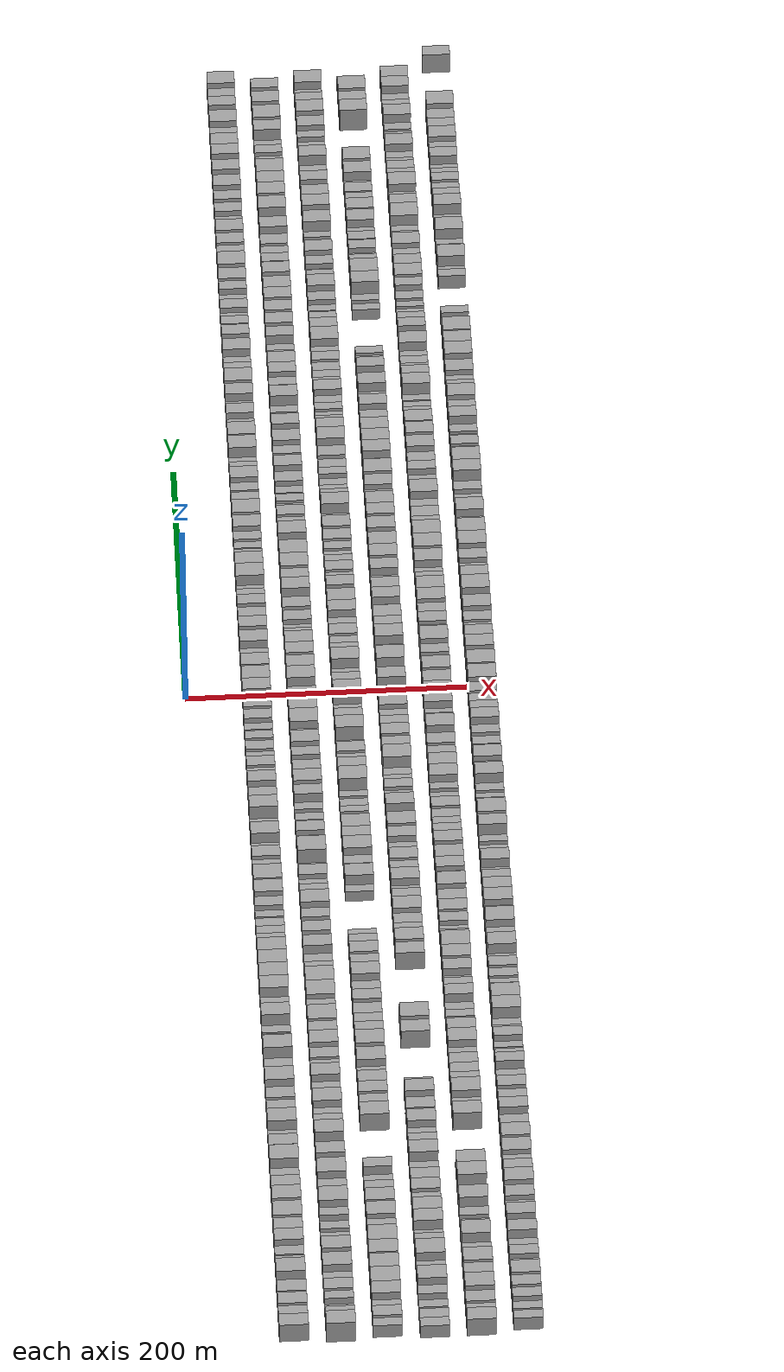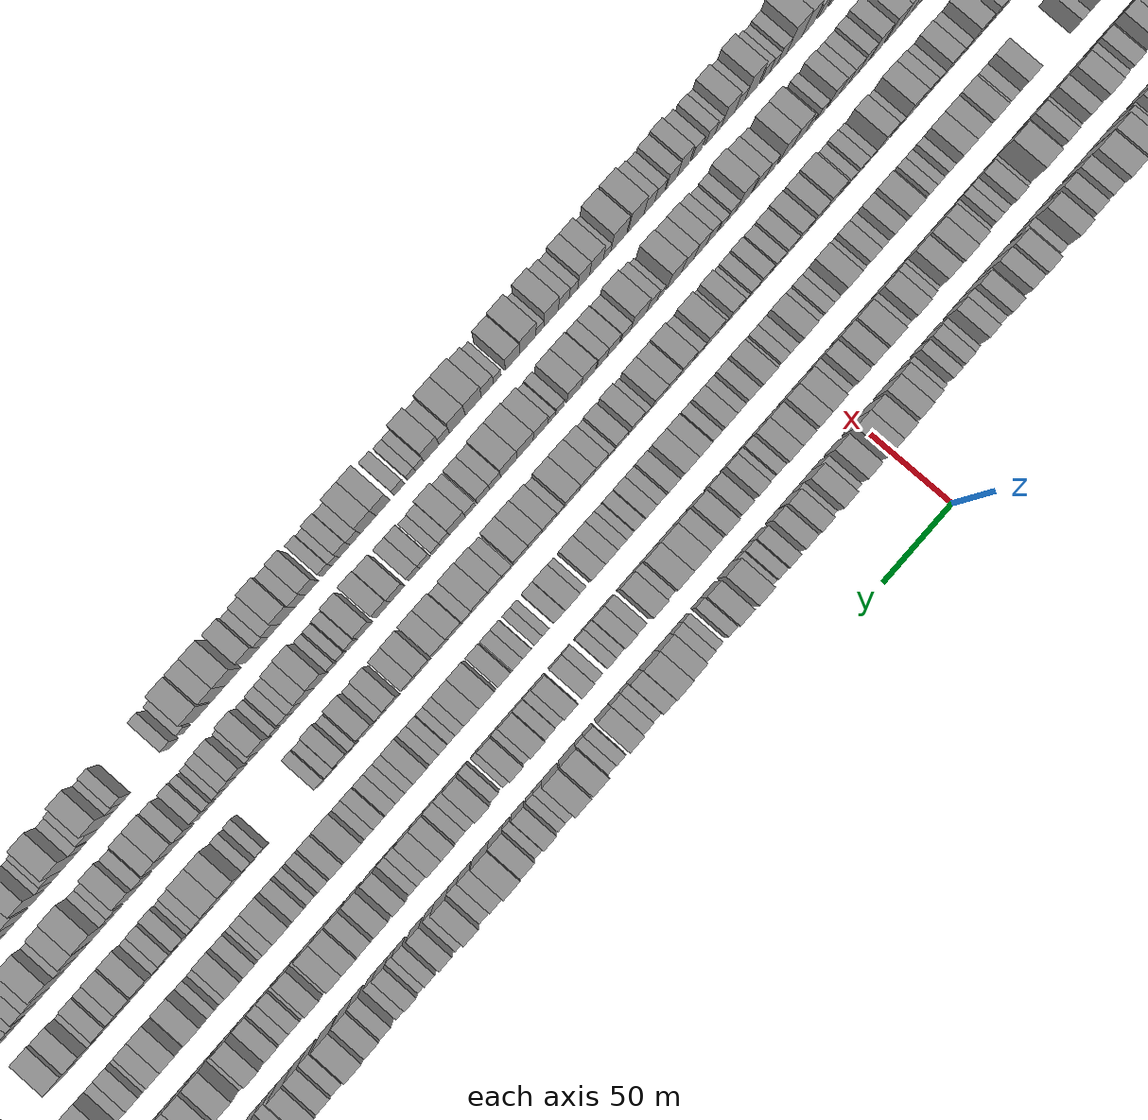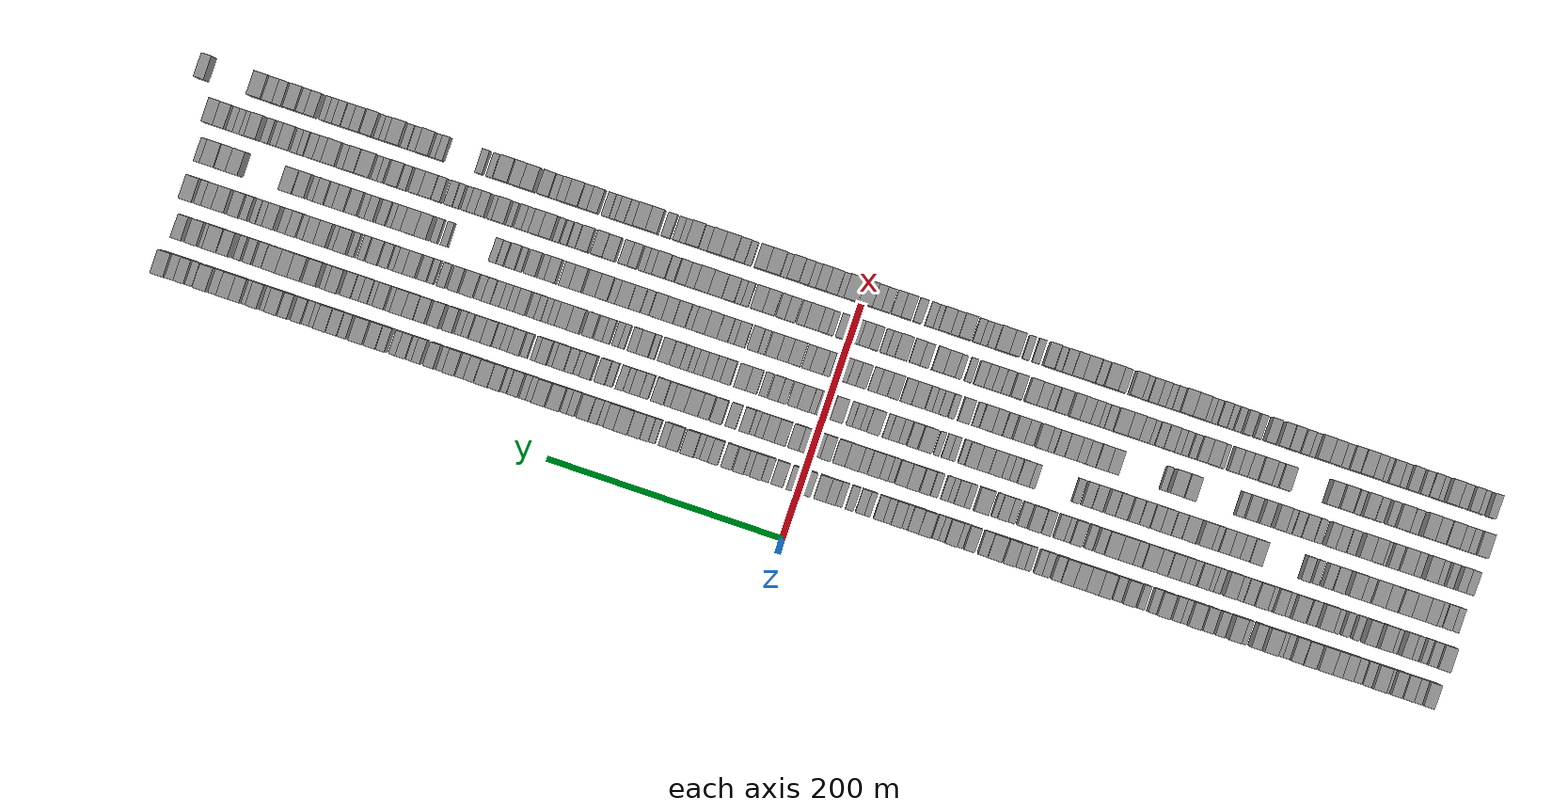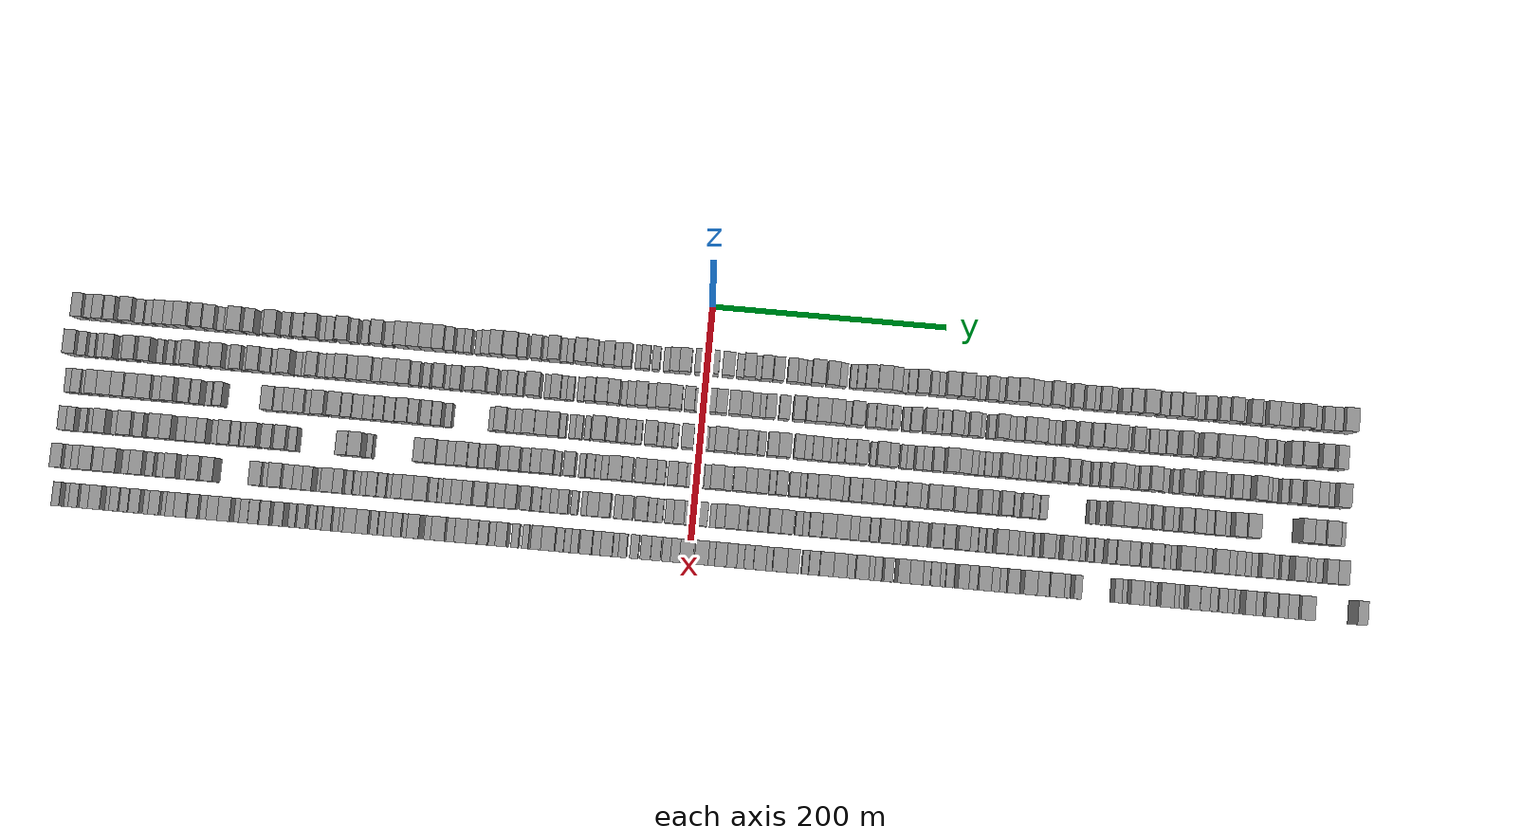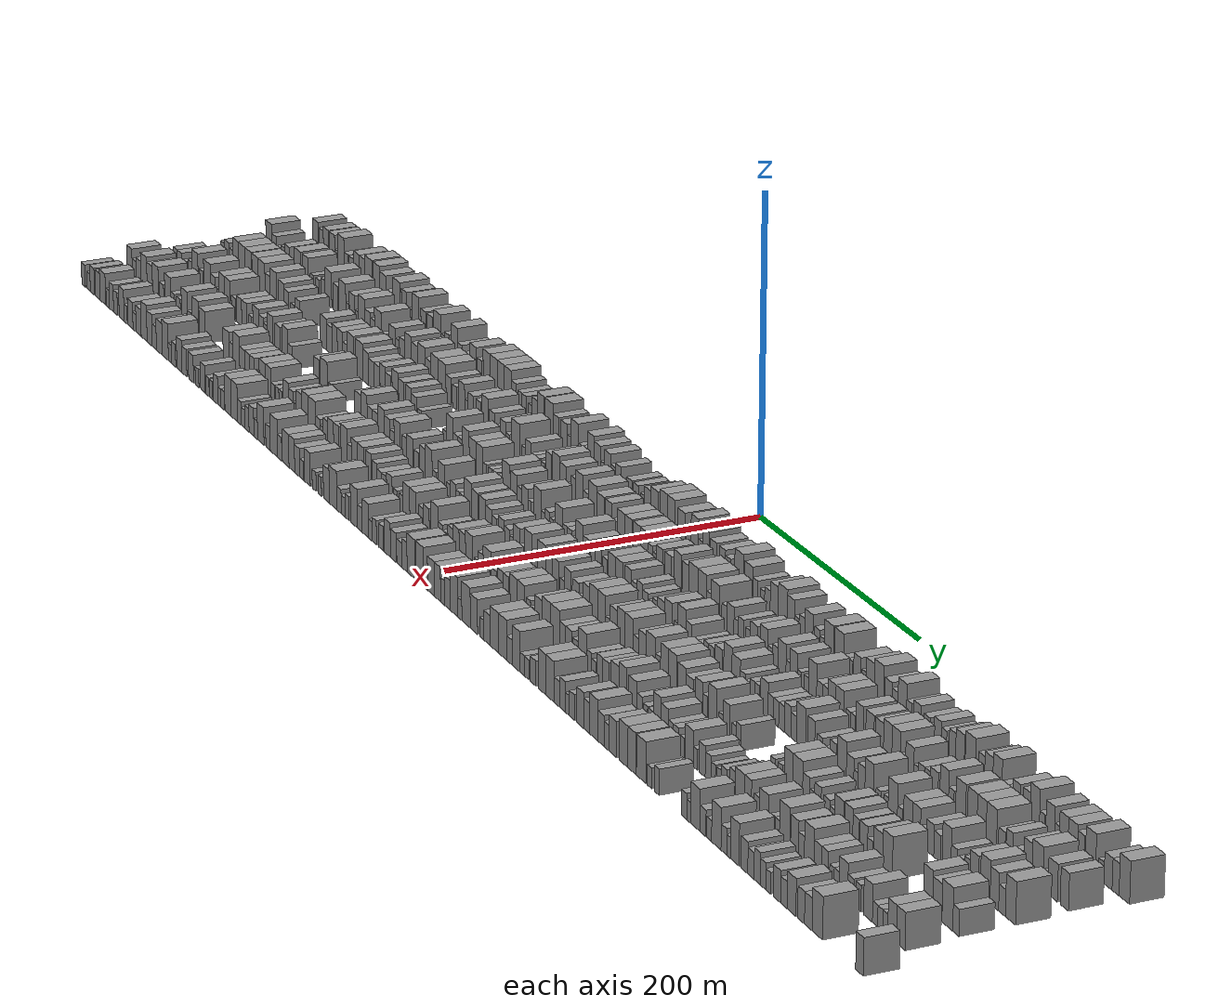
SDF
<sdf version="1.6">
 <world name="default">
  <scene>
   <sky><clouds><speed>12</speed></clouds></sky>
   <ambient>0.4 0.4 0.4 1</ambient>
   <background>0.7 0.7 0.7 1</background>
   <shadows>1</shadows>
  </scene>
  <gravity>0 0 -9.8066</gravity>
  <magnetic_field>6e-06 2.3e-05 -4.2e-05</magnetic_field>
  <physics default="0" name="default_physics" type="ode">
   <ode>
    <solver>
     <type>quick</type>
     <iters>10</iters>
     <sor>1.0</sor>
     <use_dynamic_moi_rescaling>0</use_dynamic_moi_rescaling>
    </solver>
    <constraints>
     <cfm>0</cfm>
     <erp>0.2</erp>
     <contact_max_correcting_vel>100</contact_max_correcting_vel>
     <contact_surface_layer>0.001</contact_surface_layer>
    </constraints>
   </ode>
   <max_step_size>0.004</max_step_size>
   <real_time_factor>1</real_time_factor>
   <real_time_update_rate>250</real_time_update_rate>
  </physics>
  <light name="sun" type="directional">
   <pose>0 0 10 0 0 0</pose>
   <diffuse>0.8 0.8 0.8 1</diffuse>
   <specular>0.2 0.2 0.2 1</specular>
   <attenuation>
    <range>1000</range>
    <constant>0.9</constant>
    <linear>0.01</linear>
    <quadratic>0.001</quadratic>
   </attenuation>
   <direction>-0.5 0.1 -0.9</direction>
  </light>
  <model name="building_1">
   <static>1</static>
   <pose>50.0000 -533.4224 0 0.000000 0.000000 0.000000</pose>
   <link name="link">
    <pose>0 0 10.50 0 0 0</pose>
    <collision name="collision"><geometry><box><size>20.0000 9.1552 21.0000</size></box></geometry></collision>
    <visual name="visual">
     <cast_shadows>0</cast_shadows>
     <geometry><box><size>20.0000 9.1552 21.0000</size></box></geometry>
     <material>
      <script>
       <uri>model://grey_wall/materials/scripts</uri>
       <uri>model://grey_wall/materials/textures</uri>
       <name>vrc/grey_wall</name>
      </script>
     </material>
    </visual>
   </link>
  </model>
  <model name="building_2">
   <static>1</static>
   <pose>50.0000 -524.1328 0 0.000000 0.000000 0.000000</pose>
   <link name="link">
    <pose>0 0 9.00 0 0 0</pose>
    <collision name="collision"><geometry><box><size>20.0000 7.4240 18.0000</size></box></geometry></collision>
    <visual name="visual">
     <cast_shadows>0</cast_shadows>
     <geometry><box><size>20.0000 7.4240 18.0000</size></box></geometry>
     <material>
      <script>
       <uri>model://grey_wall/materials/scripts</uri>
       <uri>model://grey_wall/materials/textures</uri>
       <name>vrc/grey_wall</name>
      </script>
     </material>
    </visual>
   </link>
  </model>
  <model name="building_3">
   <static>1</static>
   <pose>50.0000 -515.9479 0 0.000000 0.000000 0.000000</pose>
   <link name="link">
    <pose>0 0 10.50 0 0 0</pose>
    <collision name="collision"><geometry><box><size>20.0000 8.9457 21.0000</size></box></geometry></collision>
    <visual name="visual">
     <cast_shadows>0</cast_shadows>
     <geometry><box><size>20.0000 8.9457 21.0000</size></box></geometry>
     <material>
      <script>
       <uri>model://grey_wall/materials/scripts</uri>
       <uri>model://grey_wall/materials/textures</uri>
       <name>vrc/grey_wall</name>
      </script>
     </material>
    </visual>
   </link>
  </model>
  <model name="building_4">
   <static>1</static>
   <pose>50.0000 -505.9458 0 0.000000 0.000000 0.000000</pose>
   <link name="link">
    <pose>0 0 10.50 0 0 0</pose>
    <collision name="collision"><geometry><box><size>20.0000 9.0585 21.0000</size></box></geometry></collision>
    <visual name="visual">
     <cast_shadows>0</cast_shadows>
     <geometry><box><size>20.0000 9.0585 21.0000</size></box></geometry>
     <material>
      <script>
       <uri>model://grey_wall/materials/scripts</uri>
       <uri>model://grey_wall/materials/textures</uri>
       <name>vrc/grey_wall</name>
      </script>
     </material>
    </visual>
   </link>
  </model>
  <model name="building_5">
   <static>1</static>
   <pose>50.0000 -499.0077 0 0.000000 0.000000 0.000000</pose>
   <link name="link">
    <pose>0 0 6.00 0 0 0</pose>
    <collision name="collision"><geometry><box><size>20.0000 4.8177 12.0000</size></box></geometry></collision>
    <visual name="visual">
     <cast_shadows>0</cast_shadows>
     <geometry><box><size>20.0000 4.8177 12.0000</size></box></geometry>
     <material>
      <script>
       <uri>model://grey_wall/materials/scripts</uri>
       <uri>model://grey_wall/materials/textures</uri>
       <name>vrc/grey_wall</name>
      </script>
     </material>
    </visual>
   </link>
  </model>
  <model name="building_6">
   <static>1</static>
   <pose>50.0000 -491.1969 0 0.000000 0.000000 0.000000</pose>
   <link name="link">
    <pose>0 0 12.00 0 0 0</pose>
    <collision name="collision"><geometry><box><size>20.0000 10.8040 24.0000</size></box></geometry></collision>
    <visual name="visual">
     <cast_shadows>0</cast_shadows>
     <geometry><box><size>20.0000 10.8040 24.0000</size></box></geometry>
     <material>
      <script>
       <uri>model://grey_wall/materials/scripts</uri>
       <uri>model://grey_wall/materials/textures</uri>
       <name>vrc/grey_wall</name>
      </script>
     </material>
    </visual>
   </link>
  </model>
  <model name="building_7">
   <static>1</static>
   <pose>50.0000 -482.1274 0 0.000000 0.000000 0.000000</pose>
   <link name="link">
    <pose>0 0 7.50 0 0 0</pose>
    <collision name="collision"><geometry><box><size>20.0000 7.3349 15.0000</size></box></geometry></collision>
    <visual name="visual">
     <cast_shadows>0</cast_shadows>
     <geometry><box><size>20.0000 7.3349 15.0000</size></box></geometry>
     <material>
      <script>
       <uri>model://grey_wall/materials/scripts</uri>
       <uri>model://grey_wall/materials/textures</uri>
       <name>vrc/grey_wall</name>
      </script>
     </material>
    </visual>
   </link>
  </model>
  <model name="building_8">
   <static>1</static>
   <pose>50.0000 -473.8751 0 0.000000 0.000000 0.000000</pose>
   <link name="link">
    <pose>0 0 7.50 0 0 0</pose>
    <collision name="collision"><geometry><box><size>20.0000 7.1698 15.0000</size></box></geometry></collision>
    <visual name="visual">
     <cast_shadows>0</cast_shadows>
     <geometry><box><size>20.0000 7.1698 15.0000</size></box></geometry>
     <material>
      <script>
       <uri>model://grey_wall/materials/scripts</uri>
       <uri>model://grey_wall/materials/textures</uri>
       <name>vrc/grey_wall</name>
      </script>
     </material>
    </visual>
   </link>
  </model>
  <model name="building_9">
   <static>1</static>
   <pose>50.0000 -464.6451 0 0.000000 0.000000 0.000000</pose>
   <link name="link">
    <pose>0 0 10.50 0 0 0</pose>
    <collision name="collision"><geometry><box><size>20.0000 9.2903 21.0000</size></box></geometry></collision>
    <visual name="visual">
     <cast_shadows>0</cast_shadows>
     <geometry><box><size>20.0000 9.2903 21.0000</size></box></geometry>
     <material>
      <script>
       <uri>model://grey_wall/materials/scripts</uri>
       <uri>model://grey_wall/materials/textures</uri>
       <name>vrc/grey_wall</name>
      </script>
     </material>
    </visual>
   </link>
  </model>
  <model name="building_10">
   <static>1</static>
   <pose>50.0000 -455.6363 0 0.000000 0.000000 0.000000</pose>
   <link name="link">
    <pose>0 0 10.50 0 0 0</pose>
    <collision name="collision"><geometry><box><size>20.0000 8.7274 21.0000</size></box></geometry></collision>
    <visual name="visual">
     <cast_shadows>0</cast_shadows>
     <geometry><box><size>20.0000 8.7274 21.0000</size></box></geometry>
     <material>
      <script>
       <uri>model://grey_wall/materials/scripts</uri>
       <uri>model://grey_wall/materials/textures</uri>
       <name>vrc/grey_wall</name>
      </script>
     </material>
    </visual>
   </link>
  </model>
  <model name="building_11">
   <static>1</static>
   <pose>50.0000 -445.4028 0 0.000000 0.000000 0.000000</pose>
   <link name="link">
    <pose>0 0 12.00 0 0 0</pose>
    <collision name="collision"><geometry><box><size>20.0000 11.7396 24.0000</size></box></geometry></collision>
    <visual name="visual">
     <cast_shadows>0</cast_shadows>
     <geometry><box><size>20.0000 11.7396 24.0000</size></box></geometry>
     <material>
      <script>
       <uri>model://grey_wall/materials/scripts</uri>
       <uri>model://grey_wall/materials/textures</uri>
       <name>vrc/grey_wall</name>
      </script>
     </material>
    </visual>
   </link>
  </model>
  <model name="building_12">
   <static>1</static>
   <pose>50.0000 -432.2128 0 0.000000 0.000000 0.000000</pose>
   <link name="link">
    <pose>0 0 12.00 0 0 0</pose>
    <collision name="collision"><geometry><box><size>20.0000 10.6403 24.0000</size></box></geometry></collision>
    <visual name="visual">
     <cast_shadows>0</cast_shadows>
     <geometry><box><size>20.0000 10.6403 24.0000</size></box></geometry>
     <material>
      <script>
       <uri>model://grey_wall/materials/scripts</uri>
       <uri>model://grey_wall/materials/textures</uri>
       <name>vrc/grey_wall</name>
      </script>
     </material>
    </visual>
   </link>
  </model>
  <model name="building_13">
   <static>1</static>
   <pose>50.0000 -421.9103 0 0.000000 0.000000 0.000000</pose>
   <link name="link">
    <pose>0 0 10.50 0 0 0</pose>
    <collision name="collision"><geometry><box><size>20.0000 9.9647 21.0000</size></box></geometry></collision>
    <visual name="visual">
     <cast_shadows>0</cast_shadows>
     <geometry><box><size>20.0000 9.9647 21.0000</size></box></geometry>
     <material>
      <script>
       <uri>model://grey_wall/materials/scripts</uri>
       <uri>model://grey_wall/materials/textures</uri>
       <name>vrc/grey_wall</name>
      </script>
     </material>
    </visual>
   </link>
  </model>
  <model name="building_14">
   <static>1</static>
   <pose>50.0000 -414.0437 0 0.000000 0.000000 0.000000</pose>
   <link name="link">
    <pose>0 0 6.00 0 0 0</pose>
    <collision name="collision"><geometry><box><size>20.0000 5.7685 12.0000</size></box></geometry></collision>
    <visual name="visual">
     <cast_shadows>0</cast_shadows>
     <geometry><box><size>20.0000 5.7685 12.0000</size></box></geometry>
     <material>
      <script>
       <uri>model://grey_wall/materials/scripts</uri>
       <uri>model://grey_wall/materials/textures</uri>
       <name>vrc/grey_wall</name>
      </script>
     </material>
    </visual>
   </link>
  </model>
  <model name="building_15">
   <static>1</static>
   <pose>50.0000 -408.3060 0 0.000000 0.000000 0.000000</pose>
   <link name="link">
    <pose>0 0 6.00 0 0 0</pose>
    <collision name="collision"><geometry><box><size>20.0000 5.7069 12.0000</size></box></geometry></collision>
    <visual name="visual">
     <cast_shadows>0</cast_shadows>
     <geometry><box><size>20.0000 5.7069 12.0000</size></box></geometry>
     <material>
      <script>
       <uri>model://grey_wall/materials/scripts</uri>
       <uri>model://grey_wall/materials/textures</uri>
       <name>vrc/grey_wall</name>
      </script>
     </material>
    </visual>
   </link>
  </model>
  <model name="building_16">
   <static>1</static>
   <pose>50.0000 -399.6602 0 0.000000 0.000000 0.000000</pose>
   <link name="link">
    <pose>0 0 12.00 0 0 0</pose>
    <collision name="collision"><geometry><box><size>20.0000 11.5849 24.0000</size></box></geometry></collision>
    <visual name="visual">
     <cast_shadows>0</cast_shadows>
     <geometry><box><size>20.0000 11.5849 24.0000</size></box></geometry>
     <material>
      <script>
       <uri>model://grey_wall/materials/scripts</uri>
       <uri>model://grey_wall/materials/textures</uri>
       <name>vrc/grey_wall</name>
      </script>
     </material>
    </visual>
   </link>
  </model>
  <model name="building_17">
   <static>1</static>
   <pose>50.0000 -387.5514 0 0.000000 0.000000 0.000000</pose>
   <link name="link">
    <pose>0 0 10.50 0 0 0</pose>
    <collision name="collision"><geometry><box><size>20.0000 8.6327 21.0000</size></box></geometry></collision>
    <visual name="visual">
     <cast_shadows>0</cast_shadows>
     <geometry><box><size>20.0000 8.6327 21.0000</size></box></geometry>
     <material>
      <script>
       <uri>model://grey_wall/materials/scripts</uri>
       <uri>model://grey_wall/materials/textures</uri>
       <name>vrc/grey_wall</name>
      </script>
     </material>
    </visual>
   </link>
  </model>
  <model name="building_18">
   <static>1</static>
   <pose>50.0000 -377.3705 0 0.000000 0.000000 0.000000</pose>
   <link name="link">
    <pose>0 0 6.00 0 0 0</pose>
    <collision name="collision"><geometry><box><size>20.0000 5.7292 12.0000</size></box></geometry></collision>
    <visual name="visual">
     <cast_shadows>0</cast_shadows>
     <geometry><box><size>20.0000 5.7292 12.0000</size></box></geometry>
     <material>
      <script>
       <uri>model://grey_wall/materials/scripts</uri>
       <uri>model://grey_wall/materials/textures</uri>
       <name>vrc/grey_wall</name>
      </script>
     </material>
    </visual>
   </link>
  </model>
  <model name="building_19">
   <static>1</static>
   <pose>50.0000 -369.2263 0 0.000000 0.000000 0.000000</pose>
   <link name="link">
    <pose>0 0 12.00 0 0 0</pose>
    <collision name="collision"><geometry><box><size>20.0000 10.5591 24.0000</size></box></geometry></collision>
    <visual name="visual">
     <cast_shadows>0</cast_shadows>
     <geometry><box><size>20.0000 10.5591 24.0000</size></box></geometry>
     <material>
      <script>
       <uri>model://grey_wall/materials/scripts</uri>
       <uri>model://grey_wall/materials/textures</uri>
       <name>vrc/grey_wall</name>
      </script>
     </material>
    </visual>
   </link>
  </model>
  <model name="building_20">
   <static>1</static>
   <pose>50.0000 -357.1500 0 0.000000 0.000000 0.000000</pose>
   <link name="link">
    <pose>0 0 9.00 0 0 0</pose>
    <collision name="collision"><geometry><box><size>20.0000 7.5935 18.0000</size></box></geometry></collision>
    <visual name="visual">
     <cast_shadows>0</cast_shadows>
     <geometry><box><size>20.0000 7.5935 18.0000</size></box></geometry>
     <material>
      <script>
       <uri>model://grey_wall/materials/scripts</uri>
       <uri>model://grey_wall/materials/textures</uri>
       <name>vrc/grey_wall</name>
      </script>
     </material>
    </visual>
   </link>
  </model>
  <model name="building_21">
   <static>1</static>
   <pose>50.0000 -346.9316 0 0.000000 0.000000 0.000000</pose>
   <link name="link">
    <pose>0 0 9.00 0 0 0</pose>
    <collision name="collision"><geometry><box><size>20.0000 8.8433 18.0000</size></box></geometry></collision>
    <visual name="visual">
     <cast_shadows>0</cast_shadows>
     <geometry><box><size>20.0000 8.8433 18.0000</size></box></geometry>
     <material>
      <script>
       <uri>model://grey_wall/materials/scripts</uri>
       <uri>model://grey_wall/materials/textures</uri>
       <name>vrc/grey_wall</name>
      </script>
     </material>
    </visual>
   </link>
  </model>
  <model name="building_22">
   <static>1</static>
   <pose>50.0000 -335.1020 0 0.000000 0.000000 0.000000</pose>
   <link name="link">
    <pose>0 0 12.00 0 0 0</pose>
    <collision name="collision"><geometry><box><size>20.0000 10.8159 24.0000</size></box></geometry></collision>
    <visual name="visual">
     <cast_shadows>0</cast_shadows>
     <geometry><box><size>20.0000 10.8159 24.0000</size></box></geometry>
     <material>
      <script>
       <uri>model://grey_wall/materials/scripts</uri>
       <uri>model://grey_wall/materials/textures</uri>
       <name>vrc/grey_wall</name>
      </script>
     </material>
    </visual>
   </link>
  </model>
  <model name="building_23">
   <static>1</static>
   <pose>50.0000 -326.8852 0 0.000000 0.000000 0.000000</pose>
   <link name="link">
    <pose>0 0 6.00 0 0 0</pose>
    <collision name="collision"><geometry><box><size>20.0000 5.6176 12.0000</size></box></geometry></collision>
    <visual name="visual">
     <cast_shadows>0</cast_shadows>
     <geometry><box><size>20.0000 5.6176 12.0000</size></box></geometry>
     <material>
      <script>
       <uri>model://grey_wall/materials/scripts</uri>
       <uri>model://grey_wall/materials/textures</uri>
       <name>vrc/grey_wall</name>
      </script>
     </material>
    </visual>
   </link>
  </model>
  <model name="building_24">
   <static>1</static>
   <pose>50.0000 -320.5650 0 0.000000 0.000000 0.000000</pose>
   <link name="link">
    <pose>0 0 7.50 0 0 0</pose>
    <collision name="collision"><geometry><box><size>20.0000 7.0227 15.0000</size></box></geometry></collision>
    <visual name="visual">
     <cast_shadows>0</cast_shadows>
     <geometry><box><size>20.0000 7.0227 15.0000</size></box></geometry>
     <material>
      <script>
       <uri>model://grey_wall/materials/scripts</uri>
       <uri>model://grey_wall/materials/textures</uri>
       <name>vrc/grey_wall</name>
      </script>
     </material>
    </visual>
   </link>
  </model>
  <model name="building_25">
   <static>1</static>
   <pose>50.0000 -308.7052 0 0.000000 0.000000 0.000000</pose>
   <link name="link">
    <pose>0 0 12.00 0 0 0</pose>
    <collision name="collision"><geometry><box><size>20.0000 10.6969 24.0000</size></box></geometry></collision>
    <visual name="visual">
     <cast_shadows>0</cast_shadows>
     <geometry><box><size>20.0000 10.6969 24.0000</size></box></geometry>
     <material>
      <script>
       <uri>model://grey_wall/materials/scripts</uri>
       <uri>model://grey_wall/materials/textures</uri>
       <name>vrc/grey_wall</name>
      </script>
     </material>
    </visual>
   </link>
  </model>
  <model name="building_26">
   <static>1</static>
   <pose>50.0000 -300.0668 0 0.000000 0.000000 0.000000</pose>
   <link name="link">
    <pose>0 0 7.50 0 0 0</pose>
    <collision name="collision"><geometry><box><size>20.0000 6.5799 15.0000</size></box></geometry></collision>
    <visual name="visual">
     <cast_shadows>0</cast_shadows>
     <geometry><box><size>20.0000 6.5799 15.0000</size></box></geometry>
     <material>
      <script>
       <uri>model://grey_wall/materials/scripts</uri>
       <uri>model://grey_wall/materials/textures</uri>
       <name>vrc/grey_wall</name>
      </script>
     </material>
    </visual>
   </link>
  </model>
  <model name="building_27">
   <static>1</static>
   <pose>50.0000 -290.8324 0 0.000000 0.000000 0.000000</pose>
   <link name="link">
    <pose>0 0 6.00 0 0 0</pose>
    <collision name="collision"><geometry><box><size>20.0000 5.8889 12.0000</size></box></geometry></collision>
    <visual name="visual">
     <cast_shadows>0</cast_shadows>
     <geometry><box><size>20.0000 5.8889 12.0000</size></box></geometry>
     <material>
      <script>
       <uri>model://grey_wall/materials/scripts</uri>
       <uri>model://grey_wall/materials/textures</uri>
       <name>vrc/grey_wall</name>
      </script>
     </material>
    </visual>
   </link>
  </model>
  <model name="building_28">
   <static>1</static>
   <pose>50.0000 -279.8640 0 0.000000 0.000000 0.000000</pose>
   <link name="link">
    <pose>0 0 10.50 0 0 0</pose>
    <collision name="collision"><geometry><box><size>20.0000 10.0480 21.0000</size></box></geometry></collision>
    <visual name="visual">
     <cast_shadows>0</cast_shadows>
     <geometry><box><size>20.0000 10.0480 21.0000</size></box></geometry>
     <material>
      <script>
       <uri>model://grey_wall/materials/scripts</uri>
       <uri>model://grey_wall/materials/textures</uri>
       <name>vrc/grey_wall</name>
      </script>
     </material>
    </visual>
   </link>
  </model>
  <model name="building_29">
   <static>1</static>
   <pose>50.0000 -270.1404 0 0.000000 0.000000 0.000000</pose>
   <link name="link">
    <pose>0 0 7.50 0 0 0</pose>
    <collision name="collision"><geometry><box><size>20.0000 7.3992 15.0000</size></box></geometry></collision>
    <visual name="visual">
     <cast_shadows>0</cast_shadows>
     <geometry><box><size>20.0000 7.3992 15.0000</size></box></geometry>
     <material>
      <script>
       <uri>model://grey_wall/materials/scripts</uri>
       <uri>model://grey_wall/materials/textures</uri>
       <name>vrc/grey_wall</name>
      </script>
     </material>
    </visual>
   </link>
  </model>
  <model name="building_30">
   <static>1</static>
   <pose>50.0000 -259.2145 0 0.000000 0.000000 0.000000</pose>
   <link name="link">
    <pose>0 0 12.00 0 0 0</pose>
    <collision name="collision"><geometry><box><size>20.0000 10.4526 24.0000</size></box></geometry></collision>
    <visual name="visual">
     <cast_shadows>0</cast_shadows>
     <geometry><box><size>20.0000 10.4526 24.0000</size></box></geometry>
     <material>
      <script>
       <uri>model://grey_wall/materials/scripts</uri>
       <uri>model://grey_wall/materials/textures</uri>
       <name>vrc/grey_wall</name>
      </script>
     </material>
    </visual>
   </link>
  </model>
  <model name="building_31">
   <static>1</static>
   <pose>50.0000 -248.5436 0 0.000000 0.000000 0.000000</pose>
   <link name="link">
    <pose>0 0 12.00 0 0 0</pose>
    <collision name="collision"><geometry><box><size>20.0000 10.8893 24.0000</size></box></geometry></collision>
    <visual name="visual">
     <cast_shadows>0</cast_shadows>
     <geometry><box><size>20.0000 10.8893 24.0000</size></box></geometry>
     <material>
      <script>
       <uri>model://grey_wall/materials/scripts</uri>
       <uri>model://grey_wall/materials/textures</uri>
       <name>vrc/grey_wall</name>
      </script>
     </material>
    </visual>
   </link>
  </model>
  <model name="building_32">
   <static>1</static>
   <pose>50.0000 -237.7849 0 0.000000 0.000000 0.000000</pose>
   <link name="link">
    <pose>0 0 12.00 0 0 0</pose>
    <collision name="collision"><geometry><box><size>20.0000 10.6280 24.0000</size></box></geometry></collision>
    <visual name="visual">
     <cast_shadows>0</cast_shadows>
     <geometry><box><size>20.0000 10.6280 24.0000</size></box></geometry>
     <material>
      <script>
       <uri>model://grey_wall/materials/scripts</uri>
       <uri>model://grey_wall/materials/textures</uri>
       <name>vrc/grey_wall</name>
      </script>
     </material>
    </visual>
   </link>
  </model>
  <model name="building_33">
   <static>1</static>
   <pose>50.0000 -227.3663 0 0.000000 0.000000 0.000000</pose>
   <link name="link">
    <pose>0 0 12.00 0 0 0</pose>
    <collision name="collision"><geometry><box><size>20.0000 10.2093 24.0000</size></box></geometry></collision>
    <visual name="visual">
     <cast_shadows>0</cast_shadows>
     <geometry><box><size>20.0000 10.2093 24.0000</size></box></geometry>
     <material>
      <script>
       <uri>model://grey_wall/materials/scripts</uri>
       <uri>model://grey_wall/materials/textures</uri>
       <name>vrc/grey_wall</name>
      </script>
     </material>
    </visual>
   </link>
  </model>
  <model name="building_34">
   <static>1</static>
   <pose>50.0000 -218.4926 0 0.000000 0.000000 0.000000</pose>
   <link name="link">
    <pose>0 0 9.00 0 0 0</pose>
    <collision name="collision"><geometry><box><size>20.0000 7.5381 18.0000</size></box></geometry></collision>
    <visual name="visual">
     <cast_shadows>0</cast_shadows>
     <geometry><box><size>20.0000 7.5381 18.0000</size></box></geometry>
     <material>
      <script>
       <uri>model://grey_wall/materials/scripts</uri>
       <uri>model://grey_wall/materials/textures</uri>
       <name>vrc/grey_wall</name>
      </script>
     </material>
    </visual>
   </link>
  </model>
  <model name="building_35">
   <static>1</static>
   <pose>50.0000 -209.6279 0 0.000000 0.000000 0.000000</pose>
   <link name="link">
    <pose>0 0 7.50 0 0 0</pose>
    <collision name="collision"><geometry><box><size>20.0000 6.1912 15.0000</size></box></geometry></collision>
    <visual name="visual">
     <cast_shadows>0</cast_shadows>
     <geometry><box><size>20.0000 6.1912 15.0000</size></box></geometry>
     <material>
      <script>
       <uri>model://grey_wall/materials/scripts</uri>
       <uri>model://grey_wall/materials/textures</uri>
       <name>vrc/grey_wall</name>
      </script>
     </material>
    </visual>
   </link>
  </model>
  <model name="building_36">
   <static>1</static>
   <pose>50.0000 -203.2886 0 0.000000 0.000000 0.000000</pose>
   <link name="link">
    <pose>0 0 7.50 0 0 0</pose>
    <collision name="collision"><geometry><box><size>20.0000 6.4872 15.0000</size></box></geometry></collision>
    <visual name="visual">
     <cast_shadows>0</cast_shadows>
     <geometry><box><size>20.0000 6.4872 15.0000</size></box></geometry>
     <material>
      <script>
       <uri>model://grey_wall/materials/scripts</uri>
       <uri>model://grey_wall/materials/textures</uri>
       <name>vrc/grey_wall</name>
      </script>
     </material>
    </visual>
   </link>
  </model>
  <model name="building_37">
   <static>1</static>
   <pose>50.0000 -194.2799 0 0.000000 0.000000 0.000000</pose>
   <link name="link">
    <pose>0 0 6.00 0 0 0</pose>
    <collision name="collision"><geometry><box><size>20.0000 5.5302 12.0000</size></box></geometry></collision>
    <visual name="visual">
     <cast_shadows>0</cast_shadows>
     <geometry><box><size>20.0000 5.5302 12.0000</size></box></geometry>
     <material>
      <script>
       <uri>model://grey_wall/materials/scripts</uri>
       <uri>model://grey_wall/materials/textures</uri>
       <name>vrc/grey_wall</name>
      </script>
     </material>
    </visual>
   </link>
  </model>
  <model name="building_38">
   <static>1</static>
   <pose>50.0000 -187.5886 0 0.000000 0.000000 0.000000</pose>
   <link name="link">
    <pose>0 0 9.00 0 0 0</pose>
    <collision name="collision"><geometry><box><size>20.0000 7.8523 18.0000</size></box></geometry></collision>
    <visual name="visual">
     <cast_shadows>0</cast_shadows>
     <geometry><box><size>20.0000 7.8523 18.0000</size></box></geometry>
     <material>
      <script>
       <uri>model://grey_wall/materials/scripts</uri>
       <uri>model://grey_wall/materials/textures</uri>
       <name>vrc/grey_wall</name>
      </script>
     </material>
    </visual>
   </link>
  </model>
  <model name="building_39">
   <static>1</static>
   <pose>50.0000 -178.5077 0 0.000000 0.000000 0.000000</pose>
   <link name="link">
    <pose>0 0 12.00 0 0 0</pose>
    <collision name="collision"><geometry><box><size>20.0000 10.3095 24.0000</size></box></geometry></collision>
    <visual name="visual">
     <cast_shadows>0</cast_shadows>
     <geometry><box><size>20.0000 10.3095 24.0000</size></box></geometry>
     <material>
      <script>
       <uri>model://grey_wall/materials/scripts</uri>
       <uri>model://grey_wall/materials/textures</uri>
       <name>vrc/grey_wall</name>
      </script>
     </material>
    </visual>
   </link>
  </model>
  <model name="building_40">
   <static>1</static>
   <pose>50.0000 -166.3984 0 0.000000 0.000000 0.000000</pose>
   <link name="link">
    <pose>0 0 12.00 0 0 0</pose>
    <collision name="collision"><geometry><box><size>20.0000 11.9091 24.0000</size></box></geometry></collision>
    <visual name="visual">
     <cast_shadows>0</cast_shadows>
     <geometry><box><size>20.0000 11.9091 24.0000</size></box></geometry>
     <material>
      <script>
       <uri>model://grey_wall/materials/scripts</uri>
       <uri>model://grey_wall/materials/textures</uri>
       <name>vrc/grey_wall</name>
      </script>
     </material>
    </visual>
   </link>
  </model>
  <model name="building_41">
   <static>1</static>
   <pose>50.0000 -156.4728 0 0.000000 0.000000 0.000000</pose>
   <link name="link">
    <pose>0 0 9.00 0 0 0</pose>
    <collision name="collision"><geometry><box><size>20.0000 7.9420 18.0000</size></box></geometry></collision>
    <visual name="visual">
     <cast_shadows>0</cast_shadows>
     <geometry><box><size>20.0000 7.9420 18.0000</size></box></geometry>
     <material>
      <script>
       <uri>model://grey_wall/materials/scripts</uri>
       <uri>model://grey_wall/materials/textures</uri>
       <name>vrc/grey_wall</name>
      </script>
     </material>
    </visual>
   </link>
  </model>
  <model name="building_42">
   <static>1</static>
   <pose>50.0000 -145.0451 0 0.000000 0.000000 0.000000</pose>
   <link name="link">
    <pose>0 0 9.00 0 0 0</pose>
    <collision name="collision"><geometry><box><size>20.0000 8.9133 18.0000</size></box></geometry></collision>
    <visual name="visual">
     <cast_shadows>0</cast_shadows>
     <geometry><box><size>20.0000 8.9133 18.0000</size></box></geometry>
     <material>
      <script>
       <uri>model://grey_wall/materials/scripts</uri>
       <uri>model://grey_wall/materials/textures</uri>
       <name>vrc/grey_wall</name>
      </script>
     </material>
    </visual>
   </link>
  </model>
  <model name="building_43">
   <static>1</static>
   <pose>50.0000 -136.9729 0 0.000000 0.000000 0.000000</pose>
   <link name="link">
    <pose>0 0 6.00 0 0 0</pose>
    <collision name="collision"><geometry><box><size>20.0000 5.2310 12.0000</size></box></geometry></collision>
    <visual name="visual">
     <cast_shadows>0</cast_shadows>
     <geometry><box><size>20.0000 5.2310 12.0000</size></box></geometry>
     <material>
      <script>
       <uri>model://grey_wall/materials/scripts</uri>
       <uri>model://grey_wall/materials/textures</uri>
       <name>vrc/grey_wall</name>
      </script>
     </material>
    </visual>
   </link>
  </model>
  <model name="building_44">
   <static>1</static>
   <pose>50.0000 -129.3180 0 0.000000 0.000000 0.000000</pose>
   <link name="link">
    <pose>0 0 12.00 0 0 0</pose>
    <collision name="collision"><geometry><box><size>20.0000 10.0789 24.0000</size></box></geometry></collision>
    <visual name="visual">
     <cast_shadows>0</cast_shadows>
     <geometry><box><size>20.0000 10.0789 24.0000</size></box></geometry>
     <material>
      <script>
       <uri>model://grey_wall/materials/scripts</uri>
       <uri>model://grey_wall/materials/textures</uri>
       <name>vrc/grey_wall</name>
      </script>
     </material>
    </visual>
   </link>
  </model>
  <model name="building_45">
   <static>1</static>
   <pose>50.0000 -121.6777 0 0.000000 0.000000 0.000000</pose>
   <link name="link">
    <pose>0 0 6.00 0 0 0</pose>
    <collision name="collision"><geometry><box><size>20.0000 5.2017 12.0000</size></box></geometry></collision>
    <visual name="visual">
     <cast_shadows>0</cast_shadows>
     <geometry><box><size>20.0000 5.2017 12.0000</size></box></geometry>
     <material>
      <script>
       <uri>model://grey_wall/materials/scripts</uri>
       <uri>model://grey_wall/materials/textures</uri>
       <name>vrc/grey_wall</name>
      </script>
     </material>
    </visual>
   </link>
  </model>
  <model name="building_46">
   <static>1</static>
   <pose>50.0000 -116.3728 0 0.000000 0.000000 0.000000</pose>
   <link name="link">
    <pose>0 0 6.00 0 0 0</pose>
    <collision name="collision"><geometry><box><size>20.0000 5.4082 12.0000</size></box></geometry></collision>
    <visual name="visual">
     <cast_shadows>0</cast_shadows>
     <geometry><box><size>20.0000 5.4082 12.0000</size></box></geometry>
     <material>
      <script>
       <uri>model://grey_wall/materials/scripts</uri>
       <uri>model://grey_wall/materials/textures</uri>
       <name>vrc/grey_wall</name>
      </script>
     </material>
    </visual>
   </link>
  </model>
  <model name="building_47">
   <static>1</static>
   <pose>50.0000 -106.7435 0 0.000000 0.000000 0.000000</pose>
   <link name="link">
    <pose>0 0 12.00 0 0 0</pose>
    <collision name="collision"><geometry><box><size>20.0000 9.8505 24.0000</size></box></geometry></collision>
    <visual name="visual">
     <cast_shadows>0</cast_shadows>
     <geometry><box><size>20.0000 9.8505 24.0000</size></box></geometry>
     <material>
      <script>
       <uri>model://grey_wall/materials/scripts</uri>
       <uri>model://grey_wall/materials/textures</uri>
       <name>vrc/grey_wall</name>
      </script>
     </material>
    </visual>
   </link>
  </model>
  <model name="building_48">
   <static>1</static>
   <pose>50.0000 -97.2325 0 0.000000 0.000000 0.000000</pose>
   <link name="link">
    <pose>0 0 10.50 0 0 0</pose>
    <collision name="collision"><geometry><box><size>20.0000 9.1715 21.0000</size></box></geometry></collision>
    <visual name="visual">
     <cast_shadows>0</cast_shadows>
     <geometry><box><size>20.0000 9.1715 21.0000</size></box></geometry>
     <material>
      <script>
       <uri>model://grey_wall/materials/scripts</uri>
       <uri>model://grey_wall/materials/textures</uri>
       <name>vrc/grey_wall</name>
      </script>
     </material>
    </visual>
   </link>
  </model>
  <model name="building_49">
   <static>1</static>
   <pose>50.0000 -90.0845 0 0.000000 0.000000 0.000000</pose>
   <link name="link">
    <pose>0 0 6.00 0 0 0</pose>
    <collision name="collision"><geometry><box><size>20.0000 5.1245 12.0000</size></box></geometry></collision>
    <visual name="visual">
     <cast_shadows>0</cast_shadows>
     <geometry><box><size>20.0000 5.1245 12.0000</size></box></geometry>
     <material>
      <script>
       <uri>model://grey_wall/materials/scripts</uri>
       <uri>model://grey_wall/materials/textures</uri>
       <name>vrc/grey_wall</name>
      </script>
     </material>
    </visual>
   </link>
  </model>
  <model name="building_50">
   <static>1</static>
   <pose>50.0000 -83.0336 0 0.000000 0.000000 0.000000</pose>
   <link name="link">
    <pose>0 0 10.50 0 0 0</pose>
    <collision name="collision"><geometry><box><size>20.0000 8.9772 21.0000</size></box></geometry></collision>
    <visual name="visual">
     <cast_shadows>0</cast_shadows>
     <geometry><box><size>20.0000 8.9772 21.0000</size></box></geometry>
     <material>
      <script>
       <uri>model://grey_wall/materials/scripts</uri>
       <uri>model://grey_wall/materials/textures</uri>
       <name>vrc/grey_wall</name>
      </script>
     </material>
    </visual>
   </link>
  </model>
  <model name="building_51">
   <static>1</static>
   <pose>50.0000 -75.2911 0 0.000000 0.000000 0.000000</pose>
   <link name="link">
    <pose>0 0 7.50 0 0 0</pose>
    <collision name="collision"><geometry><box><size>20.0000 6.5078 15.0000</size></box></geometry></collision>
    <visual name="visual">
     <cast_shadows>0</cast_shadows>
     <geometry><box><size>20.0000 6.5078 15.0000</size></box></geometry>
     <material>
      <script>
       <uri>model://grey_wall/materials/scripts</uri>
       <uri>model://grey_wall/materials/textures</uri>
       <name>vrc/grey_wall</name>
      </script>
     </material>
    </visual>
   </link>
  </model>
  <model name="building_52">
   <static>1</static>
   <pose>50.0000 -68.0344 0 0.000000 0.000000 0.000000</pose>
   <link name="link">
    <pose>0 0 9.00 0 0 0</pose>
    <collision name="collision"><geometry><box><size>20.0000 8.0055 18.0000</size></box></geometry></collision>
    <visual name="visual">
     <cast_shadows>0</cast_shadows>
     <geometry><box><size>20.0000 8.0055 18.0000</size></box></geometry>
     <material>
      <script>
       <uri>model://grey_wall/materials/scripts</uri>
       <uri>model://grey_wall/materials/textures</uri>
       <name>vrc/grey_wall</name>
      </script>
     </material>
    </visual>
   </link>
  </model>
  <model name="building_53">
   <static>1</static>
   <pose>50.0000 -58.5989 0 0.000000 0.000000 0.000000</pose>
   <link name="link">
    <pose>0 0 6.00 0 0 0</pose>
    <collision name="collision"><geometry><box><size>20.0000 4.8654 12.0000</size></box></geometry></collision>
    <visual name="visual">
     <cast_shadows>0</cast_shadows>
     <geometry><box><size>20.0000 4.8654 12.0000</size></box></geometry>
     <material>
      <script>
       <uri>model://grey_wall/materials/scripts</uri>
       <uri>model://grey_wall/materials/textures</uri>
       <name>vrc/grey_wall</name>
      </script>
     </material>
    </visual>
   </link>
  </model>
  <model name="building_54">
   <static>1</static>
   <pose>50.0000 -52.4347 0 0.000000 0.000000 0.000000</pose>
   <link name="link">
    <pose>0 0 7.50 0 0 0</pose>
    <collision name="collision"><geometry><box><size>20.0000 7.4630 15.0000</size></box></geometry></collision>
    <visual name="visual">
     <cast_shadows>0</cast_shadows>
     <geometry><box><size>20.0000 7.4630 15.0000</size></box></geometry>
     <material>
      <script>
       <uri>model://grey_wall/materials/scripts</uri>
       <uri>model://grey_wall/materials/textures</uri>
       <name>vrc/grey_wall</name>
      </script>
     </material>
    </visual>
   </link>
  </model>
  <model name="building_55">
   <static>1</static>
   <pose>50.0000 -43.4236 0 0.000000 0.000000 0.000000</pose>
   <link name="link">
    <pose>0 0 7.50 0 0 0</pose>
    <collision name="collision"><geometry><box><size>20.0000 6.5594 15.0000</size></box></geometry></collision>
    <visual name="visual">
     <cast_shadows>0</cast_shadows>
     <geometry><box><size>20.0000 6.5594 15.0000</size></box></geometry>
     <material>
      <script>
       <uri>model://grey_wall/materials/scripts</uri>
       <uri>model://grey_wall/materials/textures</uri>
       <name>vrc/grey_wall</name>
      </script>
     </material>
    </visual>
   </link>
  </model>
  <model name="building_56">
   <static>1</static>
   <pose>50.0000 -34.3570 0 0.000000 0.000000 0.000000</pose>
   <link name="link">
    <pose>0 0 6.00 0 0 0</pose>
    <collision name="collision"><geometry><box><size>20.0000 5.5738 12.0000</size></box></geometry></collision>
    <visual name="visual">
     <cast_shadows>0</cast_shadows>
     <geometry><box><size>20.0000 5.5738 12.0000</size></box></geometry>
     <material>
      <script>
       <uri>model://grey_wall/materials/scripts</uri>
       <uri>model://grey_wall/materials/textures</uri>
       <name>vrc/grey_wall</name>
      </script>
     </material>
    </visual>
   </link>
  </model>
  <model name="building_57">
   <static>1</static>
   <pose>50.0000 -27.4977 0 0.000000 0.000000 0.000000</pose>
   <link name="link">
    <pose>0 0 9.00 0 0 0</pose>
    <collision name="collision"><geometry><box><size>20.0000 8.1449 18.0000</size></box></geometry></collision>
    <visual name="visual">
     <cast_shadows>0</cast_shadows>
     <geometry><box><size>20.0000 8.1449 18.0000</size></box></geometry>
     <material>
      <script>
       <uri>model://grey_wall/materials/scripts</uri>
       <uri>model://grey_wall/materials/textures</uri>
       <name>vrc/grey_wall</name>
      </script>
     </material>
    </visual>
   </link>
  </model>
  <model name="building_58">
   <static>1</static>
   <pose>50.0000 -18.3838 0 0.000000 0.000000 0.000000</pose>
   <link name="link">
    <pose>0 0 10.50 0 0 0</pose>
    <collision name="collision"><geometry><box><size>20.0000 10.0829 21.0000</size></box></geometry></collision>
    <visual name="visual">
     <cast_shadows>0</cast_shadows>
     <geometry><box><size>20.0000 10.0829 21.0000</size></box></geometry>
     <material>
      <script>
       <uri>model://grey_wall/materials/scripts</uri>
       <uri>model://grey_wall/materials/textures</uri>
       <name>vrc/grey_wall</name>
      </script>
     </material>
    </visual>
   </link>
  </model>
  <model name="building_59">
   <static>1</static>
   <pose>50.0000 -5.5306 0 0.000000 0.000000 0.000000</pose>
   <link name="link">
    <pose>0 0 12.00 0 0 0</pose>
    <collision name="collision"><geometry><box><size>20.0000 9.6235 24.0000</size></box></geometry></collision>
    <visual name="visual">
     <cast_shadows>0</cast_shadows>
     <geometry><box><size>20.0000 9.6235 24.0000</size></box></geometry>
     <material>
      <script>
       <uri>model://grey_wall/materials/scripts</uri>
       <uri>model://grey_wall/materials/textures</uri>
       <name>vrc/grey_wall</name>
      </script>
     </material>
    </visual>
   </link>
  </model>
  <model name="building_60">
   <static>1</static>
   <pose>50.0000 4.6134 0 0.000000 0.000000 0.000000</pose>
   <link name="link">
    <pose>0 0 12.00 0 0 0</pose>
    <collision name="collision"><geometry><box><size>20.0000 10.6645 24.0000</size></box></geometry></collision>
    <visual name="visual">
     <cast_shadows>0</cast_shadows>
     <geometry><box><size>20.0000 10.6645 24.0000</size></box></geometry>
     <material>
      <script>
       <uri>model://grey_wall/materials/scripts</uri>
       <uri>model://grey_wall/materials/textures</uri>
       <name>vrc/grey_wall</name>
      </script>
     </material>
    </visual>
   </link>
  </model>
  <model name="building_61">
   <static>1</static>
   <pose>50.0000 17.9974 0 0.000000 0.000000 0.000000</pose>
   <link name="link">
    <pose>0 0 10.50 0 0 0</pose>
    <collision name="collision"><geometry><box><size>20.0000 10.1035 21.0000</size></box></geometry></collision>
    <visual name="visual">
     <cast_shadows>0</cast_shadows>
     <geometry><box><size>20.0000 10.1035 21.0000</size></box></geometry>
     <material>
      <script>
       <uri>model://grey_wall/materials/scripts</uri>
       <uri>model://grey_wall/materials/textures</uri>
       <name>vrc/grey_wall</name>
      </script>
     </material>
    </visual>
   </link>
  </model>
  <model name="building_62">
   <static>1</static>
   <pose>50.0000 28.1549 0 0.000000 0.000000 0.000000</pose>
   <link name="link">
    <pose>0 0 7.50 0 0 0</pose>
    <collision name="collision"><geometry><box><size>20.0000 6.2114 15.0000</size></box></geometry></collision>
    <visual name="visual">
     <cast_shadows>0</cast_shadows>
     <geometry><box><size>20.0000 6.2114 15.0000</size></box></geometry>
     <material>
      <script>
       <uri>model://grey_wall/materials/scripts</uri>
       <uri>model://grey_wall/materials/textures</uri>
       <name>vrc/grey_wall</name>
      </script>
     </material>
    </visual>
   </link>
  </model>
  <model name="building_63">
   <static>1</static>
   <pose>50.0000 36.1741 0 0.000000 0.000000 0.000000</pose>
   <link name="link">
    <pose>0 0 12.00 0 0 0</pose>
    <collision name="collision"><geometry><box><size>20.0000 9.8270 24.0000</size></box></geometry></collision>
    <visual name="visual">
     <cast_shadows>0</cast_shadows>
     <geometry><box><size>20.0000 9.8270 24.0000</size></box></geometry>
     <material>
      <script>
       <uri>model://grey_wall/materials/scripts</uri>
       <uri>model://grey_wall/materials/textures</uri>
       <name>vrc/grey_wall</name>
      </script>
     </material>
    </visual>
   </link>
  </model>
  <model name="building_64">
   <static>1</static>
   <pose>50.0000 43.6638 0 0.000000 0.000000 0.000000</pose>
   <link name="link">
    <pose>0 0 6.00 0 0 0</pose>
    <collision name="collision"><geometry><box><size>20.0000 5.1523 12.0000</size></box></geometry></collision>
    <visual name="visual">
     <cast_shadows>0</cast_shadows>
     <geometry><box><size>20.0000 5.1523 12.0000</size></box></geometry>
     <material>
      <script>
       <uri>model://grey_wall/materials/scripts</uri>
       <uri>model://grey_wall/materials/textures</uri>
       <name>vrc/grey_wall</name>
      </script>
     </material>
    </visual>
   </link>
  </model>
  <model name="building_65">
   <static>1</static>
   <pose>50.0000 50.8078 0 0.000000 0.000000 0.000000</pose>
   <link name="link">
    <pose>0 0 10.50 0 0 0</pose>
    <collision name="collision"><geometry><box><size>20.0000 9.1359 21.0000</size></box></geometry></collision>
    <visual name="visual">
     <cast_shadows>0</cast_shadows>
     <geometry><box><size>20.0000 9.1359 21.0000</size></box></geometry>
     <material>
      <script>
       <uri>model://grey_wall/materials/scripts</uri>
       <uri>model://grey_wall/materials/textures</uri>
       <name>vrc/grey_wall</name>
      </script>
     </material>
    </visual>
   </link>
  </model>
  <model name="building_66">
   <static>1</static>
   <pose>50.0000 60.8587 0 0.000000 0.000000 0.000000</pose>
   <link name="link">
    <pose>0 0 9.00 0 0 0</pose>
    <collision name="collision"><geometry><box><size>20.0000 8.9657 18.0000</size></box></geometry></collision>
    <visual name="visual">
     <cast_shadows>0</cast_shadows>
     <geometry><box><size>20.0000 8.9657 18.0000</size></box></geometry>
     <material>
      <script>
       <uri>model://grey_wall/materials/scripts</uri>
       <uri>model://grey_wall/materials/textures</uri>
       <name>vrc/grey_wall</name>
      </script>
     </material>
    </visual>
   </link>
  </model>
  <model name="building_67">
   <static>1</static>
   <pose>50.0000 72.4651 0 0.000000 0.000000 0.000000</pose>
   <link name="link">
    <pose>0 0 9.00 0 0 0</pose>
    <collision name="collision"><geometry><box><size>20.0000 8.2472 18.0000</size></box></geometry></collision>
    <visual name="visual">
     <cast_shadows>0</cast_shadows>
     <geometry><box><size>20.0000 8.2472 18.0000</size></box></geometry>
     <material>
      <script>
       <uri>model://grey_wall/materials/scripts</uri>
       <uri>model://grey_wall/materials/textures</uri>
       <name>vrc/grey_wall</name>
      </script>
     </material>
    </visual>
   </link>
  </model>
  <model name="building_68">
   <static>1</static>
   <pose>50.0000 80.0675 0 0.000000 0.000000 0.000000</pose>
   <link name="link">
    <pose>0 0 7.50 0 0 0</pose>
    <collision name="collision"><geometry><box><size>20.0000 6.9575 15.0000</size></box></geometry></collision>
    <visual name="visual">
     <cast_shadows>0</cast_shadows>
     <geometry><box><size>20.0000 6.9575 15.0000</size></box></geometry>
     <material>
      <script>
       <uri>model://grey_wall/materials/scripts</uri>
       <uri>model://grey_wall/materials/textures</uri>
       <name>vrc/grey_wall</name>
      </script>
     </material>
    </visual>
   </link>
  </model>
  <model name="building_69">
   <static>1</static>
   <pose>50.0000 86.0731 0 0.000000 0.000000 0.000000</pose>
   <link name="link">
    <pose>0 0 6.00 0 0 0</pose>
    <collision name="collision"><geometry><box><size>20.0000 5.0536 12.0000</size></box></geometry></collision>
    <visual name="visual">
     <cast_shadows>0</cast_shadows>
     <geometry><box><size>20.0000 5.0536 12.0000</size></box></geometry>
     <material>
      <script>
       <uri>model://grey_wall/materials/scripts</uri>
       <uri>model://grey_wall/materials/textures</uri>
       <name>vrc/grey_wall</name>
      </script>
     </material>
    </visual>
   </link>
  </model>
  <model name="building_70">
   <static>1</static>
   <pose>50.0000 94.1689 0 0.000000 0.000000 0.000000</pose>
   <link name="link">
    <pose>0 0 12.00 0 0 0</pose>
    <collision name="collision"><geometry><box><size>20.0000 11.1380 24.0000</size></box></geometry></collision>
    <visual name="visual">
     <cast_shadows>0</cast_shadows>
     <geometry><box><size>20.0000 11.1380 24.0000</size></box></geometry>
     <material>
      <script>
       <uri>model://grey_wall/materials/scripts</uri>
       <uri>model://grey_wall/materials/textures</uri>
       <name>vrc/grey_wall</name>
      </script>
     </material>
    </visual>
   </link>
  </model>
  <model name="building_71">
   <static>1</static>
   <pose>50.0000 106.8339 0 0.000000 0.000000 0.000000</pose>
   <link name="link">
    <pose>0 0 10.50 0 0 0</pose>
    <collision name="collision"><geometry><box><size>20.0000 10.1919 21.0000</size></box></geometry></collision>
    <visual name="visual">
     <cast_shadows>0</cast_shadows>
     <geometry><box><size>20.0000 10.1919 21.0000</size></box></geometry>
     <material>
      <script>
       <uri>model://grey_wall/materials/scripts</uri>
       <uri>model://grey_wall/materials/textures</uri>
       <name>vrc/grey_wall</name>
      </script>
     </material>
    </visual>
   </link>
  </model>
  <model name="building_72">
   <static>1</static>
   <pose>50.0000 115.2195 0 0.000000 0.000000 0.000000</pose>
   <link name="link">
    <pose>0 0 7.50 0 0 0</pose>
    <collision name="collision"><geometry><box><size>20.0000 6.5793 15.0000</size></box></geometry></collision>
    <visual name="visual">
     <cast_shadows>0</cast_shadows>
     <geometry><box><size>20.0000 6.5793 15.0000</size></box></geometry>
     <material>
      <script>
       <uri>model://grey_wall/materials/scripts</uri>
       <uri>model://grey_wall/materials/textures</uri>
       <name>vrc/grey_wall</name>
      </script>
     </material>
    </visual>
   </link>
  </model>
  <model name="building_73">
   <static>1</static>
   <pose>50.0000 124.2805 0 0.000000 0.000000 0.000000</pose>
   <link name="link">
    <pose>0 0 6.00 0 0 0</pose>
    <collision name="collision"><geometry><box><size>20.0000 5.5427 12.0000</size></box></geometry></collision>
    <visual name="visual">
     <cast_shadows>0</cast_shadows>
     <geometry><box><size>20.0000 5.5427 12.0000</size></box></geometry>
     <material>
      <script>
       <uri>model://grey_wall/materials/scripts</uri>
       <uri>model://grey_wall/materials/textures</uri>
       <name>vrc/grey_wall</name>
      </script>
     </material>
    </visual>
   </link>
  </model>
  <model name="building_74">
   <static>1</static>
   <pose>50.0000 130.6122 0 0.000000 0.000000 0.000000</pose>
   <link name="link">
    <pose>0 0 7.50 0 0 0</pose>
    <collision name="collision"><geometry><box><size>20.0000 7.1207 15.0000</size></box></geometry></collision>
    <visual name="visual">
     <cast_shadows>0</cast_shadows>
     <geometry><box><size>20.0000 7.1207 15.0000</size></box></geometry>
     <material>
      <script>
       <uri>model://grey_wall/materials/scripts</uri>
       <uri>model://grey_wall/materials/textures</uri>
       <name>vrc/grey_wall</name>
      </script>
     </material>
    </visual>
   </link>
  </model>
  <model name="building_75">
   <static>1</static>
   <pose>50.0000 139.2745 0 0.000000 0.000000 0.000000</pose>
   <link name="link">
    <pose>0 0 10.50 0 0 0</pose>
    <collision name="collision"><geometry><box><size>20.0000 10.2038 21.0000</size></box></geometry></collision>
    <visual name="visual">
     <cast_shadows>0</cast_shadows>
     <geometry><box><size>20.0000 10.2038 21.0000</size></box></geometry>
     <material>
      <script>
       <uri>model://grey_wall/materials/scripts</uri>
       <uri>model://grey_wall/materials/textures</uri>
       <name>vrc/grey_wall</name>
      </script>
     </material>
    </visual>
   </link>
  </model>
  <model name="building_76">
   <static>1</static>
   <pose>50.0000 150.2162 0 0.000000 0.000000 0.000000</pose>
   <link name="link">
    <pose>0 0 12.00 0 0 0</pose>
    <collision name="collision"><geometry><box><size>20.0000 11.6796 24.0000</size></box></geometry></collision>
    <visual name="visual">
     <cast_shadows>0</cast_shadows>
     <geometry><box><size>20.0000 11.6796 24.0000</size></box></geometry>
     <material>
      <script>
       <uri>model://grey_wall/materials/scripts</uri>
       <uri>model://grey_wall/materials/textures</uri>
       <name>vrc/grey_wall</name>
      </script>
     </material>
    </visual>
   </link>
  </model>
  <model name="building_77">
   <static>1</static>
   <pose>50.0000 160.4000 0 0.000000 0.000000 0.000000</pose>
   <link name="link">
    <pose>0 0 10.50 0 0 0</pose>
    <collision name="collision"><geometry><box><size>20.0000 8.6879 21.0000</size></box></geometry></collision>
    <visual name="visual">
     <cast_shadows>0</cast_shadows>
     <geometry><box><size>20.0000 8.6879 21.0000</size></box></geometry>
     <material>
      <script>
       <uri>model://grey_wall/materials/scripts</uri>
       <uri>model://grey_wall/materials/textures</uri>
       <name>vrc/grey_wall</name>
      </script>
     </material>
    </visual>
   </link>
  </model>
  <model name="building_78">
   <static>1</static>
   <pose>50.0000 167.5558 0 0.000000 0.000000 0.000000</pose>
   <link name="link">
    <pose>0 0 6.00 0 0 0</pose>
    <collision name="collision"><geometry><box><size>20.0000 5.6237 12.0000</size></box></geometry></collision>
    <visual name="visual">
     <cast_shadows>0</cast_shadows>
     <geometry><box><size>20.0000 5.6237 12.0000</size></box></geometry>
     <material>
      <script>
       <uri>model://grey_wall/materials/scripts</uri>
       <uri>model://grey_wall/materials/textures</uri>
       <name>vrc/grey_wall</name>
      </script>
     </material>
    </visual>
   </link>
  </model>
  <model name="building_79">
   <static>1</static>
   <pose>50.0000 173.9644 0 0.000000 0.000000 0.000000</pose>
   <link name="link">
    <pose>0 0 7.50 0 0 0</pose>
    <collision name="collision"><geometry><box><size>20.0000 7.1937 15.0000</size></box></geometry></collision>
    <visual name="visual">
     <cast_shadows>0</cast_shadows>
     <geometry><box><size>20.0000 7.1937 15.0000</size></box></geometry>
     <material>
      <script>
       <uri>model://grey_wall/materials/scripts</uri>
       <uri>model://grey_wall/materials/textures</uri>
       <name>vrc/grey_wall</name>
      </script>
     </material>
    </visual>
   </link>
  </model>
  <model name="building_80">
   <static>1</static>
   <pose>50.0000 182.6173 0 0.000000 0.000000 0.000000</pose>
   <link name="link">
    <pose>0 0 10.50 0 0 0</pose>
    <collision name="collision"><geometry><box><size>20.0000 10.1120 21.0000</size></box></geometry></collision>
    <visual name="visual">
     <cast_shadows>0</cast_shadows>
     <geometry><box><size>20.0000 10.1120 21.0000</size></box></geometry>
     <material>
      <script>
       <uri>model://grey_wall/materials/scripts</uri>
       <uri>model://grey_wall/materials/textures</uri>
       <name>vrc/grey_wall</name>
      </script>
     </material>
    </visual>
   </link>
  </model>
  <model name="building_81">
   <static>1</static>
   <pose>50.0000 192.9164 0 0.000000 0.000000 0.000000</pose>
   <link name="link">
    <pose>0 0 7.50 0 0 0</pose>
    <collision name="collision"><geometry><box><size>20.0000 6.4863 15.0000</size></box></geometry></collision>
    <visual name="visual">
     <cast_shadows>0</cast_shadows>
     <geometry><box><size>20.0000 6.4863 15.0000</size></box></geometry>
     <material>
      <script>
       <uri>model://grey_wall/materials/scripts</uri>
       <uri>model://grey_wall/materials/textures</uri>
       <name>vrc/grey_wall</name>
      </script>
     </material>
    </visual>
   </link>
  </model>
  <model name="building_82">
   <static>1</static>
   <pose>50.0000 199.0909 0 0.000000 0.000000 0.000000</pose>
   <link name="link">
    <pose>0 0 6.00 0 0 0</pose>
    <collision name="collision"><geometry><box><size>20.0000 5.8626 12.0000</size></box></geometry></collision>
    <visual name="visual">
     <cast_shadows>0</cast_shadows>
     <geometry><box><size>20.0000 5.8626 12.0000</size></box></geometry>
     <material>
      <script>
       <uri>model://grey_wall/materials/scripts</uri>
       <uri>model://grey_wall/materials/textures</uri>
       <name>vrc/grey_wall</name>
      </script>
     </material>
    </visual>
   </link>
  </model>
  <model name="building_83">
   <static>1</static>
   <pose>50.0000 207.5886 0 0.000000 0.000000 0.000000</pose>
   <link name="link">
    <pose>0 0 12.00 0 0 0</pose>
    <collision name="collision"><geometry><box><size>20.0000 11.1327 24.0000</size></box></geometry></collision>
    <visual name="visual">
     <cast_shadows>0</cast_shadows>
     <geometry><box><size>20.0000 11.1327 24.0000</size></box></geometry>
     <material>
      <script>
       <uri>model://grey_wall/materials/scripts</uri>
       <uri>model://grey_wall/materials/textures</uri>
       <name>vrc/grey_wall</name>
      </script>
     </material>
    </visual>
   </link>
  </model>
  <model name="building_84">
   <static>1</static>
   <pose>50.0000 219.7090 0 0.000000 0.000000 0.000000</pose>
   <link name="link">
    <pose>0 0 12.00 0 0 0</pose>
    <collision name="collision"><geometry><box><size>20.0000 11.1082 24.0000</size></box></geometry></collision>
    <visual name="visual">
     <cast_shadows>0</cast_shadows>
     <geometry><box><size>20.0000 11.1082 24.0000</size></box></geometry>
     <material>
      <script>
       <uri>model://grey_wall/materials/scripts</uri>
       <uri>model://grey_wall/materials/textures</uri>
       <name>vrc/grey_wall</name>
      </script>
     </material>
    </visual>
   </link>
  </model>
  <model name="building_85">
   <static>1</static>
   <pose>50.0000 228.2550 0 0.000000 0.000000 0.000000</pose>
   <link name="link">
    <pose>0 0 6.00 0 0 0</pose>
    <collision name="collision"><geometry><box><size>20.0000 5.9836 12.0000</size></box></geometry></collision>
    <visual name="visual">
     <cast_shadows>0</cast_shadows>
     <geometry><box><size>20.0000 5.9836 12.0000</size></box></geometry>
     <material>
      <script>
       <uri>model://grey_wall/materials/scripts</uri>
       <uri>model://grey_wall/materials/textures</uri>
       <name>vrc/grey_wall</name>
      </script>
     </material>
    </visual>
   </link>
  </model>
  <model name="building_86">
   <static>1</static>
   <pose>50.0000 233.9124 0 0.000000 0.000000 0.000000</pose>
   <link name="link">
    <pose>0 0 6.00 0 0 0</pose>
    <collision name="collision"><geometry><box><size>20.0000 5.3313 12.0000</size></box></geometry></collision>
    <visual name="visual">
     <cast_shadows>0</cast_shadows>
     <geometry><box><size>20.0000 5.3313 12.0000</size></box></geometry>
     <material>
      <script>
       <uri>model://grey_wall/materials/scripts</uri>
       <uri>model://grey_wall/materials/textures</uri>
       <name>vrc/grey_wall</name>
      </script>
     </material>
    </visual>
   </link>
  </model>
  <model name="building_87">
   <static>1</static>
   <pose>50.0000 241.9950 0 0.000000 0.000000 0.000000</pose>
   <link name="link">
    <pose>0 0 9.00 0 0 0</pose>
    <collision name="collision"><geometry><box><size>20.0000 8.8340 18.0000</size></box></geometry></collision>
    <visual name="visual">
     <cast_shadows>0</cast_shadows>
     <geometry><box><size>20.0000 8.8340 18.0000</size></box></geometry>
     <material>
      <script>
       <uri>model://grey_wall/materials/scripts</uri>
       <uri>model://grey_wall/materials/textures</uri>
       <name>vrc/grey_wall</name>
      </script>
     </material>
    </visual>
   </link>
  </model>
  <model name="building_88">
   <static>1</static>
   <pose>50.0000 249.9725 0 0.000000 0.000000 0.000000</pose>
   <link name="link">
    <pose>0 0 6.00 0 0 0</pose>
    <collision name="collision"><geometry><box><size>20.0000 5.1209 12.0000</size></box></geometry></collision>
    <visual name="visual">
     <cast_shadows>0</cast_shadows>
     <geometry><box><size>20.0000 5.1209 12.0000</size></box></geometry>
     <material>
      <script>
       <uri>model://grey_wall/materials/scripts</uri>
       <uri>model://grey_wall/materials/textures</uri>
       <name>vrc/grey_wall</name>
      </script>
     </material>
    </visual>
   </link>
  </model>
  <model name="building_89">
   <static>1</static>
   <pose>50.0000 257.4342 0 0.000000 0.000000 0.000000</pose>
   <link name="link">
    <pose>0 0 10.50 0 0 0</pose>
    <collision name="collision"><geometry><box><size>20.0000 9.8025 21.0000</size></box></geometry></collision>
    <visual name="visual">
     <cast_shadows>0</cast_shadows>
     <geometry><box><size>20.0000 9.8025 21.0000</size></box></geometry>
     <material>
      <script>
       <uri>model://grey_wall/materials/scripts</uri>
       <uri>model://grey_wall/materials/textures</uri>
       <name>vrc/grey_wall</name>
      </script>
     </material>
    </visual>
   </link>
  </model>
  <model name="building_90">
   <static>1</static>
   <pose>50.0000 268.0178 0 0.000000 0.000000 0.000000</pose>
   <link name="link">
    <pose>0 0 12.00 0 0 0</pose>
    <collision name="collision"><geometry><box><size>20.0000 11.3646 24.0000</size></box></geometry></collision>
    <visual name="visual">
     <cast_shadows>0</cast_shadows>
     <geometry><box><size>20.0000 11.3646 24.0000</size></box></geometry>
     <material>
      <script>
       <uri>model://grey_wall/materials/scripts</uri>
       <uri>model://grey_wall/materials/textures</uri>
       <name>vrc/grey_wall</name>
      </script>
     </material>
    </visual>
   </link>
  </model>
  <model name="building_91">
   <static>1</static>
   <pose>50.0000 278.9968 0 0.000000 0.000000 0.000000</pose>
   <link name="link">
    <pose>0 0 9.00 0 0 0</pose>
    <collision name="collision"><geometry><box><size>20.0000 8.5935 18.0000</size></box></geometry></collision>
    <visual name="visual">
     <cast_shadows>0</cast_shadows>
     <geometry><box><size>20.0000 8.5935 18.0000</size></box></geometry>
     <material>
      <script>
       <uri>model://grey_wall/materials/scripts</uri>
       <uri>model://grey_wall/materials/textures</uri>
       <name>vrc/grey_wall</name>
      </script>
     </material>
    </visual>
   </link>
  </model>
  <model name="building_92">
   <static>1</static>
   <pose>50.0000 286.9134 0 0.000000 0.000000 0.000000</pose>
   <link name="link">
    <pose>0 0 7.50 0 0 0</pose>
    <collision name="collision"><geometry><box><size>20.0000 7.2398 15.0000</size></box></geometry></collision>
    <visual name="visual">
     <cast_shadows>0</cast_shadows>
     <geometry><box><size>20.0000 7.2398 15.0000</size></box></geometry>
     <material>
      <script>
       <uri>model://grey_wall/materials/scripts</uri>
       <uri>model://grey_wall/materials/textures</uri>
       <name>vrc/grey_wall</name>
      </script>
     </material>
    </visual>
   </link>
  </model>
  <model name="building_93">
   <static>1</static>
   <pose>50.0000 295.5445 0 0.000000 0.000000 0.000000</pose>
   <link name="link">
    <pose>0 0 12.00 0 0 0</pose>
    <collision name="collision"><geometry><box><size>20.0000 10.0222 24.0000</size></box></geometry></collision>
    <visual name="visual">
     <cast_shadows>0</cast_shadows>
     <geometry><box><size>20.0000 10.0222 24.0000</size></box></geometry>
     <material>
      <script>
       <uri>model://grey_wall/materials/scripts</uri>
       <uri>model://grey_wall/materials/textures</uri>
       <name>vrc/grey_wall</name>
      </script>
     </material>
    </visual>
   </link>
  </model>
  <model name="building_94">
   <static>1</static>
   <pose>50.0000 303.7026 0 0.000000 0.000000 0.000000</pose>
   <link name="link">
    <pose>0 0 7.50 0 0 0</pose>
    <collision name="collision"><geometry><box><size>20.0000 6.2941 15.0000</size></box></geometry></collision>
    <visual name="visual">
     <cast_shadows>0</cast_shadows>
     <geometry><box><size>20.0000 6.2941 15.0000</size></box></geometry>
     <material>
      <script>
       <uri>model://grey_wall/materials/scripts</uri>
       <uri>model://grey_wall/materials/textures</uri>
       <name>vrc/grey_wall</name>
      </script>
     </material>
    </visual>
   </link>
  </model>
  <model name="building_95">
   <static>1</static>
   <pose>50.0000 313.2259 0 0.000000 0.000000 0.000000</pose>
   <link name="link">
    <pose>0 0 9.00 0 0 0</pose>
    <collision name="collision"><geometry><box><size>20.0000 8.7524 18.0000</size></box></geometry></collision>
    <visual name="visual">
     <cast_shadows>0</cast_shadows>
     <geometry><box><size>20.0000 8.7524 18.0000</size></box></geometry>
     <material>
      <script>
       <uri>model://grey_wall/materials/scripts</uri>
       <uri>model://grey_wall/materials/textures</uri>
       <name>vrc/grey_wall</name>
      </script>
     </material>
    </visual>
   </link>
  </model>
  <model name="building_96">
   <static>1</static>
   <pose>50.0000 324.1978 0 0.000000 0.000000 0.000000</pose>
   <link name="link">
    <pose>0 0 7.50 0 0 0</pose>
    <collision name="collision"><geometry><box><size>20.0000 7.1914 15.0000</size></box></geometry></collision>
    <visual name="visual">
     <cast_shadows>0</cast_shadows>
     <geometry><box><size>20.0000 7.1914 15.0000</size></box></geometry>
     <material>
      <script>
       <uri>model://grey_wall/materials/scripts</uri>
       <uri>model://grey_wall/materials/textures</uri>
       <name>vrc/grey_wall</name>
      </script>
     </material>
    </visual>
   </link>
  </model>
  <model name="building_97">
   <static>1</static>
   <pose>50.0000 330.2632 0 0.000000 0.000000 0.000000</pose>
   <link name="link">
    <pose>0 0 6.00 0 0 0</pose>
    <collision name="collision"><geometry><box><size>20.0000 4.9394 12.0000</size></box></geometry></collision>
    <visual name="visual">
     <cast_shadows>0</cast_shadows>
     <geometry><box><size>20.0000 4.9394 12.0000</size></box></geometry>
     <material>
      <script>
       <uri>model://grey_wall/materials/scripts</uri>
       <uri>model://grey_wall/materials/textures</uri>
       <name>vrc/grey_wall</name>
      </script>
     </material>
    </visual>
   </link>
  </model>
  <model name="building_98">
   <static>1</static>
   <pose>50.0000 336.8255 0 0.000000 0.000000 0.000000</pose>
   <link name="link">
    <pose>0 0 9.00 0 0 0</pose>
    <collision name="collision"><geometry><box><size>20.0000 8.1850 18.0000</size></box></geometry></collision>
    <visual name="visual">
     <cast_shadows>0</cast_shadows>
     <geometry><box><size>20.0000 8.1850 18.0000</size></box></geometry>
     <material>
      <script>
       <uri>model://grey_wall/materials/scripts</uri>
       <uri>model://grey_wall/materials/textures</uri>
       <name>vrc/grey_wall</name>
      </script>
     </material>
    </visual>
   </link>
  </model>
  <model name="building_99">
   <static>1</static>
   <pose>50.0000 343.9615 0 0.000000 0.000000 0.000000</pose>
   <link name="link">
    <pose>0 0 7.50 0 0 0</pose>
    <collision name="collision"><geometry><box><size>20.0000 6.0871 15.0000</size></box></geometry></collision>
    <visual name="visual">
     <cast_shadows>0</cast_shadows>
     <geometry><box><size>20.0000 6.0871 15.0000</size></box></geometry>
     <material>
      <script>
       <uri>model://grey_wall/materials/scripts</uri>
       <uri>model://grey_wall/materials/textures</uri>
       <name>vrc/grey_wall</name>
      </script>
     </material>
    </visual>
   </link>
  </model>
  <model name="building_100">
   <static>1</static>
   <pose>50.0000 353.7183 0 0.000000 0.000000 0.000000</pose>
   <link name="link">
    <pose>0 0 9.00 0 0 0</pose>
    <collision name="collision"><geometry><box><size>20.0000 7.4264 18.0000</size></box></geometry></collision>
    <visual name="visual">
     <cast_shadows>0</cast_shadows>
     <geometry><box><size>20.0000 7.4264 18.0000</size></box></geometry>
     <material>
      <script>
       <uri>model://grey_wall/materials/scripts</uri>
       <uri>model://grey_wall/materials/textures</uri>
       <name>vrc/grey_wall</name>
      </script>
     </material>
    </visual>
   </link>
  </model>
  <model name="building_101">
   <static>1</static>
   <pose>50.0000 362.3432 0 0.000000 0.000000 0.000000</pose>
   <link name="link">
    <pose>0 0 10.50 0 0 0</pose>
    <collision name="collision"><geometry><box><size>20.0000 9.8235 21.0000</size></box></geometry></collision>
    <visual name="visual">
     <cast_shadows>0</cast_shadows>
     <geometry><box><size>20.0000 9.8235 21.0000</size></box></geometry>
     <material>
      <script>
       <uri>model://grey_wall/materials/scripts</uri>
       <uri>model://grey_wall/materials/textures</uri>
       <name>vrc/grey_wall</name>
      </script>
     </material>
    </visual>
   </link>
  </model>
  <model name="building_102">
   <static>1</static>
   <pose>50.0000 374.0817 0 0.000000 0.000000 0.000000</pose>
   <link name="link">
    <pose>0 0 12.00 0 0 0</pose>
    <collision name="collision"><geometry><box><size>20.0000 11.6535 24.0000</size></box></geometry></collision>
    <visual name="visual">
     <cast_shadows>0</cast_shadows>
     <geometry><box><size>20.0000 11.6535 24.0000</size></box></geometry>
     <material>
      <script>
       <uri>model://grey_wall/materials/scripts</uri>
       <uri>model://grey_wall/materials/textures</uri>
       <name>vrc/grey_wall</name>
      </script>
     </material>
    </visual>
   </link>
  </model>
  <model name="building_103">
   <static>1</static>
   <pose>50.0000 386.5109 0 0.000000 0.000000 0.000000</pose>
   <link name="link">
    <pose>0 0 9.00 0 0 0</pose>
    <collision name="collision"><geometry><box><size>20.0000 7.2047 18.0000</size></box></geometry></collision>
    <visual name="visual">
     <cast_shadows>0</cast_shadows>
     <geometry><box><size>20.0000 7.2047 18.0000</size></box></geometry>
     <material>
      <script>
       <uri>model://grey_wall/materials/scripts</uri>
       <uri>model://grey_wall/materials/textures</uri>
       <name>vrc/grey_wall</name>
      </script>
     </material>
    </visual>
   </link>
  </model>
  <model name="building_104">
   <static>1</static>
   <pose>50.0000 394.7167 0 0.000000 0.000000 0.000000</pose>
   <link name="link">
    <pose>0 0 10.50 0 0 0</pose>
    <collision name="collision"><geometry><box><size>20.0000 9.2070 21.0000</size></box></geometry></collision>
    <visual name="visual">
     <cast_shadows>0</cast_shadows>
     <geometry><box><size>20.0000 9.2070 21.0000</size></box></geometry>
     <material>
      <script>
       <uri>model://grey_wall/materials/scripts</uri>
       <uri>model://grey_wall/materials/textures</uri>
       <name>vrc/grey_wall</name>
      </script>
     </material>
    </visual>
   </link>
  </model>
  <model name="building_105">
   <static>1</static>
   <pose>50.0000 404.3875 0 0.000000 0.000000 0.000000</pose>
   <link name="link">
    <pose>0 0 12.00 0 0 0</pose>
    <collision name="collision"><geometry><box><size>20.0000 10.1346 24.0000</size></box></geometry></collision>
    <visual name="visual">
     <cast_shadows>0</cast_shadows>
     <geometry><box><size>20.0000 10.1346 24.0000</size></box></geometry>
     <material>
      <script>
       <uri>model://grey_wall/materials/scripts</uri>
       <uri>model://grey_wall/materials/textures</uri>
       <name>vrc/grey_wall</name>
      </script>
     </material>
    </visual>
   </link>
  </model>
  <model name="building_106">
   <static>1</static>
   <pose>50.0000 412.4479 0 0.000000 0.000000 0.000000</pose>
   <link name="link">
    <pose>0 0 6.00 0 0 0</pose>
    <collision name="collision"><geometry><box><size>20.0000 5.9863 12.0000</size></box></geometry></collision>
    <visual name="visual">
     <cast_shadows>0</cast_shadows>
     <geometry><box><size>20.0000 5.9863 12.0000</size></box></geometry>
     <material>
      <script>
       <uri>model://grey_wall/materials/scripts</uri>
       <uri>model://grey_wall/materials/textures</uri>
       <name>vrc/grey_wall</name>
      </script>
     </material>
    </visual>
   </link>
  </model>
  <model name="building_107">
   <static>1</static>
   <pose>50.0000 418.4116 0 0.000000 0.000000 0.000000</pose>
   <link name="link">
    <pose>0 0 6.00 0 0 0</pose>
    <collision name="collision"><geometry><box><size>20.0000 5.9411 12.0000</size></box></geometry></collision>
    <visual name="visual">
     <cast_shadows>0</cast_shadows>
     <geometry><box><size>20.0000 5.9411 12.0000</size></box></geometry>
     <material>
      <script>
       <uri>model://grey_wall/materials/scripts</uri>
       <uri>model://grey_wall/materials/textures</uri>
       <name>vrc/grey_wall</name>
      </script>
     </material>
    </visual>
   </link>
  </model>
  <model name="building_108">
   <static>1</static>
   <pose>50.0000 425.5411 0 0.000000 0.000000 0.000000</pose>
   <link name="link">
    <pose>0 0 9.00 0 0 0</pose>
    <collision name="collision"><geometry><box><size>20.0000 8.3180 18.0000</size></box></geometry></collision>
    <visual name="visual">
     <cast_shadows>0</cast_shadows>
     <geometry><box><size>20.0000 8.3180 18.0000</size></box></geometry>
     <material>
      <script>
       <uri>model://grey_wall/materials/scripts</uri>
       <uri>model://grey_wall/materials/textures</uri>
       <name>vrc/grey_wall</name>
      </script>
     </material>
    </visual>
   </link>
  </model>
  <model name="building_109">
   <static>1</static>
   <pose>50.0000 436.7194 0 0.000000 0.000000 0.000000</pose>
   <link name="link">
    <pose>0 0 9.00 0 0 0</pose>
    <collision name="collision"><geometry><box><size>20.0000 8.0384 18.0000</size></box></geometry></collision>
    <visual name="visual">
     <cast_shadows>0</cast_shadows>
     <geometry><box><size>20.0000 8.0384 18.0000</size></box></geometry>
     <material>
      <script>
       <uri>model://grey_wall/materials/scripts</uri>
       <uri>model://grey_wall/materials/textures</uri>
       <name>vrc/grey_wall</name>
      </script>
     </material>
    </visual>
   </link>
  </model>
  <model name="building_110">
   <static>1</static>
   <pose>50.0000 445.7881 0 0.000000 0.000000 0.000000</pose>
   <link name="link">
    <pose>0 0 12.00 0 0 0</pose>
    <collision name="collision"><geometry><box><size>20.0000 10.0990 24.0000</size></box></geometry></collision>
    <visual name="visual">
     <cast_shadows>0</cast_shadows>
     <geometry><box><size>20.0000 10.0990 24.0000</size></box></geometry>
     <material>
      <script>
       <uri>model://grey_wall/materials/scripts</uri>
       <uri>model://grey_wall/materials/textures</uri>
       <name>vrc/grey_wall</name>
      </script>
     </material>
    </visual>
   </link>
  </model>
  <model name="building_111">
   <static>1</static>
   <pose>50.0000 453.8127 0 0.000000 0.000000 0.000000</pose>
   <link name="link">
    <pose>0 0 6.00 0 0 0</pose>
    <collision name="collision"><geometry><box><size>20.0000 5.9501 12.0000</size></box></geometry></collision>
    <visual name="visual">
     <cast_shadows>0</cast_shadows>
     <geometry><box><size>20.0000 5.9501 12.0000</size></box></geometry>
     <material>
      <script>
       <uri>model://grey_wall/materials/scripts</uri>
       <uri>model://grey_wall/materials/textures</uri>
       <name>vrc/grey_wall</name>
      </script>
     </material>
    </visual>
   </link>
  </model>
  <model name="building_112">
   <static>1</static>
   <pose>50.0000 462.4887 0 0.000000 0.000000 0.000000</pose>
   <link name="link">
    <pose>0 0 10.50 0 0 0</pose>
    <collision name="collision"><geometry><box><size>20.0000 9.4019 21.0000</size></box></geometry></collision>
    <visual name="visual">
     <cast_shadows>0</cast_shadows>
     <geometry><box><size>20.0000 9.4019 21.0000</size></box></geometry>
     <material>
      <script>
       <uri>model://grey_wall/materials/scripts</uri>
       <uri>model://grey_wall/materials/textures</uri>
       <name>vrc/grey_wall</name>
      </script>
     </material>
    </visual>
   </link>
  </model>
  <model name="building_113">
   <static>1</static>
   <pose>50.0000 469.7795 0 0.000000 0.000000 0.000000</pose>
   <link name="link">
    <pose>0 0 6.00 0 0 0</pose>
    <collision name="collision"><geometry><box><size>20.0000 5.1796 12.0000</size></box></geometry></collision>
    <visual name="visual">
     <cast_shadows>0</cast_shadows>
     <geometry><box><size>20.0000 5.1796 12.0000</size></box></geometry>
     <material>
      <script>
       <uri>model://grey_wall/materials/scripts</uri>
       <uri>model://grey_wall/materials/textures</uri>
       <name>vrc/grey_wall</name>
      </script>
     </material>
    </visual>
   </link>
  </model>
  <model name="building_114">
   <static>1</static>
   <pose>50.0000 477.0239 0 0.000000 0.000000 0.000000</pose>
   <link name="link">
    <pose>0 0 10.50 0 0 0</pose>
    <collision name="collision"><geometry><box><size>20.0000 9.3094 21.0000</size></box></geometry></collision>
    <visual name="visual">
     <cast_shadows>0</cast_shadows>
     <geometry><box><size>20.0000 9.3094 21.0000</size></box></geometry>
     <material>
      <script>
       <uri>model://grey_wall/materials/scripts</uri>
       <uri>model://grey_wall/materials/textures</uri>
       <name>vrc/grey_wall</name>
      </script>
     </material>
    </visual>
   </link>
  </model>
  <model name="building_115">
   <static>1</static>
   <pose>50.0000 486.7383 0 0.000000 0.000000 0.000000</pose>
   <link name="link">
    <pose>0 0 10.50 0 0 0</pose>
    <collision name="collision"><geometry><box><size>20.0000 10.1193 21.0000</size></box></geometry></collision>
    <visual name="visual">
     <cast_shadows>0</cast_shadows>
     <geometry><box><size>20.0000 10.1193 21.0000</size></box></geometry>
     <material>
      <script>
       <uri>model://grey_wall/materials/scripts</uri>
       <uri>model://grey_wall/materials/textures</uri>
       <name>vrc/grey_wall</name>
      </script>
     </material>
    </visual>
   </link>
  </model>
  <model name="building_116">
   <static>1</static>
   <pose>50.0000 495.4894 0 0.000000 0.000000 0.000000</pose>
   <link name="link">
    <pose>0 0 9.00 0 0 0</pose>
    <collision name="collision"><geometry><box><size>20.0000 7.3830 18.0000</size></box></geometry></collision>
    <visual name="visual">
     <cast_shadows>0</cast_shadows>
     <geometry><box><size>20.0000 7.3830 18.0000</size></box></geometry>
     <material>
      <script>
       <uri>model://grey_wall/materials/scripts</uri>
       <uri>model://grey_wall/materials/textures</uri>
       <name>vrc/grey_wall</name>
      </script>
     </material>
    </visual>
   </link>
  </model>
  <model name="building_117">
   <static>1</static>
   <pose>50.0000 505.6539 0 0.000000 0.000000 0.000000</pose>
   <link name="link">
    <pose>0 0 12.00 0 0 0</pose>
    <collision name="collision"><geometry><box><size>20.0000 10.9459 24.0000</size></box></geometry></collision>
    <visual name="visual">
     <cast_shadows>0</cast_shadows>
     <geometry><box><size>20.0000 10.9459 24.0000</size></box></geometry>
     <material>
      <script>
       <uri>model://grey_wall/materials/scripts</uri>
       <uri>model://grey_wall/materials/textures</uri>
       <name>vrc/grey_wall</name>
      </script>
     </material>
    </visual>
   </link>
  </model>
  <model name="building_118">
   <static>1</static>
   <pose>50.0000 517.1136 0 0.000000 0.000000 0.000000</pose>
   <link name="link">
    <pose>0 0 6.00 0 0 0</pose>
    <collision name="collision"><geometry><box><size>20.0000 5.9734 12.0000</size></box></geometry></collision>
    <visual name="visual">
     <cast_shadows>0</cast_shadows>
     <geometry><box><size>20.0000 5.9734 12.0000</size></box></geometry>
     <material>
      <script>
       <uri>model://grey_wall/materials/scripts</uri>
       <uri>model://grey_wall/materials/textures</uri>
       <name>vrc/grey_wall</name>
      </script>
     </material>
    </visual>
   </link>
  </model>
  <model name="building_119">
   <static>1</static>
   <pose>50.0000 524.3731 0 0.000000 0.000000 0.000000</pose>
   <link name="link">
    <pose>0 0 9.00 0 0 0</pose>
    <collision name="collision"><geometry><box><size>20.0000 8.5457 18.0000</size></box></geometry></collision>
    <visual name="visual">
     <cast_shadows>0</cast_shadows>
     <geometry><box><size>20.0000 8.5457 18.0000</size></box></geometry>
     <material>
      <script>
       <uri>model://grey_wall/materials/scripts</uri>
       <uri>model://grey_wall/materials/textures</uri>
       <name>vrc/grey_wall</name>
      </script>
     </material>
    </visual>
   </link>
  </model>
  <model name="building_120">
   <static>1</static>
   <pose>50.0000 532.2877 0 0.000000 0.000000 0.000000</pose>
   <link name="link">
    <pose>0 0 9.00 0 0 0</pose>
    <collision name="collision"><geometry><box><size>20.0000 7.2835 18.0000</size></box></geometry></collision>
    <visual name="visual">
     <cast_shadows>0</cast_shadows>
     <geometry><box><size>20.0000 7.2835 18.0000</size></box></geometry>
     <material>
      <script>
       <uri>model://grey_wall/materials/scripts</uri>
       <uri>model://grey_wall/materials/textures</uri>
       <name>vrc/grey_wall</name>
      </script>
     </material>
    </visual>
   </link>
  </model>
  <model name="building_121">
   <static>1</static>
   <pose>50.0000 541.4183 0 0.000000 0.000000 0.000000</pose>
   <link name="link">
    <pose>0 0 12.00 0 0 0</pose>
    <collision name="collision"><geometry><box><size>20.0000 10.9776 24.0000</size></box></geometry></collision>
    <visual name="visual">
     <cast_shadows>0</cast_shadows>
     <geometry><box><size>20.0000 10.9776 24.0000</size></box></geometry>
     <material>
      <script>
       <uri>model://grey_wall/materials/scripts</uri>
       <uri>model://grey_wall/materials/textures</uri>
       <name>vrc/grey_wall</name>
      </script>
     </material>
    </visual>
   </link>
  </model>
  <model name="building_122">
   <static>1</static>
   <pose>82.0000 -534.8727 0 0.000000 0.000000 0.000000</pose>
   <link name="link">
    <pose>0 0 12.00 0 0 0</pose>
    <collision name="collision"><geometry><box><size>20.0000 10.2545 24.0000</size></box></geometry></collision>
    <visual name="visual">
     <cast_shadows>0</cast_shadows>
     <geometry><box><size>20.0000 10.2545 24.0000</size></box></geometry>
     <material>
      <script>
       <uri>model://grey_wall/materials/scripts</uri>
       <uri>model://grey_wall/materials/textures</uri>
       <name>vrc/grey_wall</name>
      </script>
     </material>
    </visual>
   </link>
  </model>
  <model name="building_123">
   <static>1</static>
   <pose>82.0000 -526.1125 0 0.000000 0.000000 0.000000</pose>
   <link name="link">
    <pose>0 0 9.00 0 0 0</pose>
    <collision name="collision"><geometry><box><size>20.0000 7.2659 18.0000</size></box></geometry></collision>
    <visual name="visual">
     <cast_shadows>0</cast_shadows>
     <geometry><box><size>20.0000 7.2659 18.0000</size></box></geometry>
     <material>
      <script>
       <uri>model://grey_wall/materials/scripts</uri>
       <uri>model://grey_wall/materials/textures</uri>
       <name>vrc/grey_wall</name>
      </script>
     </material>
    </visual>
   </link>
  </model>
  <model name="building_124">
   <static>1</static>
   <pose>82.0000 -519.9612 0 0.000000 0.000000 0.000000</pose>
   <link name="link">
    <pose>0 0 6.00 0 0 0</pose>
    <collision name="collision"><geometry><box><size>20.0000 5.0367 12.0000</size></box></geometry></collision>
    <visual name="visual">
     <cast_shadows>0</cast_shadows>
     <geometry><box><size>20.0000 5.0367 12.0000</size></box></geometry>
     <material>
      <script>
       <uri>model://grey_wall/materials/scripts</uri>
       <uri>model://grey_wall/materials/textures</uri>
       <name>vrc/grey_wall</name>
      </script>
     </material>
    </visual>
   </link>
  </model>
  <model name="building_125">
   <static>1</static>
   <pose>82.0000 -511.3782 0 0.000000 0.000000 0.000000</pose>
   <link name="link">
    <pose>0 0 7.50 0 0 0</pose>
    <collision name="collision"><geometry><box><size>20.0000 6.1293 15.0000</size></box></geometry></collision>
    <visual name="visual">
     <cast_shadows>0</cast_shadows>
     <geometry><box><size>20.0000 6.1293 15.0000</size></box></geometry>
     <material>
      <script>
       <uri>model://grey_wall/materials/scripts</uri>
       <uri>model://grey_wall/materials/textures</uri>
       <name>vrc/grey_wall</name>
      </script>
     </material>
    </visual>
   </link>
  </model>
  <model name="building_126">
   <static>1</static>
   <pose>82.0000 -504.1003 0 0.000000 0.000000 0.000000</pose>
   <link name="link">
    <pose>0 0 9.00 0 0 0</pose>
    <collision name="collision"><geometry><box><size>20.0000 8.4265 18.0000</size></box></geometry></collision>
    <visual name="visual">
     <cast_shadows>0</cast_shadows>
     <geometry><box><size>20.0000 8.4265 18.0000</size></box></geometry>
     <material>
      <script>
       <uri>model://grey_wall/materials/scripts</uri>
       <uri>model://grey_wall/materials/textures</uri>
       <name>vrc/grey_wall</name>
      </script>
     </material>
    </visual>
   </link>
  </model>
  <model name="building_127">
   <static>1</static>
   <pose>82.0000 -494.0744 0 0.000000 0.000000 0.000000</pose>
   <link name="link">
    <pose>0 0 6.00 0 0 0</pose>
    <collision name="collision"><geometry><box><size>20.0000 5.6252 12.0000</size></box></geometry></collision>
    <visual name="visual">
     <cast_shadows>0</cast_shadows>
     <geometry><box><size>20.0000 5.6252 12.0000</size></box></geometry>
     <material>
      <script>
       <uri>model://grey_wall/materials/scripts</uri>
       <uri>model://grey_wall/materials/textures</uri>
       <name>vrc/grey_wall</name>
      </script>
     </material>
    </visual>
   </link>
  </model>
  <model name="building_128">
   <static>1</static>
   <pose>82.0000 -486.0178 0 0.000000 0.000000 0.000000</pose>
   <link name="link">
    <pose>0 0 10.50 0 0 0</pose>
    <collision name="collision"><geometry><box><size>20.0000 10.4880 21.0000</size></box></geometry></collision>
    <visual name="visual">
     <cast_shadows>0</cast_shadows>
     <geometry><box><size>20.0000 10.4880 21.0000</size></box></geometry>
     <material>
      <script>
       <uri>model://grey_wall/materials/scripts</uri>
       <uri>model://grey_wall/materials/textures</uri>
       <name>vrc/grey_wall</name>
      </script>
     </material>
    </visual>
   </link>
  </model>
  <model name="building_129">
   <static>1</static>
   <pose>82.0000 -472.8337 0 0.000000 0.000000 0.000000</pose>
   <link name="link">
    <pose>0 0 10.50 0 0 0</pose>
    <collision name="collision"><geometry><box><size>20.0000 9.8802 21.0000</size></box></geometry></collision>
    <visual name="visual">
     <cast_shadows>0</cast_shadows>
     <geometry><box><size>20.0000 9.8802 21.0000</size></box></geometry>
     <material>
      <script>
       <uri>model://grey_wall/materials/scripts</uri>
       <uri>model://grey_wall/materials/textures</uri>
       <name>vrc/grey_wall</name>
      </script>
     </material>
    </visual>
   </link>
  </model>
  <model name="building_130">
   <static>1</static>
   <pose>82.0000 -462.1085 0 0.000000 0.000000 0.000000</pose>
   <link name="link">
    <pose>0 0 6.00 0 0 0</pose>
    <collision name="collision"><geometry><box><size>20.0000 5.5703 12.0000</size></box></geometry></collision>
    <visual name="visual">
     <cast_shadows>0</cast_shadows>
     <geometry><box><size>20.0000 5.5703 12.0000</size></box></geometry>
     <material>
      <script>
       <uri>model://grey_wall/materials/scripts</uri>
       <uri>model://grey_wall/materials/textures</uri>
       <name>vrc/grey_wall</name>
      </script>
     </material>
    </visual>
   </link>
  </model>
  <model name="building_131">
   <static>1</static>
   <pose>82.0000 -453.3278 0 0.000000 0.000000 0.000000</pose>
   <link name="link">
    <pose>0 0 6.00 0 0 0</pose>
    <collision name="collision"><geometry><box><size>20.0000 5.9911 12.0000</size></box></geometry></collision>
    <visual name="visual">
     <cast_shadows>0</cast_shadows>
     <geometry><box><size>20.0000 5.9911 12.0000</size></box></geometry>
     <material>
      <script>
       <uri>model://grey_wall/materials/scripts</uri>
       <uri>model://grey_wall/materials/textures</uri>
       <name>vrc/grey_wall</name>
      </script>
     </material>
    </visual>
   </link>
  </model>
  <model name="building_132">
   <static>1</static>
   <pose>82.0000 -444.1454 0 0.000000 0.000000 0.000000</pose>
   <link name="link">
    <pose>0 0 7.50 0 0 0</pose>
    <collision name="collision"><geometry><box><size>20.0000 6.3737 15.0000</size></box></geometry></collision>
    <visual name="visual">
     <cast_shadows>0</cast_shadows>
     <geometry><box><size>20.0000 6.3737 15.0000</size></box></geometry>
     <material>
      <script>
       <uri>model://grey_wall/materials/scripts</uri>
       <uri>model://grey_wall/materials/textures</uri>
       <name>vrc/grey_wall</name>
      </script>
     </material>
    </visual>
   </link>
  </model>
  <model name="building_133">
   <static>1</static>
   <pose>82.0000 -435.1481 0 0.000000 0.000000 0.000000</pose>
   <link name="link">
    <pose>0 0 12.00 0 0 0</pose>
    <collision name="collision"><geometry><box><size>20.0000 11.6207 24.0000</size></box></geometry></collision>
    <visual name="visual">
     <cast_shadows>0</cast_shadows>
     <geometry><box><size>20.0000 11.6207 24.0000</size></box></geometry>
     <material>
      <script>
       <uri>model://grey_wall/materials/scripts</uri>
       <uri>model://grey_wall/materials/textures</uri>
       <name>vrc/grey_wall</name>
      </script>
     </material>
    </visual>
   </link>
  </model>
  <model name="building_134">
   <static>1</static>
   <pose>82.0000 -423.4701 0 0.000000 0.000000 0.000000</pose>
   <link name="link">
    <pose>0 0 9.00 0 0 0</pose>
    <collision name="collision"><geometry><box><size>20.0000 7.7353 18.0000</size></box></geometry></collision>
    <visual name="visual">
     <cast_shadows>0</cast_shadows>
     <geometry><box><size>20.0000 7.7353 18.0000</size></box></geometry>
     <material>
      <script>
       <uri>model://grey_wall/materials/scripts</uri>
       <uri>model://grey_wall/materials/textures</uri>
       <name>vrc/grey_wall</name>
      </script>
     </material>
    </visual>
   </link>
  </model>
  <model name="building_135">
   <static>1</static>
   <pose>82.0000 -411.8391 0 0.000000 0.000000 0.000000</pose>
   <link name="link">
    <pose>0 0 12.00 0 0 0</pose>
    <collision name="collision"><geometry><box><size>20.0000 11.5268 24.0000</size></box></geometry></collision>
    <visual name="visual">
     <cast_shadows>0</cast_shadows>
     <geometry><box><size>20.0000 11.5268 24.0000</size></box></geometry>
     <material>
      <script>
       <uri>model://grey_wall/materials/scripts</uri>
       <uri>model://grey_wall/materials/textures</uri>
       <name>vrc/grey_wall</name>
      </script>
     </material>
    </visual>
   </link>
  </model>
  <model name="building_136">
   <static>1</static>
   <pose>82.0000 -403.6393 0 0.000000 0.000000 0.000000</pose>
   <link name="link">
    <pose>0 0 6.00 0 0 0</pose>
    <collision name="collision"><geometry><box><size>20.0000 4.8726 12.0000</size></box></geometry></collision>
    <visual name="visual">
     <cast_shadows>0</cast_shadows>
     <geometry><box><size>20.0000 4.8726 12.0000</size></box></geometry>
     <material>
      <script>
       <uri>model://grey_wall/materials/scripts</uri>
       <uri>model://grey_wall/materials/textures</uri>
       <name>vrc/grey_wall</name>
      </script>
     </material>
    </visual>
   </link>
  </model>
  <model name="building_137">
   <static>1</static>
   <pose>82.0000 -395.6649 0 0.000000 0.000000 0.000000</pose>
   <link name="link">
    <pose>0 0 10.50 0 0 0</pose>
    <collision name="collision"><geometry><box><size>20.0000 9.0762 21.0000</size></box></geometry></collision>
    <visual name="visual">
     <cast_shadows>0</cast_shadows>
     <geometry><box><size>20.0000 9.0762 21.0000</size></box></geometry>
     <material>
      <script>
       <uri>model://grey_wall/materials/scripts</uri>
       <uri>model://grey_wall/materials/textures</uri>
       <name>vrc/grey_wall</name>
      </script>
     </material>
    </visual>
   </link>
  </model>
  <model name="building_138">
   <static>1</static>
   <pose>82.0000 -388.2661 0 0.000000 0.000000 0.000000</pose>
   <link name="link">
    <pose>0 0 6.00 0 0 0</pose>
    <collision name="collision"><geometry><box><size>20.0000 5.7216 12.0000</size></box></geometry></collision>
    <visual name="visual">
     <cast_shadows>0</cast_shadows>
     <geometry><box><size>20.0000 5.7216 12.0000</size></box></geometry>
     <material>
      <script>
       <uri>model://grey_wall/materials/scripts</uri>
       <uri>model://grey_wall/materials/textures</uri>
       <name>vrc/grey_wall</name>
      </script>
     </material>
    </visual>
   </link>
  </model>
  <model name="building_139">
   <static>1</static>
   <pose>82.0000 -380.2306 0 0.000000 0.000000 0.000000</pose>
   <link name="link">
    <pose>0 0 12.00 0 0 0</pose>
    <collision name="collision"><geometry><box><size>20.0000 10.3494 24.0000</size></box></geometry></collision>
    <visual name="visual">
     <cast_shadows>0</cast_shadows>
     <geometry><box><size>20.0000 10.3494 24.0000</size></box></geometry>
     <material>
      <script>
       <uri>model://grey_wall/materials/scripts</uri>
       <uri>model://grey_wall/materials/textures</uri>
       <name>vrc/grey_wall</name>
      </script>
     </material>
    </visual>
   </link>
  </model>
  <model name="building_140">
   <static>1</static>
   <pose>82.0000 -370.6792 0 0.000000 0.000000 0.000000</pose>
   <link name="link">
    <pose>0 0 9.00 0 0 0</pose>
    <collision name="collision"><geometry><box><size>20.0000 8.7533 18.0000</size></box></geometry></collision>
    <visual name="visual">
     <cast_shadows>0</cast_shadows>
     <geometry><box><size>20.0000 8.7533 18.0000</size></box></geometry>
     <material>
      <script>
       <uri>model://grey_wall/materials/scripts</uri>
       <uri>model://grey_wall/materials/textures</uri>
       <name>vrc/grey_wall</name>
      </script>
     </material>
    </visual>
   </link>
  </model>
  <model name="building_141">
   <static>1</static>
   <pose>82.0000 -362.8977 0 0.000000 0.000000 0.000000</pose>
   <link name="link">
    <pose>0 0 7.50 0 0 0</pose>
    <collision name="collision"><geometry><box><size>20.0000 6.8097 15.0000</size></box></geometry></collision>
    <visual name="visual">
     <cast_shadows>0</cast_shadows>
     <geometry><box><size>20.0000 6.8097 15.0000</size></box></geometry>
     <material>
      <script>
       <uri>model://grey_wall/materials/scripts</uri>
       <uri>model://grey_wall/materials/textures</uri>
       <name>vrc/grey_wall</name>
      </script>
     </material>
    </visual>
   </link>
  </model>
  <model name="building_142">
   <static>1</static>
   <pose>82.0000 -354.2395 0 0.000000 0.000000 0.000000</pose>
   <link name="link">
    <pose>0 0 12.00 0 0 0</pose>
    <collision name="collision"><geometry><box><size>20.0000 10.5068 24.0000</size></box></geometry></collision>
    <visual name="visual">
     <cast_shadows>0</cast_shadows>
     <geometry><box><size>20.0000 10.5068 24.0000</size></box></geometry>
     <material>
      <script>
       <uri>model://grey_wall/materials/scripts</uri>
       <uri>model://grey_wall/materials/textures</uri>
       <name>vrc/grey_wall</name>
      </script>
     </material>
    </visual>
   </link>
  </model>
  <model name="building_143">
   <static>1</static>
   <pose>82.0000 -344.2199 0 0.000000 0.000000 0.000000</pose>
   <link name="link">
    <pose>0 0 6.00 0 0 0</pose>
    <collision name="collision"><geometry><box><size>20.0000 5.5324 12.0000</size></box></geometry></collision>
    <visual name="visual">
     <cast_shadows>0</cast_shadows>
     <geometry><box><size>20.0000 5.5324 12.0000</size></box></geometry>
     <material>
      <script>
       <uri>model://grey_wall/materials/scripts</uri>
       <uri>model://grey_wall/materials/textures</uri>
       <name>vrc/grey_wall</name>
      </script>
     </material>
    </visual>
   </link>
  </model>
  <model name="building_144">
   <static>1</static>
   <pose>82.0000 -338.8040 0 0.000000 0.000000 0.000000</pose>
   <link name="link">
    <pose>0 0 6.00 0 0 0</pose>
    <collision name="collision"><geometry><box><size>20.0000 5.2995 12.0000</size></box></geometry></collision>
    <visual name="visual">
     <cast_shadows>0</cast_shadows>
     <geometry><box><size>20.0000 5.2995 12.0000</size></box></geometry>
     <material>
      <script>
       <uri>model://grey_wall/materials/scripts</uri>
       <uri>model://grey_wall/materials/textures</uri>
       <name>vrc/grey_wall</name>
      </script>
     </material>
    </visual>
   </link>
  </model>
  <model name="building_145">
   <static>1</static>
   <pose>82.0000 -331.4019 0 0.000000 0.000000 0.000000</pose>
   <link name="link">
    <pose>0 0 10.50 0 0 0</pose>
    <collision name="collision"><geometry><box><size>20.0000 9.5048 21.0000</size></box></geometry></collision>
    <visual name="visual">
     <cast_shadows>0</cast_shadows>
     <geometry><box><size>20.0000 9.5048 21.0000</size></box></geometry>
     <material>
      <script>
       <uri>model://grey_wall/materials/scripts</uri>
       <uri>model://grey_wall/materials/textures</uri>
       <name>vrc/grey_wall</name>
      </script>
     </material>
    </visual>
   </link>
  </model>
  <model name="building_146">
   <static>1</static>
   <pose>82.0000 -323.2668 0 0.000000 0.000000 0.000000</pose>
   <link name="link">
    <pose>0 0 7.50 0 0 0</pose>
    <collision name="collision"><geometry><box><size>20.0000 6.7654 15.0000</size></box></geometry></collision>
    <visual name="visual">
     <cast_shadows>0</cast_shadows>
     <geometry><box><size>20.0000 6.7654 15.0000</size></box></geometry>
     <material>
      <script>
       <uri>model://grey_wall/materials/scripts</uri>
       <uri>model://grey_wall/materials/textures</uri>
       <name>vrc/grey_wall</name>
      </script>
     </material>
    </visual>
   </link>
  </model>
  <model name="building_147">
   <static>1</static>
   <pose>82.0000 -315.7030 0 0.000000 0.000000 0.000000</pose>
   <link name="link">
    <pose>0 0 9.00 0 0 0</pose>
    <collision name="collision"><geometry><box><size>20.0000 8.3622 18.0000</size></box></geometry></collision>
    <visual name="visual">
     <cast_shadows>0</cast_shadows>
     <geometry><box><size>20.0000 8.3622 18.0000</size></box></geometry>
     <material>
      <script>
       <uri>model://grey_wall/materials/scripts</uri>
       <uri>model://grey_wall/materials/textures</uri>
       <name>vrc/grey_wall</name>
      </script>
     </material>
    </visual>
   </link>
  </model>
  <model name="building_148">
   <static>1</static>
   <pose>82.0000 -306.3747 0 0.000000 0.000000 0.000000</pose>
   <link name="link">
    <pose>0 0 12.00 0 0 0</pose>
    <collision name="collision"><geometry><box><size>20.0000 10.2944 24.0000</size></box></geometry></collision>
    <visual name="visual">
     <cast_shadows>0</cast_shadows>
     <geometry><box><size>20.0000 10.2944 24.0000</size></box></geometry>
     <material>
      <script>
       <uri>model://grey_wall/materials/scripts</uri>
       <uri>model://grey_wall/materials/textures</uri>
       <name>vrc/grey_wall</name>
      </script>
     </material>
    </visual>
   </link>
  </model>
  <model name="building_149">
   <static>1</static>
   <pose>82.0000 -296.4743 0 0.000000 0.000000 0.000000</pose>
   <link name="link">
    <pose>0 0 10.50 0 0 0</pose>
    <collision name="collision"><geometry><box><size>20.0000 9.5065 21.0000</size></box></geometry></collision>
    <visual name="visual">
     <cast_shadows>0</cast_shadows>
     <geometry><box><size>20.0000 9.5065 21.0000</size></box></geometry>
     <material>
      <script>
       <uri>model://grey_wall/materials/scripts</uri>
       <uri>model://grey_wall/materials/textures</uri>
       <name>vrc/grey_wall</name>
      </script>
     </material>
    </visual>
   </link>
  </model>
  <model name="building_150">
   <static>1</static>
   <pose>82.0000 -285.8236 0 0.000000 0.000000 0.000000</pose>
   <link name="link">
    <pose>0 0 12.00 0 0 0</pose>
    <collision name="collision"><geometry><box><size>20.0000 11.7950 24.0000</size></box></geometry></collision>
    <visual name="visual">
     <cast_shadows>0</cast_shadows>
     <geometry><box><size>20.0000 11.7950 24.0000</size></box></geometry>
     <material>
      <script>
       <uri>model://grey_wall/materials/scripts</uri>
       <uri>model://grey_wall/materials/textures</uri>
       <name>vrc/grey_wall</name>
      </script>
     </material>
    </visual>
   </link>
  </model>
  <model name="building_151">
   <static>1</static>
   <pose>82.0000 -275.7366 0 0.000000 0.000000 0.000000</pose>
   <link name="link">
    <pose>0 0 9.00 0 0 0</pose>
    <collision name="collision"><geometry><box><size>20.0000 8.3790 18.0000</size></box></geometry></collision>
    <visual name="visual">
     <cast_shadows>0</cast_shadows>
     <geometry><box><size>20.0000 8.3790 18.0000</size></box></geometry>
     <material>
      <script>
       <uri>model://grey_wall/materials/scripts</uri>
       <uri>model://grey_wall/materials/textures</uri>
       <name>vrc/grey_wall</name>
      </script>
     </material>
    </visual>
   </link>
  </model>
  <model name="building_152">
   <static>1</static>
   <pose>82.0000 -265.5523 0 0.000000 0.000000 0.000000</pose>
   <link name="link">
    <pose>0 0 12.00 0 0 0</pose>
    <collision name="collision"><geometry><box><size>20.0000 11.9894 24.0000</size></box></geometry></collision>
    <visual name="visual">
     <cast_shadows>0</cast_shadows>
     <geometry><box><size>20.0000 11.9894 24.0000</size></box></geometry>
     <material>
      <script>
       <uri>model://grey_wall/materials/scripts</uri>
       <uri>model://grey_wall/materials/textures</uri>
       <name>vrc/grey_wall</name>
      </script>
     </material>
    </visual>
   </link>
  </model>
  <model name="building_153">
   <static>1</static>
   <pose>82.0000 -253.7150 0 0.000000 0.000000 0.000000</pose>
   <link name="link">
    <pose>0 0 12.00 0 0 0</pose>
    <collision name="collision"><geometry><box><size>20.0000 11.6852 24.0000</size></box></geometry></collision>
    <visual name="visual">
     <cast_shadows>0</cast_shadows>
     <geometry><box><size>20.0000 11.6852 24.0000</size></box></geometry>
     <material>
      <script>
       <uri>model://grey_wall/materials/scripts</uri>
       <uri>model://grey_wall/materials/textures</uri>
       <name>vrc/grey_wall</name>
      </script>
     </material>
    </visual>
   </link>
  </model>
  <model name="building_154">
   <static>1</static>
   <pose>82.0000 -243.9705 0 0.000000 0.000000 0.000000</pose>
   <link name="link">
    <pose>0 0 9.00 0 0 0</pose>
    <collision name="collision"><geometry><box><size>20.0000 7.8038 18.0000</size></box></geometry></collision>
    <visual name="visual">
     <cast_shadows>0</cast_shadows>
     <geometry><box><size>20.0000 7.8038 18.0000</size></box></geometry>
     <material>
      <script>
       <uri>model://grey_wall/materials/scripts</uri>
       <uri>model://grey_wall/materials/textures</uri>
       <name>vrc/grey_wall</name>
      </script>
     </material>
    </visual>
   </link>
  </model>
  <model name="building_155">
   <static>1</static>
   <pose>82.0000 -234.9207 0 0.000000 0.000000 0.000000</pose>
   <link name="link">
    <pose>0 0 7.50 0 0 0</pose>
    <collision name="collision"><geometry><box><size>20.0000 6.2957 15.0000</size></box></geometry></collision>
    <visual name="visual">
     <cast_shadows>0</cast_shadows>
     <geometry><box><size>20.0000 6.2957 15.0000</size></box></geometry>
     <material>
      <script>
       <uri>model://grey_wall/materials/scripts</uri>
       <uri>model://grey_wall/materials/textures</uri>
       <name>vrc/grey_wall</name>
      </script>
     </material>
    </visual>
   </link>
  </model>
  <model name="building_156">
   <static>1</static>
   <pose>82.0000 -224.1626 0 0.000000 0.000000 0.000000</pose>
   <link name="link">
    <pose>0 0 10.50 0 0 0</pose>
    <collision name="collision"><geometry><box><size>20.0000 9.2204 21.0000</size></box></geometry></collision>
    <visual name="visual">
     <cast_shadows>0</cast_shadows>
     <geometry><box><size>20.0000 9.2204 21.0000</size></box></geometry>
     <material>
      <script>
       <uri>model://grey_wall/materials/scripts</uri>
       <uri>model://grey_wall/materials/textures</uri>
       <name>vrc/grey_wall</name>
      </script>
     </material>
    </visual>
   </link>
  </model>
  <model name="building_157">
   <static>1</static>
   <pose>82.0000 -216.9365 0 0.000000 0.000000 0.000000</pose>
   <link name="link">
    <pose>0 0 6.00 0 0 0</pose>
    <collision name="collision"><geometry><box><size>20.0000 5.2320 12.0000</size></box></geometry></collision>
    <visual name="visual">
     <cast_shadows>0</cast_shadows>
     <geometry><box><size>20.0000 5.2320 12.0000</size></box></geometry>
     <material>
      <script>
       <uri>model://grey_wall/materials/scripts</uri>
       <uri>model://grey_wall/materials/textures</uri>
       <name>vrc/grey_wall</name>
      </script>
     </material>
    </visual>
   </link>
  </model>
  <model name="building_158">
   <static>1</static>
   <pose>82.0000 -210.0412 0 0.000000 0.000000 0.000000</pose>
   <link name="link">
    <pose>0 0 9.00 0 0 0</pose>
    <collision name="collision"><geometry><box><size>20.0000 8.5585 18.0000</size></box></geometry></collision>
    <visual name="visual">
     <cast_shadows>0</cast_shadows>
     <geometry><box><size>20.0000 8.5585 18.0000</size></box></geometry>
     <material>
      <script>
       <uri>model://grey_wall/materials/scripts</uri>
       <uri>model://grey_wall/materials/textures</uri>
       <name>vrc/grey_wall</name>
      </script>
     </material>
    </visual>
   </link>
  </model>
  <model name="building_159">
   <static>1</static>
   <pose>82.0000 -198.9144 0 0.000000 0.000000 0.000000</pose>
   <link name="link">
    <pose>0 0 9.00 0 0 0</pose>
    <collision name="collision"><geometry><box><size>20.0000 7.6950 18.0000</size></box></geometry></collision>
    <visual name="visual">
     <cast_shadows>0</cast_shadows>
     <geometry><box><size>20.0000 7.6950 18.0000</size></box></geometry>
     <material>
      <script>
       <uri>model://grey_wall/materials/scripts</uri>
       <uri>model://grey_wall/materials/textures</uri>
       <name>vrc/grey_wall</name>
      </script>
     </material>
    </visual>
   </link>
  </model>
  <model name="building_160">
   <static>1</static>
   <pose>82.0000 -188.8581 0 0.000000 0.000000 0.000000</pose>
   <link name="link">
    <pose>0 0 12.00 0 0 0</pose>
    <collision name="collision"><geometry><box><size>20.0000 10.4176 24.0000</size></box></geometry></collision>
    <visual name="visual">
     <cast_shadows>0</cast_shadows>
     <geometry><box><size>20.0000 10.4176 24.0000</size></box></geometry>
     <material>
      <script>
       <uri>model://grey_wall/materials/scripts</uri>
       <uri>model://grey_wall/materials/textures</uri>
       <name>vrc/grey_wall</name>
      </script>
     </material>
    </visual>
   </link>
  </model>
  <model name="building_161">
   <static>1</static>
   <pose>82.0000 -178.6854 0 0.000000 0.000000 0.000000</pose>
   <link name="link">
    <pose>0 0 9.00 0 0 0</pose>
    <collision name="collision"><geometry><box><size>20.0000 7.9278 18.0000</size></box></geometry></collision>
    <visual name="visual">
     <cast_shadows>0</cast_shadows>
     <geometry><box><size>20.0000 7.9278 18.0000</size></box></geometry>
     <material>
      <script>
       <uri>model://grey_wall/materials/scripts</uri>
       <uri>model://grey_wall/materials/textures</uri>
       <name>vrc/grey_wall</name>
      </script>
     </material>
    </visual>
   </link>
  </model>
  <model name="building_162">
   <static>1</static>
   <pose>82.0000 -169.7646 0 0.000000 0.000000 0.000000</pose>
   <link name="link">
    <pose>0 0 6.00 0 0 0</pose>
    <collision name="collision"><geometry><box><size>20.0000 5.9140 12.0000</size></box></geometry></collision>
    <visual name="visual">
     <cast_shadows>0</cast_shadows>
     <geometry><box><size>20.0000 5.9140 12.0000</size></box></geometry>
     <material>
      <script>
       <uri>model://grey_wall/materials/scripts</uri>
       <uri>model://grey_wall/materials/textures</uri>
       <name>vrc/grey_wall</name>
      </script>
     </material>
    </visual>
   </link>
  </model>
  <model name="building_163">
   <static>1</static>
   <pose>82.0000 -162.4492 0 0.000000 0.000000 0.000000</pose>
   <link name="link">
    <pose>0 0 9.00 0 0 0</pose>
    <collision name="collision"><geometry><box><size>20.0000 8.7168 18.0000</size></box></geometry></collision>
    <visual name="visual">
     <cast_shadows>0</cast_shadows>
     <geometry><box><size>20.0000 8.7168 18.0000</size></box></geometry>
     <material>
      <script>
       <uri>model://grey_wall/materials/scripts</uri>
       <uri>model://grey_wall/materials/textures</uri>
       <name>vrc/grey_wall</name>
      </script>
     </material>
    </visual>
   </link>
  </model>
  <model name="building_164">
   <static>1</static>
   <pose>82.0000 -155.5896 0 0.000000 0.000000 0.000000</pose>
   <link name="link">
    <pose>0 0 6.00 0 0 0</pose>
    <collision name="collision"><geometry><box><size>20.0000 5.0024 12.0000</size></box></geometry></collision>
    <visual name="visual">
     <cast_shadows>0</cast_shadows>
     <geometry><box><size>20.0000 5.0024 12.0000</size></box></geometry>
     <material>
      <script>
       <uri>model://grey_wall/materials/scripts</uri>
       <uri>model://grey_wall/materials/textures</uri>
       <name>vrc/grey_wall</name>
      </script>
     </material>
    </visual>
   </link>
  </model>
  <model name="building_165">
   <static>1</static>
   <pose>82.0000 -144.1120 0 0.000000 0.000000 0.000000</pose>
   <link name="link">
    <pose>0 0 12.00 0 0 0</pose>
    <collision name="collision"><geometry><box><size>20.0000 11.9527 24.0000</size></box></geometry></collision>
    <visual name="visual">
     <cast_shadows>0</cast_shadows>
     <geometry><box><size>20.0000 11.9527 24.0000</size></box></geometry>
     <material>
      <script>
       <uri>model://grey_wall/materials/scripts</uri>
       <uri>model://grey_wall/materials/textures</uri>
       <name>vrc/grey_wall</name>
      </script>
     </material>
    </visual>
   </link>
  </model>
  <model name="building_166">
   <static>1</static>
   <pose>82.0000 -132.3422 0 0.000000 0.000000 0.000000</pose>
   <link name="link">
    <pose>0 0 6.00 0 0 0</pose>
    <collision name="collision"><geometry><box><size>20.0000 5.5869 12.0000</size></box></geometry></collision>
    <visual name="visual">
     <cast_shadows>0</cast_shadows>
     <geometry><box><size>20.0000 5.5869 12.0000</size></box></geometry>
     <material>
      <script>
       <uri>model://grey_wall/materials/scripts</uri>
       <uri>model://grey_wall/materials/textures</uri>
       <name>vrc/grey_wall</name>
      </script>
     </material>
    </visual>
   </link>
  </model>
  <model name="building_167">
   <static>1</static>
   <pose>82.0000 -125.3173 0 0.000000 0.000000 0.000000</pose>
   <link name="link">
    <pose>0 0 9.00 0 0 0</pose>
    <collision name="collision"><geometry><box><size>20.0000 8.4630 18.0000</size></box></geometry></collision>
    <visual name="visual">
     <cast_shadows>0</cast_shadows>
     <geometry><box><size>20.0000 8.4630 18.0000</size></box></geometry>
     <material>
      <script>
       <uri>model://grey_wall/materials/scripts</uri>
       <uri>model://grey_wall/materials/textures</uri>
       <name>vrc/grey_wall</name>
      </script>
     </material>
    </visual>
   </link>
  </model>
  <model name="building_168">
   <static>1</static>
   <pose>82.0000 -118.6710 0 0.000000 0.000000 0.000000</pose>
   <link name="link">
    <pose>0 0 6.00 0 0 0</pose>
    <collision name="collision"><geometry><box><size>20.0000 4.8297 12.0000</size></box></geometry></collision>
    <visual name="visual">
     <cast_shadows>0</cast_shadows>
     <geometry><box><size>20.0000 4.8297 12.0000</size></box></geometry>
     <material>
      <script>
       <uri>model://grey_wall/materials/scripts</uri>
       <uri>model://grey_wall/materials/textures</uri>
       <name>vrc/grey_wall</name>
      </script>
     </material>
    </visual>
   </link>
  </model>
  <model name="building_169">
   <static>1</static>
   <pose>82.0000 -113.2681 0 0.000000 0.000000 0.000000</pose>
   <link name="link">
    <pose>0 0 6.00 0 0 0</pose>
    <collision name="collision"><geometry><box><size>20.0000 5.9760 12.0000</size></box></geometry></collision>
    <visual name="visual">
     <cast_shadows>0</cast_shadows>
     <geometry><box><size>20.0000 5.9760 12.0000</size></box></geometry>
     <material>
      <script>
       <uri>model://grey_wall/materials/scripts</uri>
       <uri>model://grey_wall/materials/textures</uri>
       <name>vrc/grey_wall</name>
      </script>
     </material>
    </visual>
   </link>
  </model>
  <model name="building_170">
   <static>1</static>
   <pose>82.0000 -104.3224 0 0.000000 0.000000 0.000000</pose>
   <link name="link">
    <pose>0 0 6.00 0 0 0</pose>
    <collision name="collision"><geometry><box><size>20.0000 5.9154 12.0000</size></box></geometry></collision>
    <visual name="visual">
     <cast_shadows>0</cast_shadows>
     <geometry><box><size>20.0000 5.9154 12.0000</size></box></geometry>
     <material>
      <script>
       <uri>model://grey_wall/materials/scripts</uri>
       <uri>model://grey_wall/materials/textures</uri>
       <name>vrc/grey_wall</name>
      </script>
     </material>
    </visual>
   </link>
  </model>
  <model name="building_171">
   <static>1</static>
   <pose>82.0000 -96.1607 0 0.000000 0.000000 0.000000</pose>
   <link name="link">
    <pose>0 0 10.50 0 0 0</pose>
    <collision name="collision"><geometry><box><size>20.0000 8.4081 21.0000</size></box></geometry></collision>
    <visual name="visual">
     <cast_shadows>0</cast_shadows>
     <geometry><box><size>20.0000 8.4081 21.0000</size></box></geometry>
     <material>
      <script>
       <uri>model://grey_wall/materials/scripts</uri>
       <uri>model://grey_wall/materials/textures</uri>
       <name>vrc/grey_wall</name>
      </script>
     </material>
    </visual>
   </link>
  </model>
  <model name="building_172">
   <static>1</static>
   <pose>82.0000 -85.9453 0 0.000000 0.000000 0.000000</pose>
   <link name="link">
    <pose>0 0 12.00 0 0 0</pose>
    <collision name="collision"><geometry><box><size>20.0000 10.0226 24.0000</size></box></geometry></collision>
    <visual name="visual">
     <cast_shadows>0</cast_shadows>
     <geometry><box><size>20.0000 10.0226 24.0000</size></box></geometry>
     <material>
      <script>
       <uri>model://grey_wall/materials/scripts</uri>
       <uri>model://grey_wall/materials/textures</uri>
       <name>vrc/grey_wall</name>
      </script>
     </material>
    </visual>
   </link>
  </model>
  <model name="building_173">
   <static>1</static>
   <pose>82.0000 -75.9576 0 0.000000 0.000000 0.000000</pose>
   <link name="link">
    <pose>0 0 10.50 0 0 0</pose>
    <collision name="collision"><geometry><box><size>20.0000 9.9529 21.0000</size></box></geometry></collision>
    <visual name="visual">
     <cast_shadows>0</cast_shadows>
     <geometry><box><size>20.0000 9.9529 21.0000</size></box></geometry>
     <material>
      <script>
       <uri>model://grey_wall/materials/scripts</uri>
       <uri>model://grey_wall/materials/textures</uri>
       <name>vrc/grey_wall</name>
      </script>
     </material>
    </visual>
   </link>
  </model>
  <model name="building_174">
   <static>1</static>
   <pose>82.0000 -67.3988 0 0.000000 0.000000 0.000000</pose>
   <link name="link">
    <pose>0 0 6.00 0 0 0</pose>
    <collision name="collision"><geometry><box><size>20.0000 5.1645 12.0000</size></box></geometry></collision>
    <visual name="visual">
     <cast_shadows>0</cast_shadows>
     <geometry><box><size>20.0000 5.1645 12.0000</size></box></geometry>
     <material>
      <script>
       <uri>model://grey_wall/materials/scripts</uri>
       <uri>model://grey_wall/materials/textures</uri>
       <name>vrc/grey_wall</name>
      </script>
     </material>
    </visual>
   </link>
  </model>
  <model name="building_175">
   <static>1</static>
   <pose>82.0000 -61.1639 0 0.000000 0.000000 0.000000</pose>
   <link name="link">
    <pose>0 0 9.00 0 0 0</pose>
    <collision name="collision"><geometry><box><size>20.0000 7.3053 18.0000</size></box></geometry></collision>
    <visual name="visual">
     <cast_shadows>0</cast_shadows>
     <geometry><box><size>20.0000 7.3053 18.0000</size></box></geometry>
     <material>
      <script>
       <uri>model://grey_wall/materials/scripts</uri>
       <uri>model://grey_wall/materials/textures</uri>
       <name>vrc/grey_wall</name>
      </script>
     </material>
    </visual>
   </link>
  </model>
  <model name="building_176">
   <static>1</static>
   <pose>82.0000 -52.5127 0 0.000000 0.000000 0.000000</pose>
   <link name="link">
    <pose>0 0 12.00 0 0 0</pose>
    <collision name="collision"><geometry><box><size>20.0000 9.9972 24.0000</size></box></geometry></collision>
    <visual name="visual">
     <cast_shadows>0</cast_shadows>
     <geometry><box><size>20.0000 9.9972 24.0000</size></box></geometry>
     <material>
      <script>
       <uri>model://grey_wall/materials/scripts</uri>
       <uri>model://grey_wall/materials/textures</uri>
       <name>vrc/grey_wall</name>
      </script>
     </material>
    </visual>
   </link>
  </model>
  <model name="building_177">
   <static>1</static>
   <pose>82.0000 -43.8719 0 0.000000 0.000000 0.000000</pose>
   <link name="link">
    <pose>0 0 7.50 0 0 0</pose>
    <collision name="collision"><geometry><box><size>20.0000 7.2842 15.0000</size></box></geometry></collision>
    <visual name="visual">
     <cast_shadows>0</cast_shadows>
     <geometry><box><size>20.0000 7.2842 15.0000</size></box></geometry>
     <material>
      <script>
       <uri>model://grey_wall/materials/scripts</uri>
       <uri>model://grey_wall/materials/textures</uri>
       <name>vrc/grey_wall</name>
      </script>
     </material>
    </visual>
   </link>
  </model>
  <model name="building_178">
   <static>1</static>
   <pose>82.0000 -34.3937 0 0.000000 0.000000 0.000000</pose>
   <link name="link">
    <pose>0 0 12.00 0 0 0</pose>
    <collision name="collision"><geometry><box><size>20.0000 11.6722 24.0000</size></box></geometry></collision>
    <visual name="visual">
     <cast_shadows>0</cast_shadows>
     <geometry><box><size>20.0000 11.6722 24.0000</size></box></geometry>
     <material>
      <script>
       <uri>model://grey_wall/materials/scripts</uri>
       <uri>model://grey_wall/materials/textures</uri>
       <name>vrc/grey_wall</name>
      </script>
     </material>
    </visual>
   </link>
  </model>
  <model name="building_179">
   <static>1</static>
   <pose>82.0000 -23.4996 0 0.000000 0.000000 0.000000</pose>
   <link name="link">
    <pose>0 0 10.50 0 0 0</pose>
    <collision name="collision"><geometry><box><size>20.0000 10.1159 21.0000</size></box></geometry></collision>
    <visual name="visual">
     <cast_shadows>0</cast_shadows>
     <geometry><box><size>20.0000 10.1159 21.0000</size></box></geometry>
     <material>
      <script>
       <uri>model://grey_wall/materials/scripts</uri>
       <uri>model://grey_wall/materials/textures</uri>
       <name>vrc/grey_wall</name>
      </script>
     </material>
    </visual>
   </link>
  </model>
  <model name="building_180">
   <static>1</static>
   <pose>82.0000 -12.0725 0 0.000000 0.000000 0.000000</pose>
   <link name="link">
    <pose>0 0 10.50 0 0 0</pose>
    <collision name="collision"><geometry><box><size>20.0000 8.7382 21.0000</size></box></geometry></collision>
    <visual name="visual">
     <cast_shadows>0</cast_shadows>
     <geometry><box><size>20.0000 8.7382 21.0000</size></box></geometry>
     <material>
      <script>
       <uri>model://grey_wall/materials/scripts</uri>
       <uri>model://grey_wall/materials/textures</uri>
       <name>vrc/grey_wall</name>
      </script>
     </material>
    </visual>
   </link>
  </model>
  <model name="building_181">
   <static>1</static>
   <pose>82.0000 -4.9168 0 0.000000 0.000000 0.000000</pose>
   <link name="link">
    <pose>0 0 6.00 0 0 0</pose>
    <collision name="collision"><geometry><box><size>20.0000 5.5732 12.0000</size></box></geometry></collision>
    <visual name="visual">
     <cast_shadows>0</cast_shadows>
     <geometry><box><size>20.0000 5.5732 12.0000</size></box></geometry>
     <material>
      <script>
       <uri>model://grey_wall/materials/scripts</uri>
       <uri>model://grey_wall/materials/textures</uri>
       <name>vrc/grey_wall</name>
      </script>
     </material>
    </visual>
   </link>
  </model>
  <model name="building_182">
   <static>1</static>
   <pose>82.0000 5.0998 0 0.000000 0.000000 0.000000</pose>
   <link name="link">
    <pose>0 0 10.50 0 0 0</pose>
    <collision name="collision"><geometry><box><size>20.0000 10.4600 21.0000</size></box></geometry></collision>
    <visual name="visual">
     <cast_shadows>0</cast_shadows>
     <geometry><box><size>20.0000 10.4600 21.0000</size></box></geometry>
     <material>
      <script>
       <uri>model://grey_wall/materials/scripts</uri>
       <uri>model://grey_wall/materials/textures</uri>
       <name>vrc/grey_wall</name>
      </script>
     </material>
    </visual>
   </link>
  </model>
  <model name="building_183">
   <static>1</static>
   <pose>82.0000 15.0049 0 0.000000 0.000000 0.000000</pose>
   <link name="link">
    <pose>0 0 10.50 0 0 0</pose>
    <collision name="collision"><geometry><box><size>20.0000 9.3502 21.0000</size></box></geometry></collision>
    <visual name="visual">
     <cast_shadows>0</cast_shadows>
     <geometry><box><size>20.0000 9.3502 21.0000</size></box></geometry>
     <material>
      <script>
       <uri>model://grey_wall/materials/scripts</uri>
       <uri>model://grey_wall/materials/textures</uri>
       <name>vrc/grey_wall</name>
      </script>
     </material>
    </visual>
   </link>
  </model>
  <model name="building_184">
   <static>1</static>
   <pose>82.0000 26.3731 0 0.000000 0.000000 0.000000</pose>
   <link name="link">
    <pose>0 0 10.50 0 0 0</pose>
    <collision name="collision"><geometry><box><size>20.0000 9.3861 21.0000</size></box></geometry></collision>
    <visual name="visual">
     <cast_shadows>0</cast_shadows>
     <geometry><box><size>20.0000 9.3861 21.0000</size></box></geometry>
     <material>
      <script>
       <uri>model://grey_wall/materials/scripts</uri>
       <uri>model://grey_wall/materials/textures</uri>
       <name>vrc/grey_wall</name>
      </script>
     </material>
    </visual>
   </link>
  </model>
  <model name="building_185">
   <static>1</static>
   <pose>82.0000 35.9225 0 0.000000 0.000000 0.000000</pose>
   <link name="link">
    <pose>0 0 10.50 0 0 0</pose>
    <collision name="collision"><geometry><box><size>20.0000 9.7128 21.0000</size></box></geometry></collision>
    <visual name="visual">
     <cast_shadows>0</cast_shadows>
     <geometry><box><size>20.0000 9.7128 21.0000</size></box></geometry>
     <material>
      <script>
       <uri>model://grey_wall/materials/scripts</uri>
       <uri>model://grey_wall/materials/textures</uri>
       <name>vrc/grey_wall</name>
      </script>
     </material>
    </visual>
   </link>
  </model>
  <model name="building_186">
   <static>1</static>
   <pose>82.0000 44.1371 0 0.000000 0.000000 0.000000</pose>
   <link name="link">
    <pose>0 0 7.50 0 0 0</pose>
    <collision name="collision"><geometry><box><size>20.0000 6.7163 15.0000</size></box></geometry></collision>
    <visual name="visual">
     <cast_shadows>0</cast_shadows>
     <geometry><box><size>20.0000 6.7163 15.0000</size></box></geometry>
     <material>
      <script>
       <uri>model://grey_wall/materials/scripts</uri>
       <uri>model://grey_wall/materials/textures</uri>
       <name>vrc/grey_wall</name>
      </script>
     </material>
    </visual>
   </link>
  </model>
  <model name="building_187">
   <static>1</static>
   <pose>82.0000 49.9935 0 0.000000 0.000000 0.000000</pose>
   <link name="link">
    <pose>0 0 6.00 0 0 0</pose>
    <collision name="collision"><geometry><box><size>20.0000 4.9966 12.0000</size></box></geometry></collision>
    <visual name="visual">
     <cast_shadows>0</cast_shadows>
     <geometry><box><size>20.0000 4.9966 12.0000</size></box></geometry>
     <material>
      <script>
       <uri>model://grey_wall/materials/scripts</uri>
       <uri>model://grey_wall/materials/textures</uri>
       <name>vrc/grey_wall</name>
      </script>
     </material>
    </visual>
   </link>
  </model>
  <model name="building_188">
   <static>1</static>
   <pose>82.0000 56.6898 0 0.000000 0.000000 0.000000</pose>
   <link name="link">
    <pose>0 0 9.00 0 0 0</pose>
    <collision name="collision"><geometry><box><size>20.0000 8.3959 18.0000</size></box></geometry></collision>
    <visual name="visual">
     <cast_shadows>0</cast_shadows>
     <geometry><box><size>20.0000 8.3959 18.0000</size></box></geometry>
     <material>
      <script>
       <uri>model://grey_wall/materials/scripts</uri>
       <uri>model://grey_wall/materials/textures</uri>
       <name>vrc/grey_wall</name>
      </script>
     </material>
    </visual>
   </link>
  </model>
  <model name="building_189">
   <static>1</static>
   <pose>82.0000 68.3073 0 0.000000 0.000000 0.000000</pose>
   <link name="link">
    <pose>0 0 9.00 0 0 0</pose>
    <collision name="collision"><geometry><box><size>20.0000 8.8391 18.0000</size></box></geometry></collision>
    <visual name="visual">
     <cast_shadows>0</cast_shadows>
     <geometry><box><size>20.0000 8.8391 18.0000</size></box></geometry>
     <material>
      <script>
       <uri>model://grey_wall/materials/scripts</uri>
       <uri>model://grey_wall/materials/textures</uri>
       <name>vrc/grey_wall</name>
      </script>
     </material>
    </visual>
   </link>
  </model>
  <model name="building_190">
   <static>1</static>
   <pose>82.0000 80.6348 0 0.000000 0.000000 0.000000</pose>
   <link name="link">
    <pose>0 0 12.00 0 0 0</pose>
    <collision name="collision"><geometry><box><size>20.0000 9.8159 24.0000</size></box></geometry></collision>
    <visual name="visual">
     <cast_shadows>0</cast_shadows>
     <geometry><box><size>20.0000 9.8159 24.0000</size></box></geometry>
     <material>
      <script>
       <uri>model://grey_wall/materials/scripts</uri>
       <uri>model://grey_wall/materials/textures</uri>
       <name>vrc/grey_wall</name>
      </script>
     </material>
    </visual>
   </link>
  </model>
  <model name="building_191">
   <static>1</static>
   <pose>82.0000 91.0272 0 0.000000 0.000000 0.000000</pose>
   <link name="link">
    <pose>0 0 10.50 0 0 0</pose>
    <collision name="collision"><geometry><box><size>20.0000 8.9688 21.0000</size></box></geometry></collision>
    <visual name="visual">
     <cast_shadows>0</cast_shadows>
     <geometry><box><size>20.0000 8.9688 21.0000</size></box></geometry>
     <material>
      <script>
       <uri>model://grey_wall/materials/scripts</uri>
       <uri>model://grey_wall/materials/textures</uri>
       <name>vrc/grey_wall</name>
      </script>
     </material>
    </visual>
   </link>
  </model>
  <model name="building_192">
   <static>1</static>
   <pose>82.0000 101.3360 0 0.000000 0.000000 0.000000</pose>
   <link name="link">
    <pose>0 0 12.00 0 0 0</pose>
    <collision name="collision"><geometry><box><size>20.0000 11.6489 24.0000</size></box></geometry></collision>
    <visual name="visual">
     <cast_shadows>0</cast_shadows>
     <geometry><box><size>20.0000 11.6489 24.0000</size></box></geometry>
     <material>
      <script>
       <uri>model://grey_wall/materials/scripts</uri>
       <uri>model://grey_wall/materials/textures</uri>
       <name>vrc/grey_wall</name>
      </script>
     </material>
    </visual>
   </link>
  </model>
  <model name="building_193">
   <static>1</static>
   <pose>82.0000 112.9046 0 0.000000 0.000000 0.000000</pose>
   <link name="link">
    <pose>0 0 12.00 0 0 0</pose>
    <collision name="collision"><geometry><box><size>20.0000 11.4883 24.0000</size></box></geometry></collision>
    <visual name="visual">
     <cast_shadows>0</cast_shadows>
     <geometry><box><size>20.0000 11.4883 24.0000</size></box></geometry>
     <material>
      <script>
       <uri>model://grey_wall/materials/scripts</uri>
       <uri>model://grey_wall/materials/textures</uri>
       <name>vrc/grey_wall</name>
      </script>
     </material>
    </visual>
   </link>
  </model>
  <model name="building_194">
   <static>1</static>
   <pose>82.0000 121.6576 0 0.000000 0.000000 0.000000</pose>
   <link name="link">
    <pose>0 0 7.50 0 0 0</pose>
    <collision name="collision"><geometry><box><size>20.0000 6.0177 15.0000</size></box></geometry></collision>
    <visual name="visual">
     <cast_shadows>0</cast_shadows>
     <geometry><box><size>20.0000 6.0177 15.0000</size></box></geometry>
     <material>
      <script>
       <uri>model://grey_wall/materials/scripts</uri>
       <uri>model://grey_wall/materials/textures</uri>
       <name>vrc/grey_wall</name>
      </script>
     </material>
    </visual>
   </link>
  </model>
  <model name="building_195">
   <static>1</static>
   <pose>82.0000 129.9507 0 0.000000 0.000000 0.000000</pose>
   <link name="link">
    <pose>0 0 12.00 0 0 0</pose>
    <collision name="collision"><geometry><box><size>20.0000 10.5685 24.0000</size></box></geometry></collision>
    <visual name="visual">
     <cast_shadows>0</cast_shadows>
     <geometry><box><size>20.0000 10.5685 24.0000</size></box></geometry>
     <material>
      <script>
       <uri>model://grey_wall/materials/scripts</uri>
       <uri>model://grey_wall/materials/textures</uri>
       <name>vrc/grey_wall</name>
      </script>
     </material>
    </visual>
   </link>
  </model>
  <model name="building_196">
   <static>1</static>
   <pose>82.0000 141.7511 0 0.000000 0.000000 0.000000</pose>
   <link name="link">
    <pose>0 0 7.50 0 0 0</pose>
    <collision name="collision"><geometry><box><size>20.0000 7.0324 15.0000</size></box></geometry></collision>
    <visual name="visual">
     <cast_shadows>0</cast_shadows>
     <geometry><box><size>20.0000 7.0324 15.0000</size></box></geometry>
     <material>
      <script>
       <uri>model://grey_wall/materials/scripts</uri>
       <uri>model://grey_wall/materials/textures</uri>
       <name>vrc/grey_wall</name>
      </script>
     </material>
    </visual>
   </link>
  </model>
  <model name="building_197">
   <static>1</static>
   <pose>82.0000 149.4992 0 0.000000 0.000000 0.000000</pose>
   <link name="link">
    <pose>0 0 9.00 0 0 0</pose>
    <collision name="collision"><geometry><box><size>20.0000 8.4637 18.0000</size></box></geometry></collision>
    <visual name="visual">
     <cast_shadows>0</cast_shadows>
     <geometry><box><size>20.0000 8.4637 18.0000</size></box></geometry>
     <material>
      <script>
       <uri>model://grey_wall/materials/scripts</uri>
       <uri>model://grey_wall/materials/textures</uri>
       <name>vrc/grey_wall</name>
      </script>
     </material>
    </visual>
   </link>
  </model>
  <model name="building_198">
   <static>1</static>
   <pose>82.0000 156.5133 0 0.000000 0.000000 0.000000</pose>
   <link name="link">
    <pose>0 0 6.00 0 0 0</pose>
    <collision name="collision"><geometry><box><size>20.0000 5.5646 12.0000</size></box></geometry></collision>
    <visual name="visual">
     <cast_shadows>0</cast_shadows>
     <geometry><box><size>20.0000 5.5646 12.0000</size></box></geometry>
     <material>
      <script>
       <uri>model://grey_wall/materials/scripts</uri>
       <uri>model://grey_wall/materials/textures</uri>
       <name>vrc/grey_wall</name>
      </script>
     </material>
    </visual>
   </link>
  </model>
  <model name="building_199">
   <static>1</static>
   <pose>82.0000 162.5313 0 0.000000 0.000000 0.000000</pose>
   <link name="link">
    <pose>0 0 7.50 0 0 0</pose>
    <collision name="collision"><geometry><box><size>20.0000 6.4714 15.0000</size></box></geometry></collision>
    <visual name="visual">
     <cast_shadows>0</cast_shadows>
     <geometry><box><size>20.0000 6.4714 15.0000</size></box></geometry>
     <material>
      <script>
       <uri>model://grey_wall/materials/scripts</uri>
       <uri>model://grey_wall/materials/textures</uri>
       <name>vrc/grey_wall</name>
      </script>
     </material>
    </visual>
   </link>
  </model>
  <model name="building_200">
   <static>1</static>
   <pose>82.0000 171.7510 0 0.000000 0.000000 0.000000</pose>
   <link name="link">
    <pose>0 0 6.00 0 0 0</pose>
    <collision name="collision"><geometry><box><size>20.0000 5.9680 12.0000</size></box></geometry></collision>
    <visual name="visual">
     <cast_shadows>0</cast_shadows>
     <geometry><box><size>20.0000 5.9680 12.0000</size></box></geometry>
     <material>
      <script>
       <uri>model://grey_wall/materials/scripts</uri>
       <uri>model://grey_wall/materials/textures</uri>
       <name>vrc/grey_wall</name>
      </script>
     </material>
    </visual>
   </link>
  </model>
  <model name="building_201">
   <static>1</static>
   <pose>82.0000 179.2104 0 0.000000 0.000000 0.000000</pose>
   <link name="link">
    <pose>0 0 9.00 0 0 0</pose>
    <collision name="collision"><geometry><box><size>20.0000 8.9507 18.0000</size></box></geometry></collision>
    <visual name="visual">
     <cast_shadows>0</cast_shadows>
     <geometry><box><size>20.0000 8.9507 18.0000</size></box></geometry>
     <material>
      <script>
       <uri>model://grey_wall/materials/scripts</uri>
       <uri>model://grey_wall/materials/textures</uri>
       <name>vrc/grey_wall</name>
      </script>
     </material>
    </visual>
   </link>
  </model>
  <model name="building_202">
   <static>1</static>
   <pose>82.0000 191.3778 0 0.000000 0.000000 0.000000</pose>
   <link name="link">
    <pose>0 0 10.50 0 0 0</pose>
    <collision name="collision"><geometry><box><size>20.0000 9.3843 21.0000</size></box></geometry></collision>
    <visual name="visual">
     <cast_shadows>0</cast_shadows>
     <geometry><box><size>20.0000 9.3843 21.0000</size></box></geometry>
     <material>
      <script>
       <uri>model://grey_wall/materials/scripts</uri>
       <uri>model://grey_wall/materials/textures</uri>
       <name>vrc/grey_wall</name>
      </script>
     </material>
    </visual>
   </link>
  </model>
  <model name="building_203">
   <static>1</static>
   <pose>82.0000 198.9171 0 0.000000 0.000000 0.000000</pose>
   <link name="link">
    <pose>0 0 6.00 0 0 0</pose>
    <collision name="collision"><geometry><box><size>20.0000 5.6943 12.0000</size></box></geometry></collision>
    <visual name="visual">
     <cast_shadows>0</cast_shadows>
     <geometry><box><size>20.0000 5.6943 12.0000</size></box></geometry>
     <material>
      <script>
       <uri>model://grey_wall/materials/scripts</uri>
       <uri>model://grey_wall/materials/textures</uri>
       <name>vrc/grey_wall</name>
      </script>
     </material>
    </visual>
   </link>
  </model>
  <model name="building_204">
   <static>1</static>
   <pose>82.0000 205.4117 0 0.000000 0.000000 0.000000</pose>
   <link name="link">
    <pose>0 0 7.50 0 0 0</pose>
    <collision name="collision"><geometry><box><size>20.0000 7.2947 15.0000</size></box></geometry></collision>
    <visual name="visual">
     <cast_shadows>0</cast_shadows>
     <geometry><box><size>20.0000 7.2947 15.0000</size></box></geometry>
     <material>
      <script>
       <uri>model://grey_wall/materials/scripts</uri>
       <uri>model://grey_wall/materials/textures</uri>
       <name>vrc/grey_wall</name>
      </script>
     </material>
    </visual>
   </link>
  </model>
  <model name="building_205">
   <static>1</static>
   <pose>82.0000 214.0354 0 0.000000 0.000000 0.000000</pose>
   <link name="link">
    <pose>0 0 10.50 0 0 0</pose>
    <collision name="collision"><geometry><box><size>20.0000 9.9528 21.0000</size></box></geometry></collision>
    <visual name="visual">
     <cast_shadows>0</cast_shadows>
     <geometry><box><size>20.0000 9.9528 21.0000</size></box></geometry>
     <material>
      <script>
       <uri>model://grey_wall/materials/scripts</uri>
       <uri>model://grey_wall/materials/textures</uri>
       <name>vrc/grey_wall</name>
      </script>
     </material>
    </visual>
   </link>
  </model>
  <model name="building_206">
   <static>1</static>
   <pose>82.0000 221.4658 0 0.000000 0.000000 0.000000</pose>
   <link name="link">
    <pose>0 0 6.00 0 0 0</pose>
    <collision name="collision"><geometry><box><size>20.0000 4.9080 12.0000</size></box></geometry></collision>
    <visual name="visual">
     <cast_shadows>0</cast_shadows>
     <geometry><box><size>20.0000 4.9080 12.0000</size></box></geometry>
     <material>
      <script>
       <uri>model://grey_wall/materials/scripts</uri>
       <uri>model://grey_wall/materials/textures</uri>
       <name>vrc/grey_wall</name>
      </script>
     </material>
    </visual>
   </link>
  </model>
  <model name="building_207">
   <static>1</static>
   <pose>82.0000 228.5116 0 0.000000 0.000000 0.000000</pose>
   <link name="link">
    <pose>0 0 10.50 0 0 0</pose>
    <collision name="collision"><geometry><box><size>20.0000 9.1836 21.0000</size></box></geometry></collision>
    <visual name="visual">
     <cast_shadows>0</cast_shadows>
     <geometry><box><size>20.0000 9.1836 21.0000</size></box></geometry>
     <material>
      <script>
       <uri>model://grey_wall/materials/scripts</uri>
       <uri>model://grey_wall/materials/textures</uri>
       <name>vrc/grey_wall</name>
      </script>
     </material>
    </visual>
   </link>
  </model>
  <model name="building_208">
   <static>1</static>
   <pose>82.0000 235.5467 0 0.000000 0.000000 0.000000</pose>
   <link name="link">
    <pose>0 0 6.00 0 0 0</pose>
    <collision name="collision"><geometry><box><size>20.0000 4.8866 12.0000</size></box></geometry></collision>
    <visual name="visual">
     <cast_shadows>0</cast_shadows>
     <geometry><box><size>20.0000 4.8866 12.0000</size></box></geometry>
     <material>
      <script>
       <uri>model://grey_wall/materials/scripts</uri>
       <uri>model://grey_wall/materials/textures</uri>
       <name>vrc/grey_wall</name>
      </script>
     </material>
    </visual>
   </link>
  </model>
  <model name="building_209">
   <static>1</static>
   <pose>82.0000 243.9014 0 0.000000 0.000000 0.000000</pose>
   <link name="link">
    <pose>0 0 6.00 0 0 0</pose>
    <collision name="collision"><geometry><box><size>20.0000 5.8229 12.0000</size></box></geometry></collision>
    <visual name="visual">
     <cast_shadows>0</cast_shadows>
     <geometry><box><size>20.0000 5.8229 12.0000</size></box></geometry>
     <material>
      <script>
       <uri>model://grey_wall/materials/scripts</uri>
       <uri>model://grey_wall/materials/textures</uri>
       <name>vrc/grey_wall</name>
      </script>
     </material>
    </visual>
   </link>
  </model>
  <model name="building_210">
   <static>1</static>
   <pose>82.0000 251.6301 0 0.000000 0.000000 0.000000</pose>
   <link name="link">
    <pose>0 0 12.00 0 0 0</pose>
    <collision name="collision"><geometry><box><size>20.0000 9.6344 24.0000</size></box></geometry></collision>
    <visual name="visual">
     <cast_shadows>0</cast_shadows>
     <geometry><box><size>20.0000 9.6344 24.0000</size></box></geometry>
     <material>
      <script>
       <uri>model://grey_wall/materials/scripts</uri>
       <uri>model://grey_wall/materials/textures</uri>
       <name>vrc/grey_wall</name>
      </script>
     </material>
    </visual>
   </link>
  </model>
  <model name="building_211">
   <static>1</static>
   <pose>82.0000 259.9868 0 0.000000 0.000000 0.000000</pose>
   <link name="link">
    <pose>0 0 7.50 0 0 0</pose>
    <collision name="collision"><geometry><box><size>20.0000 7.0791 15.0000</size></box></geometry></collision>
    <visual name="visual">
     <cast_shadows>0</cast_shadows>
     <geometry><box><size>20.0000 7.0791 15.0000</size></box></geometry>
     <material>
      <script>
       <uri>model://grey_wall/materials/scripts</uri>
       <uri>model://grey_wall/materials/textures</uri>
       <name>vrc/grey_wall</name>
      </script>
     </material>
    </visual>
   </link>
  </model>
  <model name="building_212">
   <static>1</static>
   <pose>82.0000 267.0777 0 0.000000 0.000000 0.000000</pose>
   <link name="link">
    <pose>0 0 7.50 0 0 0</pose>
    <collision name="collision"><geometry><box><size>20.0000 7.1027 15.0000</size></box></geometry></collision>
    <visual name="visual">
     <cast_shadows>0</cast_shadows>
     <geometry><box><size>20.0000 7.1027 15.0000</size></box></geometry>
     <material>
      <script>
       <uri>model://grey_wall/materials/scripts</uri>
       <uri>model://grey_wall/materials/textures</uri>
       <name>vrc/grey_wall</name>
      </script>
     </material>
    </visual>
   </link>
  </model>
  <model name="building_213">
   <static>1</static>
   <pose>82.0000 275.1325 0 0.000000 0.000000 0.000000</pose>
   <link name="link">
    <pose>0 0 10.50 0 0 0</pose>
    <collision name="collision"><geometry><box><size>20.0000 9.0069 21.0000</size></box></geometry></collision>
    <visual name="visual">
     <cast_shadows>0</cast_shadows>
     <geometry><box><size>20.0000 9.0069 21.0000</size></box></geometry>
     <material>
      <script>
       <uri>model://grey_wall/materials/scripts</uri>
       <uri>model://grey_wall/materials/textures</uri>
       <name>vrc/grey_wall</name>
      </script>
     </material>
    </visual>
   </link>
  </model>
  <model name="building_214">
   <static>1</static>
   <pose>82.0000 284.4555 0 0.000000 0.000000 0.000000</pose>
   <link name="link">
    <pose>0 0 10.50 0 0 0</pose>
    <collision name="collision"><geometry><box><size>20.0000 9.6390 21.0000</size></box></geometry></collision>
    <visual name="visual">
     <cast_shadows>0</cast_shadows>
     <geometry><box><size>20.0000 9.6390 21.0000</size></box></geometry>
     <material>
      <script>
       <uri>model://grey_wall/materials/scripts</uri>
       <uri>model://grey_wall/materials/textures</uri>
       <name>vrc/grey_wall</name>
      </script>
     </material>
    </visual>
   </link>
  </model>
  <model name="building_215">
   <static>1</static>
   <pose>82.0000 294.2272 0 0.000000 0.000000 0.000000</pose>
   <link name="link">
    <pose>0 0 6.00 0 0 0</pose>
    <collision name="collision"><geometry><box><size>20.0000 5.9044 12.0000</size></box></geometry></collision>
    <visual name="visual">
     <cast_shadows>0</cast_shadows>
     <geometry><box><size>20.0000 5.9044 12.0000</size></box></geometry>
     <material>
      <script>
       <uri>model://grey_wall/materials/scripts</uri>
       <uri>model://grey_wall/materials/textures</uri>
       <name>vrc/grey_wall</name>
      </script>
     </material>
    </visual>
   </link>
  </model>
  <model name="building_216">
   <static>1</static>
   <pose>82.0000 299.9177 0 0.000000 0.000000 0.000000</pose>
   <link name="link">
    <pose>0 0 6.00 0 0 0</pose>
    <collision name="collision"><geometry><box><size>20.0000 5.4766 12.0000</size></box></geometry></collision>
    <visual name="visual">
     <cast_shadows>0</cast_shadows>
     <geometry><box><size>20.0000 5.4766 12.0000</size></box></geometry>
     <material>
      <script>
       <uri>model://grey_wall/materials/scripts</uri>
       <uri>model://grey_wall/materials/textures</uri>
       <name>vrc/grey_wall</name>
      </script>
     </material>
    </visual>
   </link>
  </model>
  <model name="building_217">
   <static>1</static>
   <pose>82.0000 307.9334 0 0.000000 0.000000 0.000000</pose>
   <link name="link">
    <pose>0 0 10.50 0 0 0</pose>
    <collision name="collision"><geometry><box><size>20.0000 8.5548 21.0000</size></box></geometry></collision>
    <visual name="visual">
     <cast_shadows>0</cast_shadows>
     <geometry><box><size>20.0000 8.5548 21.0000</size></box></geometry>
     <material>
      <script>
       <uri>model://grey_wall/materials/scripts</uri>
       <uri>model://grey_wall/materials/textures</uri>
       <name>vrc/grey_wall</name>
      </script>
     </material>
    </visual>
   </link>
  </model>
  <model name="building_218">
   <static>1</static>
   <pose>82.0000 320.0268 0 0.000000 0.000000 0.000000</pose>
   <link name="link">
    <pose>0 0 10.50 0 0 0</pose>
    <collision name="collision"><geometry><box><size>20.0000 9.6320 21.0000</size></box></geometry></collision>
    <visual name="visual">
     <cast_shadows>0</cast_shadows>
     <geometry><box><size>20.0000 9.6320 21.0000</size></box></geometry>
     <material>
      <script>
       <uri>model://grey_wall/materials/scripts</uri>
       <uri>model://grey_wall/materials/textures</uri>
       <name>vrc/grey_wall</name>
      </script>
     </material>
    </visual>
   </link>
  </model>
  <model name="building_219">
   <static>1</static>
   <pose>82.0000 331.4247 0 0.000000 0.000000 0.000000</pose>
   <link name="link">
    <pose>0 0 10.50 0 0 0</pose>
    <collision name="collision"><geometry><box><size>20.0000 9.1639 21.0000</size></box></geometry></collision>
    <visual name="visual">
     <cast_shadows>0</cast_shadows>
     <geometry><box><size>20.0000 9.1639 21.0000</size></box></geometry>
     <material>
      <script>
       <uri>model://grey_wall/materials/scripts</uri>
       <uri>model://grey_wall/materials/textures</uri>
       <name>vrc/grey_wall</name>
      </script>
     </material>
    </visual>
   </link>
  </model>
  <model name="building_220">
   <static>1</static>
   <pose>82.0000 340.8508 0 0.000000 0.000000 0.000000</pose>
   <link name="link">
    <pose>0 0 12.00 0 0 0</pose>
    <collision name="collision"><geometry><box><size>20.0000 9.6883 24.0000</size></box></geometry></collision>
    <visual name="visual">
     <cast_shadows>0</cast_shadows>
     <geometry><box><size>20.0000 9.6883 24.0000</size></box></geometry>
     <material>
      <script>
       <uri>model://grey_wall/materials/scripts</uri>
       <uri>model://grey_wall/materials/textures</uri>
       <name>vrc/grey_wall</name>
      </script>
     </material>
    </visual>
   </link>
  </model>
  <model name="building_221">
   <static>1</static>
   <pose>82.0000 350.7126 0 0.000000 0.000000 0.000000</pose>
   <link name="link">
    <pose>0 0 12.00 0 0 0</pose>
    <collision name="collision"><geometry><box><size>20.0000 10.0352 24.0000</size></box></geometry></collision>
    <visual name="visual">
     <cast_shadows>0</cast_shadows>
     <geometry><box><size>20.0000 10.0352 24.0000</size></box></geometry>
     <material>
      <script>
       <uri>model://grey_wall/materials/scripts</uri>
       <uri>model://grey_wall/materials/textures</uri>
       <name>vrc/grey_wall</name>
      </script>
     </material>
    </visual>
   </link>
  </model>
  <model name="building_222">
   <static>1</static>
   <pose>82.0000 358.6106 0 0.000000 0.000000 0.000000</pose>
   <link name="link">
    <pose>0 0 6.00 0 0 0</pose>
    <collision name="collision"><geometry><box><size>20.0000 5.7609 12.0000</size></box></geometry></collision>
    <visual name="visual">
     <cast_shadows>0</cast_shadows>
     <geometry><box><size>20.0000 5.7609 12.0000</size></box></geometry>
     <material>
      <script>
       <uri>model://grey_wall/materials/scripts</uri>
       <uri>model://grey_wall/materials/textures</uri>
       <name>vrc/grey_wall</name>
      </script>
     </material>
    </visual>
   </link>
  </model>
  <model name="building_223">
   <static>1</static>
   <pose>82.0000 366.2642 0 0.000000 0.000000 0.000000</pose>
   <link name="link">
    <pose>0 0 10.50 0 0 0</pose>
    <collision name="collision"><geometry><box><size>20.0000 9.5462 21.0000</size></box></geometry></collision>
    <visual name="visual">
     <cast_shadows>0</cast_shadows>
     <geometry><box><size>20.0000 9.5462 21.0000</size></box></geometry>
     <material>
      <script>
       <uri>model://grey_wall/materials/scripts</uri>
       <uri>model://grey_wall/materials/textures</uri>
       <name>vrc/grey_wall</name>
      </script>
     </material>
    </visual>
   </link>
  </model>
  <model name="building_224">
   <static>1</static>
   <pose>82.0000 373.6003 0 0.000000 0.000000 0.000000</pose>
   <link name="link">
    <pose>0 0 6.00 0 0 0</pose>
    <collision name="collision"><geometry><box><size>20.0000 5.1261 12.0000</size></box></geometry></collision>
    <visual name="visual">
     <cast_shadows>0</cast_shadows>
     <geometry><box><size>20.0000 5.1261 12.0000</size></box></geometry>
     <material>
      <script>
       <uri>model://grey_wall/materials/scripts</uri>
       <uri>model://grey_wall/materials/textures</uri>
       <name>vrc/grey_wall</name>
      </script>
     </material>
    </visual>
   </link>
  </model>
  <model name="building_225">
   <static>1</static>
   <pose>82.0000 379.8833 0 0.000000 0.000000 0.000000</pose>
   <link name="link">
    <pose>0 0 7.50 0 0 0</pose>
    <collision name="collision"><geometry><box><size>20.0000 7.4398 15.0000</size></box></geometry></collision>
    <visual name="visual">
     <cast_shadows>0</cast_shadows>
     <geometry><box><size>20.0000 7.4398 15.0000</size></box></geometry>
     <material>
      <script>
       <uri>model://grey_wall/materials/scripts</uri>
       <uri>model://grey_wall/materials/textures</uri>
       <name>vrc/grey_wall</name>
      </script>
     </material>
    </visual>
   </link>
  </model>
  <model name="building_226">
   <static>1</static>
   <pose>82.0000 386.7395 0 0.000000 0.000000 0.000000</pose>
   <link name="link">
    <pose>0 0 7.50 0 0 0</pose>
    <collision name="collision"><geometry><box><size>20.0000 6.2728 15.0000</size></box></geometry></collision>
    <visual name="visual">
     <cast_shadows>0</cast_shadows>
     <geometry><box><size>20.0000 6.2728 15.0000</size></box></geometry>
     <material>
      <script>
       <uri>model://grey_wall/materials/scripts</uri>
       <uri>model://grey_wall/materials/textures</uri>
       <name>vrc/grey_wall</name>
      </script>
     </material>
    </visual>
   </link>
  </model>
  <model name="building_227">
   <static>1</static>
   <pose>82.0000 394.3272 0 0.000000 0.000000 0.000000</pose>
   <link name="link">
    <pose>0 0 9.00 0 0 0</pose>
    <collision name="collision"><geometry><box><size>20.0000 8.9026 18.0000</size></box></geometry></collision>
    <visual name="visual">
     <cast_shadows>0</cast_shadows>
     <geometry><box><size>20.0000 8.9026 18.0000</size></box></geometry>
     <material>
      <script>
       <uri>model://grey_wall/materials/scripts</uri>
       <uri>model://grey_wall/materials/textures</uri>
       <name>vrc/grey_wall</name>
      </script>
     </material>
    </visual>
   </link>
  </model>
  <model name="building_228">
   <static>1</static>
   <pose>82.0000 405.5802 0 0.000000 0.000000 0.000000</pose>
   <link name="link">
    <pose>0 0 12.00 0 0 0</pose>
    <collision name="collision"><geometry><box><size>20.0000 9.6034 24.0000</size></box></geometry></collision>
    <visual name="visual">
     <cast_shadows>0</cast_shadows>
     <geometry><box><size>20.0000 9.6034 24.0000</size></box></geometry>
     <material>
      <script>
       <uri>model://grey_wall/materials/scripts</uri>
       <uri>model://grey_wall/materials/textures</uri>
       <name>vrc/grey_wall</name>
      </script>
     </material>
    </visual>
   </link>
  </model>
  <model name="building_229">
   <static>1</static>
   <pose>82.0000 413.4512 0 0.000000 0.000000 0.000000</pose>
   <link name="link">
    <pose>0 0 7.50 0 0 0</pose>
    <collision name="collision"><geometry><box><size>20.0000 6.1387 15.0000</size></box></geometry></collision>
    <visual name="visual">
     <cast_shadows>0</cast_shadows>
     <geometry><box><size>20.0000 6.1387 15.0000</size></box></geometry>
     <material>
      <script>
       <uri>model://grey_wall/materials/scripts</uri>
       <uri>model://grey_wall/materials/textures</uri>
       <name>vrc/grey_wall</name>
      </script>
     </material>
    </visual>
   </link>
  </model>
  <model name="building_230">
   <static>1</static>
   <pose>82.0000 424.0922 0 0.000000 0.000000 0.000000</pose>
   <link name="link">
    <pose>0 0 12.00 0 0 0</pose>
    <collision name="collision"><geometry><box><size>20.0000 11.1432 24.0000</size></box></geometry></collision>
    <visual name="visual">
     <cast_shadows>0</cast_shadows>
     <geometry><box><size>20.0000 11.1432 24.0000</size></box></geometry>
     <material>
      <script>
       <uri>model://grey_wall/materials/scripts</uri>
       <uri>model://grey_wall/materials/textures</uri>
       <name>vrc/grey_wall</name>
      </script>
     </material>
    </visual>
   </link>
  </model>
  <model name="building_231">
   <static>1</static>
   <pose>82.0000 436.9784 0 0.000000 0.000000 0.000000</pose>
   <link name="link">
    <pose>0 0 12.00 0 0 0</pose>
    <collision name="collision"><geometry><box><size>20.0000 10.6293 24.0000</size></box></geometry></collision>
    <visual name="visual">
     <cast_shadows>0</cast_shadows>
     <geometry><box><size>20.0000 10.6293 24.0000</size></box></geometry>
     <material>
      <script>
       <uri>model://grey_wall/materials/scripts</uri>
       <uri>model://grey_wall/materials/textures</uri>
       <name>vrc/grey_wall</name>
      </script>
     </material>
    </visual>
   </link>
  </model>
  <model name="building_232">
   <static>1</static>
   <pose>82.0000 447.3363 0 0.000000 0.000000 0.000000</pose>
   <link name="link">
    <pose>0 0 12.00 0 0 0</pose>
    <collision name="collision"><geometry><box><size>20.0000 10.0864 24.0000</size></box></geometry></collision>
    <visual name="visual">
     <cast_shadows>0</cast_shadows>
     <geometry><box><size>20.0000 10.0864 24.0000</size></box></geometry>
     <material>
      <script>
       <uri>model://grey_wall/materials/scripts</uri>
       <uri>model://grey_wall/materials/textures</uri>
       <name>vrc/grey_wall</name>
      </script>
     </material>
    </visual>
   </link>
  </model>
  <model name="building_233">
   <static>1</static>
   <pose>82.0000 458.0966 0 0.000000 0.000000 0.000000</pose>
   <link name="link">
    <pose>0 0 12.00 0 0 0</pose>
    <collision name="collision"><geometry><box><size>20.0000 11.4340 24.0000</size></box></geometry></collision>
    <visual name="visual">
     <cast_shadows>0</cast_shadows>
     <geometry><box><size>20.0000 11.4340 24.0000</size></box></geometry>
     <material>
      <script>
       <uri>model://grey_wall/materials/scripts</uri>
       <uri>model://grey_wall/materials/textures</uri>
       <name>vrc/grey_wall</name>
      </script>
     </material>
    </visual>
   </link>
  </model>
  <model name="building_234">
   <static>1</static>
   <pose>82.0000 469.4426 0 0.000000 0.000000 0.000000</pose>
   <link name="link">
    <pose>0 0 7.50 0 0 0</pose>
    <collision name="collision"><geometry><box><size>20.0000 7.2582 15.0000</size></box></geometry></collision>
    <visual name="visual">
     <cast_shadows>0</cast_shadows>
     <geometry><box><size>20.0000 7.2582 15.0000</size></box></geometry>
     <material>
      <script>
       <uri>model://grey_wall/materials/scripts</uri>
       <uri>model://grey_wall/materials/textures</uri>
       <name>vrc/grey_wall</name>
      </script>
     </material>
    </visual>
   </link>
  </model>
  <model name="building_235">
   <static>1</static>
   <pose>82.0000 477.6923 0 0.000000 0.000000 0.000000</pose>
   <link name="link">
    <pose>0 0 9.00 0 0 0</pose>
    <collision name="collision"><geometry><box><size>20.0000 7.2412 18.0000</size></box></geometry></collision>
    <visual name="visual">
     <cast_shadows>0</cast_shadows>
     <geometry><box><size>20.0000 7.2412 18.0000</size></box></geometry>
     <material>
      <script>
       <uri>model://grey_wall/materials/scripts</uri>
       <uri>model://grey_wall/materials/textures</uri>
       <name>vrc/grey_wall</name>
      </script>
     </material>
    </visual>
   </link>
  </model>
  <model name="building_236">
   <static>1</static>
   <pose>82.0000 487.2114 0 0.000000 0.000000 0.000000</pose>
   <link name="link">
    <pose>0 0 6.00 0 0 0</pose>
    <collision name="collision"><geometry><box><size>20.0000 5.7970 12.0000</size></box></geometry></collision>
    <visual name="visual">
     <cast_shadows>0</cast_shadows>
     <geometry><box><size>20.0000 5.7970 12.0000</size></box></geometry>
     <material>
      <script>
       <uri>model://grey_wall/materials/scripts</uri>
       <uri>model://grey_wall/materials/textures</uri>
       <name>vrc/grey_wall</name>
      </script>
     </material>
    </visual>
   </link>
  </model>
  <model name="building_237">
   <static>1</static>
   <pose>82.0000 497.7575 0 0.000000 0.000000 0.000000</pose>
   <link name="link">
    <pose>0 0 10.50 0 0 0</pose>
    <collision name="collision"><geometry><box><size>20.0000 9.2953 21.0000</size></box></geometry></collision>
    <visual name="visual">
     <cast_shadows>0</cast_shadows>
     <geometry><box><size>20.0000 9.2953 21.0000</size></box></geometry>
     <material>
      <script>
       <uri>model://grey_wall/materials/scripts</uri>
       <uri>model://grey_wall/materials/textures</uri>
       <name>vrc/grey_wall</name>
      </script>
     </material>
    </visual>
   </link>
  </model>
  <model name="building_238">
   <static>1</static>
   <pose>82.0000 508.2361 0 0.000000 0.000000 0.000000</pose>
   <link name="link">
    <pose>0 0 12.00 0 0 0</pose>
    <collision name="collision"><geometry><box><size>20.0000 11.6618 24.0000</size></box></geometry></collision>
    <visual name="visual">
     <cast_shadows>0</cast_shadows>
     <geometry><box><size>20.0000 11.6618 24.0000</size></box></geometry>
     <material>
      <script>
       <uri>model://grey_wall/materials/scripts</uri>
       <uri>model://grey_wall/materials/textures</uri>
       <name>vrc/grey_wall</name>
      </script>
     </material>
    </visual>
   </link>
  </model>
  <model name="building_239">
   <static>1</static>
   <pose>82.0000 516.7537 0 0.000000 0.000000 0.000000</pose>
   <link name="link">
    <pose>0 0 6.00 0 0 0</pose>
    <collision name="collision"><geometry><box><size>20.0000 5.3734 12.0000</size></box></geometry></collision>
    <visual name="visual">
     <cast_shadows>0</cast_shadows>
     <geometry><box><size>20.0000 5.3734 12.0000</size></box></geometry>
     <material>
      <script>
       <uri>model://grey_wall/materials/scripts</uri>
       <uri>model://grey_wall/materials/textures</uri>
       <name>vrc/grey_wall</name>
      </script>
     </material>
    </visual>
   </link>
  </model>
  <model name="building_240">
   <static>1</static>
   <pose>82.0000 524.4398 0 0.000000 0.000000 0.000000</pose>
   <link name="link">
    <pose>0 0 10.50 0 0 0</pose>
    <collision name="collision"><geometry><box><size>20.0000 9.9989 21.0000</size></box></geometry></collision>
    <visual name="visual">
     <cast_shadows>0</cast_shadows>
     <geometry><box><size>20.0000 9.9989 21.0000</size></box></geometry>
     <material>
      <script>
       <uri>model://grey_wall/materials/scripts</uri>
       <uri>model://grey_wall/materials/textures</uri>
       <name>vrc/grey_wall</name>
      </script>
     </material>
    </visual>
   </link>
  </model>
  <model name="building_241">
   <static>1</static>
   <pose>82.0000 536.8268 0 0.000000 0.000000 0.000000</pose>
   <link name="link">
    <pose>0 0 10.50 0 0 0</pose>
    <collision name="collision"><geometry><box><size>20.0000 8.7750 21.0000</size></box></geometry></collision>
    <visual name="visual">
     <cast_shadows>0</cast_shadows>
     <geometry><box><size>20.0000 8.7750 21.0000</size></box></geometry>
     <material>
      <script>
       <uri>model://grey_wall/materials/scripts</uri>
       <uri>model://grey_wall/materials/textures</uri>
       <name>vrc/grey_wall</name>
      </script>
     </material>
    </visual>
   </link>
  </model>
  <model name="building_242">
   <static>1</static>
   <pose>114.0000 -534.8500 0 0.000000 0.000000 0.000000</pose>
   <link name="link">
    <pose>0 0 7.50 0 0 0</pose>
    <collision name="collision"><geometry><box><size>20.0000 6.3000 15.0000</size></box></geometry></collision>
    <visual name="visual">
     <cast_shadows>0</cast_shadows>
     <geometry><box><size>20.0000 6.3000 15.0000</size></box></geometry>
     <material>
      <script>
       <uri>model://grey_wall/materials/scripts</uri>
       <uri>model://grey_wall/materials/textures</uri>
       <name>vrc/grey_wall</name>
      </script>
     </material>
    </visual>
   </link>
  </model>
  <model name="building_243">
   <static>1</static>
   <pose>114.0000 -527.6323 0 0.000000 0.000000 0.000000</pose>
   <link name="link">
    <pose>0 0 9.00 0 0 0</pose>
    <collision name="collision"><geometry><box><size>20.0000 8.1355 18.0000</size></box></geometry></collision>
    <visual name="visual">
     <cast_shadows>0</cast_shadows>
     <geometry><box><size>20.0000 8.1355 18.0000</size></box></geometry>
     <material>
      <script>
       <uri>model://grey_wall/materials/scripts</uri>
       <uri>model://grey_wall/materials/textures</uri>
       <name>vrc/grey_wall</name>
      </script>
     </material>
    </visual>
   </link>
  </model>
  <model name="building_244">
   <static>1</static>
   <pose>114.0000 -520.5012 0 0.000000 0.000000 0.000000</pose>
   <link name="link">
    <pose>0 0 7.50 0 0 0</pose>
    <collision name="collision"><geometry><box><size>20.0000 6.1267 15.0000</size></box></geometry></collision>
    <visual name="visual">
     <cast_shadows>0</cast_shadows>
     <geometry><box><size>20.0000 6.1267 15.0000</size></box></geometry>
     <material>
      <script>
       <uri>model://grey_wall/materials/scripts</uri>
       <uri>model://grey_wall/materials/textures</uri>
       <name>vrc/grey_wall</name>
      </script>
     </material>
    </visual>
   </link>
  </model>
  <model name="building_245">
   <static>1</static>
   <pose>114.0000 -512.6244 0 0.000000 0.000000 0.000000</pose>
   <link name="link">
    <pose>0 0 12.00 0 0 0</pose>
    <collision name="collision"><geometry><box><size>20.0000 9.6268 24.0000</size></box></geometry></collision>
    <visual name="visual">
     <cast_shadows>0</cast_shadows>
     <geometry><box><size>20.0000 9.6268 24.0000</size></box></geometry>
     <material>
      <script>
       <uri>model://grey_wall/materials/scripts</uri>
       <uri>model://grey_wall/materials/textures</uri>
       <name>vrc/grey_wall</name>
      </script>
     </material>
    </visual>
   </link>
  </model>
  <model name="building_246">
   <static>1</static>
   <pose>114.0000 -501.9452 0 0.000000 0.000000 0.000000</pose>
   <link name="link">
    <pose>0 0 12.00 0 0 0</pose>
    <collision name="collision"><geometry><box><size>20.0000 11.7315 24.0000</size></box></geometry></collision>
    <visual name="visual">
     <cast_shadows>0</cast_shadows>
     <geometry><box><size>20.0000 11.7315 24.0000</size></box></geometry>
     <material>
      <script>
       <uri>model://grey_wall/materials/scripts</uri>
       <uri>model://grey_wall/materials/textures</uri>
       <name>vrc/grey_wall</name>
      </script>
     </material>
    </visual>
   </link>
  </model>
  <model name="building_247">
   <static>1</static>
   <pose>114.0000 -490.7230 0 0.000000 0.000000 0.000000</pose>
   <link name="link">
    <pose>0 0 12.00 0 0 0</pose>
    <collision name="collision"><geometry><box><size>20.0000 10.7128 24.0000</size></box></geometry></collision>
    <visual name="visual">
     <cast_shadows>0</cast_shadows>
     <geometry><box><size>20.0000 10.7128 24.0000</size></box></geometry>
     <material>
      <script>
       <uri>model://grey_wall/materials/scripts</uri>
       <uri>model://grey_wall/materials/textures</uri>
       <name>vrc/grey_wall</name>
      </script>
     </material>
    </visual>
   </link>
  </model>
  <model name="building_248">
   <static>1</static>
   <pose>114.0000 -479.2172 0 0.000000 0.000000 0.000000</pose>
   <link name="link">
    <pose>0 0 12.00 0 0 0</pose>
    <collision name="collision"><geometry><box><size>20.0000 10.2990 24.0000</size></box></geometry></collision>
    <visual name="visual">
     <cast_shadows>0</cast_shadows>
     <geometry><box><size>20.0000 10.2990 24.0000</size></box></geometry>
     <material>
      <script>
       <uri>model://grey_wall/materials/scripts</uri>
       <uri>model://grey_wall/materials/textures</uri>
       <name>vrc/grey_wall</name>
      </script>
     </material>
    </visual>
   </link>
  </model>
  <model name="building_249">
   <static>1</static>
   <pose>114.0000 -468.2061 0 0.000000 0.000000 0.000000</pose>
   <link name="link">
    <pose>0 0 12.00 0 0 0</pose>
    <collision name="collision"><geometry><box><size>20.0000 11.7231 24.0000</size></box></geometry></collision>
    <visual name="visual">
     <cast_shadows>0</cast_shadows>
     <geometry><box><size>20.0000 11.7231 24.0000</size></box></geometry>
     <material>
      <script>
       <uri>model://grey_wall/materials/scripts</uri>
       <uri>model://grey_wall/materials/textures</uri>
       <name>vrc/grey_wall</name>
      </script>
     </material>
    </visual>
   </link>
  </model>
  <model name="building_250">
   <static>1</static>
   <pose>114.0000 -458.0367 0 0.000000 0.000000 0.000000</pose>
   <link name="link">
    <pose>0 0 9.00 0 0 0</pose>
    <collision name="collision"><geometry><box><size>20.0000 8.6156 18.0000</size></box></geometry></collision>
    <visual name="visual">
     <cast_shadows>0</cast_shadows>
     <geometry><box><size>20.0000 8.6156 18.0000</size></box></geometry>
     <material>
      <script>
       <uri>model://grey_wall/materials/scripts</uri>
       <uri>model://grey_wall/materials/textures</uri>
       <name>vrc/grey_wall</name>
      </script>
     </material>
    </visual>
   </link>
  </model>
  <model name="building_251">
   <static>1</static>
   <pose>114.0000 -448.4883 0 0.000000 0.000000 0.000000</pose>
   <link name="link">
    <pose>0 0 12.00 0 0 0</pose>
    <collision name="collision"><geometry><box><size>20.0000 10.4812 24.0000</size></box></geometry></collision>
    <visual name="visual">
     <cast_shadows>0</cast_shadows>
     <geometry><box><size>20.0000 10.4812 24.0000</size></box></geometry>
     <material>
      <script>
       <uri>model://grey_wall/materials/scripts</uri>
       <uri>model://grey_wall/materials/textures</uri>
       <name>vrc/grey_wall</name>
      </script>
     </material>
    </visual>
   </link>
  </model>
  <model name="building_252">
   <static>1</static>
   <pose>114.0000 -435.3264 0 0.000000 0.000000 0.000000</pose>
   <link name="link">
    <pose>0 0 10.50 0 0 0</pose>
    <collision name="collision"><geometry><box><size>20.0000 9.8426 21.0000</size></box></geometry></collision>
    <visual name="visual">
     <cast_shadows>0</cast_shadows>
     <geometry><box><size>20.0000 9.8426 21.0000</size></box></geometry>
     <material>
      <script>
       <uri>model://grey_wall/materials/scripts</uri>
       <uri>model://grey_wall/materials/textures</uri>
       <name>vrc/grey_wall</name>
      </script>
     </material>
    </visual>
   </link>
  </model>
  <model name="building_253">
   <static>1</static>
   <pose>114.0000 -426.4577 0 0.000000 0.000000 0.000000</pose>
   <link name="link">
    <pose>0 0 9.00 0 0 0</pose>
    <collision name="collision"><geometry><box><size>20.0000 7.8950 18.0000</size></box></geometry></collision>
    <visual name="visual">
     <cast_shadows>0</cast_shadows>
     <geometry><box><size>20.0000 7.8950 18.0000</size></box></geometry>
     <material>
      <script>
       <uri>model://grey_wall/materials/scripts</uri>
       <uri>model://grey_wall/materials/textures</uri>
       <name>vrc/grey_wall</name>
      </script>
     </material>
    </visual>
   </link>
  </model>
  <model name="building_254">
   <static>1</static>
   <pose>114.0000 -416.8995 0 0.000000 0.000000 0.000000</pose>
   <link name="link">
    <pose>0 0 6.00 0 0 0</pose>
    <collision name="collision"><geometry><box><size>20.0000 5.2213 12.0000</size></box></geometry></collision>
    <visual name="visual">
     <cast_shadows>0</cast_shadows>
     <geometry><box><size>20.0000 5.2213 12.0000</size></box></geometry>
     <material>
      <script>
       <uri>model://grey_wall/materials/scripts</uri>
       <uri>model://grey_wall/materials/textures</uri>
       <name>vrc/grey_wall</name>
      </script>
     </material>
    </visual>
   </link>
  </model>
  <model name="building_255">
   <static>1</static>
   <pose>114.0000 -407.6036 0 0.000000 0.000000 0.000000</pose>
   <link name="link">
    <pose>0 0 9.00 0 0 0</pose>
    <collision name="collision"><geometry><box><size>20.0000 7.3705 18.0000</size></box></geometry></collision>
    <visual name="visual">
     <cast_shadows>0</cast_shadows>
     <geometry><box><size>20.0000 7.3705 18.0000</size></box></geometry>
     <material>
      <script>
       <uri>model://grey_wall/materials/scripts</uri>
       <uri>model://grey_wall/materials/textures</uri>
       <name>vrc/grey_wall</name>
      </script>
     </material>
    </visual>
   </link>
  </model>
  <model name="building_256">
   <static>1</static>
   <pose>114.0000 -365.2216 0 0.000000 0.000000 0.000000</pose>
   <link name="link">
    <pose>0 0 10.50 0 0 0</pose>
    <collision name="collision"><geometry><box><size>20.0000 10.4645 21.0000</size></box></geometry></collision>
    <visual name="visual">
     <cast_shadows>0</cast_shadows>
     <geometry><box><size>20.0000 10.4645 21.0000</size></box></geometry>
     <material>
      <script>
       <uri>model://grey_wall/materials/scripts</uri>
       <uri>model://grey_wall/materials/textures</uri>
       <name>vrc/grey_wall</name>
      </script>
     </material>
    </visual>
   </link>
  </model>
  <model name="building_257">
   <static>1</static>
   <pose>114.0000 -355.7968 0 0.000000 0.000000 0.000000</pose>
   <link name="link">
    <pose>0 0 9.00 0 0 0</pose>
    <collision name="collision"><geometry><box><size>20.0000 8.3851 18.0000</size></box></geometry></collision>
    <visual name="visual">
     <cast_shadows>0</cast_shadows>
     <geometry><box><size>20.0000 8.3851 18.0000</size></box></geometry>
     <material>
      <script>
       <uri>model://grey_wall/materials/scripts</uri>
       <uri>model://grey_wall/materials/textures</uri>
       <name>vrc/grey_wall</name>
      </script>
     </material>
    </visual>
   </link>
  </model>
  <model name="building_258">
   <static>1</static>
   <pose>114.0000 -347.2455 0 0.000000 0.000000 0.000000</pose>
   <link name="link">
    <pose>0 0 10.50 0 0 0</pose>
    <collision name="collision"><geometry><box><size>20.0000 8.7176 21.0000</size></box></geometry></collision>
    <visual name="visual">
     <cast_shadows>0</cast_shadows>
     <geometry><box><size>20.0000 8.7176 21.0000</size></box></geometry>
     <material>
      <script>
       <uri>model://grey_wall/materials/scripts</uri>
       <uri>model://grey_wall/materials/textures</uri>
       <name>vrc/grey_wall</name>
      </script>
     </material>
    </visual>
   </link>
  </model>
  <model name="building_259">
   <static>1</static>
   <pose>114.0000 -338.5123 0 0.000000 0.000000 0.000000</pose>
   <link name="link">
    <pose>0 0 10.50 0 0 0</pose>
    <collision name="collision"><geometry><box><size>20.0000 8.7488 21.0000</size></box></geometry></collision>
    <visual name="visual">
     <cast_shadows>0</cast_shadows>
     <geometry><box><size>20.0000 8.7488 21.0000</size></box></geometry>
     <material>
      <script>
       <uri>model://grey_wall/materials/scripts</uri>
       <uri>model://grey_wall/materials/textures</uri>
       <name>vrc/grey_wall</name>
      </script>
     </material>
    </visual>
   </link>
  </model>
  <model name="building_260">
   <static>1</static>
   <pose>114.0000 -330.7666 0 0.000000 0.000000 0.000000</pose>
   <link name="link">
    <pose>0 0 7.50 0 0 0</pose>
    <collision name="collision"><geometry><box><size>20.0000 6.7427 15.0000</size></box></geometry></collision>
    <visual name="visual">
     <cast_shadows>0</cast_shadows>
     <geometry><box><size>20.0000 6.7427 15.0000</size></box></geometry>
     <material>
      <script>
       <uri>model://grey_wall/materials/scripts</uri>
       <uri>model://grey_wall/materials/textures</uri>
       <name>vrc/grey_wall</name>
      </script>
     </material>
    </visual>
   </link>
  </model>
  <model name="building_261">
   <static>1</static>
   <pose>114.0000 -322.0297 0 0.000000 0.000000 0.000000</pose>
   <link name="link">
    <pose>0 0 12.00 0 0 0</pose>
    <collision name="collision"><geometry><box><size>20.0000 10.7311 24.0000</size></box></geometry></collision>
    <visual name="visual">
     <cast_shadows>0</cast_shadows>
     <geometry><box><size>20.0000 10.7311 24.0000</size></box></geometry>
     <material>
      <script>
       <uri>model://grey_wall/materials/scripts</uri>
       <uri>model://grey_wall/materials/textures</uri>
       <name>vrc/grey_wall</name>
      </script>
     </material>
    </visual>
   </link>
  </model>
  <model name="building_262">
   <static>1</static>
   <pose>114.0000 -308.0251 0 0.000000 0.000000 0.000000</pose>
   <link name="link">
    <pose>0 0 12.00 0 0 0</pose>
    <collision name="collision"><geometry><box><size>20.0000 11.2781 24.0000</size></box></geometry></collision>
    <visual name="visual">
     <cast_shadows>0</cast_shadows>
     <geometry><box><size>20.0000 11.2781 24.0000</size></box></geometry>
     <material>
      <script>
       <uri>model://grey_wall/materials/scripts</uri>
       <uri>model://grey_wall/materials/textures</uri>
       <name>vrc/grey_wall</name>
      </script>
     </material>
    </visual>
   </link>
  </model>
  <model name="building_263">
   <static>1</static>
   <pose>114.0000 -298.0121 0 0.000000 0.000000 0.000000</pose>
   <link name="link">
    <pose>0 0 10.50 0 0 0</pose>
    <collision name="collision"><geometry><box><size>20.0000 8.7480 21.0000</size></box></geometry></collision>
    <visual name="visual">
     <cast_shadows>0</cast_shadows>
     <geometry><box><size>20.0000 8.7480 21.0000</size></box></geometry>
     <material>
      <script>
       <uri>model://grey_wall/materials/scripts</uri>
       <uri>model://grey_wall/materials/textures</uri>
       <name>vrc/grey_wall</name>
      </script>
     </material>
    </visual>
   </link>
  </model>
  <model name="building_264">
   <static>1</static>
   <pose>114.0000 -289.2091 0 0.000000 0.000000 0.000000</pose>
   <link name="link">
    <pose>0 0 9.00 0 0 0</pose>
    <collision name="collision"><geometry><box><size>20.0000 8.8582 18.0000</size></box></geometry></collision>
    <visual name="visual">
     <cast_shadows>0</cast_shadows>
     <geometry><box><size>20.0000 8.8582 18.0000</size></box></geometry>
     <material>
      <script>
       <uri>model://grey_wall/materials/scripts</uri>
       <uri>model://grey_wall/materials/textures</uri>
       <name>vrc/grey_wall</name>
      </script>
     </material>
    </visual>
   </link>
  </model>
  <model name="building_265">
   <static>1</static>
   <pose>114.0000 -280.4584 0 0.000000 0.000000 0.000000</pose>
   <link name="link">
    <pose>0 0 9.00 0 0 0</pose>
    <collision name="collision"><geometry><box><size>20.0000 8.6431 18.0000</size></box></geometry></collision>
    <visual name="visual">
     <cast_shadows>0</cast_shadows>
     <geometry><box><size>20.0000 8.6431 18.0000</size></box></geometry>
     <material>
      <script>
       <uri>model://grey_wall/materials/scripts</uri>
       <uri>model://grey_wall/materials/textures</uri>
       <name>vrc/grey_wall</name>
      </script>
     </material>
    </visual>
   </link>
  </model>
  <model name="building_266">
   <static>1</static>
   <pose>114.0000 -270.9076 0 0.000000 0.000000 0.000000</pose>
   <link name="link">
    <pose>0 0 10.50 0 0 0</pose>
    <collision name="collision"><geometry><box><size>20.0000 8.4585 21.0000</size></box></geometry></collision>
    <visual name="visual">
     <cast_shadows>0</cast_shadows>
     <geometry><box><size>20.0000 8.4585 21.0000</size></box></geometry>
     <material>
      <script>
       <uri>model://grey_wall/materials/scripts</uri>
       <uri>model://grey_wall/materials/textures</uri>
       <name>vrc/grey_wall</name>
      </script>
     </material>
    </visual>
   </link>
  </model>
  <model name="building_267">
   <static>1</static>
   <pose>114.0000 -262.4029 0 0.000000 0.000000 0.000000</pose>
   <link name="link">
    <pose>0 0 9.00 0 0 0</pose>
    <collision name="collision"><geometry><box><size>20.0000 8.5508 18.0000</size></box></geometry></collision>
    <visual name="visual">
     <cast_shadows>0</cast_shadows>
     <geometry><box><size>20.0000 8.5508 18.0000</size></box></geometry>
     <material>
      <script>
       <uri>model://grey_wall/materials/scripts</uri>
       <uri>model://grey_wall/materials/textures</uri>
       <name>vrc/grey_wall</name>
      </script>
     </material>
    </visual>
   </link>
  </model>
  <model name="building_268">
   <static>1</static>
   <pose>114.0000 -251.1350 0 0.000000 0.000000 0.000000</pose>
   <link name="link">
    <pose>0 0 12.00 0 0 0</pose>
    <collision name="collision"><geometry><box><size>20.0000 9.9850 24.0000</size></box></geometry></collision>
    <visual name="visual">
     <cast_shadows>0</cast_shadows>
     <geometry><box><size>20.0000 9.9850 24.0000</size></box></geometry>
     <material>
      <script>
       <uri>model://grey_wall/materials/scripts</uri>
       <uri>model://grey_wall/materials/textures</uri>
       <name>vrc/grey_wall</name>
      </script>
     </material>
    </visual>
   </link>
  </model>
  <model name="building_269">
   <static>1</static>
   <pose>114.0000 -241.8913 0 0.000000 0.000000 0.000000</pose>
   <link name="link">
    <pose>0 0 10.50 0 0 0</pose>
    <collision name="collision"><geometry><box><size>20.0000 8.5023 21.0000</size></box></geometry></collision>
    <visual name="visual">
     <cast_shadows>0</cast_shadows>
     <geometry><box><size>20.0000 8.5023 21.0000</size></box></geometry>
     <material>
      <script>
       <uri>model://grey_wall/materials/scripts</uri>
       <uri>model://grey_wall/materials/textures</uri>
       <name>vrc/grey_wall</name>
      </script>
     </material>
    </visual>
   </link>
  </model>
  <model name="building_270">
   <static>1</static>
   <pose>114.0000 -231.1867 0 0.000000 0.000000 0.000000</pose>
   <link name="link">
    <pose>0 0 10.50 0 0 0</pose>
    <collision name="collision"><geometry><box><size>20.0000 8.9070 21.0000</size></box></geometry></collision>
    <visual name="visual">
     <cast_shadows>0</cast_shadows>
     <geometry><box><size>20.0000 8.9070 21.0000</size></box></geometry>
     <material>
      <script>
       <uri>model://grey_wall/materials/scripts</uri>
       <uri>model://grey_wall/materials/textures</uri>
       <name>vrc/grey_wall</name>
      </script>
     </material>
    </visual>
   </link>
  </model>
  <model name="building_271">
   <static>1</static>
   <pose>114.0000 -222.6720 0 0.000000 0.000000 0.000000</pose>
   <link name="link">
    <pose>0 0 9.00 0 0 0</pose>
    <collision name="collision"><geometry><box><size>20.0000 8.1222 18.0000</size></box></geometry></collision>
    <visual name="visual">
     <cast_shadows>0</cast_shadows>
     <geometry><box><size>20.0000 8.1222 18.0000</size></box></geometry>
     <material>
      <script>
       <uri>model://grey_wall/materials/scripts</uri>
       <uri>model://grey_wall/materials/textures</uri>
       <name>vrc/grey_wall</name>
      </script>
     </material>
    </visual>
   </link>
  </model>
  <model name="building_272">
   <static>1</static>
   <pose>114.0000 -213.6650 0 0.000000 0.000000 0.000000</pose>
   <link name="link">
    <pose>0 0 6.00 0 0 0</pose>
    <collision name="collision"><geometry><box><size>20.0000 5.8919 12.0000</size></box></geometry></collision>
    <visual name="visual">
     <cast_shadows>0</cast_shadows>
     <geometry><box><size>20.0000 5.8919 12.0000</size></box></geometry>
     <material>
      <script>
       <uri>model://grey_wall/materials/scripts</uri>
       <uri>model://grey_wall/materials/textures</uri>
       <name>vrc/grey_wall</name>
      </script>
     </material>
    </visual>
   </link>
  </model>
  <model name="building_273">
   <static>1</static>
   <pose>114.0000 -176.2179 0 0.000000 0.000000 0.000000</pose>
   <link name="link">
    <pose>0 0 6.00 0 0 0</pose>
    <collision name="collision"><geometry><box><size>20.0000 5.6674 12.0000</size></box></geometry></collision>
    <visual name="visual">
     <cast_shadows>0</cast_shadows>
     <geometry><box><size>20.0000 5.6674 12.0000</size></box></geometry>
     <material>
      <script>
       <uri>model://grey_wall/materials/scripts</uri>
       <uri>model://grey_wall/materials/textures</uri>
       <name>vrc/grey_wall</name>
      </script>
     </material>
    </visual>
   </link>
  </model>
  <model name="building_274">
   <static>1</static>
   <pose>114.0000 -168.4222 0 0.000000 0.000000 0.000000</pose>
   <link name="link">
    <pose>0 0 12.00 0 0 0</pose>
    <collision name="collision"><geometry><box><size>20.0000 9.9239 24.0000</size></box></geometry></collision>
    <visual name="visual">
     <cast_shadows>0</cast_shadows>
     <geometry><box><size>20.0000 9.9239 24.0000</size></box></geometry>
     <material>
      <script>
       <uri>model://grey_wall/materials/scripts</uri>
       <uri>model://grey_wall/materials/textures</uri>
       <name>vrc/grey_wall</name>
      </script>
     </material>
    </visual>
   </link>
  </model>
  <model name="building_275">
   <static>1</static>
   <pose>114.0000 -160.2711 0 0.000000 0.000000 0.000000</pose>
   <link name="link">
    <pose>0 0 7.50 0 0 0</pose>
    <collision name="collision"><geometry><box><size>20.0000 6.3784 15.0000</size></box></geometry></collision>
    <visual name="visual">
     <cast_shadows>0</cast_shadows>
     <geometry><box><size>20.0000 6.3784 15.0000</size></box></geometry>
     <material>
      <script>
       <uri>model://grey_wall/materials/scripts</uri>
       <uri>model://grey_wall/materials/textures</uri>
       <name>vrc/grey_wall</name>
      </script>
     </material>
    </visual>
   </link>
  </model>
  <model name="building_276">
   <static>1</static>
   <pose>114.0000 -153.6203 0 0.000000 0.000000 0.000000</pose>
   <link name="link">
    <pose>0 0 7.50 0 0 0</pose>
    <collision name="collision"><geometry><box><size>20.0000 6.9232 15.0000</size></box></geometry></collision>
    <visual name="visual">
     <cast_shadows>0</cast_shadows>
     <geometry><box><size>20.0000 6.9232 15.0000</size></box></geometry>
     <material>
      <script>
       <uri>model://grey_wall/materials/scripts</uri>
       <uri>model://grey_wall/materials/textures</uri>
       <name>vrc/grey_wall</name>
      </script>
     </material>
    </visual>
   </link>
  </model>
  <model name="building_277">
   <static>1</static>
   <pose>114.0000 -144.8276 0 0.000000 0.000000 0.000000</pose>
   <link name="link">
    <pose>0 0 12.00 0 0 0</pose>
    <collision name="collision"><geometry><box><size>20.0000 10.6622 24.0000</size></box></geometry></collision>
    <visual name="visual">
     <cast_shadows>0</cast_shadows>
     <geometry><box><size>20.0000 10.6622 24.0000</size></box></geometry>
     <material>
      <script>
       <uri>model://grey_wall/materials/scripts</uri>
       <uri>model://grey_wall/materials/textures</uri>
       <name>vrc/grey_wall</name>
      </script>
     </material>
    </visual>
   </link>
  </model>
  <model name="building_278">
   <static>1</static>
   <pose>114.0000 -134.5080 0 0.000000 0.000000 0.000000</pose>
   <link name="link">
    <pose>0 0 10.50 0 0 0</pose>
    <collision name="collision"><geometry><box><size>20.0000 9.9769 21.0000</size></box></geometry></collision>
    <visual name="visual">
     <cast_shadows>0</cast_shadows>
     <geometry><box><size>20.0000 9.9769 21.0000</size></box></geometry>
     <material>
      <script>
       <uri>model://grey_wall/materials/scripts</uri>
       <uri>model://grey_wall/materials/textures</uri>
       <name>vrc/grey_wall</name>
      </script>
     </material>
    </visual>
   </link>
  </model>
  <model name="building_279">
   <static>1</static>
   <pose>114.0000 -124.3840 0 0.000000 0.000000 0.000000</pose>
   <link name="link">
    <pose>0 0 10.50 0 0 0</pose>
    <collision name="collision"><geometry><box><size>20.0000 10.2712 21.0000</size></box></geometry></collision>
    <visual name="visual">
     <cast_shadows>0</cast_shadows>
     <geometry><box><size>20.0000 10.2712 21.0000</size></box></geometry>
     <material>
      <script>
       <uri>model://grey_wall/materials/scripts</uri>
       <uri>model://grey_wall/materials/textures</uri>
       <name>vrc/grey_wall</name>
      </script>
     </material>
    </visual>
   </link>
  </model>
  <model name="building_280">
   <static>1</static>
   <pose>114.0000 -116.6185 0 0.000000 0.000000 0.000000</pose>
   <link name="link">
    <pose>0 0 6.00 0 0 0</pose>
    <collision name="collision"><geometry><box><size>20.0000 5.2597 12.0000</size></box></geometry></collision>
    <visual name="visual">
     <cast_shadows>0</cast_shadows>
     <geometry><box><size>20.0000 5.2597 12.0000</size></box></geometry>
     <material>
      <script>
       <uri>model://grey_wall/materials/scripts</uri>
       <uri>model://grey_wall/materials/textures</uri>
       <name>vrc/grey_wall</name>
      </script>
     </material>
    </visual>
   </link>
  </model>
  <model name="building_281">
   <static>1</static>
   <pose>114.0000 -108.4546 0 0.000000 0.000000 0.000000</pose>
   <link name="link">
    <pose>0 0 6.00 0 0 0</pose>
    <collision name="collision"><geometry><box><size>20.0000 5.0680 12.0000</size></box></geometry></collision>
    <visual name="visual">
     <cast_shadows>0</cast_shadows>
     <geometry><box><size>20.0000 5.0680 12.0000</size></box></geometry>
     <material>
      <script>
       <uri>model://grey_wall/materials/scripts</uri>
       <uri>model://grey_wall/materials/textures</uri>
       <name>vrc/grey_wall</name>
      </script>
     </material>
    </visual>
   </link>
  </model>
  <model name="building_282">
   <static>1</static>
   <pose>114.0000 -102.9294 0 0.000000 0.000000 0.000000</pose>
   <link name="link">
    <pose>0 0 6.00 0 0 0</pose>
    <collision name="collision"><geometry><box><size>20.0000 5.9823 12.0000</size></box></geometry></collision>
    <visual name="visual">
     <cast_shadows>0</cast_shadows>
     <geometry><box><size>20.0000 5.9823 12.0000</size></box></geometry>
     <material>
      <script>
       <uri>model://grey_wall/materials/scripts</uri>
       <uri>model://grey_wall/materials/textures</uri>
       <name>vrc/grey_wall</name>
      </script>
     </material>
    </visual>
   </link>
  </model>
  <model name="building_283">
   <static>1</static>
   <pose>114.0000 -95.5291 0 0.000000 0.000000 0.000000</pose>
   <link name="link">
    <pose>0 0 6.00 0 0 0</pose>
    <collision name="collision"><geometry><box><size>20.0000 4.8183 12.0000</size></box></geometry></collision>
    <visual name="visual">
     <cast_shadows>0</cast_shadows>
     <geometry><box><size>20.0000 4.8183 12.0000</size></box></geometry>
     <material>
      <script>
       <uri>model://grey_wall/materials/scripts</uri>
       <uri>model://grey_wall/materials/textures</uri>
       <name>vrc/grey_wall</name>
      </script>
     </material>
    </visual>
   </link>
  </model>
  <model name="building_284">
   <static>1</static>
   <pose>114.0000 -85.5529 0 0.000000 0.000000 0.000000</pose>
   <link name="link">
    <pose>0 0 12.00 0 0 0</pose>
    <collision name="collision"><geometry><box><size>20.0000 11.1342 24.0000</size></box></geometry></collision>
    <visual name="visual">
     <cast_shadows>0</cast_shadows>
     <geometry><box><size>20.0000 11.1342 24.0000</size></box></geometry>
     <material>
      <script>
       <uri>model://grey_wall/materials/scripts</uri>
       <uri>model://grey_wall/materials/textures</uri>
       <name>vrc/grey_wall</name>
      </script>
     </material>
    </visual>
   </link>
  </model>
  <model name="building_285">
   <static>1</static>
   <pose>114.0000 -74.7078 0 0.000000 0.000000 0.000000</pose>
   <link name="link">
    <pose>0 0 10.50 0 0 0</pose>
    <collision name="collision"><geometry><box><size>20.0000 8.5561 21.0000</size></box></geometry></collision>
    <visual name="visual">
     <cast_shadows>0</cast_shadows>
     <geometry><box><size>20.0000 8.5561 21.0000</size></box></geometry>
     <material>
      <script>
       <uri>model://grey_wall/materials/scripts</uri>
       <uri>model://grey_wall/materials/textures</uri>
       <name>vrc/grey_wall</name>
      </script>
     </material>
    </visual>
   </link>
  </model>
  <model name="building_286">
   <static>1</static>
   <pose>114.0000 -66.3205 0 0.000000 0.000000 0.000000</pose>
   <link name="link">
    <pose>0 0 7.50 0 0 0</pose>
    <collision name="collision"><geometry><box><size>20.0000 6.2184 15.0000</size></box></geometry></collision>
    <visual name="visual">
     <cast_shadows>0</cast_shadows>
     <geometry><box><size>20.0000 6.2184 15.0000</size></box></geometry>
     <material>
      <script>
       <uri>model://grey_wall/materials/scripts</uri>
       <uri>model://grey_wall/materials/textures</uri>
       <name>vrc/grey_wall</name>
      </script>
     </material>
    </visual>
   </link>
  </model>
  <model name="building_287">
   <static>1</static>
   <pose>114.0000 -58.9984 0 0.000000 0.000000 0.000000</pose>
   <link name="link">
    <pose>0 0 9.00 0 0 0</pose>
    <collision name="collision"><geometry><box><size>20.0000 8.4258 18.0000</size></box></geometry></collision>
    <visual name="visual">
     <cast_shadows>0</cast_shadows>
     <geometry><box><size>20.0000 8.4258 18.0000</size></box></geometry>
     <material>
      <script>
       <uri>model://grey_wall/materials/scripts</uri>
       <uri>model://grey_wall/materials/textures</uri>
       <name>vrc/grey_wall</name>
      </script>
     </material>
    </visual>
   </link>
  </model>
  <model name="building_288">
   <static>1</static>
   <pose>114.0000 -52.2848 0 0.000000 0.000000 0.000000</pose>
   <link name="link">
    <pose>0 0 6.00 0 0 0</pose>
    <collision name="collision"><geometry><box><size>20.0000 5.0014 12.0000</size></box></geometry></collision>
    <visual name="visual">
     <cast_shadows>0</cast_shadows>
     <geometry><box><size>20.0000 5.0014 12.0000</size></box></geometry>
     <material>
      <script>
       <uri>model://grey_wall/materials/scripts</uri>
       <uri>model://grey_wall/materials/textures</uri>
       <name>vrc/grey_wall</name>
      </script>
     </material>
    </visual>
   </link>
  </model>
  <model name="building_289">
   <static>1</static>
   <pose>114.0000 -41.5575 0 0.000000 0.000000 0.000000</pose>
   <link name="link">
    <pose>0 0 12.00 0 0 0</pose>
    <collision name="collision"><geometry><box><size>20.0000 10.4532 24.0000</size></box></geometry></collision>
    <visual name="visual">
     <cast_shadows>0</cast_shadows>
     <geometry><box><size>20.0000 10.4532 24.0000</size></box></geometry>
     <material>
      <script>
       <uri>model://grey_wall/materials/scripts</uri>
       <uri>model://grey_wall/materials/textures</uri>
       <name>vrc/grey_wall</name>
      </script>
     </material>
    </visual>
   </link>
  </model>
  <model name="building_290">
   <static>1</static>
   <pose>114.0000 -33.5599 0 0.000000 0.000000 0.000000</pose>
   <link name="link">
    <pose>0 0 6.00 0 0 0</pose>
    <collision name="collision"><geometry><box><size>20.0000 5.5419 12.0000</size></box></geometry></collision>
    <visual name="visual">
     <cast_shadows>0</cast_shadows>
     <geometry><box><size>20.0000 5.5419 12.0000</size></box></geometry>
     <material>
      <script>
       <uri>model://grey_wall/materials/scripts</uri>
       <uri>model://grey_wall/materials/textures</uri>
       <name>vrc/grey_wall</name>
      </script>
     </material>
    </visual>
   </link>
  </model>
  <model name="building_291">
   <static>1</static>
   <pose>114.0000 -27.3322 0 0.000000 0.000000 0.000000</pose>
   <link name="link">
    <pose>0 0 7.50 0 0 0</pose>
    <collision name="collision"><geometry><box><size>20.0000 6.9136 15.0000</size></box></geometry></collision>
    <visual name="visual">
     <cast_shadows>0</cast_shadows>
     <geometry><box><size>20.0000 6.9136 15.0000</size></box></geometry>
     <material>
      <script>
       <uri>model://grey_wall/materials/scripts</uri>
       <uri>model://grey_wall/materials/textures</uri>
       <name>vrc/grey_wall</name>
      </script>
     </material>
    </visual>
   </link>
  </model>
  <model name="building_292">
   <static>1</static>
   <pose>114.0000 -21.3491 0 0.000000 0.000000 0.000000</pose>
   <link name="link">
    <pose>0 0 6.00 0 0 0</pose>
    <collision name="collision"><geometry><box><size>20.0000 5.0526 12.0000</size></box></geometry></collision>
    <visual name="visual">
     <cast_shadows>0</cast_shadows>
     <geometry><box><size>20.0000 5.0526 12.0000</size></box></geometry>
     <material>
      <script>
       <uri>model://grey_wall/materials/scripts</uri>
       <uri>model://grey_wall/materials/textures</uri>
       <name>vrc/grey_wall</name>
      </script>
     </material>
    </visual>
   </link>
  </model>
  <model name="building_293">
   <static>1</static>
   <pose>114.0000 -10.6380 0 0.000000 0.000000 0.000000</pose>
   <link name="link">
    <pose>0 0 12.00 0 0 0</pose>
    <collision name="collision"><geometry><box><size>20.0000 10.3697 24.0000</size></box></geometry></collision>
    <visual name="visual">
     <cast_shadows>0</cast_shadows>
     <geometry><box><size>20.0000 10.3697 24.0000</size></box></geometry>
     <material>
      <script>
       <uri>model://grey_wall/materials/scripts</uri>
       <uri>model://grey_wall/materials/textures</uri>
       <name>vrc/grey_wall</name>
      </script>
     </material>
    </visual>
   </link>
  </model>
  <model name="building_294">
   <static>1</static>
   <pose>114.0000 -2.4286 0 0.000000 0.000000 0.000000</pose>
   <link name="link">
    <pose>0 0 7.50 0 0 0</pose>
    <collision name="collision"><geometry><box><size>20.0000 6.0491 15.0000</size></box></geometry></collision>
    <visual name="visual">
     <cast_shadows>0</cast_shadows>
     <geometry><box><size>20.0000 6.0491 15.0000</size></box></geometry>
     <material>
      <script>
       <uri>model://grey_wall/materials/scripts</uri>
       <uri>model://grey_wall/materials/textures</uri>
       <name>vrc/grey_wall</name>
      </script>
     </material>
    </visual>
   </link>
  </model>
  <model name="building_295">
   <static>1</static>
   <pose>114.0000 3.8559 0 0.000000 0.000000 0.000000</pose>
   <link name="link">
    <pose>0 0 7.50 0 0 0</pose>
    <collision name="collision"><geometry><box><size>20.0000 6.5199 15.0000</size></box></geometry></collision>
    <visual name="visual">
     <cast_shadows>0</cast_shadows>
     <geometry><box><size>20.0000 6.5199 15.0000</size></box></geometry>
     <material>
      <script>
       <uri>model://grey_wall/materials/scripts</uri>
       <uri>model://grey_wall/materials/textures</uri>
       <name>vrc/grey_wall</name>
      </script>
     </material>
    </visual>
   </link>
  </model>
  <model name="building_296">
   <static>1</static>
   <pose>114.0000 9.7664 0 0.000000 0.000000 0.000000</pose>
   <link name="link">
    <pose>0 0 6.00 0 0 0</pose>
    <collision name="collision"><geometry><box><size>20.0000 5.3011 12.0000</size></box></geometry></collision>
    <visual name="visual">
     <cast_shadows>0</cast_shadows>
     <geometry><box><size>20.0000 5.3011 12.0000</size></box></geometry>
     <material>
      <script>
       <uri>model://grey_wall/materials/scripts</uri>
       <uri>model://grey_wall/materials/textures</uri>
       <name>vrc/grey_wall</name>
      </script>
     </material>
    </visual>
   </link>
  </model>
  <model name="building_297">
   <static>1</static>
   <pose>114.0000 17.5081 0 0.000000 0.000000 0.000000</pose>
   <link name="link">
    <pose>0 0 12.00 0 0 0</pose>
    <collision name="collision"><geometry><box><size>20.0000 10.1824 24.0000</size></box></geometry></collision>
    <visual name="visual">
     <cast_shadows>0</cast_shadows>
     <geometry><box><size>20.0000 10.1824 24.0000</size></box></geometry>
     <material>
      <script>
       <uri>model://grey_wall/materials/scripts</uri>
       <uri>model://grey_wall/materials/textures</uri>
       <name>vrc/grey_wall</name>
      </script>
     </material>
    </visual>
   </link>
  </model>
  <model name="building_298">
   <static>1</static>
   <pose>114.0000 26.7199 0 0.000000 0.000000 0.000000</pose>
   <link name="link">
    <pose>0 0 9.00 0 0 0</pose>
    <collision name="collision"><geometry><box><size>20.0000 8.2411 18.0000</size></box></geometry></collision>
    <visual name="visual">
     <cast_shadows>0</cast_shadows>
     <geometry><box><size>20.0000 8.2411 18.0000</size></box></geometry>
     <material>
      <script>
       <uri>model://grey_wall/materials/scripts</uri>
       <uri>model://grey_wall/materials/textures</uri>
       <name>vrc/grey_wall</name>
      </script>
     </material>
    </visual>
   </link>
  </model>
  <model name="building_299">
   <static>1</static>
   <pose>114.0000 35.2354 0 0.000000 0.000000 0.000000</pose>
   <link name="link">
    <pose>0 0 7.50 0 0 0</pose>
    <collision name="collision"><geometry><box><size>20.0000 6.7900 15.0000</size></box></geometry></collision>
    <visual name="visual">
     <cast_shadows>0</cast_shadows>
     <geometry><box><size>20.0000 6.7900 15.0000</size></box></geometry>
     <material>
      <script>
       <uri>model://grey_wall/materials/scripts</uri>
       <uri>model://grey_wall/materials/textures</uri>
       <name>vrc/grey_wall</name>
      </script>
     </material>
    </visual>
   </link>
  </model>
  <model name="building_300">
   <static>1</static>
   <pose>114.0000 43.0948 0 0.000000 0.000000 0.000000</pose>
   <link name="link">
    <pose>0 0 9.00 0 0 0</pose>
    <collision name="collision"><geometry><box><size>20.0000 8.9289 18.0000</size></box></geometry></collision>
    <visual name="visual">
     <cast_shadows>0</cast_shadows>
     <geometry><box><size>20.0000 8.9289 18.0000</size></box></geometry>
     <material>
      <script>
       <uri>model://grey_wall/materials/scripts</uri>
       <uri>model://grey_wall/materials/textures</uri>
       <name>vrc/grey_wall</name>
      </script>
     </material>
    </visual>
   </link>
  </model>
  <model name="building_301">
   <static>1</static>
   <pose>114.0000 51.7584 0 0.000000 0.000000 0.000000</pose>
   <link name="link">
    <pose>0 0 7.50 0 0 0</pose>
    <collision name="collision"><geometry><box><size>20.0000 6.3983 15.0000</size></box></geometry></collision>
    <visual name="visual">
     <cast_shadows>0</cast_shadows>
     <geometry><box><size>20.0000 6.3983 15.0000</size></box></geometry>
     <material>
      <script>
       <uri>model://grey_wall/materials/scripts</uri>
       <uri>model://grey_wall/materials/textures</uri>
       <name>vrc/grey_wall</name>
      </script>
     </material>
    </visual>
   </link>
  </model>
  <model name="building_302">
   <static>1</static>
   <pose>114.0000 61.4919 0 0.000000 0.000000 0.000000</pose>
   <link name="link">
    <pose>0 0 10.50 0 0 0</pose>
    <collision name="collision"><geometry><box><size>20.0000 9.0688 21.0000</size></box></geometry></collision>
    <visual name="visual">
     <cast_shadows>0</cast_shadows>
     <geometry><box><size>20.0000 9.0688 21.0000</size></box></geometry>
     <material>
      <script>
       <uri>model://grey_wall/materials/scripts</uri>
       <uri>model://grey_wall/materials/textures</uri>
       <name>vrc/grey_wall</name>
      </script>
     </material>
    </visual>
   </link>
  </model>
  <model name="building_303">
   <static>1</static>
   <pose>114.0000 71.1372 0 0.000000 0.000000 0.000000</pose>
   <link name="link">
    <pose>0 0 10.50 0 0 0</pose>
    <collision name="collision"><geometry><box><size>20.0000 10.2218 21.0000</size></box></geometry></collision>
    <visual name="visual">
     <cast_shadows>0</cast_shadows>
     <geometry><box><size>20.0000 10.2218 21.0000</size></box></geometry>
     <material>
      <script>
       <uri>model://grey_wall/materials/scripts</uri>
       <uri>model://grey_wall/materials/textures</uri>
       <name>vrc/grey_wall</name>
      </script>
     </material>
    </visual>
   </link>
  </model>
  <model name="building_304">
   <static>1</static>
   <pose>114.0000 83.5273 0 0.000000 0.000000 0.000000</pose>
   <link name="link">
    <pose>0 0 10.50 0 0 0</pose>
    <collision name="collision"><geometry><box><size>20.0000 8.5583 21.0000</size></box></geometry></collision>
    <visual name="visual">
     <cast_shadows>0</cast_shadows>
     <geometry><box><size>20.0000 8.5583 21.0000</size></box></geometry>
     <material>
      <script>
       <uri>model://grey_wall/materials/scripts</uri>
       <uri>model://grey_wall/materials/textures</uri>
       <name>vrc/grey_wall</name>
      </script>
     </material>
    </visual>
   </link>
  </model>
  <model name="building_305">
   <static>1</static>
   <pose>114.0000 91.2476 0 0.000000 0.000000 0.000000</pose>
   <link name="link">
    <pose>0 0 7.50 0 0 0</pose>
    <collision name="collision"><geometry><box><size>20.0000 6.8824 15.0000</size></box></geometry></collision>
    <visual name="visual">
     <cast_shadows>0</cast_shadows>
     <geometry><box><size>20.0000 6.8824 15.0000</size></box></geometry>
     <material>
      <script>
       <uri>model://grey_wall/materials/scripts</uri>
       <uri>model://grey_wall/materials/textures</uri>
       <name>vrc/grey_wall</name>
      </script>
     </material>
    </visual>
   </link>
  </model>
  <model name="building_306">
   <static>1</static>
   <pose>114.0000 98.7463 0 0.000000 0.000000 0.000000</pose>
   <link name="link">
    <pose>0 0 9.00 0 0 0</pose>
    <collision name="collision"><geometry><box><size>20.0000 8.1150 18.0000</size></box></geometry></collision>
    <visual name="visual">
     <cast_shadows>0</cast_shadows>
     <geometry><box><size>20.0000 8.1150 18.0000</size></box></geometry>
     <material>
      <script>
       <uri>model://grey_wall/materials/scripts</uri>
       <uri>model://grey_wall/materials/textures</uri>
       <name>vrc/grey_wall</name>
      </script>
     </material>
    </visual>
   </link>
  </model>
  <model name="building_307">
   <static>1</static>
   <pose>114.0000 106.4824 0 0.000000 0.000000 0.000000</pose>
   <link name="link">
    <pose>0 0 7.50 0 0 0</pose>
    <collision name="collision"><geometry><box><size>20.0000 7.3571 15.0000</size></box></geometry></collision>
    <visual name="visual">
     <cast_shadows>0</cast_shadows>
     <geometry><box><size>20.0000 7.3571 15.0000</size></box></geometry>
     <material>
      <script>
       <uri>model://grey_wall/materials/scripts</uri>
       <uri>model://grey_wall/materials/textures</uri>
       <name>vrc/grey_wall</name>
      </script>
     </material>
    </visual>
   </link>
  </model>
  <model name="building_308">
   <static>1</static>
   <pose>114.0000 112.8277 0 0.000000 0.000000 0.000000</pose>
   <link name="link">
    <pose>0 0 6.00 0 0 0</pose>
    <collision name="collision"><geometry><box><size>20.0000 5.3336 12.0000</size></box></geometry></collision>
    <visual name="visual">
     <cast_shadows>0</cast_shadows>
     <geometry><box><size>20.0000 5.3336 12.0000</size></box></geometry>
     <material>
      <script>
       <uri>model://grey_wall/materials/scripts</uri>
       <uri>model://grey_wall/materials/textures</uri>
       <name>vrc/grey_wall</name>
      </script>
     </material>
    </visual>
   </link>
  </model>
  <model name="building_309">
   <static>1</static>
   <pose>114.0000 118.7740 0 0.000000 0.000000 0.000000</pose>
   <link name="link">
    <pose>0 0 7.50 0 0 0</pose>
    <collision name="collision"><geometry><box><size>20.0000 6.5591 15.0000</size></box></geometry></collision>
    <visual name="visual">
     <cast_shadows>0</cast_shadows>
     <geometry><box><size>20.0000 6.5591 15.0000</size></box></geometry>
     <material>
      <script>
       <uri>model://grey_wall/materials/scripts</uri>
       <uri>model://grey_wall/materials/textures</uri>
       <name>vrc/grey_wall</name>
      </script>
     </material>
    </visual>
   </link>
  </model>
  <model name="building_310">
   <static>1</static>
   <pose>114.0000 126.5097 0 0.000000 0.000000 0.000000</pose>
   <link name="link">
    <pose>0 0 9.00 0 0 0</pose>
    <collision name="collision"><geometry><box><size>20.0000 8.9122 18.0000</size></box></geometry></collision>
    <visual name="visual">
     <cast_shadows>0</cast_shadows>
     <geometry><box><size>20.0000 8.9122 18.0000</size></box></geometry>
     <material>
      <script>
       <uri>model://grey_wall/materials/scripts</uri>
       <uri>model://grey_wall/materials/textures</uri>
       <name>vrc/grey_wall</name>
      </script>
     </material>
    </visual>
   </link>
  </model>
  <model name="building_311">
   <static>1</static>
   <pose>114.0000 135.8602 0 0.000000 0.000000 0.000000</pose>
   <link name="link">
    <pose>0 0 10.50 0 0 0</pose>
    <collision name="collision"><geometry><box><size>20.0000 9.7888 21.0000</size></box></geometry></collision>
    <visual name="visual">
     <cast_shadows>0</cast_shadows>
     <geometry><box><size>20.0000 9.7888 21.0000</size></box></geometry>
     <material>
      <script>
       <uri>model://grey_wall/materials/scripts</uri>
       <uri>model://grey_wall/materials/textures</uri>
       <name>vrc/grey_wall</name>
      </script>
     </material>
    </visual>
   </link>
  </model>
  <model name="building_312">
   <static>1</static>
   <pose>114.0000 146.1800 0 0.000000 0.000000 0.000000</pose>
   <link name="link">
    <pose>0 0 6.00 0 0 0</pose>
    <collision name="collision"><geometry><box><size>20.0000 4.8510 12.0000</size></box></geometry></collision>
    <visual name="visual">
     <cast_shadows>0</cast_shadows>
     <geometry><box><size>20.0000 4.8510 12.0000</size></box></geometry>
     <material>
      <script>
       <uri>model://grey_wall/materials/scripts</uri>
       <uri>model://grey_wall/materials/textures</uri>
       <name>vrc/grey_wall</name>
      </script>
     </material>
    </visual>
   </link>
  </model>
  <model name="building_313">
   <static>1</static>
   <pose>114.0000 153.6883 0 0.000000 0.000000 0.000000</pose>
   <link name="link">
    <pose>0 0 12.00 0 0 0</pose>
    <collision name="collision"><geometry><box><size>20.0000 10.1656 24.0000</size></box></geometry></collision>
    <visual name="visual">
     <cast_shadows>0</cast_shadows>
     <geometry><box><size>20.0000 10.1656 24.0000</size></box></geometry>
     <material>
      <script>
       <uri>model://grey_wall/materials/scripts</uri>
       <uri>model://grey_wall/materials/textures</uri>
       <name>vrc/grey_wall</name>
      </script>
     </material>
    </visual>
   </link>
  </model>
  <model name="building_314">
   <static>1</static>
   <pose>114.0000 162.5801 0 0.000000 0.000000 0.000000</pose>
   <link name="link">
    <pose>0 0 9.00 0 0 0</pose>
    <collision name="collision"><geometry><box><size>20.0000 7.6180 18.0000</size></box></geometry></collision>
    <visual name="visual">
     <cast_shadows>0</cast_shadows>
     <geometry><box><size>20.0000 7.6180 18.0000</size></box></geometry>
     <material>
      <script>
       <uri>model://grey_wall/materials/scripts</uri>
       <uri>model://grey_wall/materials/textures</uri>
       <name>vrc/grey_wall</name>
      </script>
     </material>
    </visual>
   </link>
  </model>
  <model name="building_315">
   <static>1</static>
   <pose>114.0000 171.8278 0 0.000000 0.000000 0.000000</pose>
   <link name="link">
    <pose>0 0 6.00 0 0 0</pose>
    <collision name="collision"><geometry><box><size>20.0000 4.8774 12.0000</size></box></geometry></collision>
    <visual name="visual">
     <cast_shadows>0</cast_shadows>
     <geometry><box><size>20.0000 4.8774 12.0000</size></box></geometry>
     <material>
      <script>
       <uri>model://grey_wall/materials/scripts</uri>
       <uri>model://grey_wall/materials/textures</uri>
       <name>vrc/grey_wall</name>
      </script>
     </material>
    </visual>
   </link>
  </model>
  <model name="building_316">
   <static>1</static>
   <pose>114.0000 177.0669 0 0.000000 0.000000 0.000000</pose>
   <link name="link">
    <pose>0 0 6.00 0 0 0</pose>
    <collision name="collision"><geometry><box><size>20.0000 5.6009 12.0000</size></box></geometry></collision>
    <visual name="visual">
     <cast_shadows>0</cast_shadows>
     <geometry><box><size>20.0000 5.6009 12.0000</size></box></geometry>
     <material>
      <script>
       <uri>model://grey_wall/materials/scripts</uri>
       <uri>model://grey_wall/materials/textures</uri>
       <name>vrc/grey_wall</name>
      </script>
     </material>
    </visual>
   </link>
  </model>
  <model name="building_317">
   <static>1</static>
   <pose>114.0000 184.9123 0 0.000000 0.000000 0.000000</pose>
   <link name="link">
    <pose>0 0 7.50 0 0 0</pose>
    <collision name="collision"><geometry><box><size>20.0000 6.0898 15.0000</size></box></geometry></collision>
    <visual name="visual">
     <cast_shadows>0</cast_shadows>
     <geometry><box><size>20.0000 6.0898 15.0000</size></box></geometry>
     <material>
      <script>
       <uri>model://grey_wall/materials/scripts</uri>
       <uri>model://grey_wall/materials/textures</uri>
       <name>vrc/grey_wall</name>
      </script>
     </material>
    </visual>
   </link>
  </model>
  <model name="building_318">
   <static>1</static>
   <pose>114.0000 191.5661 0 0.000000 0.000000 0.000000</pose>
   <link name="link">
    <pose>0 0 7.50 0 0 0</pose>
    <collision name="collision"><geometry><box><size>20.0000 7.2177 15.0000</size></box></geometry></collision>
    <visual name="visual">
     <cast_shadows>0</cast_shadows>
     <geometry><box><size>20.0000 7.2177 15.0000</size></box></geometry>
     <material>
      <script>
       <uri>model://grey_wall/materials/scripts</uri>
       <uri>model://grey_wall/materials/textures</uri>
       <name>vrc/grey_wall</name>
      </script>
     </material>
    </visual>
   </link>
  </model>
  <model name="building_319">
   <static>1</static>
   <pose>114.0000 200.5656 0 0.000000 0.000000 0.000000</pose>
   <link name="link">
    <pose>0 0 9.00 0 0 0</pose>
    <collision name="collision"><geometry><box><size>20.0000 8.7813 18.0000</size></box></geometry></collision>
    <visual name="visual">
     <cast_shadows>0</cast_shadows>
     <geometry><box><size>20.0000 8.7813 18.0000</size></box></geometry>
     <material>
      <script>
       <uri>model://grey_wall/materials/scripts</uri>
       <uri>model://grey_wall/materials/textures</uri>
       <name>vrc/grey_wall</name>
      </script>
     </material>
    </visual>
   </link>
  </model>
  <model name="building_320">
   <static>1</static>
   <pose>114.0000 212.1352 0 0.000000 0.000000 0.000000</pose>
   <link name="link">
    <pose>0 0 12.00 0 0 0</pose>
    <collision name="collision"><geometry><box><size>20.0000 10.3579 24.0000</size></box></geometry></collision>
    <visual name="visual">
     <cast_shadows>0</cast_shadows>
     <geometry><box><size>20.0000 10.3579 24.0000</size></box></geometry>
     <material>
      <script>
       <uri>model://grey_wall/materials/scripts</uri>
       <uri>model://grey_wall/materials/textures</uri>
       <name>vrc/grey_wall</name>
      </script>
     </material>
    </visual>
   </link>
  </model>
  <model name="building_321">
   <static>1</static>
   <pose>114.0000 222.5575 0 0.000000 0.000000 0.000000</pose>
   <link name="link">
    <pose>0 0 10.50 0 0 0</pose>
    <collision name="collision"><geometry><box><size>20.0000 10.4866 21.0000</size></box></geometry></collision>
    <visual name="visual">
     <cast_shadows>0</cast_shadows>
     <geometry><box><size>20.0000 10.4866 21.0000</size></box></geometry>
     <material>
      <script>
       <uri>model://grey_wall/materials/scripts</uri>
       <uri>model://grey_wall/materials/textures</uri>
       <name>vrc/grey_wall</name>
      </script>
     </material>
    </visual>
   </link>
  </model>
  <model name="building_322">
   <static>1</static>
   <pose>114.0000 231.0720 0 0.000000 0.000000 0.000000</pose>
   <link name="link">
    <pose>0 0 7.50 0 0 0</pose>
    <collision name="collision"><geometry><box><size>20.0000 6.5423 15.0000</size></box></geometry></collision>
    <visual name="visual">
     <cast_shadows>0</cast_shadows>
     <geometry><box><size>20.0000 6.5423 15.0000</size></box></geometry>
     <material>
      <script>
       <uri>model://grey_wall/materials/scripts</uri>
       <uri>model://grey_wall/materials/textures</uri>
       <name>vrc/grey_wall</name>
      </script>
     </material>
    </visual>
   </link>
  </model>
  <model name="building_323">
   <static>1</static>
   <pose>114.0000 237.0703 0 0.000000 0.000000 0.000000</pose>
   <link name="link">
    <pose>0 0 6.00 0 0 0</pose>
    <collision name="collision"><geometry><box><size>20.0000 5.4543 12.0000</size></box></geometry></collision>
    <visual name="visual">
     <cast_shadows>0</cast_shadows>
     <geometry><box><size>20.0000 5.4543 12.0000</size></box></geometry>
     <material>
      <script>
       <uri>model://grey_wall/materials/scripts</uri>
       <uri>model://grey_wall/materials/textures</uri>
       <name>vrc/grey_wall</name>
      </script>
     </material>
    </visual>
   </link>
  </model>
  <model name="building_324">
   <static>1</static>
   <pose>114.0000 242.8027 0 0.000000 0.000000 0.000000</pose>
   <link name="link">
    <pose>0 0 7.50 0 0 0</pose>
    <collision name="collision"><geometry><box><size>20.0000 6.0105 15.0000</size></box></geometry></collision>
    <visual name="visual">
     <cast_shadows>0</cast_shadows>
     <geometry><box><size>20.0000 6.0105 15.0000</size></box></geometry>
     <material>
      <script>
       <uri>model://grey_wall/materials/scripts</uri>
       <uri>model://grey_wall/materials/textures</uri>
       <name>vrc/grey_wall</name>
      </script>
     </material>
    </visual>
   </link>
  </model>
  <model name="building_325">
   <static>1</static>
   <pose>114.0000 248.8912 0 0.000000 0.000000 0.000000</pose>
   <link name="link">
    <pose>0 0 7.50 0 0 0</pose>
    <collision name="collision"><geometry><box><size>20.0000 6.1665 15.0000</size></box></geometry></collision>
    <visual name="visual">
     <cast_shadows>0</cast_shadows>
     <geometry><box><size>20.0000 6.1665 15.0000</size></box></geometry>
     <material>
      <script>
       <uri>model://grey_wall/materials/scripts</uri>
       <uri>model://grey_wall/materials/textures</uri>
       <name>vrc/grey_wall</name>
      </script>
     </material>
    </visual>
   </link>
  </model>
  <model name="building_326">
   <static>1</static>
   <pose>114.0000 257.5870 0 0.000000 0.000000 0.000000</pose>
   <link name="link">
    <pose>0 0 10.50 0 0 0</pose>
    <collision name="collision"><geometry><box><size>20.0000 9.2252 21.0000</size></box></geometry></collision>
    <visual name="visual">
     <cast_shadows>0</cast_shadows>
     <geometry><box><size>20.0000 9.2252 21.0000</size></box></geometry>
     <material>
      <script>
       <uri>model://grey_wall/materials/scripts</uri>
       <uri>model://grey_wall/materials/textures</uri>
       <name>vrc/grey_wall</name>
      </script>
     </material>
    </visual>
   </link>
  </model>
  <model name="building_327">
   <static>1</static>
   <pose>114.0000 265.5201 0 0.000000 0.000000 0.000000</pose>
   <link name="link">
    <pose>0 0 7.50 0 0 0</pose>
    <collision name="collision"><geometry><box><size>20.0000 6.6410 15.0000</size></box></geometry></collision>
    <visual name="visual">
     <cast_shadows>0</cast_shadows>
     <geometry><box><size>20.0000 6.6410 15.0000</size></box></geometry>
     <material>
      <script>
       <uri>model://grey_wall/materials/scripts</uri>
       <uri>model://grey_wall/materials/textures</uri>
       <name>vrc/grey_wall</name>
      </script>
     </material>
    </visual>
   </link>
  </model>
  <model name="building_328">
   <static>1</static>
   <pose>114.0000 271.9463 0 0.000000 0.000000 0.000000</pose>
   <link name="link">
    <pose>0 0 7.50 0 0 0</pose>
    <collision name="collision"><geometry><box><size>20.0000 6.2114 15.0000</size></box></geometry></collision>
    <visual name="visual">
     <cast_shadows>0</cast_shadows>
     <geometry><box><size>20.0000 6.2114 15.0000</size></box></geometry>
     <material>
      <script>
       <uri>model://grey_wall/materials/scripts</uri>
       <uri>model://grey_wall/materials/textures</uri>
       <name>vrc/grey_wall</name>
      </script>
     </material>
    </visual>
   </link>
  </model>
  <model name="building_329">
   <static>1</static>
   <pose>114.0000 278.6892 0 0.000000 0.000000 0.000000</pose>
   <link name="link">
    <pose>0 0 7.50 0 0 0</pose>
    <collision name="collision"><geometry><box><size>20.0000 7.2745 15.0000</size></box></geometry></collision>
    <visual name="visual">
     <cast_shadows>0</cast_shadows>
     <geometry><box><size>20.0000 7.2745 15.0000</size></box></geometry>
     <material>
      <script>
       <uri>model://grey_wall/materials/scripts</uri>
       <uri>model://grey_wall/materials/textures</uri>
       <name>vrc/grey_wall</name>
      </script>
     </material>
    </visual>
   </link>
  </model>
  <model name="building_330">
   <static>1</static>
   <pose>114.0000 286.0981 0 0.000000 0.000000 0.000000</pose>
   <link name="link">
    <pose>0 0 9.00 0 0 0</pose>
    <collision name="collision"><geometry><box><size>20.0000 7.5433 18.0000</size></box></geometry></collision>
    <visual name="visual">
     <cast_shadows>0</cast_shadows>
     <geometry><box><size>20.0000 7.5433 18.0000</size></box></geometry>
     <material>
      <script>
       <uri>model://grey_wall/materials/scripts</uri>
       <uri>model://grey_wall/materials/textures</uri>
       <name>vrc/grey_wall</name>
      </script>
     </material>
    </visual>
   </link>
  </model>
  <model name="building_331">
   <static>1</static>
   <pose>114.0000 293.1798 0 0.000000 0.000000 0.000000</pose>
   <link name="link">
    <pose>0 0 7.50 0 0 0</pose>
    <collision name="collision"><geometry><box><size>20.0000 6.6201 15.0000</size></box></geometry></collision>
    <visual name="visual">
     <cast_shadows>0</cast_shadows>
     <geometry><box><size>20.0000 6.6201 15.0000</size></box></geometry>
     <material>
      <script>
       <uri>model://grey_wall/materials/scripts</uri>
       <uri>model://grey_wall/materials/textures</uri>
       <name>vrc/grey_wall</name>
      </script>
     </material>
    </visual>
   </link>
  </model>
  <model name="building_332">
   <static>1</static>
   <pose>114.0000 302.1753 0 0.000000 0.000000 0.000000</pose>
   <link name="link">
    <pose>0 0 12.00 0 0 0</pose>
    <collision name="collision"><geometry><box><size>20.0000 11.3710 24.0000</size></box></geometry></collision>
    <visual name="visual">
     <cast_shadows>0</cast_shadows>
     <geometry><box><size>20.0000 11.3710 24.0000</size></box></geometry>
     <material>
      <script>
       <uri>model://grey_wall/materials/scripts</uri>
       <uri>model://grey_wall/materials/textures</uri>
       <name>vrc/grey_wall</name>
      </script>
     </material>
    </visual>
   </link>
  </model>
  <model name="building_333">
   <static>1</static>
   <pose>114.0000 314.1218 0 0.000000 0.000000 0.000000</pose>
   <link name="link">
    <pose>0 0 10.50 0 0 0</pose>
    <collision name="collision"><geometry><box><size>20.0000 8.5222 21.0000</size></box></geometry></collision>
    <visual name="visual">
     <cast_shadows>0</cast_shadows>
     <geometry><box><size>20.0000 8.5222 21.0000</size></box></geometry>
     <material>
      <script>
       <uri>model://grey_wall/materials/scripts</uri>
       <uri>model://grey_wall/materials/textures</uri>
       <name>vrc/grey_wall</name>
      </script>
     </material>
    </visual>
   </link>
  </model>
  <model name="building_334">
   <static>1</static>
   <pose>114.0000 324.7638 0 0.000000 0.000000 0.000000</pose>
   <link name="link">
    <pose>0 0 7.50 0 0 0</pose>
    <collision name="collision"><geometry><box><size>20.0000 6.7618 15.0000</size></box></geometry></collision>
    <visual name="visual">
     <cast_shadows>0</cast_shadows>
     <geometry><box><size>20.0000 6.7618 15.0000</size></box></geometry>
     <material>
      <script>
       <uri>model://grey_wall/materials/scripts</uri>
       <uri>model://grey_wall/materials/textures</uri>
       <name>vrc/grey_wall</name>
      </script>
     </material>
    </visual>
   </link>
  </model>
  <model name="building_335">
   <static>1</static>
   <pose>114.0000 333.8710 0 0.000000 0.000000 0.000000</pose>
   <link name="link">
    <pose>0 0 6.00 0 0 0</pose>
    <collision name="collision"><geometry><box><size>20.0000 5.4527 12.0000</size></box></geometry></collision>
    <visual name="visual">
     <cast_shadows>0</cast_shadows>
     <geometry><box><size>20.0000 5.4527 12.0000</size></box></geometry>
     <material>
      <script>
       <uri>model://grey_wall/materials/scripts</uri>
       <uri>model://grey_wall/materials/textures</uri>
       <name>vrc/grey_wall</name>
      </script>
     </material>
    </visual>
   </link>
  </model>
  <model name="building_336">
   <static>1</static>
   <pose>114.0000 340.5086 0 0.000000 0.000000 0.000000</pose>
   <link name="link">
    <pose>0 0 9.00 0 0 0</pose>
    <collision name="collision"><geometry><box><size>20.0000 7.8223 18.0000</size></box></geometry></collision>
    <visual name="visual">
     <cast_shadows>0</cast_shadows>
     <geometry><box><size>20.0000 7.8223 18.0000</size></box></geometry>
     <material>
      <script>
       <uri>model://grey_wall/materials/scripts</uri>
       <uri>model://grey_wall/materials/textures</uri>
       <name>vrc/grey_wall</name>
      </script>
     </material>
    </visual>
   </link>
  </model>
  <model name="building_337">
   <static>1</static>
   <pose>114.0000 350.5650 0 0.000000 0.000000 0.000000</pose>
   <link name="link">
    <pose>0 0 12.00 0 0 0</pose>
    <collision name="collision"><geometry><box><size>20.0000 10.2907 24.0000</size></box></geometry></collision>
    <visual name="visual">
     <cast_shadows>0</cast_shadows>
     <geometry><box><size>20.0000 10.2907 24.0000</size></box></geometry>
     <material>
      <script>
       <uri>model://grey_wall/materials/scripts</uri>
       <uri>model://grey_wall/materials/textures</uri>
       <name>vrc/grey_wall</name>
      </script>
     </material>
    </visual>
   </link>
  </model>
  <model name="building_338">
   <static>1</static>
   <pose>114.0000 360.0270 0 0.000000 0.000000 0.000000</pose>
   <link name="link">
    <pose>0 0 9.00 0 0 0</pose>
    <collision name="collision"><geometry><box><size>20.0000 8.6332 18.0000</size></box></geometry></collision>
    <visual name="visual">
     <cast_shadows>0</cast_shadows>
     <geometry><box><size>20.0000 8.6332 18.0000</size></box></geometry>
     <material>
      <script>
       <uri>model://grey_wall/materials/scripts</uri>
       <uri>model://grey_wall/materials/textures</uri>
       <name>vrc/grey_wall</name>
      </script>
     </material>
    </visual>
   </link>
  </model>
  <model name="building_339">
   <static>1</static>
   <pose>114.0000 366.8985 0 0.000000 0.000000 0.000000</pose>
   <link name="link">
    <pose>0 0 6.00 0 0 0</pose>
    <collision name="collision"><geometry><box><size>20.0000 5.1098 12.0000</size></box></geometry></collision>
    <visual name="visual">
     <cast_shadows>0</cast_shadows>
     <geometry><box><size>20.0000 5.1098 12.0000</size></box></geometry>
     <material>
      <script>
       <uri>model://grey_wall/materials/scripts</uri>
       <uri>model://grey_wall/materials/textures</uri>
       <name>vrc/grey_wall</name>
      </script>
     </material>
    </visual>
   </link>
  </model>
  <model name="building_340">
   <static>1</static>
   <pose>114.0000 373.3705 0 0.000000 0.000000 0.000000</pose>
   <link name="link">
    <pose>0 0 9.00 0 0 0</pose>
    <collision name="collision"><geometry><box><size>20.0000 7.8342 18.0000</size></box></geometry></collision>
    <visual name="visual">
     <cast_shadows>0</cast_shadows>
     <geometry><box><size>20.0000 7.8342 18.0000</size></box></geometry>
     <material>
      <script>
       <uri>model://grey_wall/materials/scripts</uri>
       <uri>model://grey_wall/materials/textures</uri>
       <name>vrc/grey_wall</name>
      </script>
     </material>
    </visual>
   </link>
  </model>
  <model name="building_341">
   <static>1</static>
   <pose>114.0000 382.1843 0 0.000000 0.000000 0.000000</pose>
   <link name="link">
    <pose>0 0 12.00 0 0 0</pose>
    <collision name="collision"><geometry><box><size>20.0000 9.7934 24.0000</size></box></geometry></collision>
    <visual name="visual">
     <cast_shadows>0</cast_shadows>
     <geometry><box><size>20.0000 9.7934 24.0000</size></box></geometry>
     <material>
      <script>
       <uri>model://grey_wall/materials/scripts</uri>
       <uri>model://grey_wall/materials/textures</uri>
       <name>vrc/grey_wall</name>
      </script>
     </material>
    </visual>
   </link>
  </model>
  <model name="building_342">
   <static>1</static>
   <pose>114.0000 392.9082 0 0.000000 0.000000 0.000000</pose>
   <link name="link">
    <pose>0 0 6.00 0 0 0</pose>
    <collision name="collision"><geometry><box><size>20.0000 5.6544 12.0000</size></box></geometry></collision>
    <visual name="visual">
     <cast_shadows>0</cast_shadows>
     <geometry><box><size>20.0000 5.6544 12.0000</size></box></geometry>
     <material>
      <script>
       <uri>model://grey_wall/materials/scripts</uri>
       <uri>model://grey_wall/materials/textures</uri>
       <name>vrc/grey_wall</name>
      </script>
     </material>
    </visual>
   </link>
  </model>
  <model name="building_343">
   <static>1</static>
   <pose>114.0000 401.3353 0 0.000000 0.000000 0.000000</pose>
   <link name="link">
    <pose>0 0 6.00 0 0 0</pose>
    <collision name="collision"><geometry><box><size>20.0000 5.1997 12.0000</size></box></geometry></collision>
    <visual name="visual">
     <cast_shadows>0</cast_shadows>
     <geometry><box><size>20.0000 5.1997 12.0000</size></box></geometry>
     <material>
      <script>
       <uri>model://grey_wall/materials/scripts</uri>
       <uri>model://grey_wall/materials/textures</uri>
       <name>vrc/grey_wall</name>
      </script>
     </material>
    </visual>
   </link>
  </model>
  <model name="building_344">
   <static>1</static>
   <pose>114.0000 409.2356 0 0.000000 0.000000 0.000000</pose>
   <link name="link">
    <pose>0 0 12.00 0 0 0</pose>
    <collision name="collision"><geometry><box><size>20.0000 10.6009 24.0000</size></box></geometry></collision>
    <visual name="visual">
     <cast_shadows>0</cast_shadows>
     <geometry><box><size>20.0000 10.6009 24.0000</size></box></geometry>
     <material>
      <script>
       <uri>model://grey_wall/materials/scripts</uri>
       <uri>model://grey_wall/materials/textures</uri>
       <name>vrc/grey_wall</name>
      </script>
     </material>
    </visual>
   </link>
  </model>
  <model name="building_345">
   <static>1</static>
   <pose>114.0000 417.5212 0 0.000000 0.000000 0.000000</pose>
   <link name="link">
    <pose>0 0 6.00 0 0 0</pose>
    <collision name="collision"><geometry><box><size>20.0000 5.9703 12.0000</size></box></geometry></collision>
    <visual name="visual">
     <cast_shadows>0</cast_shadows>
     <geometry><box><size>20.0000 5.9703 12.0000</size></box></geometry>
     <material>
      <script>
       <uri>model://grey_wall/materials/scripts</uri>
       <uri>model://grey_wall/materials/textures</uri>
       <name>vrc/grey_wall</name>
      </script>
     </material>
    </visual>
   </link>
  </model>
  <model name="building_346">
   <static>1</static>
   <pose>114.0000 426.5282 0 0.000000 0.000000 0.000000</pose>
   <link name="link">
    <pose>0 0 10.50 0 0 0</pose>
    <collision name="collision"><geometry><box><size>20.0000 10.0437 21.0000</size></box></geometry></collision>
    <visual name="visual">
     <cast_shadows>0</cast_shadows>
     <geometry><box><size>20.0000 10.0437 21.0000</size></box></geometry>
     <material>
      <script>
       <uri>model://grey_wall/materials/scripts</uri>
       <uri>model://grey_wall/materials/textures</uri>
       <name>vrc/grey_wall</name>
      </script>
     </material>
    </visual>
   </link>
  </model>
  <model name="building_347">
   <static>1</static>
   <pose>114.0000 436.0106 0 0.000000 0.000000 0.000000</pose>
   <link name="link">
    <pose>0 0 10.50 0 0 0</pose>
    <collision name="collision"><geometry><box><size>20.0000 8.9211 21.0000</size></box></geometry></collision>
    <visual name="visual">
     <cast_shadows>0</cast_shadows>
     <geometry><box><size>20.0000 8.9211 21.0000</size></box></geometry>
     <material>
      <script>
       <uri>model://grey_wall/materials/scripts</uri>
       <uri>model://grey_wall/materials/textures</uri>
       <name>vrc/grey_wall</name>
      </script>
     </material>
    </visual>
   </link>
  </model>
  <model name="building_348">
   <static>1</static>
   <pose>114.0000 444.3576 0 0.000000 0.000000 0.000000</pose>
   <link name="link">
    <pose>0 0 6.00 0 0 0</pose>
    <collision name="collision"><geometry><box><size>20.0000 5.7731 12.0000</size></box></geometry></collision>
    <visual name="visual">
     <cast_shadows>0</cast_shadows>
     <geometry><box><size>20.0000 5.7731 12.0000</size></box></geometry>
     <material>
      <script>
       <uri>model://grey_wall/materials/scripts</uri>
       <uri>model://grey_wall/materials/textures</uri>
       <name>vrc/grey_wall</name>
      </script>
     </material>
    </visual>
   </link>
  </model>
  <model name="building_349">
   <static>1</static>
   <pose>114.0000 451.4254 0 0.000000 0.000000 0.000000</pose>
   <link name="link">
    <pose>0 0 9.00 0 0 0</pose>
    <collision name="collision"><geometry><box><size>20.0000 8.3625 18.0000</size></box></geometry></collision>
    <visual name="visual">
     <cast_shadows>0</cast_shadows>
     <geometry><box><size>20.0000 8.3625 18.0000</size></box></geometry>
     <material>
      <script>
       <uri>model://grey_wall/materials/scripts</uri>
       <uri>model://grey_wall/materials/textures</uri>
       <name>vrc/grey_wall</name>
      </script>
     </material>
    </visual>
   </link>
  </model>
  <model name="building_350">
   <static>1</static>
   <pose>114.0000 459.2682 0 0.000000 0.000000 0.000000</pose>
   <link name="link">
    <pose>0 0 7.50 0 0 0</pose>
    <collision name="collision"><geometry><box><size>20.0000 7.3231 15.0000</size></box></geometry></collision>
    <visual name="visual">
     <cast_shadows>0</cast_shadows>
     <geometry><box><size>20.0000 7.3231 15.0000</size></box></geometry>
     <material>
      <script>
       <uri>model://grey_wall/materials/scripts</uri>
       <uri>model://grey_wall/materials/textures</uri>
       <name>vrc/grey_wall</name>
      </script>
     </material>
    </visual>
   </link>
  </model>
  <model name="building_351">
   <static>1</static>
   <pose>114.0000 469.7411 0 0.000000 0.000000 0.000000</pose>
   <link name="link">
    <pose>0 0 12.00 0 0 0</pose>
    <collision name="collision"><geometry><box><size>20.0000 9.6227 24.0000</size></box></geometry></collision>
    <visual name="visual">
     <cast_shadows>0</cast_shadows>
     <geometry><box><size>20.0000 9.6227 24.0000</size></box></geometry>
     <material>
      <script>
       <uri>model://grey_wall/materials/scripts</uri>
       <uri>model://grey_wall/materials/textures</uri>
       <name>vrc/grey_wall</name>
      </script>
     </material>
    </visual>
   </link>
  </model>
  <model name="building_352">
   <static>1</static>
   <pose>114.0000 477.9406 0 0.000000 0.000000 0.000000</pose>
   <link name="link">
    <pose>0 0 7.50 0 0 0</pose>
    <collision name="collision"><geometry><box><size>20.0000 6.7764 15.0000</size></box></geometry></collision>
    <visual name="visual">
     <cast_shadows>0</cast_shadows>
     <geometry><box><size>20.0000 6.7764 15.0000</size></box></geometry>
     <material>
      <script>
       <uri>model://grey_wall/materials/scripts</uri>
       <uri>model://grey_wall/materials/textures</uri>
       <name>vrc/grey_wall</name>
      </script>
     </material>
    </visual>
   </link>
  </model>
  <model name="building_353">
   <static>1</static>
   <pose>114.0000 484.7339 0 0.000000 0.000000 0.000000</pose>
   <link name="link">
    <pose>0 0 6.00 0 0 0</pose>
    <collision name="collision"><geometry><box><size>20.0000 4.8100 12.0000</size></box></geometry></collision>
    <visual name="visual">
     <cast_shadows>0</cast_shadows>
     <geometry><box><size>20.0000 4.8100 12.0000</size></box></geometry>
     <material>
      <script>
       <uri>model://grey_wall/materials/scripts</uri>
       <uri>model://grey_wall/materials/textures</uri>
       <name>vrc/grey_wall</name>
      </script>
     </material>
    </visual>
   </link>
  </model>
  <model name="building_354">
   <static>1</static>
   <pose>114.0000 492.2101 0 0.000000 0.000000 0.000000</pose>
   <link name="link">
    <pose>0 0 7.50 0 0 0</pose>
    <collision name="collision"><geometry><box><size>20.0000 6.1425 15.0000</size></box></geometry></collision>
    <visual name="visual">
     <cast_shadows>0</cast_shadows>
     <geometry><box><size>20.0000 6.1425 15.0000</size></box></geometry>
     <material>
      <script>
       <uri>model://grey_wall/materials/scripts</uri>
       <uri>model://grey_wall/materials/textures</uri>
       <name>vrc/grey_wall</name>
      </script>
     </material>
    </visual>
   </link>
  </model>
  <model name="building_355">
   <static>1</static>
   <pose>114.0000 499.9525 0 0.000000 0.000000 0.000000</pose>
   <link name="link">
    <pose>0 0 10.50 0 0 0</pose>
    <collision name="collision"><geometry><box><size>20.0000 9.3423 21.0000</size></box></geometry></collision>
    <visual name="visual">
     <cast_shadows>0</cast_shadows>
     <geometry><box><size>20.0000 9.3423 21.0000</size></box></geometry>
     <material>
      <script>
       <uri>model://grey_wall/materials/scripts</uri>
       <uri>model://grey_wall/materials/textures</uri>
       <name>vrc/grey_wall</name>
      </script>
     </material>
    </visual>
   </link>
  </model>
  <model name="building_356">
   <static>1</static>
   <pose>114.0000 511.8937 0 0.000000 0.000000 0.000000</pose>
   <link name="link">
    <pose>0 0 12.00 0 0 0</pose>
    <collision name="collision"><geometry><box><size>20.0000 10.5401 24.0000</size></box></geometry></collision>
    <visual name="visual">
     <cast_shadows>0</cast_shadows>
     <geometry><box><size>20.0000 10.5401 24.0000</size></box></geometry>
     <material>
      <script>
       <uri>model://grey_wall/materials/scripts</uri>
       <uri>model://grey_wall/materials/textures</uri>
       <name>vrc/grey_wall</name>
      </script>
     </material>
    </visual>
   </link>
  </model>
  <model name="building_357">
   <static>1</static>
   <pose>114.0000 521.7892 0 0.000000 0.000000 0.000000</pose>
   <link name="link">
    <pose>0 0 10.50 0 0 0</pose>
    <collision name="collision"><geometry><box><size>20.0000 9.2511 21.0000</size></box></geometry></collision>
    <visual name="visual">
     <cast_shadows>0</cast_shadows>
     <geometry><box><size>20.0000 9.2511 21.0000</size></box></geometry>
     <material>
      <script>
       <uri>model://grey_wall/materials/scripts</uri>
       <uri>model://grey_wall/materials/textures</uri>
       <name>vrc/grey_wall</name>
      </script>
     </material>
    </visual>
   </link>
  </model>
  <model name="building_358">
   <static>1</static>
   <pose>114.0000 530.0432 0 0.000000 0.000000 0.000000</pose>
   <link name="link">
    <pose>0 0 7.50 0 0 0</pose>
    <collision name="collision"><geometry><box><size>20.0000 7.2569 15.0000</size></box></geometry></collision>
    <visual name="visual">
     <cast_shadows>0</cast_shadows>
     <geometry><box><size>20.0000 7.2569 15.0000</size></box></geometry>
     <material>
      <script>
       <uri>model://grey_wall/materials/scripts</uri>
       <uri>model://grey_wall/materials/textures</uri>
       <name>vrc/grey_wall</name>
      </script>
     </material>
    </visual>
   </link>
  </model>
  <model name="building_359">
   <static>1</static>
   <pose>114.0000 539.1803 0 0.000000 0.000000 0.000000</pose>
   <link name="link">
    <pose>0 0 12.00 0 0 0</pose>
    <collision name="collision"><geometry><box><size>20.0000 11.0173 24.0000</size></box></geometry></collision>
    <visual name="visual">
     <cast_shadows>0</cast_shadows>
     <geometry><box><size>20.0000 11.0173 24.0000</size></box></geometry>
     <material>
      <script>
       <uri>model://grey_wall/materials/scripts</uri>
       <uri>model://grey_wall/materials/textures</uri>
       <name>vrc/grey_wall</name>
      </script>
     </material>
    </visual>
   </link>
  </model>
  <model name="building_360">
   <static>1</static>
   <pose>146.0000 -536.5453 0 0.000000 0.000000 0.000000</pose>
   <link name="link">
    <pose>0 0 7.50 0 0 0</pose>
    <collision name="collision"><geometry><box><size>20.0000 6.9094 15.0000</size></box></geometry></collision>
    <visual name="visual">
     <cast_shadows>0</cast_shadows>
     <geometry><box><size>20.0000 6.9094 15.0000</size></box></geometry>
     <material>
      <script>
       <uri>model://grey_wall/materials/scripts</uri>
       <uri>model://grey_wall/materials/textures</uri>
       <name>vrc/grey_wall</name>
      </script>
     </material>
    </visual>
   </link>
  </model>
  <model name="building_361">
   <static>1</static>
   <pose>146.0000 -529.5158 0 0.000000 0.000000 0.000000</pose>
   <link name="link">
    <pose>0 0 7.50 0 0 0</pose>
    <collision name="collision"><geometry><box><size>20.0000 7.1495 15.0000</size></box></geometry></collision>
    <visual name="visual">
     <cast_shadows>0</cast_shadows>
     <geometry><box><size>20.0000 7.1495 15.0000</size></box></geometry>
     <material>
      <script>
       <uri>model://grey_wall/materials/scripts</uri>
       <uri>model://grey_wall/materials/textures</uri>
       <name>vrc/grey_wall</name>
      </script>
     </material>
    </visual>
   </link>
  </model>
  <model name="building_362">
   <static>1</static>
   <pose>146.0000 -520.0100 0 0.000000 0.000000 0.000000</pose>
   <link name="link">
    <pose>0 0 6.00 0 0 0</pose>
    <collision name="collision"><geometry><box><size>20.0000 5.8622 12.0000</size></box></geometry></collision>
    <visual name="visual">
     <cast_shadows>0</cast_shadows>
     <geometry><box><size>20.0000 5.8622 12.0000</size></box></geometry>
     <material>
      <script>
       <uri>model://grey_wall/materials/scripts</uri>
       <uri>model://grey_wall/materials/textures</uri>
       <name>vrc/grey_wall</name>
      </script>
     </material>
    </visual>
   </link>
  </model>
  <model name="building_363">
   <static>1</static>
   <pose>146.0000 -510.6167 0 0.000000 0.000000 0.000000</pose>
   <link name="link">
    <pose>0 0 7.50 0 0 0</pose>
    <collision name="collision"><geometry><box><size>20.0000 6.9243 15.0000</size></box></geometry></collision>
    <visual name="visual">
     <cast_shadows>0</cast_shadows>
     <geometry><box><size>20.0000 6.9243 15.0000</size></box></geometry>
     <material>
      <script>
       <uri>model://grey_wall/materials/scripts</uri>
       <uri>model://grey_wall/materials/textures</uri>
       <name>vrc/grey_wall</name>
      </script>
     </material>
    </visual>
   </link>
  </model>
  <model name="building_364">
   <static>1</static>
   <pose>146.0000 -501.9515 0 0.000000 0.000000 0.000000</pose>
   <link name="link">
    <pose>0 0 12.00 0 0 0</pose>
    <collision name="collision"><geometry><box><size>20.0000 10.4060 24.0000</size></box></geometry></collision>
    <visual name="visual">
     <cast_shadows>0</cast_shadows>
     <geometry><box><size>20.0000 10.4060 24.0000</size></box></geometry>
     <material>
      <script>
       <uri>model://grey_wall/materials/scripts</uri>
       <uri>model://grey_wall/materials/textures</uri>
       <name>vrc/grey_wall</name>
      </script>
     </material>
    </visual>
   </link>
  </model>
  <model name="building_365">
   <static>1</static>
   <pose>146.0000 -491.2562 0 0.000000 0.000000 0.000000</pose>
   <link name="link">
    <pose>0 0 7.50 0 0 0</pose>
    <collision name="collision"><geometry><box><size>20.0000 6.9847 15.0000</size></box></geometry></collision>
    <visual name="visual">
     <cast_shadows>0</cast_shadows>
     <geometry><box><size>20.0000 6.9847 15.0000</size></box></geometry>
     <material>
      <script>
       <uri>model://grey_wall/materials/scripts</uri>
       <uri>model://grey_wall/materials/textures</uri>
       <name>vrc/grey_wall</name>
      </script>
     </material>
    </visual>
   </link>
  </model>
  <model name="building_366">
   <static>1</static>
   <pose>146.0000 -480.9899 0 0.000000 0.000000 0.000000</pose>
   <link name="link">
    <pose>0 0 12.00 0 0 0</pose>
    <collision name="collision"><geometry><box><size>20.0000 11.5481 24.0000</size></box></geometry></collision>
    <visual name="visual">
     <cast_shadows>0</cast_shadows>
     <geometry><box><size>20.0000 11.5481 24.0000</size></box></geometry>
     <material>
      <script>
       <uri>model://grey_wall/materials/scripts</uri>
       <uri>model://grey_wall/materials/textures</uri>
       <name>vrc/grey_wall</name>
      </script>
     </material>
    </visual>
   </link>
  </model>
  <model name="building_367">
   <static>1</static>
   <pose>146.0000 -471.0861 0 0.000000 0.000000 0.000000</pose>
   <link name="link">
    <pose>0 0 9.00 0 0 0</pose>
    <collision name="collision"><geometry><box><size>20.0000 8.2594 18.0000</size></box></geometry></collision>
    <visual name="visual">
     <cast_shadows>0</cast_shadows>
     <geometry><box><size>20.0000 8.2594 18.0000</size></box></geometry>
     <material>
      <script>
       <uri>model://grey_wall/materials/scripts</uri>
       <uri>model://grey_wall/materials/textures</uri>
       <name>vrc/grey_wall</name>
      </script>
     </material>
    </visual>
   </link>
  </model>
  <model name="building_368">
   <static>1</static>
   <pose>146.0000 -463.3602 0 0.000000 0.000000 0.000000</pose>
   <link name="link">
    <pose>0 0 6.00 0 0 0</pose>
    <collision name="collision"><geometry><box><size>20.0000 5.1926 12.0000</size></box></geometry></collision>
    <visual name="visual">
     <cast_shadows>0</cast_shadows>
     <geometry><box><size>20.0000 5.1926 12.0000</size></box></geometry>
     <material>
      <script>
       <uri>model://grey_wall/materials/scripts</uri>
       <uri>model://grey_wall/materials/textures</uri>
       <name>vrc/grey_wall</name>
      </script>
     </material>
    </visual>
   </link>
  </model>
  <model name="building_369">
   <static>1</static>
   <pose>146.0000 -455.9004 0 0.000000 0.000000 0.000000</pose>
   <link name="link">
    <pose>0 0 12.00 0 0 0</pose>
    <collision name="collision"><geometry><box><size>20.0000 9.7270 24.0000</size></box></geometry></collision>
    <visual name="visual">
     <cast_shadows>0</cast_shadows>
     <geometry><box><size>20.0000 9.7270 24.0000</size></box></geometry>
     <material>
      <script>
       <uri>model://grey_wall/materials/scripts</uri>
       <uri>model://grey_wall/materials/textures</uri>
       <name>vrc/grey_wall</name>
      </script>
     </material>
    </visual>
   </link>
  </model>
  <model name="building_370">
   <static>1</static>
   <pose>146.0000 -446.2291 0 0.000000 0.000000 0.000000</pose>
   <link name="link">
    <pose>0 0 12.00 0 0 0</pose>
    <collision name="collision"><geometry><box><size>20.0000 9.6155 24.0000</size></box></geometry></collision>
    <visual name="visual">
     <cast_shadows>0</cast_shadows>
     <geometry><box><size>20.0000 9.6155 24.0000</size></box></geometry>
     <material>
      <script>
       <uri>model://grey_wall/materials/scripts</uri>
       <uri>model://grey_wall/materials/textures</uri>
       <name>vrc/grey_wall</name>
      </script>
     </material>
    </visual>
   </link>
  </model>
  <model name="building_371">
   <static>1</static>
   <pose>146.0000 -435.7309 0 0.000000 0.000000 0.000000</pose>
   <link name="link">
    <pose>0 0 7.50 0 0 0</pose>
    <collision name="collision"><geometry><box><size>20.0000 7.3810 15.0000</size></box></geometry></collision>
    <visual name="visual">
     <cast_shadows>0</cast_shadows>
     <geometry><box><size>20.0000 7.3810 15.0000</size></box></geometry>
     <material>
      <script>
       <uri>model://grey_wall/materials/scripts</uri>
       <uri>model://grey_wall/materials/textures</uri>
       <name>vrc/grey_wall</name>
      </script>
     </material>
    </visual>
   </link>
  </model>
  <model name="building_372">
   <static>1</static>
   <pose>146.0000 -426.5853 0 0.000000 0.000000 0.000000</pose>
   <link name="link">
    <pose>0 0 9.00 0 0 0</pose>
    <collision name="collision"><geometry><box><size>20.0000 8.9103 18.0000</size></box></geometry></collision>
    <visual name="visual">
     <cast_shadows>0</cast_shadows>
     <geometry><box><size>20.0000 8.9103 18.0000</size></box></geometry>
     <material>
      <script>
       <uri>model://grey_wall/materials/scripts</uri>
       <uri>model://grey_wall/materials/textures</uri>
       <name>vrc/grey_wall</name>
      </script>
     </material>
    </visual>
   </link>
  </model>
  <model name="building_373">
   <static>1</static>
   <pose>146.0000 -418.0212 0 0.000000 0.000000 0.000000</pose>
   <link name="link">
    <pose>0 0 9.00 0 0 0</pose>
    <collision name="collision"><geometry><box><size>20.0000 8.2180 18.0000</size></box></geometry></collision>
    <visual name="visual">
     <cast_shadows>0</cast_shadows>
     <geometry><box><size>20.0000 8.2180 18.0000</size></box></geometry>
     <material>
      <script>
       <uri>model://grey_wall/materials/scripts</uri>
       <uri>model://grey_wall/materials/textures</uri>
       <name>vrc/grey_wall</name>
      </script>
     </material>
    </visual>
   </link>
  </model>
  <model name="building_374">
   <static>1</static>
   <pose>146.0000 -408.0068 0 0.000000 0.000000 0.000000</pose>
   <link name="link">
    <pose>0 0 6.00 0 0 0</pose>
    <collision name="collision"><geometry><box><size>20.0000 5.8109 12.0000</size></box></geometry></collision>
    <visual name="visual">
     <cast_shadows>0</cast_shadows>
     <geometry><box><size>20.0000 5.8109 12.0000</size></box></geometry>
     <material>
      <script>
       <uri>model://grey_wall/materials/scripts</uri>
       <uri>model://grey_wall/materials/textures</uri>
       <name>vrc/grey_wall</name>
      </script>
     </material>
    </visual>
   </link>
  </model>
  <model name="building_375">
   <static>1</static>
   <pose>146.0000 -398.0621 0 0.000000 0.000000 0.000000</pose>
   <link name="link">
    <pose>0 0 10.50 0 0 0</pose>
    <collision name="collision"><geometry><box><size>20.0000 10.0785 21.0000</size></box></geometry></collision>
    <visual name="visual">
     <cast_shadows>0</cast_shadows>
     <geometry><box><size>20.0000 10.0785 21.0000</size></box></geometry>
     <material>
      <script>
       <uri>model://grey_wall/materials/scripts</uri>
       <uri>model://grey_wall/materials/textures</uri>
       <name>vrc/grey_wall</name>
      </script>
     </material>
    </visual>
   </link>
  </model>
  <model name="building_376">
   <static>1</static>
   <pose>146.0000 -389.2462 0 0.000000 0.000000 0.000000</pose>
   <link name="link">
    <pose>0 0 9.00 0 0 0</pose>
    <collision name="collision"><geometry><box><size>20.0000 7.5531 18.0000</size></box></geometry></collision>
    <visual name="visual">
     <cast_shadows>0</cast_shadows>
     <geometry><box><size>20.0000 7.5531 18.0000</size></box></geometry>
     <material>
      <script>
       <uri>model://grey_wall/materials/scripts</uri>
       <uri>model://grey_wall/materials/textures</uri>
       <name>vrc/grey_wall</name>
      </script>
     </material>
    </visual>
   </link>
  </model>
  <model name="building_377">
   <static>1</static>
   <pose>146.0000 -382.3664 0 0.000000 0.000000 0.000000</pose>
   <link name="link">
    <pose>0 0 7.50 0 0 0</pose>
    <collision name="collision"><geometry><box><size>20.0000 6.2066 15.0000</size></box></geometry></collision>
    <visual name="visual">
     <cast_shadows>0</cast_shadows>
     <geometry><box><size>20.0000 6.2066 15.0000</size></box></geometry>
     <material>
      <script>
       <uri>model://grey_wall/materials/scripts</uri>
       <uri>model://grey_wall/materials/textures</uri>
       <name>vrc/grey_wall</name>
      </script>
     </material>
    </visual>
   </link>
  </model>
  <model name="building_378">
   <static>1</static>
   <pose>146.0000 -374.4579 0 0.000000 0.000000 0.000000</pose>
   <link name="link">
    <pose>0 0 12.00 0 0 0</pose>
    <collision name="collision"><geometry><box><size>20.0000 9.6102 24.0000</size></box></geometry></collision>
    <visual name="visual">
     <cast_shadows>0</cast_shadows>
     <geometry><box><size>20.0000 9.6102 24.0000</size></box></geometry>
     <material>
      <script>
       <uri>model://grey_wall/materials/scripts</uri>
       <uri>model://grey_wall/materials/textures</uri>
       <name>vrc/grey_wall</name>
      </script>
     </material>
    </visual>
   </link>
  </model>
  <model name="building_379">
   <static>1</static>
   <pose>146.0000 -362.2398 0 0.000000 0.000000 0.000000</pose>
   <link name="link">
    <pose>0 0 10.50 0 0 0</pose>
    <collision name="collision"><geometry><box><size>20.0000 8.8261 21.0000</size></box></geometry></collision>
    <visual name="visual">
     <cast_shadows>0</cast_shadows>
     <geometry><box><size>20.0000 8.8261 21.0000</size></box></geometry>
     <material>
      <script>
       <uri>model://grey_wall/materials/scripts</uri>
       <uri>model://grey_wall/materials/textures</uri>
       <name>vrc/grey_wall</name>
      </script>
     </material>
    </visual>
   </link>
  </model>
  <model name="building_380">
   <static>1</static>
   <pose>146.0000 -349.9590 0 0.000000 0.000000 0.000000</pose>
   <link name="link">
    <pose>0 0 12.00 0 0 0</pose>
    <collision name="collision"><geometry><box><size>20.0000 9.7353 24.0000</size></box></geometry></collision>
    <visual name="visual">
     <cast_shadows>0</cast_shadows>
     <geometry><box><size>20.0000 9.7353 24.0000</size></box></geometry>
     <material>
      <script>
       <uri>model://grey_wall/materials/scripts</uri>
       <uri>model://grey_wall/materials/textures</uri>
       <name>vrc/grey_wall</name>
      </script>
     </material>
    </visual>
   </link>
  </model>
  <model name="building_381">
   <static>1</static>
   <pose>146.0000 -341.6564 0 0.000000 0.000000 0.000000</pose>
   <link name="link">
    <pose>0 0 7.50 0 0 0</pose>
    <collision name="collision"><geometry><box><size>20.0000 6.8701 15.0000</size></box></geometry></collision>
    <visual name="visual">
     <cast_shadows>0</cast_shadows>
     <geometry><box><size>20.0000 6.8701 15.0000</size></box></geometry>
     <material>
      <script>
       <uri>model://grey_wall/materials/scripts</uri>
       <uri>model://grey_wall/materials/textures</uri>
       <name>vrc/grey_wall</name>
      </script>
     </material>
    </visual>
   </link>
  </model>
  <model name="building_382">
   <static>1</static>
   <pose>146.0000 -298.9095 0 0.000000 0.000000 0.000000</pose>
   <link name="link">
    <pose>0 0 10.50 0 0 0</pose>
    <collision name="collision"><geometry><box><size>20.0000 9.5412 21.0000</size></box></geometry></collision>
    <visual name="visual">
     <cast_shadows>0</cast_shadows>
     <geometry><box><size>20.0000 9.5412 21.0000</size></box></geometry>
     <material>
      <script>
       <uri>model://grey_wall/materials/scripts</uri>
       <uri>model://grey_wall/materials/textures</uri>
       <name>vrc/grey_wall</name>
      </script>
     </material>
    </visual>
   </link>
  </model>
  <model name="building_383">
   <static>1</static>
   <pose>146.0000 -287.3825 0 0.000000 0.000000 0.000000</pose>
   <link name="link">
    <pose>0 0 12.00 0 0 0</pose>
    <collision name="collision"><geometry><box><size>20.0000 11.5128 24.0000</size></box></geometry></collision>
    <visual name="visual">
     <cast_shadows>0</cast_shadows>
     <geometry><box><size>20.0000 11.5128 24.0000</size></box></geometry>
     <material>
      <script>
       <uri>model://grey_wall/materials/scripts</uri>
       <uri>model://grey_wall/materials/textures</uri>
       <name>vrc/grey_wall</name>
      </script>
     </material>
    </visual>
   </link>
  </model>
  <model name="building_384">
   <static>1</static>
   <pose>146.0000 -277.1315 0 0.000000 0.000000 0.000000</pose>
   <link name="link">
    <pose>0 0 6.00 0 0 0</pose>
    <collision name="collision"><geometry><box><size>20.0000 4.9892 12.0000</size></box></geometry></collision>
    <visual name="visual">
     <cast_shadows>0</cast_shadows>
     <geometry><box><size>20.0000 4.9892 12.0000</size></box></geometry>
     <material>
      <script>
       <uri>model://grey_wall/materials/scripts</uri>
       <uri>model://grey_wall/materials/textures</uri>
       <name>vrc/grey_wall</name>
      </script>
     </material>
    </visual>
   </link>
  </model>
  <model name="building_385">
   <static>1</static>
   <pose>146.0000 -233.6439 0 0.000000 0.000000 0.000000</pose>
   <link name="link">
    <pose>0 0 10.50 0 0 0</pose>
    <collision name="collision"><geometry><box><size>20.0000 9.3287 21.0000</size></box></geometry></collision>
    <visual name="visual">
     <cast_shadows>0</cast_shadows>
     <geometry><box><size>20.0000 9.3287 21.0000</size></box></geometry>
     <material>
      <script>
       <uri>model://grey_wall/materials/scripts</uri>
       <uri>model://grey_wall/materials/textures</uri>
       <name>vrc/grey_wall</name>
      </script>
     </material>
    </visual>
   </link>
  </model>
  <model name="building_386">
   <static>1</static>
   <pose>146.0000 -224.0464 0 0.000000 0.000000 0.000000</pose>
   <link name="link">
    <pose>0 0 12.00 0 0 0</pose>
    <collision name="collision"><geometry><box><size>20.0000 9.8665 24.0000</size></box></geometry></collision>
    <visual name="visual">
     <cast_shadows>0</cast_shadows>
     <geometry><box><size>20.0000 9.8665 24.0000</size></box></geometry>
     <material>
      <script>
       <uri>model://grey_wall/materials/scripts</uri>
       <uri>model://grey_wall/materials/textures</uri>
       <name>vrc/grey_wall</name>
      </script>
     </material>
    </visual>
   </link>
  </model>
  <model name="building_387">
   <static>1</static>
   <pose>146.0000 -214.9617 0 0.000000 0.000000 0.000000</pose>
   <link name="link">
    <pose>0 0 9.00 0 0 0</pose>
    <collision name="collision"><geometry><box><size>20.0000 8.3029 18.0000</size></box></geometry></collision>
    <visual name="visual">
     <cast_shadows>0</cast_shadows>
     <geometry><box><size>20.0000 8.3029 18.0000</size></box></geometry>
     <material>
      <script>
       <uri>model://grey_wall/materials/scripts</uri>
       <uri>model://grey_wall/materials/textures</uri>
       <name>vrc/grey_wall</name>
      </script>
     </material>
    </visual>
   </link>
  </model>
  <model name="building_388">
   <static>1</static>
   <pose>146.0000 -206.7871 0 0.000000 0.000000 0.000000</pose>
   <link name="link">
    <pose>0 0 9.00 0 0 0</pose>
    <collision name="collision"><geometry><box><size>20.0000 8.0463 18.0000</size></box></geometry></collision>
    <visual name="visual">
     <cast_shadows>0</cast_shadows>
     <geometry><box><size>20.0000 8.0463 18.0000</size></box></geometry>
     <material>
      <script>
       <uri>model://grey_wall/materials/scripts</uri>
       <uri>model://grey_wall/materials/textures</uri>
       <name>vrc/grey_wall</name>
      </script>
     </material>
    </visual>
   </link>
  </model>
  <model name="building_389">
   <static>1</static>
   <pose>146.0000 -197.6470 0 0.000000 0.000000 0.000000</pose>
   <link name="link">
    <pose>0 0 12.00 0 0 0</pose>
    <collision name="collision"><geometry><box><size>20.0000 10.2339 24.0000</size></box></geometry></collision>
    <visual name="visual">
     <cast_shadows>0</cast_shadows>
     <geometry><box><size>20.0000 10.2339 24.0000</size></box></geometry>
     <material>
      <script>
       <uri>model://grey_wall/materials/scripts</uri>
       <uri>model://grey_wall/materials/textures</uri>
       <name>vrc/grey_wall</name>
      </script>
     </material>
    </visual>
   </link>
  </model>
  <model name="building_390">
   <static>1</static>
   <pose>146.0000 -188.2562 0 0.000000 0.000000 0.000000</pose>
   <link name="link">
    <pose>0 0 10.50 0 0 0</pose>
    <collision name="collision"><geometry><box><size>20.0000 8.5476 21.0000</size></box></geometry></collision>
    <visual name="visual">
     <cast_shadows>0</cast_shadows>
     <geometry><box><size>20.0000 8.5476 21.0000</size></box></geometry>
     <material>
      <script>
       <uri>model://grey_wall/materials/scripts</uri>
       <uri>model://grey_wall/materials/textures</uri>
       <name>vrc/grey_wall</name>
      </script>
     </material>
    </visual>
   </link>
  </model>
  <model name="building_391">
   <static>1</static>
   <pose>146.0000 -180.8974 0 0.000000 0.000000 0.000000</pose>
   <link name="link">
    <pose>0 0 7.50 0 0 0</pose>
    <collision name="collision"><geometry><box><size>20.0000 6.1699 15.0000</size></box></geometry></collision>
    <visual name="visual">
     <cast_shadows>0</cast_shadows>
     <geometry><box><size>20.0000 6.1699 15.0000</size></box></geometry>
     <material>
      <script>
       <uri>model://grey_wall/materials/scripts</uri>
       <uri>model://grey_wall/materials/textures</uri>
       <name>vrc/grey_wall</name>
      </script>
     </material>
    </visual>
   </link>
  </model>
  <model name="building_392">
   <static>1</static>
   <pose>146.0000 -173.0046 0 0.000000 0.000000 0.000000</pose>
   <link name="link">
    <pose>0 0 12.00 0 0 0</pose>
    <collision name="collision"><geometry><box><size>20.0000 9.6157 24.0000</size></box></geometry></collision>
    <visual name="visual">
     <cast_shadows>0</cast_shadows>
     <geometry><box><size>20.0000 9.6157 24.0000</size></box></geometry>
     <material>
      <script>
       <uri>model://grey_wall/materials/scripts</uri>
       <uri>model://grey_wall/materials/textures</uri>
       <name>vrc/grey_wall</name>
      </script>
     </material>
    </visual>
   </link>
  </model>
  <model name="building_393">
   <static>1</static>
   <pose>146.0000 -162.3353 0 0.000000 0.000000 0.000000</pose>
   <link name="link">
    <pose>0 0 9.00 0 0 0</pose>
    <collision name="collision"><geometry><box><size>20.0000 7.7229 18.0000</size></box></geometry></collision>
    <visual name="visual">
     <cast_shadows>0</cast_shadows>
     <geometry><box><size>20.0000 7.7229 18.0000</size></box></geometry>
     <material>
      <script>
       <uri>model://grey_wall/materials/scripts</uri>
       <uri>model://grey_wall/materials/textures</uri>
       <name>vrc/grey_wall</name>
      </script>
     </material>
    </visual>
   </link>
  </model>
  <model name="building_394">
   <static>1</static>
   <pose>146.0000 -153.7605 0 0.000000 0.000000 0.000000</pose>
   <link name="link">
    <pose>0 0 10.50 0 0 0</pose>
    <collision name="collision"><geometry><box><size>20.0000 9.4267 21.0000</size></box></geometry></collision>
    <visual name="visual">
     <cast_shadows>0</cast_shadows>
     <geometry><box><size>20.0000 9.4267 21.0000</size></box></geometry>
     <material>
      <script>
       <uri>model://grey_wall/materials/scripts</uri>
       <uri>model://grey_wall/materials/textures</uri>
       <name>vrc/grey_wall</name>
      </script>
     </material>
    </visual>
   </link>
  </model>
  <model name="building_395">
   <static>1</static>
   <pose>146.0000 -144.4049 0 0.000000 0.000000 0.000000</pose>
   <link name="link">
    <pose>0 0 7.50 0 0 0</pose>
    <collision name="collision"><geometry><box><size>20.0000 7.2845 15.0000</size></box></geometry></collision>
    <visual name="visual">
     <cast_shadows>0</cast_shadows>
     <geometry><box><size>20.0000 7.2845 15.0000</size></box></geometry>
     <material>
      <script>
       <uri>model://grey_wall/materials/scripts</uri>
       <uri>model://grey_wall/materials/textures</uri>
       <name>vrc/grey_wall</name>
      </script>
     </material>
    </visual>
   </link>
  </model>
  <model name="building_396">
   <static>1</static>
   <pose>146.0000 -135.4375 0 0.000000 0.000000 0.000000</pose>
   <link name="link">
    <pose>0 0 10.50 0 0 0</pose>
    <collision name="collision"><geometry><box><size>20.0000 8.6502 21.0000</size></box></geometry></collision>
    <visual name="visual">
     <cast_shadows>0</cast_shadows>
     <geometry><box><size>20.0000 8.6502 21.0000</size></box></geometry>
     <material>
      <script>
       <uri>model://grey_wall/materials/scripts</uri>
       <uri>model://grey_wall/materials/textures</uri>
       <name>vrc/grey_wall</name>
      </script>
     </material>
    </visual>
   </link>
  </model>
  <model name="building_397">
   <static>1</static>
   <pose>146.0000 -125.9174 0 0.000000 0.000000 0.000000</pose>
   <link name="link">
    <pose>0 0 12.00 0 0 0</pose>
    <collision name="collision"><geometry><box><size>20.0000 10.3900 24.0000</size></box></geometry></collision>
    <visual name="visual">
     <cast_shadows>0</cast_shadows>
     <geometry><box><size>20.0000 10.3900 24.0000</size></box></geometry>
     <material>
      <script>
       <uri>model://grey_wall/materials/scripts</uri>
       <uri>model://grey_wall/materials/textures</uri>
       <name>vrc/grey_wall</name>
      </script>
     </material>
    </visual>
   </link>
  </model>
  <model name="building_398">
   <static>1</static>
   <pose>146.0000 -117.8290 0 0.000000 0.000000 0.000000</pose>
   <link name="link">
    <pose>0 0 6.00 0 0 0</pose>
    <collision name="collision"><geometry><box><size>20.0000 5.7867 12.0000</size></box></geometry></collision>
    <visual name="visual">
     <cast_shadows>0</cast_shadows>
     <geometry><box><size>20.0000 5.7867 12.0000</size></box></geometry>
     <material>
      <script>
       <uri>model://grey_wall/materials/scripts</uri>
       <uri>model://grey_wall/materials/textures</uri>
       <name>vrc/grey_wall</name>
      </script>
     </material>
    </visual>
   </link>
  </model>
  <model name="building_399">
   <static>1</static>
   <pose>146.0000 -107.3196 0 0.000000 0.000000 0.000000</pose>
   <link name="link">
    <pose>0 0 10.50 0 0 0</pose>
    <collision name="collision"><geometry><box><size>20.0000 9.2320 21.0000</size></box></geometry></collision>
    <visual name="visual">
     <cast_shadows>0</cast_shadows>
     <geometry><box><size>20.0000 9.2320 21.0000</size></box></geometry>
     <material>
      <script>
       <uri>model://grey_wall/materials/scripts</uri>
       <uri>model://grey_wall/materials/textures</uri>
       <name>vrc/grey_wall</name>
      </script>
     </material>
    </visual>
   </link>
  </model>
  <model name="building_400">
   <static>1</static>
   <pose>146.0000 -97.1501 0 0.000000 0.000000 0.000000</pose>
   <link name="link">
    <pose>0 0 6.00 0 0 0</pose>
    <collision name="collision"><geometry><box><size>20.0000 5.1070 12.0000</size></box></geometry></collision>
    <visual name="visual">
     <cast_shadows>0</cast_shadows>
     <geometry><box><size>20.0000 5.1070 12.0000</size></box></geometry>
     <material>
      <script>
       <uri>model://grey_wall/materials/scripts</uri>
       <uri>model://grey_wall/materials/textures</uri>
       <name>vrc/grey_wall</name>
      </script>
     </material>
    </visual>
   </link>
  </model>
  <model name="building_401">
   <static>1</static>
   <pose>146.0000 -90.0124 0 0.000000 0.000000 0.000000</pose>
   <link name="link">
    <pose>0 0 7.50 0 0 0</pose>
    <collision name="collision"><geometry><box><size>20.0000 7.1685 15.0000</size></box></geometry></collision>
    <visual name="visual">
     <cast_shadows>0</cast_shadows>
     <geometry><box><size>20.0000 7.1685 15.0000</size></box></geometry>
     <material>
      <script>
       <uri>model://grey_wall/materials/scripts</uri>
       <uri>model://grey_wall/materials/textures</uri>
       <name>vrc/grey_wall</name>
      </script>
     </material>
    </visual>
   </link>
  </model>
  <model name="building_402">
   <static>1</static>
   <pose>146.0000 -83.7031 0 0.000000 0.000000 0.000000</pose>
   <link name="link">
    <pose>0 0 6.00 0 0 0</pose>
    <collision name="collision"><geometry><box><size>20.0000 5.4501 12.0000</size></box></geometry></collision>
    <visual name="visual">
     <cast_shadows>0</cast_shadows>
     <geometry><box><size>20.0000 5.4501 12.0000</size></box></geometry>
     <material>
      <script>
       <uri>model://grey_wall/materials/scripts</uri>
       <uri>model://grey_wall/materials/textures</uri>
       <name>vrc/grey_wall</name>
      </script>
     </material>
    </visual>
   </link>
  </model>
  <model name="building_403">
   <static>1</static>
   <pose>146.0000 -78.0756 0 0.000000 0.000000 0.000000</pose>
   <link name="link">
    <pose>0 0 6.00 0 0 0</pose>
    <collision name="collision"><geometry><box><size>20.0000 5.8050 12.0000</size></box></geometry></collision>
    <visual name="visual">
     <cast_shadows>0</cast_shadows>
     <geometry><box><size>20.0000 5.8050 12.0000</size></box></geometry>
     <material>
      <script>
       <uri>model://grey_wall/materials/scripts</uri>
       <uri>model://grey_wall/materials/textures</uri>
       <name>vrc/grey_wall</name>
      </script>
     </material>
    </visual>
   </link>
  </model>
  <model name="building_404">
   <static>1</static>
   <pose>146.0000 -68.6565 0 0.000000 0.000000 0.000000</pose>
   <link name="link">
    <pose>0 0 12.00 0 0 0</pose>
    <collision name="collision"><geometry><box><size>20.0000 11.0331 24.0000</size></box></geometry></collision>
    <visual name="visual">
     <cast_shadows>0</cast_shadows>
     <geometry><box><size>20.0000 11.0331 24.0000</size></box></geometry>
     <material>
      <script>
       <uri>model://grey_wall/materials/scripts</uri>
       <uri>model://grey_wall/materials/textures</uri>
       <name>vrc/grey_wall</name>
      </script>
     </material>
    </visual>
   </link>
  </model>
  <model name="building_405">
   <static>1</static>
   <pose>146.0000 -58.5982 0 0.000000 0.000000 0.000000</pose>
   <link name="link">
    <pose>0 0 10.50 0 0 0</pose>
    <collision name="collision"><geometry><box><size>20.0000 9.0837 21.0000</size></box></geometry></collision>
    <visual name="visual">
     <cast_shadows>0</cast_shadows>
     <geometry><box><size>20.0000 9.0837 21.0000</size></box></geometry>
     <material>
      <script>
       <uri>model://grey_wall/materials/scripts</uri>
       <uri>model://grey_wall/materials/textures</uri>
       <name>vrc/grey_wall</name>
      </script>
     </material>
    </visual>
   </link>
  </model>
  <model name="building_406">
   <static>1</static>
   <pose>146.0000 -47.3877 0 0.000000 0.000000 0.000000</pose>
   <link name="link">
    <pose>0 0 10.50 0 0 0</pose>
    <collision name="collision"><geometry><box><size>20.0000 9.3373 21.0000</size></box></geometry></collision>
    <visual name="visual">
     <cast_shadows>0</cast_shadows>
     <geometry><box><size>20.0000 9.3373 21.0000</size></box></geometry>
     <material>
      <script>
       <uri>model://grey_wall/materials/scripts</uri>
       <uri>model://grey_wall/materials/textures</uri>
       <name>vrc/grey_wall</name>
      </script>
     </material>
    </visual>
   </link>
  </model>
  <model name="building_407">
   <static>1</static>
   <pose>146.0000 -38.3652 0 0.000000 0.000000 0.000000</pose>
   <link name="link">
    <pose>0 0 9.00 0 0 0</pose>
    <collision name="collision"><geometry><box><size>20.0000 8.7076 18.0000</size></box></geometry></collision>
    <visual name="visual">
     <cast_shadows>0</cast_shadows>
     <geometry><box><size>20.0000 8.7076 18.0000</size></box></geometry>
     <material>
      <script>
       <uri>model://grey_wall/materials/scripts</uri>
       <uri>model://grey_wall/materials/textures</uri>
       <name>vrc/grey_wall</name>
      </script>
     </material>
    </visual>
   </link>
  </model>
  <model name="building_408">
   <static>1</static>
   <pose>146.0000 -30.3760 0 0.000000 0.000000 0.000000</pose>
   <link name="link">
    <pose>0 0 7.50 0 0 0</pose>
    <collision name="collision"><geometry><box><size>20.0000 7.2709 15.0000</size></box></geometry></collision>
    <visual name="visual">
     <cast_shadows>0</cast_shadows>
     <geometry><box><size>20.0000 7.2709 15.0000</size></box></geometry>
     <material>
      <script>
       <uri>model://grey_wall/materials/scripts</uri>
       <uri>model://grey_wall/materials/textures</uri>
       <name>vrc/grey_wall</name>
      </script>
     </material>
    </visual>
   </link>
  </model>
  <model name="building_409">
   <static>1</static>
   <pose>146.0000 -20.5138 0 0.000000 0.000000 0.000000</pose>
   <link name="link">
    <pose>0 0 9.00 0 0 0</pose>
    <collision name="collision"><geometry><box><size>20.0000 8.4535 18.0000</size></box></geometry></collision>
    <visual name="visual">
     <cast_shadows>0</cast_shadows>
     <geometry><box><size>20.0000 8.4535 18.0000</size></box></geometry>
     <material>
      <script>
       <uri>model://grey_wall/materials/scripts</uri>
       <uri>model://grey_wall/materials/textures</uri>
       <name>vrc/grey_wall</name>
      </script>
     </material>
    </visual>
   </link>
  </model>
  <model name="building_410">
   <static>1</static>
   <pose>146.0000 -12.6102 0 0.000000 0.000000 0.000000</pose>
   <link name="link">
    <pose>0 0 7.50 0 0 0</pose>
    <collision name="collision"><geometry><box><size>20.0000 7.3537 15.0000</size></box></geometry></collision>
    <visual name="visual">
     <cast_shadows>0</cast_shadows>
     <geometry><box><size>20.0000 7.3537 15.0000</size></box></geometry>
     <material>
      <script>
       <uri>model://grey_wall/materials/scripts</uri>
       <uri>model://grey_wall/materials/textures</uri>
       <name>vrc/grey_wall</name>
      </script>
     </material>
    </visual>
   </link>
  </model>
  <model name="building_411">
   <static>1</static>
   <pose>146.0000 -6.5187 0 0.000000 0.000000 0.000000</pose>
   <link name="link">
    <pose>0 0 6.00 0 0 0</pose>
    <collision name="collision"><geometry><box><size>20.0000 4.8294 12.0000</size></box></geometry></collision>
    <visual name="visual">
     <cast_shadows>0</cast_shadows>
     <geometry><box><size>20.0000 4.8294 12.0000</size></box></geometry>
     <material>
      <script>
       <uri>model://grey_wall/materials/scripts</uri>
       <uri>model://grey_wall/materials/textures</uri>
       <name>vrc/grey_wall</name>
      </script>
     </material>
    </visual>
   </link>
  </model>
  <model name="building_412">
   <static>1</static>
   <pose>146.0000 1.4426 0 0.000000 0.000000 0.000000</pose>
   <link name="link">
    <pose>0 0 10.50 0 0 0</pose>
    <collision name="collision"><geometry><box><size>20.0000 9.0931 21.0000</size></box></geometry></collision>
    <visual name="visual">
     <cast_shadows>0</cast_shadows>
     <geometry><box><size>20.0000 9.0931 21.0000</size></box></geometry>
     <material>
      <script>
       <uri>model://grey_wall/materials/scripts</uri>
       <uri>model://grey_wall/materials/textures</uri>
       <name>vrc/grey_wall</name>
      </script>
     </material>
    </visual>
   </link>
  </model>
  <model name="building_413">
   <static>1</static>
   <pose>146.0000 8.7749 0 0.000000 0.000000 0.000000</pose>
   <link name="link">
    <pose>0 0 6.00 0 0 0</pose>
    <collision name="collision"><geometry><box><size>20.0000 5.5715 12.0000</size></box></geometry></collision>
    <visual name="visual">
     <cast_shadows>0</cast_shadows>
     <geometry><box><size>20.0000 5.5715 12.0000</size></box></geometry>
     <material>
      <script>
       <uri>model://grey_wall/materials/scripts</uri>
       <uri>model://grey_wall/materials/textures</uri>
       <name>vrc/grey_wall</name>
      </script>
     </material>
    </visual>
   </link>
  </model>
  <model name="building_414">
   <static>1</static>
   <pose>146.0000 17.1579 0 0.000000 0.000000 0.000000</pose>
   <link name="link">
    <pose>0 0 12.00 0 0 0</pose>
    <collision name="collision"><geometry><box><size>20.0000 11.1944 24.0000</size></box></geometry></collision>
    <visual name="visual">
     <cast_shadows>0</cast_shadows>
     <geometry><box><size>20.0000 11.1944 24.0000</size></box></geometry>
     <material>
      <script>
       <uri>model://grey_wall/materials/scripts</uri>
       <uri>model://grey_wall/materials/textures</uri>
       <name>vrc/grey_wall</name>
      </script>
     </material>
    </visual>
   </link>
  </model>
  <model name="building_415">
   <static>1</static>
   <pose>146.0000 26.2117 0 0.000000 0.000000 0.000000</pose>
   <link name="link">
    <pose>0 0 7.50 0 0 0</pose>
    <collision name="collision"><geometry><box><size>20.0000 6.9132 15.0000</size></box></geometry></collision>
    <visual name="visual">
     <cast_shadows>0</cast_shadows>
     <geometry><box><size>20.0000 6.9132 15.0000</size></box></geometry>
     <material>
      <script>
       <uri>model://grey_wall/materials/scripts</uri>
       <uri>model://grey_wall/materials/textures</uri>
       <name>vrc/grey_wall</name>
      </script>
     </material>
    </visual>
   </link>
  </model>
  <model name="building_416">
   <static>1</static>
   <pose>146.0000 35.9167 0 0.000000 0.000000 0.000000</pose>
   <link name="link">
    <pose>0 0 12.00 0 0 0</pose>
    <collision name="collision"><geometry><box><size>20.0000 10.4969 24.0000</size></box></geometry></collision>
    <visual name="visual">
     <cast_shadows>0</cast_shadows>
     <geometry><box><size>20.0000 10.4969 24.0000</size></box></geometry>
     <material>
      <script>
       <uri>model://grey_wall/materials/scripts</uri>
       <uri>model://grey_wall/materials/textures</uri>
       <name>vrc/grey_wall</name>
      </script>
     </material>
    </visual>
   </link>
  </model>
  <model name="building_417">
   <static>1</static>
   <pose>146.0000 45.7508 0 0.000000 0.000000 0.000000</pose>
   <link name="link">
    <pose>0 0 10.50 0 0 0</pose>
    <collision name="collision"><geometry><box><size>20.0000 9.1714 21.0000</size></box></geometry></collision>
    <visual name="visual">
     <cast_shadows>0</cast_shadows>
     <geometry><box><size>20.0000 9.1714 21.0000</size></box></geometry>
     <material>
      <script>
       <uri>model://grey_wall/materials/scripts</uri>
       <uri>model://grey_wall/materials/textures</uri>
       <name>vrc/grey_wall</name>
      </script>
     </material>
    </visual>
   </link>
  </model>
  <model name="building_418">
   <static>1</static>
   <pose>146.0000 55.2197 0 0.000000 0.000000 0.000000</pose>
   <link name="link">
    <pose>0 0 10.50 0 0 0</pose>
    <collision name="collision"><geometry><box><size>20.0000 9.7663 21.0000</size></box></geometry></collision>
    <visual name="visual">
     <cast_shadows>0</cast_shadows>
     <geometry><box><size>20.0000 9.7663 21.0000</size></box></geometry>
     <material>
      <script>
       <uri>model://grey_wall/materials/scripts</uri>
       <uri>model://grey_wall/materials/textures</uri>
       <name>vrc/grey_wall</name>
      </script>
     </material>
    </visual>
   </link>
  </model>
  <model name="building_419">
   <static>1</static>
   <pose>146.0000 63.8974 0 0.000000 0.000000 0.000000</pose>
   <link name="link">
    <pose>0 0 6.00 0 0 0</pose>
    <collision name="collision"><geometry><box><size>20.0000 5.5892 12.0000</size></box></geometry></collision>
    <visual name="visual">
     <cast_shadows>0</cast_shadows>
     <geometry><box><size>20.0000 5.5892 12.0000</size></box></geometry>
     <material>
      <script>
       <uri>model://grey_wall/materials/scripts</uri>
       <uri>model://grey_wall/materials/textures</uri>
       <name>vrc/grey_wall</name>
      </script>
     </material>
    </visual>
   </link>
  </model>
  <model name="building_420">
   <static>1</static>
   <pose>146.0000 71.2659 0 0.000000 0.000000 0.000000</pose>
   <link name="link">
    <pose>0 0 10.50 0 0 0</pose>
    <collision name="collision"><geometry><box><size>20.0000 9.1478 21.0000</size></box></geometry></collision>
    <visual name="visual">
     <cast_shadows>0</cast_shadows>
     <geometry><box><size>20.0000 9.1478 21.0000</size></box></geometry>
     <material>
      <script>
       <uri>model://grey_wall/materials/scripts</uri>
       <uri>model://grey_wall/materials/textures</uri>
       <name>vrc/grey_wall</name>
      </script>
     </material>
    </visual>
   </link>
  </model>
  <model name="building_421">
   <static>1</static>
   <pose>146.0000 82.2584 0 0.000000 0.000000 0.000000</pose>
   <link name="link">
    <pose>0 0 9.00 0 0 0</pose>
    <collision name="collision"><geometry><box><size>20.0000 8.8373 18.0000</size></box></geometry></collision>
    <visual name="visual">
     <cast_shadows>0</cast_shadows>
     <geometry><box><size>20.0000 8.8373 18.0000</size></box></geometry>
     <material>
      <script>
       <uri>model://grey_wall/materials/scripts</uri>
       <uri>model://grey_wall/materials/textures</uri>
       <name>vrc/grey_wall</name>
      </script>
     </material>
    </visual>
   </link>
  </model>
  <model name="building_422">
   <static>1</static>
   <pose>146.0000 89.4345 0 0.000000 0.000000 0.000000</pose>
   <link name="link">
    <pose>0 0 6.00 0 0 0</pose>
    <collision name="collision"><geometry><box><size>20.0000 5.5148 12.0000</size></box></geometry></collision>
    <visual name="visual">
     <cast_shadows>0</cast_shadows>
     <geometry><box><size>20.0000 5.5148 12.0000</size></box></geometry>
     <material>
      <script>
       <uri>model://grey_wall/materials/scripts</uri>
       <uri>model://grey_wall/materials/textures</uri>
       <name>vrc/grey_wall</name>
      </script>
     </material>
    </visual>
   </link>
  </model>
  <model name="building_423">
   <static>1</static>
   <pose>146.0000 96.7338 0 0.000000 0.000000 0.000000</pose>
   <link name="link">
    <pose>0 0 10.50 0 0 0</pose>
    <collision name="collision"><geometry><box><size>20.0000 9.0839 21.0000</size></box></geometry></collision>
    <visual name="visual">
     <cast_shadows>0</cast_shadows>
     <geometry><box><size>20.0000 9.0839 21.0000</size></box></geometry>
     <material>
      <script>
       <uri>model://grey_wall/materials/scripts</uri>
       <uri>model://grey_wall/materials/textures</uri>
       <name>vrc/grey_wall</name>
      </script>
     </material>
    </visual>
   </link>
  </model>
  <model name="building_424">
   <static>1</static>
   <pose>146.0000 106.4583 0 0.000000 0.000000 0.000000</pose>
   <link name="link">
    <pose>0 0 12.00 0 0 0</pose>
    <collision name="collision"><geometry><box><size>20.0000 10.3649 24.0000</size></box></geometry></collision>
    <visual name="visual">
     <cast_shadows>0</cast_shadows>
     <geometry><box><size>20.0000 10.3649 24.0000</size></box></geometry>
     <material>
      <script>
       <uri>model://grey_wall/materials/scripts</uri>
       <uri>model://grey_wall/materials/textures</uri>
       <name>vrc/grey_wall</name>
      </script>
     </material>
    </visual>
   </link>
  </model>
  <model name="building_425">
   <static>1</static>
   <pose>146.0000 116.9882 0 0.000000 0.000000 0.000000</pose>
   <link name="link">
    <pose>0 0 12.00 0 0 0</pose>
    <collision name="collision"><geometry><box><size>20.0000 10.6949 24.0000</size></box></geometry></collision>
    <visual name="visual">
     <cast_shadows>0</cast_shadows>
     <geometry><box><size>20.0000 10.6949 24.0000</size></box></geometry>
     <material>
      <script>
       <uri>model://grey_wall/materials/scripts</uri>
       <uri>model://grey_wall/materials/textures</uri>
       <name>vrc/grey_wall</name>
      </script>
     </material>
    </visual>
   </link>
  </model>
  <model name="building_426">
   <static>1</static>
   <pose>146.0000 125.2487 0 0.000000 0.000000 0.000000</pose>
   <link name="link">
    <pose>0 0 6.00 0 0 0</pose>
    <collision name="collision"><geometry><box><size>20.0000 5.8263 12.0000</size></box></geometry></collision>
    <visual name="visual">
     <cast_shadows>0</cast_shadows>
     <geometry><box><size>20.0000 5.8263 12.0000</size></box></geometry>
     <material>
      <script>
       <uri>model://grey_wall/materials/scripts</uri>
       <uri>model://grey_wall/materials/textures</uri>
       <name>vrc/grey_wall</name>
      </script>
     </material>
    </visual>
   </link>
  </model>
  <model name="building_427">
   <static>1</static>
   <pose>146.0000 133.2221 0 0.000000 0.000000 0.000000</pose>
   <link name="link">
    <pose>0 0 10.50 0 0 0</pose>
    <collision name="collision"><geometry><box><size>20.0000 10.1205 21.0000</size></box></geometry></collision>
    <visual name="visual">
     <cast_shadows>0</cast_shadows>
     <geometry><box><size>20.0000 10.1205 21.0000</size></box></geometry>
     <material>
      <script>
       <uri>model://grey_wall/materials/scripts</uri>
       <uri>model://grey_wall/materials/textures</uri>
       <name>vrc/grey_wall</name>
      </script>
     </material>
    </visual>
   </link>
  </model>
  <model name="building_428">
   <static>1</static>
   <pose>146.0000 143.1509 0 0.000000 0.000000 0.000000</pose>
   <link name="link">
    <pose>0 0 12.00 0 0 0</pose>
    <collision name="collision"><geometry><box><size>20.0000 9.7371 24.0000</size></box></geometry></collision>
    <visual name="visual">
     <cast_shadows>0</cast_shadows>
     <geometry><box><size>20.0000 9.7371 24.0000</size></box></geometry>
     <material>
      <script>
       <uri>model://grey_wall/materials/scripts</uri>
       <uri>model://grey_wall/materials/textures</uri>
       <name>vrc/grey_wall</name>
      </script>
     </material>
    </visual>
   </link>
  </model>
  <model name="building_429">
   <static>1</static>
   <pose>146.0000 153.0728 0 0.000000 0.000000 0.000000</pose>
   <link name="link">
    <pose>0 0 12.00 0 0 0</pose>
    <collision name="collision"><geometry><box><size>20.0000 10.1068 24.0000</size></box></geometry></collision>
    <visual name="visual">
     <cast_shadows>0</cast_shadows>
     <geometry><box><size>20.0000 10.1068 24.0000</size></box></geometry>
     <material>
      <script>
       <uri>model://grey_wall/materials/scripts</uri>
       <uri>model://grey_wall/materials/textures</uri>
       <name>vrc/grey_wall</name>
      </script>
     </material>
    </visual>
   </link>
  </model>
  <model name="building_430">
   <static>1</static>
   <pose>146.0000 162.6437 0 0.000000 0.000000 0.000000</pose>
   <link name="link">
    <pose>0 0 7.50 0 0 0</pose>
    <collision name="collision"><geometry><box><size>20.0000 7.0350 15.0000</size></box></geometry></collision>
    <visual name="visual">
     <cast_shadows>0</cast_shadows>
     <geometry><box><size>20.0000 7.0350 15.0000</size></box></geometry>
     <material>
      <script>
       <uri>model://grey_wall/materials/scripts</uri>
       <uri>model://grey_wall/materials/textures</uri>
       <name>vrc/grey_wall</name>
      </script>
     </material>
    </visual>
   </link>
  </model>
  <model name="building_431">
   <static>1</static>
   <pose>146.0000 170.9771 0 0.000000 0.000000 0.000000</pose>
   <link name="link">
    <pose>0 0 10.50 0 0 0</pose>
    <collision name="collision"><geometry><box><size>20.0000 9.6318 21.0000</size></box></geometry></collision>
    <visual name="visual">
     <cast_shadows>0</cast_shadows>
     <geometry><box><size>20.0000 9.6318 21.0000</size></box></geometry>
     <material>
      <script>
       <uri>model://grey_wall/materials/scripts</uri>
       <uri>model://grey_wall/materials/textures</uri>
       <name>vrc/grey_wall</name>
      </script>
     </material>
    </visual>
   </link>
  </model>
  <model name="building_432">
   <static>1</static>
   <pose>146.0000 181.4555 0 0.000000 0.000000 0.000000</pose>
   <link name="link">
    <pose>0 0 12.00 0 0 0</pose>
    <collision name="collision"><geometry><box><size>20.0000 11.3250 24.0000</size></box></geometry></collision>
    <visual name="visual">
     <cast_shadows>0</cast_shadows>
     <geometry><box><size>20.0000 11.3250 24.0000</size></box></geometry>
     <material>
      <script>
       <uri>model://grey_wall/materials/scripts</uri>
       <uri>model://grey_wall/materials/textures</uri>
       <name>vrc/grey_wall</name>
      </script>
     </material>
    </visual>
   </link>
  </model>
  <model name="building_433">
   <static>1</static>
   <pose>146.0000 190.5572 0 0.000000 0.000000 0.000000</pose>
   <link name="link">
    <pose>0 0 7.50 0 0 0</pose>
    <collision name="collision"><geometry><box><size>20.0000 6.8784 15.0000</size></box></geometry></collision>
    <visual name="visual">
     <cast_shadows>0</cast_shadows>
     <geometry><box><size>20.0000 6.8784 15.0000</size></box></geometry>
     <material>
      <script>
       <uri>model://grey_wall/materials/scripts</uri>
       <uri>model://grey_wall/materials/textures</uri>
       <name>vrc/grey_wall</name>
      </script>
     </material>
    </visual>
   </link>
  </model>
  <model name="building_434">
   <static>1</static>
   <pose>146.0000 199.0968 0 0.000000 0.000000 0.000000</pose>
   <link name="link">
    <pose>0 0 12.00 0 0 0</pose>
    <collision name="collision"><geometry><box><size>20.0000 10.2008 24.0000</size></box></geometry></collision>
    <visual name="visual">
     <cast_shadows>0</cast_shadows>
     <geometry><box><size>20.0000 10.2008 24.0000</size></box></geometry>
     <material>
      <script>
       <uri>model://grey_wall/materials/scripts</uri>
       <uri>model://grey_wall/materials/textures</uri>
       <name>vrc/grey_wall</name>
      </script>
     </material>
    </visual>
   </link>
  </model>
  <model name="building_435">
   <static>1</static>
   <pose>146.0000 209.2600 0 0.000000 0.000000 0.000000</pose>
   <link name="link">
    <pose>0 0 12.00 0 0 0</pose>
    <collision name="collision"><geometry><box><size>20.0000 10.1255 24.0000</size></box></geometry></collision>
    <visual name="visual">
     <cast_shadows>0</cast_shadows>
     <geometry><box><size>20.0000 10.1255 24.0000</size></box></geometry>
     <material>
      <script>
       <uri>model://grey_wall/materials/scripts</uri>
       <uri>model://grey_wall/materials/textures</uri>
       <name>vrc/grey_wall</name>
      </script>
     </material>
    </visual>
   </link>
  </model>
  <model name="building_436">
   <static>1</static>
   <pose>146.0000 221.4040 0 0.000000 0.000000 0.000000</pose>
   <link name="link">
    <pose>0 0 10.50 0 0 0</pose>
    <collision name="collision"><geometry><box><size>20.0000 10.1625 21.0000</size></box></geometry></collision>
    <visual name="visual">
     <cast_shadows>0</cast_shadows>
     <geometry><box><size>20.0000 10.1625 21.0000</size></box></geometry>
     <material>
      <script>
       <uri>model://grey_wall/materials/scripts</uri>
       <uri>model://grey_wall/materials/textures</uri>
       <name>vrc/grey_wall</name>
      </script>
     </material>
    </visual>
   </link>
  </model>
  <model name="building_437">
   <static>1</static>
   <pose>146.0000 230.9308 0 0.000000 0.000000 0.000000</pose>
   <link name="link">
    <pose>0 0 9.00 0 0 0</pose>
    <collision name="collision"><geometry><box><size>20.0000 8.8910 18.0000</size></box></geometry></collision>
    <visual name="visual">
     <cast_shadows>0</cast_shadows>
     <geometry><box><size>20.0000 8.8910 18.0000</size></box></geometry>
     <material>
      <script>
       <uri>model://grey_wall/materials/scripts</uri>
       <uri>model://grey_wall/materials/textures</uri>
       <name>vrc/grey_wall</name>
      </script>
     </material>
    </visual>
   </link>
  </model>
  <model name="building_438">
   <static>1</static>
   <pose>146.0000 242.9021 0 0.000000 0.000000 0.000000</pose>
   <link name="link">
    <pose>0 0 10.50 0 0 0</pose>
    <collision name="collision"><geometry><box><size>20.0000 9.0518 21.0000</size></box></geometry></collision>
    <visual name="visual">
     <cast_shadows>0</cast_shadows>
     <geometry><box><size>20.0000 9.0518 21.0000</size></box></geometry>
     <material>
      <script>
       <uri>model://grey_wall/materials/scripts</uri>
       <uri>model://grey_wall/materials/textures</uri>
       <name>vrc/grey_wall</name>
      </script>
     </material>
    </visual>
   </link>
  </model>
  <model name="building_439">
   <static>1</static>
   <pose>146.0000 250.6000 0 0.000000 0.000000 0.000000</pose>
   <link name="link">
    <pose>0 0 7.50 0 0 0</pose>
    <collision name="collision"><geometry><box><size>20.0000 6.3439 15.0000</size></box></geometry></collision>
    <visual name="visual">
     <cast_shadows>0</cast_shadows>
     <geometry><box><size>20.0000 6.3439 15.0000</size></box></geometry>
     <material>
      <script>
       <uri>model://grey_wall/materials/scripts</uri>
       <uri>model://grey_wall/materials/textures</uri>
       <name>vrc/grey_wall</name>
      </script>
     </material>
    </visual>
   </link>
  </model>
  <model name="building_440">
   <static>1</static>
   <pose>146.0000 259.6341 0 0.000000 0.000000 0.000000</pose>
   <link name="link">
    <pose>0 0 12.00 0 0 0</pose>
    <collision name="collision"><geometry><box><size>20.0000 9.7243 24.0000</size></box></geometry></collision>
    <visual name="visual">
     <cast_shadows>0</cast_shadows>
     <geometry><box><size>20.0000 9.7243 24.0000</size></box></geometry>
     <material>
      <script>
       <uri>model://grey_wall/materials/scripts</uri>
       <uri>model://grey_wall/materials/textures</uri>
       <name>vrc/grey_wall</name>
      </script>
     </material>
    </visual>
   </link>
  </model>
  <model name="building_441">
   <static>1</static>
   <pose>146.0000 269.9847 0 0.000000 0.000000 0.000000</pose>
   <link name="link">
    <pose>0 0 6.00 0 0 0</pose>
    <collision name="collision"><geometry><box><size>20.0000 4.9768 12.0000</size></box></geometry></collision>
    <visual name="visual">
     <cast_shadows>0</cast_shadows>
     <geometry><box><size>20.0000 4.9768 12.0000</size></box></geometry>
     <material>
      <script>
       <uri>model://grey_wall/materials/scripts</uri>
       <uri>model://grey_wall/materials/textures</uri>
       <name>vrc/grey_wall</name>
      </script>
     </material>
    </visual>
   </link>
  </model>
  <model name="building_442">
   <static>1</static>
   <pose>146.0000 276.6775 0 0.000000 0.000000 0.000000</pose>
   <link name="link">
    <pose>0 0 10.50 0 0 0</pose>
    <collision name="collision"><geometry><box><size>20.0000 8.4089 21.0000</size></box></geometry></collision>
    <visual name="visual">
     <cast_shadows>0</cast_shadows>
     <geometry><box><size>20.0000 8.4089 21.0000</size></box></geometry>
     <material>
      <script>
       <uri>model://grey_wall/materials/scripts</uri>
       <uri>model://grey_wall/materials/textures</uri>
       <name>vrc/grey_wall</name>
      </script>
     </material>
    </visual>
   </link>
  </model>
  <model name="building_443">
   <static>1</static>
   <pose>146.0000 285.7992 0 0.000000 0.000000 0.000000</pose>
   <link name="link">
    <pose>0 0 6.00 0 0 0</pose>
    <collision name="collision"><geometry><box><size>20.0000 5.8344 12.0000</size></box></geometry></collision>
    <visual name="visual">
     <cast_shadows>0</cast_shadows>
     <geometry><box><size>20.0000 5.8344 12.0000</size></box></geometry>
     <material>
      <script>
       <uri>model://grey_wall/materials/scripts</uri>
       <uri>model://grey_wall/materials/textures</uri>
       <name>vrc/grey_wall</name>
      </script>
     </material>
    </visual>
   </link>
  </model>
  <model name="building_444">
   <static>1</static>
   <pose>146.0000 291.8155 0 0.000000 0.000000 0.000000</pose>
   <link name="link">
    <pose>0 0 7.50 0 0 0</pose>
    <collision name="collision"><geometry><box><size>20.0000 6.1982 15.0000</size></box></geometry></collision>
    <visual name="visual">
     <cast_shadows>0</cast_shadows>
     <geometry><box><size>20.0000 6.1982 15.0000</size></box></geometry>
     <material>
      <script>
       <uri>model://grey_wall/materials/scripts</uri>
       <uri>model://grey_wall/materials/textures</uri>
       <name>vrc/grey_wall</name>
      </script>
     </material>
    </visual>
   </link>
  </model>
  <model name="building_445">
   <static>1</static>
   <pose>146.0000 333.2795 0 0.000000 0.000000 0.000000</pose>
   <link name="link">
    <pose>0 0 6.00 0 0 0</pose>
    <collision name="collision"><geometry><box><size>20.0000 5.5767 12.0000</size></box></geometry></collision>
    <visual name="visual">
     <cast_shadows>0</cast_shadows>
     <geometry><box><size>20.0000 5.5767 12.0000</size></box></geometry>
     <material>
      <script>
       <uri>model://grey_wall/materials/scripts</uri>
       <uri>model://grey_wall/materials/textures</uri>
       <name>vrc/grey_wall</name>
      </script>
     </material>
    </visual>
   </link>
  </model>
  <model name="building_446">
   <static>1</static>
   <pose>146.0000 341.9336 0 0.000000 0.000000 0.000000</pose>
   <link name="link">
    <pose>0 0 6.00 0 0 0</pose>
    <collision name="collision"><geometry><box><size>20.0000 5.7315 12.0000</size></box></geometry></collision>
    <visual name="visual">
     <cast_shadows>0</cast_shadows>
     <geometry><box><size>20.0000 5.7315 12.0000</size></box></geometry>
     <material>
      <script>
       <uri>model://grey_wall/materials/scripts</uri>
       <uri>model://grey_wall/materials/textures</uri>
       <name>vrc/grey_wall</name>
      </script>
     </material>
    </visual>
   </link>
  </model>
  <model name="building_447">
   <static>1</static>
   <pose>146.0000 351.7848 0 0.000000 0.000000 0.000000</pose>
   <link name="link">
    <pose>0 0 12.00 0 0 0</pose>
    <collision name="collision"><geometry><box><size>20.0000 9.9709 24.0000</size></box></geometry></collision>
    <visual name="visual">
     <cast_shadows>0</cast_shadows>
     <geometry><box><size>20.0000 9.9709 24.0000</size></box></geometry>
     <material>
      <script>
       <uri>model://grey_wall/materials/scripts</uri>
       <uri>model://grey_wall/materials/textures</uri>
       <name>vrc/grey_wall</name>
      </script>
     </material>
    </visual>
   </link>
  </model>
  <model name="building_448">
   <static>1</static>
   <pose>146.0000 362.5867 0 0.000000 0.000000 0.000000</pose>
   <link name="link">
    <pose>0 0 12.00 0 0 0</pose>
    <collision name="collision"><geometry><box><size>20.0000 11.6328 24.0000</size></box></geometry></collision>
    <visual name="visual">
     <cast_shadows>0</cast_shadows>
     <geometry><box><size>20.0000 11.6328 24.0000</size></box></geometry>
     <material>
      <script>
       <uri>model://grey_wall/materials/scripts</uri>
       <uri>model://grey_wall/materials/textures</uri>
       <name>vrc/grey_wall</name>
      </script>
     </material>
    </visual>
   </link>
  </model>
  <model name="building_449">
   <static>1</static>
   <pose>146.0000 372.6739 0 0.000000 0.000000 0.000000</pose>
   <link name="link">
    <pose>0 0 9.00 0 0 0</pose>
    <collision name="collision"><geometry><box><size>20.0000 8.5417 18.0000</size></box></geometry></collision>
    <visual name="visual">
     <cast_shadows>0</cast_shadows>
     <geometry><box><size>20.0000 8.5417 18.0000</size></box></geometry>
     <material>
      <script>
       <uri>model://grey_wall/materials/scripts</uri>
       <uri>model://grey_wall/materials/textures</uri>
       <name>vrc/grey_wall</name>
      </script>
     </material>
    </visual>
   </link>
  </model>
  <model name="building_450">
   <static>1</static>
   <pose>146.0000 379.6721 0 0.000000 0.000000 0.000000</pose>
   <link name="link">
    <pose>0 0 6.00 0 0 0</pose>
    <collision name="collision"><geometry><box><size>20.0000 5.4545 12.0000</size></box></geometry></collision>
    <visual name="visual">
     <cast_shadows>0</cast_shadows>
     <geometry><box><size>20.0000 5.4545 12.0000</size></box></geometry>
     <material>
      <script>
       <uri>model://grey_wall/materials/scripts</uri>
       <uri>model://grey_wall/materials/textures</uri>
       <name>vrc/grey_wall</name>
      </script>
     </material>
    </visual>
   </link>
  </model>
  <model name="building_451">
   <static>1</static>
   <pose>146.0000 386.2233 0 0.000000 0.000000 0.000000</pose>
   <link name="link">
    <pose>0 0 9.00 0 0 0</pose>
    <collision name="collision"><geometry><box><size>20.0000 7.6480 18.0000</size></box></geometry></collision>
    <visual name="visual">
     <cast_shadows>0</cast_shadows>
     <geometry><box><size>20.0000 7.6480 18.0000</size></box></geometry>
     <material>
      <script>
       <uri>model://grey_wall/materials/scripts</uri>
       <uri>model://grey_wall/materials/textures</uri>
       <name>vrc/grey_wall</name>
      </script>
     </material>
    </visual>
   </link>
  </model>
  <model name="building_452">
   <static>1</static>
   <pose>146.0000 396.6845 0 0.000000 0.000000 0.000000</pose>
   <link name="link">
    <pose>0 0 7.50 0 0 0</pose>
    <collision name="collision"><geometry><box><size>20.0000 7.2743 15.0000</size></box></geometry></collision>
    <visual name="visual">
     <cast_shadows>0</cast_shadows>
     <geometry><box><size>20.0000 7.2743 15.0000</size></box></geometry>
     <material>
      <script>
       <uri>model://grey_wall/materials/scripts</uri>
       <uri>model://grey_wall/materials/textures</uri>
       <name>vrc/grey_wall</name>
      </script>
     </material>
    </visual>
   </link>
  </model>
  <model name="building_453">
   <static>1</static>
   <pose>146.0000 403.1363 0 0.000000 0.000000 0.000000</pose>
   <link name="link">
    <pose>0 0 6.00 0 0 0</pose>
    <collision name="collision"><geometry><box><size>20.0000 5.6293 12.0000</size></box></geometry></collision>
    <visual name="visual">
     <cast_shadows>0</cast_shadows>
     <geometry><box><size>20.0000 5.6293 12.0000</size></box></geometry>
     <material>
      <script>
       <uri>model://grey_wall/materials/scripts</uri>
       <uri>model://grey_wall/materials/textures</uri>
       <name>vrc/grey_wall</name>
      </script>
     </material>
    </visual>
   </link>
  </model>
  <model name="building_454">
   <static>1</static>
   <pose>146.0000 410.9639 0 0.000000 0.000000 0.000000</pose>
   <link name="link">
    <pose>0 0 10.50 0 0 0</pose>
    <collision name="collision"><geometry><box><size>20.0000 10.0259 21.0000</size></box></geometry></collision>
    <visual name="visual">
     <cast_shadows>0</cast_shadows>
     <geometry><box><size>20.0000 10.0259 21.0000</size></box></geometry>
     <material>
      <script>
       <uri>model://grey_wall/materials/scripts</uri>
       <uri>model://grey_wall/materials/textures</uri>
       <name>vrc/grey_wall</name>
      </script>
     </material>
    </visual>
   </link>
  </model>
  <model name="building_455">
   <static>1</static>
   <pose>146.0000 421.7540 0 0.000000 0.000000 0.000000</pose>
   <link name="link">
    <pose>0 0 10.50 0 0 0</pose>
    <collision name="collision"><geometry><box><size>20.0000 9.5544 21.0000</size></box></geometry></collision>
    <visual name="visual">
     <cast_shadows>0</cast_shadows>
     <geometry><box><size>20.0000 9.5544 21.0000</size></box></geometry>
     <material>
      <script>
       <uri>model://grey_wall/materials/scripts</uri>
       <uri>model://grey_wall/materials/textures</uri>
       <name>vrc/grey_wall</name>
      </script>
     </material>
    </visual>
   </link>
  </model>
  <model name="building_456">
   <static>1</static>
   <pose>146.0000 430.1408 0 0.000000 0.000000 0.000000</pose>
   <link name="link">
    <pose>0 0 9.00 0 0 0</pose>
    <collision name="collision"><geometry><box><size>20.0000 7.2192 18.0000</size></box></geometry></collision>
    <visual name="visual">
     <cast_shadows>0</cast_shadows>
     <geometry><box><size>20.0000 7.2192 18.0000</size></box></geometry>
     <material>
      <script>
       <uri>model://grey_wall/materials/scripts</uri>
       <uri>model://grey_wall/materials/textures</uri>
       <name>vrc/grey_wall</name>
      </script>
     </material>
    </visual>
   </link>
  </model>
  <model name="building_457">
   <static>1</static>
   <pose>146.0000 439.0377 0 0.000000 0.000000 0.000000</pose>
   <link name="link">
    <pose>0 0 9.00 0 0 0</pose>
    <collision name="collision"><geometry><box><size>20.0000 8.5745 18.0000</size></box></geometry></collision>
    <visual name="visual">
     <cast_shadows>0</cast_shadows>
     <geometry><box><size>20.0000 8.5745 18.0000</size></box></geometry>
     <material>
      <script>
       <uri>model://grey_wall/materials/scripts</uri>
       <uri>model://grey_wall/materials/textures</uri>
       <name>vrc/grey_wall</name>
      </script>
     </material>
    </visual>
   </link>
  </model>
  <model name="building_458">
   <static>1</static>
   <pose>146.0000 446.3223 0 0.000000 0.000000 0.000000</pose>
   <link name="link">
    <pose>0 0 6.00 0 0 0</pose>
    <collision name="collision"><geometry><box><size>20.0000 5.9947 12.0000</size></box></geometry></collision>
    <visual name="visual">
     <cast_shadows>0</cast_shadows>
     <geometry><box><size>20.0000 5.9947 12.0000</size></box></geometry>
     <material>
      <script>
       <uri>model://grey_wall/materials/scripts</uri>
       <uri>model://grey_wall/materials/textures</uri>
       <name>vrc/grey_wall</name>
      </script>
     </material>
    </visual>
   </link>
  </model>
  <model name="building_459">
   <static>1</static>
   <pose>146.0000 455.3269 0 0.000000 0.000000 0.000000</pose>
   <link name="link">
    <pose>0 0 10.50 0 0 0</pose>
    <collision name="collision"><geometry><box><size>20.0000 10.0144 21.0000</size></box></geometry></collision>
    <visual name="visual">
     <cast_shadows>0</cast_shadows>
     <geometry><box><size>20.0000 10.0144 21.0000</size></box></geometry>
     <material>
      <script>
       <uri>model://grey_wall/materials/scripts</uri>
       <uri>model://grey_wall/materials/textures</uri>
       <name>vrc/grey_wall</name>
      </script>
     </material>
    </visual>
   </link>
  </model>
  <model name="building_460">
   <static>1</static>
   <pose>146.0000 465.8670 0 0.000000 0.000000 0.000000</pose>
   <link name="link">
    <pose>0 0 12.00 0 0 0</pose>
    <collision name="collision"><geometry><box><size>20.0000 11.0659 24.0000</size></box></geometry></collision>
    <visual name="visual">
     <cast_shadows>0</cast_shadows>
     <geometry><box><size>20.0000 11.0659 24.0000</size></box></geometry>
     <material>
      <script>
       <uri>model://grey_wall/materials/scripts</uri>
       <uri>model://grey_wall/materials/textures</uri>
       <name>vrc/grey_wall</name>
      </script>
     </material>
    </visual>
   </link>
  </model>
  <model name="building_461">
   <static>1</static>
   <pose>146.0000 510.8170 0 0.000000 0.000000 0.000000</pose>
   <link name="link">
    <pose>0 0 12.00 0 0 0</pose>
    <collision name="collision"><geometry><box><size>20.0000 10.2781 24.0000</size></box></geometry></collision>
    <visual name="visual">
     <cast_shadows>0</cast_shadows>
     <geometry><box><size>20.0000 10.2781 24.0000</size></box></geometry>
     <material>
      <script>
       <uri>model://grey_wall/materials/scripts</uri>
       <uri>model://grey_wall/materials/textures</uri>
       <name>vrc/grey_wall</name>
      </script>
     </material>
    </visual>
   </link>
  </model>
  <model name="building_462">
   <static>1</static>
   <pose>146.0000 520.9902 0 0.000000 0.000000 0.000000</pose>
   <link name="link">
    <pose>0 0 10.50 0 0 0</pose>
    <collision name="collision"><geometry><box><size>20.0000 10.0684 21.0000</size></box></geometry></collision>
    <visual name="visual">
     <cast_shadows>0</cast_shadows>
     <geometry><box><size>20.0000 10.0684 21.0000</size></box></geometry>
     <material>
      <script>
       <uri>model://grey_wall/materials/scripts</uri>
       <uri>model://grey_wall/materials/textures</uri>
       <name>vrc/grey_wall</name>
      </script>
     </material>
    </visual>
   </link>
  </model>
  <model name="building_463">
   <static>1</static>
   <pose>146.0000 531.8892 0 0.000000 0.000000 0.000000</pose>
   <link name="link">
    <pose>0 0 12.00 0 0 0</pose>
    <collision name="collision"><geometry><box><size>20.0000 11.7296 24.0000</size></box></geometry></collision>
    <visual name="visual">
     <cast_shadows>0</cast_shadows>
     <geometry><box><size>20.0000 11.7296 24.0000</size></box></geometry>
     <material>
      <script>
       <uri>model://grey_wall/materials/scripts</uri>
       <uri>model://grey_wall/materials/textures</uri>
       <name>vrc/grey_wall</name>
      </script>
     </material>
    </visual>
   </link>
  </model>
  <model name="building_464">
   <static>1</static>
   <pose>146.0000 541.1923 0 0.000000 0.000000 0.000000</pose>
   <link name="link">
    <pose>0 0 7.50 0 0 0</pose>
    <collision name="collision"><geometry><box><size>20.0000 6.8765 15.0000</size></box></geometry></collision>
    <visual name="visual">
     <cast_shadows>0</cast_shadows>
     <geometry><box><size>20.0000 6.8765 15.0000</size></box></geometry>
     <material>
      <script>
       <uri>model://grey_wall/materials/scripts</uri>
       <uri>model://grey_wall/materials/textures</uri>
       <name>vrc/grey_wall</name>
      </script>
     </material>
    </visual>
   </link>
  </model>
  <model name="building_465">
   <static>1</static>
   <pose>178.0000 -535.2208 0 0.000000 0.000000 0.000000</pose>
   <link name="link">
    <pose>0 0 10.50 0 0 0</pose>
    <collision name="collision"><geometry><box><size>20.0000 9.5584 21.0000</size></box></geometry></collision>
    <visual name="visual">
     <cast_shadows>0</cast_shadows>
     <geometry><box><size>20.0000 9.5584 21.0000</size></box></geometry>
     <material>
      <script>
       <uri>model://grey_wall/materials/scripts</uri>
       <uri>model://grey_wall/materials/textures</uri>
       <name>vrc/grey_wall</name>
      </script>
     </material>
    </visual>
   </link>
  </model>
  <model name="building_466">
   <static>1</static>
   <pose>178.0000 -526.9873 0 0.000000 0.000000 0.000000</pose>
   <link name="link">
    <pose>0 0 7.50 0 0 0</pose>
    <collision name="collision"><geometry><box><size>20.0000 6.9086 15.0000</size></box></geometry></collision>
    <visual name="visual">
     <cast_shadows>0</cast_shadows>
     <geometry><box><size>20.0000 6.9086 15.0000</size></box></geometry>
     <material>
      <script>
       <uri>model://grey_wall/materials/scripts</uri>
       <uri>model://grey_wall/materials/textures</uri>
       <name>vrc/grey_wall</name>
      </script>
     </material>
    </visual>
   </link>
  </model>
  <model name="building_467">
   <static>1</static>
   <pose>178.0000 -519.2528 0 0.000000 0.000000 0.000000</pose>
   <link name="link">
    <pose>0 0 9.00 0 0 0</pose>
    <collision name="collision"><geometry><box><size>20.0000 8.5603 18.0000</size></box></geometry></collision>
    <visual name="visual">
     <cast_shadows>0</cast_shadows>
     <geometry><box><size>20.0000 8.5603 18.0000</size></box></geometry>
     <material>
      <script>
       <uri>model://grey_wall/materials/scripts</uri>
       <uri>model://grey_wall/materials/textures</uri>
       <name>vrc/grey_wall</name>
      </script>
     </material>
    </visual>
   </link>
  </model>
  <model name="building_468">
   <static>1</static>
   <pose>178.0000 -509.5565 0 0.000000 0.000000 0.000000</pose>
   <link name="link">
    <pose>0 0 12.00 0 0 0</pose>
    <collision name="collision"><geometry><box><size>20.0000 10.8325 24.0000</size></box></geometry></collision>
    <visual name="visual">
     <cast_shadows>0</cast_shadows>
     <geometry><box><size>20.0000 10.8325 24.0000</size></box></geometry>
     <material>
      <script>
       <uri>model://grey_wall/materials/scripts</uri>
       <uri>model://grey_wall/materials/textures</uri>
       <name>vrc/grey_wall</name>
      </script>
     </material>
    </visual>
   </link>
  </model>
  <model name="building_469">
   <static>1</static>
   <pose>178.0000 -499.2455 0 0.000000 0.000000 0.000000</pose>
   <link name="link">
    <pose>0 0 10.50 0 0 0</pose>
    <collision name="collision"><geometry><box><size>20.0000 9.7895 21.0000</size></box></geometry></collision>
    <visual name="visual">
     <cast_shadows>0</cast_shadows>
     <geometry><box><size>20.0000 9.7895 21.0000</size></box></geometry>
     <material>
      <script>
       <uri>model://grey_wall/materials/scripts</uri>
       <uri>model://grey_wall/materials/textures</uri>
       <name>vrc/grey_wall</name>
      </script>
     </material>
    </visual>
   </link>
  </model>
  <model name="building_470">
   <static>1</static>
   <pose>178.0000 -489.0982 0 0.000000 0.000000 0.000000</pose>
   <link name="link">
    <pose>0 0 12.00 0 0 0</pose>
    <collision name="collision"><geometry><box><size>20.0000 10.5051 24.0000</size></box></geometry></collision>
    <visual name="visual">
     <cast_shadows>0</cast_shadows>
     <geometry><box><size>20.0000 10.5051 24.0000</size></box></geometry>
     <material>
      <script>
       <uri>model://grey_wall/materials/scripts</uri>
       <uri>model://grey_wall/materials/textures</uri>
       <name>vrc/grey_wall</name>
      </script>
     </material>
    </visual>
   </link>
  </model>
  <model name="building_471">
   <static>1</static>
   <pose>178.0000 -478.2623 0 0.000000 0.000000 0.000000</pose>
   <link name="link">
    <pose>0 0 7.50 0 0 0</pose>
    <collision name="collision"><geometry><box><size>20.0000 7.1667 15.0000</size></box></geometry></collision>
    <visual name="visual">
     <cast_shadows>0</cast_shadows>
     <geometry><box><size>20.0000 7.1667 15.0000</size></box></geometry>
     <material>
      <script>
       <uri>model://grey_wall/materials/scripts</uri>
       <uri>model://grey_wall/materials/textures</uri>
       <name>vrc/grey_wall</name>
      </script>
     </material>
    </visual>
   </link>
  </model>
  <model name="building_472">
   <static>1</static>
   <pose>178.0000 -467.2535 0 0.000000 0.000000 0.000000</pose>
   <link name="link">
    <pose>0 0 12.00 0 0 0</pose>
    <collision name="collision"><geometry><box><size>20.0000 10.8509 24.0000</size></box></geometry></collision>
    <visual name="visual">
     <cast_shadows>0</cast_shadows>
     <geometry><box><size>20.0000 10.8509 24.0000</size></box></geometry>
     <material>
      <script>
       <uri>model://grey_wall/materials/scripts</uri>
       <uri>model://grey_wall/materials/textures</uri>
       <name>vrc/grey_wall</name>
      </script>
     </material>
    </visual>
   </link>
  </model>
  <model name="building_473">
   <static>1</static>
   <pose>178.0000 -458.5795 0 0.000000 0.000000 0.000000</pose>
   <link name="link">
    <pose>0 0 7.50 0 0 0</pose>
    <collision name="collision"><geometry><box><size>20.0000 6.4972 15.0000</size></box></geometry></collision>
    <visual name="visual">
     <cast_shadows>0</cast_shadows>
     <geometry><box><size>20.0000 6.4972 15.0000</size></box></geometry>
     <material>
      <script>
       <uri>model://grey_wall/materials/scripts</uri>
       <uri>model://grey_wall/materials/textures</uri>
       <name>vrc/grey_wall</name>
      </script>
     </material>
    </visual>
   </link>
  </model>
  <model name="building_474">
   <static>1</static>
   <pose>178.0000 -448.9757 0 0.000000 0.000000 0.000000</pose>
   <link name="link">
    <pose>0 0 7.50 0 0 0</pose>
    <collision name="collision"><geometry><box><size>20.0000 6.7105 15.0000</size></box></geometry></collision>
    <visual name="visual">
     <cast_shadows>0</cast_shadows>
     <geometry><box><size>20.0000 6.7105 15.0000</size></box></geometry>
     <material>
      <script>
       <uri>model://grey_wall/materials/scripts</uri>
       <uri>model://grey_wall/materials/textures</uri>
       <name>vrc/grey_wall</name>
      </script>
     </material>
    </visual>
   </link>
  </model>
  <model name="building_475">
   <static>1</static>
   <pose>178.0000 -438.5516 0 0.000000 0.000000 0.000000</pose>
   <link name="link">
    <pose>0 0 12.00 0 0 0</pose>
    <collision name="collision"><geometry><box><size>20.0000 10.1376 24.0000</size></box></geometry></collision>
    <visual name="visual">
     <cast_shadows>0</cast_shadows>
     <geometry><box><size>20.0000 10.1376 24.0000</size></box></geometry>
     <material>
      <script>
       <uri>model://grey_wall/materials/scripts</uri>
       <uri>model://grey_wall/materials/textures</uri>
       <name>vrc/grey_wall</name>
      </script>
     </material>
    </visual>
   </link>
  </model>
  <model name="building_476">
   <static>1</static>
   <pose>178.0000 -430.7596 0 0.000000 0.000000 0.000000</pose>
   <link name="link">
    <pose>0 0 6.00 0 0 0</pose>
    <collision name="collision"><geometry><box><size>20.0000 5.4465 12.0000</size></box></geometry></collision>
    <visual name="visual">
     <cast_shadows>0</cast_shadows>
     <geometry><box><size>20.0000 5.4465 12.0000</size></box></geometry>
     <material>
      <script>
       <uri>model://grey_wall/materials/scripts</uri>
       <uri>model://grey_wall/materials/textures</uri>
       <name>vrc/grey_wall</name>
      </script>
     </material>
    </visual>
   </link>
  </model>
  <model name="building_477">
   <static>1</static>
   <pose>178.0000 -419.7015 0 0.000000 0.000000 0.000000</pose>
   <link name="link">
    <pose>0 0 12.00 0 0 0</pose>
    <collision name="collision"><geometry><box><size>20.0000 10.6696 24.0000</size></box></geometry></collision>
    <visual name="visual">
     <cast_shadows>0</cast_shadows>
     <geometry><box><size>20.0000 10.6696 24.0000</size></box></geometry>
     <material>
      <script>
       <uri>model://grey_wall/materials/scripts</uri>
       <uri>model://grey_wall/materials/textures</uri>
       <name>vrc/grey_wall</name>
      </script>
     </material>
    </visual>
   </link>
  </model>
  <model name="building_478">
   <static>1</static>
   <pose>178.0000 -408.2089 0 0.000000 0.000000 0.000000</pose>
   <link name="link">
    <pose>0 0 10.50 0 0 0</pose>
    <collision name="collision"><geometry><box><size>20.0000 10.3158 21.0000</size></box></geometry></collision>
    <visual name="visual">
     <cast_shadows>0</cast_shadows>
     <geometry><box><size>20.0000 10.3158 21.0000</size></box></geometry>
     <material>
      <script>
       <uri>model://grey_wall/materials/scripts</uri>
       <uri>model://grey_wall/materials/textures</uri>
       <name>vrc/grey_wall</name>
      </script>
     </material>
    </visual>
   </link>
  </model>
  <model name="building_479">
   <static>1</static>
   <pose>178.0000 -367.9689 0 0.000000 0.000000 0.000000</pose>
   <link name="link">
    <pose>0 0 10.50 0 0 0</pose>
    <collision name="collision"><geometry><box><size>20.0000 10.0547 21.0000</size></box></geometry></collision>
    <visual name="visual">
     <cast_shadows>0</cast_shadows>
     <geometry><box><size>20.0000 10.0547 21.0000</size></box></geometry>
     <material>
      <script>
       <uri>model://grey_wall/materials/scripts</uri>
       <uri>model://grey_wall/materials/textures</uri>
       <name>vrc/grey_wall</name>
      </script>
     </material>
    </visual>
   </link>
  </model>
  <model name="building_480">
   <static>1</static>
   <pose>178.0000 -359.6555 0 0.000000 0.000000 0.000000</pose>
   <link name="link">
    <pose>0 0 7.50 0 0 0</pose>
    <collision name="collision"><geometry><box><size>20.0000 6.5720 15.0000</size></box></geometry></collision>
    <visual name="visual">
     <cast_shadows>0</cast_shadows>
     <geometry><box><size>20.0000 6.5720 15.0000</size></box></geometry>
     <material>
      <script>
       <uri>model://grey_wall/materials/scripts</uri>
       <uri>model://grey_wall/materials/textures</uri>
       <name>vrc/grey_wall</name>
      </script>
     </material>
    </visual>
   </link>
  </model>
  <model name="building_481">
   <static>1</static>
   <pose>178.0000 -350.8565 0 0.000000 0.000000 0.000000</pose>
   <link name="link">
    <pose>0 0 12.00 0 0 0</pose>
    <collision name="collision"><geometry><box><size>20.0000 11.0261 24.0000</size></box></geometry></collision>
    <visual name="visual">
     <cast_shadows>0</cast_shadows>
     <geometry><box><size>20.0000 11.0261 24.0000</size></box></geometry>
     <material>
      <script>
       <uri>model://grey_wall/materials/scripts</uri>
       <uri>model://grey_wall/materials/textures</uri>
       <name>vrc/grey_wall</name>
      </script>
     </material>
    </visual>
   </link>
  </model>
  <model name="building_482">
   <static>1</static>
   <pose>178.0000 -341.1209 0 0.000000 0.000000 0.000000</pose>
   <link name="link">
    <pose>0 0 9.00 0 0 0</pose>
    <collision name="collision"><geometry><box><size>20.0000 8.4450 18.0000</size></box></geometry></collision>
    <visual name="visual">
     <cast_shadows>0</cast_shadows>
     <geometry><box><size>20.0000 8.4450 18.0000</size></box></geometry>
     <material>
      <script>
       <uri>model://grey_wall/materials/scripts</uri>
       <uri>model://grey_wall/materials/textures</uri>
       <name>vrc/grey_wall</name>
      </script>
     </material>
    </visual>
   </link>
  </model>
  <model name="building_483">
   <static>1</static>
   <pose>178.0000 -333.0316 0 0.000000 0.000000 0.000000</pose>
   <link name="link">
    <pose>0 0 9.00 0 0 0</pose>
    <collision name="collision"><geometry><box><size>20.0000 7.7336 18.0000</size></box></geometry></collision>
    <visual name="visual">
     <cast_shadows>0</cast_shadows>
     <geometry><box><size>20.0000 7.7336 18.0000</size></box></geometry>
     <material>
      <script>
       <uri>model://grey_wall/materials/scripts</uri>
       <uri>model://grey_wall/materials/textures</uri>
       <name>vrc/grey_wall</name>
      </script>
     </material>
    </visual>
   </link>
  </model>
  <model name="building_484">
   <static>1</static>
   <pose>178.0000 -325.0261 0 0.000000 0.000000 0.000000</pose>
   <link name="link">
    <pose>0 0 9.00 0 0 0</pose>
    <collision name="collision"><geometry><box><size>20.0000 8.2773 18.0000</size></box></geometry></collision>
    <visual name="visual">
     <cast_shadows>0</cast_shadows>
     <geometry><box><size>20.0000 8.2773 18.0000</size></box></geometry>
     <material>
      <script>
       <uri>model://grey_wall/materials/scripts</uri>
       <uri>model://grey_wall/materials/textures</uri>
       <name>vrc/grey_wall</name>
      </script>
     </material>
    </visual>
   </link>
  </model>
  <model name="building_485">
   <static>1</static>
   <pose>178.0000 -315.3536 0 0.000000 0.000000 0.000000</pose>
   <link name="link">
    <pose>0 0 6.00 0 0 0</pose>
    <collision name="collision"><geometry><box><size>20.0000 5.0678 12.0000</size></box></geometry></collision>
    <visual name="visual">
     <cast_shadows>0</cast_shadows>
     <geometry><box><size>20.0000 5.0678 12.0000</size></box></geometry>
     <material>
      <script>
       <uri>model://grey_wall/materials/scripts</uri>
       <uri>model://grey_wall/materials/textures</uri>
       <name>vrc/grey_wall</name>
      </script>
     </material>
    </visual>
   </link>
  </model>
  <model name="building_486">
   <static>1</static>
   <pose>178.0000 -307.6583 0 0.000000 0.000000 0.000000</pose>
   <link name="link">
    <pose>0 0 10.50 0 0 0</pose>
    <collision name="collision"><geometry><box><size>20.0000 10.3229 21.0000</size></box></geometry></collision>
    <visual name="visual">
     <cast_shadows>0</cast_shadows>
     <geometry><box><size>20.0000 10.3229 21.0000</size></box></geometry>
     <material>
      <script>
       <uri>model://grey_wall/materials/scripts</uri>
       <uri>model://grey_wall/materials/textures</uri>
       <name>vrc/grey_wall</name>
      </script>
     </material>
    </visual>
   </link>
  </model>
  <model name="building_487">
   <static>1</static>
   <pose>178.0000 -298.2784 0 0.000000 0.000000 0.000000</pose>
   <link name="link">
    <pose>0 0 10.50 0 0 0</pose>
    <collision name="collision"><geometry><box><size>20.0000 8.4368 21.0000</size></box></geometry></collision>
    <visual name="visual">
     <cast_shadows>0</cast_shadows>
     <geometry><box><size>20.0000 8.4368 21.0000</size></box></geometry>
     <material>
      <script>
       <uri>model://grey_wall/materials/scripts</uri>
       <uri>model://grey_wall/materials/textures</uri>
       <name>vrc/grey_wall</name>
      </script>
     </material>
    </visual>
   </link>
  </model>
  <model name="building_488">
   <static>1</static>
   <pose>178.0000 -291.0827 0 0.000000 0.000000 0.000000</pose>
   <link name="link">
    <pose>0 0 6.00 0 0 0</pose>
    <collision name="collision"><geometry><box><size>20.0000 5.9546 12.0000</size></box></geometry></collision>
    <visual name="visual">
     <cast_shadows>0</cast_shadows>
     <geometry><box><size>20.0000 5.9546 12.0000</size></box></geometry>
     <material>
      <script>
       <uri>model://grey_wall/materials/scripts</uri>
       <uri>model://grey_wall/materials/textures</uri>
       <name>vrc/grey_wall</name>
      </script>
     </material>
    </visual>
   </link>
  </model>
  <model name="building_489">
   <static>1</static>
   <pose>178.0000 -284.2164 0 0.000000 0.000000 0.000000</pose>
   <link name="link">
    <pose>0 0 6.00 0 0 0</pose>
    <collision name="collision"><geometry><box><size>20.0000 5.7781 12.0000</size></box></geometry></collision>
    <visual name="visual">
     <cast_shadows>0</cast_shadows>
     <geometry><box><size>20.0000 5.7781 12.0000</size></box></geometry>
     <material>
      <script>
       <uri>model://grey_wall/materials/scripts</uri>
       <uri>model://grey_wall/materials/textures</uri>
       <name>vrc/grey_wall</name>
      </script>
     </material>
    </visual>
   </link>
  </model>
  <model name="building_490">
   <static>1</static>
   <pose>178.0000 -278.3803 0 0.000000 0.000000 0.000000</pose>
   <link name="link">
    <pose>0 0 6.00 0 0 0</pose>
    <collision name="collision"><geometry><box><size>20.0000 5.8940 12.0000</size></box></geometry></collision>
    <visual name="visual">
     <cast_shadows>0</cast_shadows>
     <geometry><box><size>20.0000 5.8940 12.0000</size></box></geometry>
     <material>
      <script>
       <uri>model://grey_wall/materials/scripts</uri>
       <uri>model://grey_wall/materials/textures</uri>
       <name>vrc/grey_wall</name>
      </script>
     </material>
    </visual>
   </link>
  </model>
  <model name="building_491">
   <static>1</static>
   <pose>178.0000 -270.1168 0 0.000000 0.000000 0.000000</pose>
   <link name="link">
    <pose>0 0 10.50 0 0 0</pose>
    <collision name="collision"><geometry><box><size>20.0000 8.6332 21.0000</size></box></geometry></collision>
    <visual name="visual">
     <cast_shadows>0</cast_shadows>
     <geometry><box><size>20.0000 8.6332 21.0000</size></box></geometry>
     <material>
      <script>
       <uri>model://grey_wall/materials/scripts</uri>
       <uri>model://grey_wall/materials/textures</uri>
       <name>vrc/grey_wall</name>
      </script>
     </material>
    </visual>
   </link>
  </model>
  <model name="building_492">
   <static>1</static>
   <pose>178.0000 -262.1654 0 0.000000 0.000000 0.000000</pose>
   <link name="link">
    <pose>0 0 9.00 0 0 0</pose>
    <collision name="collision"><geometry><box><size>20.0000 7.2695 18.0000</size></box></geometry></collision>
    <visual name="visual">
     <cast_shadows>0</cast_shadows>
     <geometry><box><size>20.0000 7.2695 18.0000</size></box></geometry>
     <material>
      <script>
       <uri>model://grey_wall/materials/scripts</uri>
       <uri>model://grey_wall/materials/textures</uri>
       <name>vrc/grey_wall</name>
      </script>
     </material>
    </visual>
   </link>
  </model>
  <model name="building_493">
   <static>1</static>
   <pose>178.0000 -255.8766 0 0.000000 0.000000 0.000000</pose>
   <link name="link">
    <pose>0 0 6.00 0 0 0</pose>
    <collision name="collision"><geometry><box><size>20.0000 5.3081 12.0000</size></box></geometry></collision>
    <visual name="visual">
     <cast_shadows>0</cast_shadows>
     <geometry><box><size>20.0000 5.3081 12.0000</size></box></geometry>
     <material>
      <script>
       <uri>model://grey_wall/materials/scripts</uri>
       <uri>model://grey_wall/materials/textures</uri>
       <name>vrc/grey_wall</name>
      </script>
     </material>
    </visual>
   </link>
  </model>
  <model name="building_494">
   <static>1</static>
   <pose>178.0000 -248.8813 0 0.000000 0.000000 0.000000</pose>
   <link name="link">
    <pose>0 0 10.50 0 0 0</pose>
    <collision name="collision"><geometry><box><size>20.0000 8.6825 21.0000</size></box></geometry></collision>
    <visual name="visual">
     <cast_shadows>0</cast_shadows>
     <geometry><box><size>20.0000 8.6825 21.0000</size></box></geometry>
     <material>
      <script>
       <uri>model://grey_wall/materials/scripts</uri>
       <uri>model://grey_wall/materials/textures</uri>
       <name>vrc/grey_wall</name>
      </script>
     </material>
    </visual>
   </link>
  </model>
  <model name="building_495">
   <static>1</static>
   <pose>178.0000 -239.6096 0 0.000000 0.000000 0.000000</pose>
   <link name="link">
    <pose>0 0 12.00 0 0 0</pose>
    <collision name="collision"><geometry><box><size>20.0000 9.8610 24.0000</size></box></geometry></collision>
    <visual name="visual">
     <cast_shadows>0</cast_shadows>
     <geometry><box><size>20.0000 9.8610 24.0000</size></box></geometry>
     <material>
      <script>
       <uri>model://grey_wall/materials/scripts</uri>
       <uri>model://grey_wall/materials/textures</uri>
       <name>vrc/grey_wall</name>
      </script>
     </material>
    </visual>
   </link>
  </model>
  <model name="building_496">
   <static>1</static>
   <pose>178.0000 -228.8296 0 0.000000 0.000000 0.000000</pose>
   <link name="link">
    <pose>0 0 12.00 0 0 0</pose>
    <collision name="collision"><geometry><box><size>20.0000 11.6989 24.0000</size></box></geometry></collision>
    <visual name="visual">
     <cast_shadows>0</cast_shadows>
     <geometry><box><size>20.0000 11.6989 24.0000</size></box></geometry>
     <material>
      <script>
       <uri>model://grey_wall/materials/scripts</uri>
       <uri>model://grey_wall/materials/textures</uri>
       <name>vrc/grey_wall</name>
      </script>
     </material>
    </visual>
   </link>
  </model>
  <model name="building_497">
   <static>1</static>
   <pose>178.0000 -219.4477 0 0.000000 0.000000 0.000000</pose>
   <link name="link">
    <pose>0 0 7.50 0 0 0</pose>
    <collision name="collision"><geometry><box><size>20.0000 7.0649 15.0000</size></box></geometry></collision>
    <visual name="visual">
     <cast_shadows>0</cast_shadows>
     <geometry><box><size>20.0000 7.0649 15.0000</size></box></geometry>
     <material>
      <script>
       <uri>model://grey_wall/materials/scripts</uri>
       <uri>model://grey_wall/materials/textures</uri>
       <name>vrc/grey_wall</name>
      </script>
     </material>
    </visual>
   </link>
  </model>
  <model name="building_498">
   <static>1</static>
   <pose>178.0000 -213.4941 0 0.000000 0.000000 0.000000</pose>
   <link name="link">
    <pose>0 0 6.00 0 0 0</pose>
    <collision name="collision"><geometry><box><size>20.0000 4.8422 12.0000</size></box></geometry></collision>
    <visual name="visual">
     <cast_shadows>0</cast_shadows>
     <geometry><box><size>20.0000 4.8422 12.0000</size></box></geometry>
     <material>
      <script>
       <uri>model://grey_wall/materials/scripts</uri>
       <uri>model://grey_wall/materials/textures</uri>
       <name>vrc/grey_wall</name>
      </script>
     </material>
    </visual>
   </link>
  </model>
  <model name="building_499">
   <static>1</static>
   <pose>178.0000 -207.2836 0 0.000000 0.000000 0.000000</pose>
   <link name="link">
    <pose>0 0 9.00 0 0 0</pose>
    <collision name="collision"><geometry><box><size>20.0000 7.5788 18.0000</size></box></geometry></collision>
    <visual name="visual">
     <cast_shadows>0</cast_shadows>
     <geometry><box><size>20.0000 7.5788 18.0000</size></box></geometry>
     <material>
      <script>
       <uri>model://grey_wall/materials/scripts</uri>
       <uri>model://grey_wall/materials/textures</uri>
       <name>vrc/grey_wall</name>
      </script>
     </material>
    </visual>
   </link>
  </model>
  <model name="building_500">
   <static>1</static>
   <pose>178.0000 -198.9794 0 0.000000 0.000000 0.000000</pose>
   <link name="link">
    <pose>0 0 10.50 0 0 0</pose>
    <collision name="collision"><geometry><box><size>20.0000 9.0295 21.0000</size></box></geometry></collision>
    <visual name="visual">
     <cast_shadows>0</cast_shadows>
     <geometry><box><size>20.0000 9.0295 21.0000</size></box></geometry>
     <material>
      <script>
       <uri>model://grey_wall/materials/scripts</uri>
       <uri>model://grey_wall/materials/textures</uri>
       <name>vrc/grey_wall</name>
      </script>
     </material>
    </visual>
   </link>
  </model>
  <model name="building_501">
   <static>1</static>
   <pose>178.0000 -190.2618 0 0.000000 0.000000 0.000000</pose>
   <link name="link">
    <pose>0 0 10.50 0 0 0</pose>
    <collision name="collision"><geometry><box><size>20.0000 8.4058 21.0000</size></box></geometry></collision>
    <visual name="visual">
     <cast_shadows>0</cast_shadows>
     <geometry><box><size>20.0000 8.4058 21.0000</size></box></geometry>
     <material>
      <script>
       <uri>model://grey_wall/materials/scripts</uri>
       <uri>model://grey_wall/materials/textures</uri>
       <name>vrc/grey_wall</name>
      </script>
     </material>
    </visual>
   </link>
  </model>
  <model name="building_502">
   <static>1</static>
   <pose>178.0000 -178.7330 0 0.000000 0.000000 0.000000</pose>
   <link name="link">
    <pose>0 0 12.00 0 0 0</pose>
    <collision name="collision"><geometry><box><size>20.0000 10.6520 24.0000</size></box></geometry></collision>
    <visual name="visual">
     <cast_shadows>0</cast_shadows>
     <geometry><box><size>20.0000 10.6520 24.0000</size></box></geometry>
     <material>
      <script>
       <uri>model://grey_wall/materials/scripts</uri>
       <uri>model://grey_wall/materials/textures</uri>
       <name>vrc/grey_wall</name>
      </script>
     </material>
    </visual>
   </link>
  </model>
  <model name="building_503">
   <static>1</static>
   <pose>178.0000 -170.2459 0 0.000000 0.000000 0.000000</pose>
   <link name="link">
    <pose>0 0 7.50 0 0 0</pose>
    <collision name="collision"><geometry><box><size>20.0000 6.3221 15.0000</size></box></geometry></collision>
    <visual name="visual">
     <cast_shadows>0</cast_shadows>
     <geometry><box><size>20.0000 6.3221 15.0000</size></box></geometry>
     <material>
      <script>
       <uri>model://grey_wall/materials/scripts</uri>
       <uri>model://grey_wall/materials/textures</uri>
       <name>vrc/grey_wall</name>
      </script>
     </material>
    </visual>
   </link>
  </model>
  <model name="building_504">
   <static>1</static>
   <pose>178.0000 -162.7137 0 0.000000 0.000000 0.000000</pose>
   <link name="link">
    <pose>0 0 10.50 0 0 0</pose>
    <collision name="collision"><geometry><box><size>20.0000 8.7425 21.0000</size></box></geometry></collision>
    <visual name="visual">
     <cast_shadows>0</cast_shadows>
     <geometry><box><size>20.0000 8.7425 21.0000</size></box></geometry>
     <material>
      <script>
       <uri>model://grey_wall/materials/scripts</uri>
       <uri>model://grey_wall/materials/textures</uri>
       <name>vrc/grey_wall</name>
      </script>
     </material>
    </visual>
   </link>
  </model>
  <model name="building_505">
   <static>1</static>
   <pose>178.0000 -153.4336 0 0.000000 0.000000 0.000000</pose>
   <link name="link">
    <pose>0 0 10.50 0 0 0</pose>
    <collision name="collision"><geometry><box><size>20.0000 9.8176 21.0000</size></box></geometry></collision>
    <visual name="visual">
     <cast_shadows>0</cast_shadows>
     <geometry><box><size>20.0000 9.8176 21.0000</size></box></geometry>
     <material>
      <script>
       <uri>model://grey_wall/materials/scripts</uri>
       <uri>model://grey_wall/materials/textures</uri>
       <name>vrc/grey_wall</name>
      </script>
     </material>
    </visual>
   </link>
  </model>
  <model name="building_506">
   <static>1</static>
   <pose>178.0000 -141.0076 0 0.000000 0.000000 0.000000</pose>
   <link name="link">
    <pose>0 0 10.50 0 0 0</pose>
    <collision name="collision"><geometry><box><size>20.0000 9.0344 21.0000</size></box></geometry></collision>
    <visual name="visual">
     <cast_shadows>0</cast_shadows>
     <geometry><box><size>20.0000 9.0344 21.0000</size></box></geometry>
     <material>
      <script>
       <uri>model://grey_wall/materials/scripts</uri>
       <uri>model://grey_wall/materials/textures</uri>
       <name>vrc/grey_wall</name>
      </script>
     </material>
    </visual>
   </link>
  </model>
  <model name="building_507">
   <static>1</static>
   <pose>178.0000 -131.8531 0 0.000000 0.000000 0.000000</pose>
   <link name="link">
    <pose>0 0 9.00 0 0 0</pose>
    <collision name="collision"><geometry><box><size>20.0000 7.2746 18.0000</size></box></geometry></collision>
    <visual name="visual">
     <cast_shadows>0</cast_shadows>
     <geometry><box><size>20.0000 7.2746 18.0000</size></box></geometry>
     <material>
      <script>
       <uri>model://grey_wall/materials/scripts</uri>
       <uri>model://grey_wall/materials/textures</uri>
       <name>vrc/grey_wall</name>
      </script>
     </material>
    </visual>
   </link>
  </model>
  <model name="building_508">
   <static>1</static>
   <pose>178.0000 -124.5197 0 0.000000 0.000000 0.000000</pose>
   <link name="link">
    <pose>0 0 7.50 0 0 0</pose>
    <collision name="collision"><geometry><box><size>20.0000 7.3921 15.0000</size></box></geometry></collision>
    <visual name="visual">
     <cast_shadows>0</cast_shadows>
     <geometry><box><size>20.0000 7.3921 15.0000</size></box></geometry>
     <material>
      <script>
       <uri>model://grey_wall/materials/scripts</uri>
       <uri>model://grey_wall/materials/textures</uri>
       <name>vrc/grey_wall</name>
      </script>
     </material>
    </visual>
   </link>
  </model>
  <model name="building_509">
   <static>1</static>
   <pose>178.0000 -117.2830 0 0.000000 0.000000 0.000000</pose>
   <link name="link">
    <pose>0 0 7.50 0 0 0</pose>
    <collision name="collision"><geometry><box><size>20.0000 7.0814 15.0000</size></box></geometry></collision>
    <visual name="visual">
     <cast_shadows>0</cast_shadows>
     <geometry><box><size>20.0000 7.0814 15.0000</size></box></geometry>
     <material>
      <script>
       <uri>model://grey_wall/materials/scripts</uri>
       <uri>model://grey_wall/materials/textures</uri>
       <name>vrc/grey_wall</name>
      </script>
     </material>
    </visual>
   </link>
  </model>
  <model name="building_510">
   <static>1</static>
   <pose>178.0000 -109.5909 0 0.000000 0.000000 0.000000</pose>
   <link name="link">
    <pose>0 0 9.00 0 0 0</pose>
    <collision name="collision"><geometry><box><size>20.0000 8.3028 18.0000</size></box></geometry></collision>
    <visual name="visual">
     <cast_shadows>0</cast_shadows>
     <geometry><box><size>20.0000 8.3028 18.0000</size></box></geometry>
     <material>
      <script>
       <uri>model://grey_wall/materials/scripts</uri>
       <uri>model://grey_wall/materials/textures</uri>
       <name>vrc/grey_wall</name>
      </script>
     </material>
    </visual>
   </link>
  </model>
  <model name="building_511">
   <static>1</static>
   <pose>178.0000 -100.5361 0 0.000000 0.000000 0.000000</pose>
   <link name="link">
    <pose>0 0 6.00 0 0 0</pose>
    <collision name="collision"><geometry><box><size>20.0000 5.8066 12.0000</size></box></geometry></collision>
    <visual name="visual">
     <cast_shadows>0</cast_shadows>
     <geometry><box><size>20.0000 5.8066 12.0000</size></box></geometry>
     <material>
      <script>
       <uri>model://grey_wall/materials/scripts</uri>
       <uri>model://grey_wall/materials/textures</uri>
       <name>vrc/grey_wall</name>
      </script>
     </material>
    </visual>
   </link>
  </model>
  <model name="building_512">
   <static>1</static>
   <pose>178.0000 -91.9683 0 0.000000 0.000000 0.000000</pose>
   <link name="link">
    <pose>0 0 6.00 0 0 0</pose>
    <collision name="collision"><geometry><box><size>20.0000 5.3290 12.0000</size></box></geometry></collision>
    <visual name="visual">
     <cast_shadows>0</cast_shadows>
     <geometry><box><size>20.0000 5.3290 12.0000</size></box></geometry>
     <material>
      <script>
       <uri>model://grey_wall/materials/scripts</uri>
       <uri>model://grey_wall/materials/textures</uri>
       <name>vrc/grey_wall</name>
      </script>
     </material>
    </visual>
   </link>
  </model>
  <model name="building_513">
   <static>1</static>
   <pose>178.0000 -84.3446 0 0.000000 0.000000 0.000000</pose>
   <link name="link">
    <pose>0 0 10.50 0 0 0</pose>
    <collision name="collision"><geometry><box><size>20.0000 9.9184 21.0000</size></box></geometry></collision>
    <visual name="visual">
     <cast_shadows>0</cast_shadows>
     <geometry><box><size>20.0000 9.9184 21.0000</size></box></geometry>
     <material>
      <script>
       <uri>model://grey_wall/materials/scripts</uri>
       <uri>model://grey_wall/materials/textures</uri>
       <name>vrc/grey_wall</name>
      </script>
     </material>
    </visual>
   </link>
  </model>
  <model name="building_514">
   <static>1</static>
   <pose>178.0000 -74.6014 0 0.000000 0.000000 0.000000</pose>
   <link name="link">
    <pose>0 0 10.50 0 0 0</pose>
    <collision name="collision"><geometry><box><size>20.0000 9.5680 21.0000</size></box></geometry></collision>
    <visual name="visual">
     <cast_shadows>0</cast_shadows>
     <geometry><box><size>20.0000 9.5680 21.0000</size></box></geometry>
     <material>
      <script>
       <uri>model://grey_wall/materials/scripts</uri>
       <uri>model://grey_wall/materials/textures</uri>
       <name>vrc/grey_wall</name>
      </script>
     </material>
    </visual>
   </link>
  </model>
  <model name="building_515">
   <static>1</static>
   <pose>178.0000 -63.2300 0 0.000000 0.000000 0.000000</pose>
   <link name="link">
    <pose>0 0 7.50 0 0 0</pose>
    <collision name="collision"><geometry><box><size>20.0000 7.1749 15.0000</size></box></geometry></collision>
    <visual name="visual">
     <cast_shadows>0</cast_shadows>
     <geometry><box><size>20.0000 7.1749 15.0000</size></box></geometry>
     <material>
      <script>
       <uri>model://grey_wall/materials/scripts</uri>
       <uri>model://grey_wall/materials/textures</uri>
       <name>vrc/grey_wall</name>
      </script>
     </material>
    </visual>
   </link>
  </model>
  <model name="building_516">
   <static>1</static>
   <pose>178.0000 -55.1770 0 0.000000 0.000000 0.000000</pose>
   <link name="link">
    <pose>0 0 9.00 0 0 0</pose>
    <collision name="collision"><geometry><box><size>20.0000 8.9311 18.0000</size></box></geometry></collision>
    <visual name="visual">
     <cast_shadows>0</cast_shadows>
     <geometry><box><size>20.0000 8.9311 18.0000</size></box></geometry>
     <material>
      <script>
       <uri>model://grey_wall/materials/scripts</uri>
       <uri>model://grey_wall/materials/textures</uri>
       <name>vrc/grey_wall</name>
      </script>
     </material>
    </visual>
   </link>
  </model>
  <model name="building_517">
   <static>1</static>
   <pose>178.0000 -43.4954 0 0.000000 0.000000 0.000000</pose>
   <link name="link">
    <pose>0 0 12.00 0 0 0</pose>
    <collision name="collision"><geometry><box><size>20.0000 10.4322 24.0000</size></box></geometry></collision>
    <visual name="visual">
     <cast_shadows>0</cast_shadows>
     <geometry><box><size>20.0000 10.4322 24.0000</size></box></geometry>
     <material>
      <script>
       <uri>model://grey_wall/materials/scripts</uri>
       <uri>model://grey_wall/materials/textures</uri>
       <name>vrc/grey_wall</name>
      </script>
     </material>
    </visual>
   </link>
  </model>
  <model name="building_518">
   <static>1</static>
   <pose>178.0000 -34.8430 0 0.000000 0.000000 0.000000</pose>
   <link name="link">
    <pose>0 0 7.50 0 0 0</pose>
    <collision name="collision"><geometry><box><size>20.0000 6.8725 15.0000</size></box></geometry></collision>
    <visual name="visual">
     <cast_shadows>0</cast_shadows>
     <geometry><box><size>20.0000 6.8725 15.0000</size></box></geometry>
     <material>
      <script>
       <uri>model://grey_wall/materials/scripts</uri>
       <uri>model://grey_wall/materials/textures</uri>
       <name>vrc/grey_wall</name>
      </script>
     </material>
    </visual>
   </link>
  </model>
  <model name="building_519">
   <static>1</static>
   <pose>178.0000 -28.6010 0 0.000000 0.000000 0.000000</pose>
   <link name="link">
    <pose>0 0 6.00 0 0 0</pose>
    <collision name="collision"><geometry><box><size>20.0000 5.6114 12.0000</size></box></geometry></collision>
    <visual name="visual">
     <cast_shadows>0</cast_shadows>
     <geometry><box><size>20.0000 5.6114 12.0000</size></box></geometry>
     <material>
      <script>
       <uri>model://grey_wall/materials/scripts</uri>
       <uri>model://grey_wall/materials/textures</uri>
       <name>vrc/grey_wall</name>
      </script>
     </material>
    </visual>
   </link>
  </model>
  <model name="building_520">
   <static>1</static>
   <pose>178.0000 -20.1643 0 0.000000 0.000000 0.000000</pose>
   <link name="link">
    <pose>0 0 9.00 0 0 0</pose>
    <collision name="collision"><geometry><box><size>20.0000 7.2619 18.0000</size></box></geometry></collision>
    <visual name="visual">
     <cast_shadows>0</cast_shadows>
     <geometry><box><size>20.0000 7.2619 18.0000</size></box></geometry>
     <material>
      <script>
       <uri>model://grey_wall/materials/scripts</uri>
       <uri>model://grey_wall/materials/textures</uri>
       <name>vrc/grey_wall</name>
      </script>
     </material>
    </visual>
   </link>
  </model>
  <model name="building_521">
   <static>1</static>
   <pose>178.0000 -12.1343 0 0.000000 0.000000 0.000000</pose>
   <link name="link">
    <pose>0 0 10.50 0 0 0</pose>
    <collision name="collision"><geometry><box><size>20.0000 8.7981 21.0000</size></box></geometry></collision>
    <visual name="visual">
     <cast_shadows>0</cast_shadows>
     <geometry><box><size>20.0000 8.7981 21.0000</size></box></geometry>
     <material>
      <script>
       <uri>model://grey_wall/materials/scripts</uri>
       <uri>model://grey_wall/materials/textures</uri>
       <name>vrc/grey_wall</name>
      </script>
     </material>
    </visual>
   </link>
  </model>
  <model name="building_522">
   <static>1</static>
   <pose>178.0000 -3.1275 0 0.000000 0.000000 0.000000</pose>
   <link name="link">
    <pose>0 0 10.50 0 0 0</pose>
    <collision name="collision"><geometry><box><size>20.0000 9.2156 21.0000</size></box></geometry></collision>
    <visual name="visual">
     <cast_shadows>0</cast_shadows>
     <geometry><box><size>20.0000 9.2156 21.0000</size></box></geometry>
     <material>
      <script>
       <uri>model://grey_wall/materials/scripts</uri>
       <uri>model://grey_wall/materials/textures</uri>
       <name>vrc/grey_wall</name>
      </script>
     </material>
    </visual>
   </link>
  </model>
  <model name="building_523">
   <static>1</static>
   <pose>178.0000 6.6627 0 0.000000 0.000000 0.000000</pose>
   <link name="link">
    <pose>0 0 12.00 0 0 0</pose>
    <collision name="collision"><geometry><box><size>20.0000 10.3648 24.0000</size></box></geometry></collision>
    <visual name="visual">
     <cast_shadows>0</cast_shadows>
     <geometry><box><size>20.0000 10.3648 24.0000</size></box></geometry>
     <material>
      <script>
       <uri>model://grey_wall/materials/scripts</uri>
       <uri>model://grey_wall/materials/textures</uri>
       <name>vrc/grey_wall</name>
      </script>
     </material>
    </visual>
   </link>
  </model>
  <model name="building_524">
   <static>1</static>
   <pose>178.0000 16.3538 0 0.000000 0.000000 0.000000</pose>
   <link name="link">
    <pose>0 0 6.00 0 0 0</pose>
    <collision name="collision"><geometry><box><size>20.0000 5.0173 12.0000</size></box></geometry></collision>
    <visual name="visual">
     <cast_shadows>0</cast_shadows>
     <geometry><box><size>20.0000 5.0173 12.0000</size></box></geometry>
     <material>
      <script>
       <uri>model://grey_wall/materials/scripts</uri>
       <uri>model://grey_wall/materials/textures</uri>
       <name>vrc/grey_wall</name>
      </script>
     </material>
    </visual>
   </link>
  </model>
  <model name="building_525">
   <static>1</static>
   <pose>178.0000 22.6431 0 0.000000 0.000000 0.000000</pose>
   <link name="link">
    <pose>0 0 9.00 0 0 0</pose>
    <collision name="collision"><geometry><box><size>20.0000 7.5612 18.0000</size></box></geometry></collision>
    <visual name="visual">
     <cast_shadows>0</cast_shadows>
     <geometry><box><size>20.0000 7.5612 18.0000</size></box></geometry>
     <material>
      <script>
       <uri>model://grey_wall/materials/scripts</uri>
       <uri>model://grey_wall/materials/textures</uri>
       <name>vrc/grey_wall</name>
      </script>
     </material>
    </visual>
   </link>
  </model>
  <model name="building_526">
   <static>1</static>
   <pose>178.0000 32.2104 0 0.000000 0.000000 0.000000</pose>
   <link name="link">
    <pose>0 0 12.00 0 0 0</pose>
    <collision name="collision"><geometry><box><size>20.0000 11.5736 24.0000</size></box></geometry></collision>
    <visual name="visual">
     <cast_shadows>0</cast_shadows>
     <geometry><box><size>20.0000 11.5736 24.0000</size></box></geometry>
     <material>
      <script>
       <uri>model://grey_wall/materials/scripts</uri>
       <uri>model://grey_wall/materials/textures</uri>
       <name>vrc/grey_wall</name>
      </script>
     </material>
    </visual>
   </link>
  </model>
  <model name="building_527">
   <static>1</static>
   <pose>178.0000 41.5459 0 0.000000 0.000000 0.000000</pose>
   <link name="link">
    <pose>0 0 7.50 0 0 0</pose>
    <collision name="collision"><geometry><box><size>20.0000 7.0974 15.0000</size></box></geometry></collision>
    <visual name="visual">
     <cast_shadows>0</cast_shadows>
     <geometry><box><size>20.0000 7.0974 15.0000</size></box></geometry>
     <material>
      <script>
       <uri>model://grey_wall/materials/scripts</uri>
       <uri>model://grey_wall/materials/textures</uri>
       <name>vrc/grey_wall</name>
      </script>
     </material>
    </visual>
   </link>
  </model>
  <model name="building_528">
   <static>1</static>
   <pose>178.0000 50.4609 0 0.000000 0.000000 0.000000</pose>
   <link name="link">
    <pose>0 0 9.00 0 0 0</pose>
    <collision name="collision"><geometry><box><size>20.0000 8.7324 18.0000</size></box></geometry></collision>
    <visual name="visual">
     <cast_shadows>0</cast_shadows>
     <geometry><box><size>20.0000 8.7324 18.0000</size></box></geometry>
     <material>
      <script>
       <uri>model://grey_wall/materials/scripts</uri>
       <uri>model://grey_wall/materials/textures</uri>
       <name>vrc/grey_wall</name>
      </script>
     </material>
    </visual>
   </link>
  </model>
  <model name="building_529">
   <static>1</static>
   <pose>178.0000 58.6099 0 0.000000 0.000000 0.000000</pose>
   <link name="link">
    <pose>0 0 9.00 0 0 0</pose>
    <collision name="collision"><geometry><box><size>20.0000 7.5657 18.0000</size></box></geometry></collision>
    <visual name="visual">
     <cast_shadows>0</cast_shadows>
     <geometry><box><size>20.0000 7.5657 18.0000</size></box></geometry>
     <material>
      <script>
       <uri>model://grey_wall/materials/scripts</uri>
       <uri>model://grey_wall/materials/textures</uri>
       <name>vrc/grey_wall</name>
      </script>
     </material>
    </visual>
   </link>
  </model>
  <model name="building_530">
   <static>1</static>
   <pose>178.0000 68.4903 0 0.000000 0.000000 0.000000</pose>
   <link name="link">
    <pose>0 0 10.50 0 0 0</pose>
    <collision name="collision"><geometry><box><size>20.0000 10.1950 21.0000</size></box></geometry></collision>
    <visual name="visual">
     <cast_shadows>0</cast_shadows>
     <geometry><box><size>20.0000 10.1950 21.0000</size></box></geometry>
     <material>
      <script>
       <uri>model://grey_wall/materials/scripts</uri>
       <uri>model://grey_wall/materials/textures</uri>
       <name>vrc/grey_wall</name>
      </script>
     </material>
    </visual>
   </link>
  </model>
  <model name="building_531">
   <static>1</static>
   <pose>178.0000 78.6793 0 0.000000 0.000000 0.000000</pose>
   <link name="link">
    <pose>0 0 10.50 0 0 0</pose>
    <collision name="collision"><geometry><box><size>20.0000 10.1830 21.0000</size></box></geometry></collision>
    <visual name="visual">
     <cast_shadows>0</cast_shadows>
     <geometry><box><size>20.0000 10.1830 21.0000</size></box></geometry>
     <material>
      <script>
       <uri>model://grey_wall/materials/scripts</uri>
       <uri>model://grey_wall/materials/textures</uri>
       <name>vrc/grey_wall</name>
      </script>
     </material>
    </visual>
   </link>
  </model>
  <model name="building_532">
   <static>1</static>
   <pose>178.0000 88.8379 0 0.000000 0.000000 0.000000</pose>
   <link name="link">
    <pose>0 0 7.50 0 0 0</pose>
    <collision name="collision"><geometry><box><size>20.0000 6.1342 15.0000</size></box></geometry></collision>
    <visual name="visual">
     <cast_shadows>0</cast_shadows>
     <geometry><box><size>20.0000 6.1342 15.0000</size></box></geometry>
     <material>
      <script>
       <uri>model://grey_wall/materials/scripts</uri>
       <uri>model://grey_wall/materials/textures</uri>
       <name>vrc/grey_wall</name>
      </script>
     </material>
    </visual>
   </link>
  </model>
  <model name="building_533">
   <static>1</static>
   <pose>178.0000 94.6397 0 0.000000 0.000000 0.000000</pose>
   <link name="link">
    <pose>0 0 6.00 0 0 0</pose>
    <collision name="collision"><geometry><box><size>20.0000 5.4693 12.0000</size></box></geometry></collision>
    <visual name="visual">
     <cast_shadows>0</cast_shadows>
     <geometry><box><size>20.0000 5.4693 12.0000</size></box></geometry>
     <material>
      <script>
       <uri>model://grey_wall/materials/scripts</uri>
       <uri>model://grey_wall/materials/textures</uri>
       <name>vrc/grey_wall</name>
      </script>
     </material>
    </visual>
   </link>
  </model>
  <model name="building_534">
   <static>1</static>
   <pose>178.0000 102.5778 0 0.000000 0.000000 0.000000</pose>
   <link name="link">
    <pose>0 0 10.50 0 0 0</pose>
    <collision name="collision"><geometry><box><size>20.0000 10.4069 21.0000</size></box></geometry></collision>
    <visual name="visual">
     <cast_shadows>0</cast_shadows>
     <geometry><box><size>20.0000 10.4069 21.0000</size></box></geometry>
     <material>
      <script>
       <uri>model://grey_wall/materials/scripts</uri>
       <uri>model://grey_wall/materials/textures</uri>
       <name>vrc/grey_wall</name>
      </script>
     </material>
    </visual>
   </link>
  </model>
  <model name="building_535">
   <static>1</static>
   <pose>178.0000 113.5958 0 0.000000 0.000000 0.000000</pose>
   <link name="link">
    <pose>0 0 12.00 0 0 0</pose>
    <collision name="collision"><geometry><box><size>20.0000 11.6291 24.0000</size></box></geometry></collision>
    <visual name="visual">
     <cast_shadows>0</cast_shadows>
     <geometry><box><size>20.0000 11.6291 24.0000</size></box></geometry>
     <material>
      <script>
       <uri>model://grey_wall/materials/scripts</uri>
       <uri>model://grey_wall/materials/textures</uri>
       <name>vrc/grey_wall</name>
      </script>
     </material>
    </visual>
   </link>
  </model>
  <model name="building_536">
   <static>1</static>
   <pose>178.0000 125.2067 0 0.000000 0.000000 0.000000</pose>
   <link name="link">
    <pose>0 0 12.00 0 0 0</pose>
    <collision name="collision"><geometry><box><size>20.0000 11.5927 24.0000</size></box></geometry></collision>
    <visual name="visual">
     <cast_shadows>0</cast_shadows>
     <geometry><box><size>20.0000 11.5927 24.0000</size></box></geometry>
     <material>
      <script>
       <uri>model://grey_wall/materials/scripts</uri>
       <uri>model://grey_wall/materials/textures</uri>
       <name>vrc/grey_wall</name>
      </script>
     </material>
    </visual>
   </link>
  </model>
  <model name="building_537">
   <static>1</static>
   <pose>178.0000 134.9385 0 0.000000 0.000000 0.000000</pose>
   <link name="link">
    <pose>0 0 9.00 0 0 0</pose>
    <collision name="collision"><geometry><box><size>20.0000 7.8708 18.0000</size></box></geometry></collision>
    <visual name="visual">
     <cast_shadows>0</cast_shadows>
     <geometry><box><size>20.0000 7.8708 18.0000</size></box></geometry>
     <material>
      <script>
       <uri>model://grey_wall/materials/scripts</uri>
       <uri>model://grey_wall/materials/textures</uri>
       <name>vrc/grey_wall</name>
      </script>
     </material>
    </visual>
   </link>
  </model>
  <model name="building_538">
   <static>1</static>
   <pose>178.0000 143.2813 0 0.000000 0.000000 0.000000</pose>
   <link name="link">
    <pose>0 0 9.00 0 0 0</pose>
    <collision name="collision"><geometry><box><size>20.0000 8.8148 18.0000</size></box></geometry></collision>
    <visual name="visual">
     <cast_shadows>0</cast_shadows>
     <geometry><box><size>20.0000 8.8148 18.0000</size></box></geometry>
     <material>
      <script>
       <uri>model://grey_wall/materials/scripts</uri>
       <uri>model://grey_wall/materials/textures</uri>
       <name>vrc/grey_wall</name>
      </script>
     </material>
    </visual>
   </link>
  </model>
  <model name="building_539">
   <static>1</static>
   <pose>178.0000 152.3341 0 0.000000 0.000000 0.000000</pose>
   <link name="link">
    <pose>0 0 7.50 0 0 0</pose>
    <collision name="collision"><geometry><box><size>20.0000 7.2908 15.0000</size></box></geometry></collision>
    <visual name="visual">
     <cast_shadows>0</cast_shadows>
     <geometry><box><size>20.0000 7.2908 15.0000</size></box></geometry>
     <material>
      <script>
       <uri>model://grey_wall/materials/scripts</uri>
       <uri>model://grey_wall/materials/textures</uri>
       <name>vrc/grey_wall</name>
      </script>
     </material>
    </visual>
   </link>
  </model>
  <model name="building_540">
   <static>1</static>
   <pose>178.0000 161.5870 0 0.000000 0.000000 0.000000</pose>
   <link name="link">
    <pose>0 0 12.00 0 0 0</pose>
    <collision name="collision"><geometry><box><size>20.0000 11.2151 24.0000</size></box></geometry></collision>
    <visual name="visual">
     <cast_shadows>0</cast_shadows>
     <geometry><box><size>20.0000 11.2151 24.0000</size></box></geometry>
     <material>
      <script>
       <uri>model://grey_wall/materials/scripts</uri>
       <uri>model://grey_wall/materials/textures</uri>
       <name>vrc/grey_wall</name>
      </script>
     </material>
    </visual>
   </link>
  </model>
  <model name="building_541">
   <static>1</static>
   <pose>178.0000 170.4953 0 0.000000 0.000000 0.000000</pose>
   <link name="link">
    <pose>0 0 7.50 0 0 0</pose>
    <collision name="collision"><geometry><box><size>20.0000 6.6015 15.0000</size></box></geometry></collision>
    <visual name="visual">
     <cast_shadows>0</cast_shadows>
     <geometry><box><size>20.0000 6.6015 15.0000</size></box></geometry>
     <material>
      <script>
       <uri>model://grey_wall/materials/scripts</uri>
       <uri>model://grey_wall/materials/textures</uri>
       <name>vrc/grey_wall</name>
      </script>
     </material>
    </visual>
   </link>
  </model>
  <model name="building_542">
   <static>1</static>
   <pose>178.0000 176.6754 0 0.000000 0.000000 0.000000</pose>
   <link name="link">
    <pose>0 0 6.00 0 0 0</pose>
    <collision name="collision"><geometry><box><size>20.0000 5.7586 12.0000</size></box></geometry></collision>
    <visual name="visual">
     <cast_shadows>0</cast_shadows>
     <geometry><box><size>20.0000 5.7586 12.0000</size></box></geometry>
     <material>
      <script>
       <uri>model://grey_wall/materials/scripts</uri>
       <uri>model://grey_wall/materials/textures</uri>
       <name>vrc/grey_wall</name>
      </script>
     </material>
    </visual>
   </link>
  </model>
  <model name="building_543">
   <static>1</static>
   <pose>178.0000 184.3162 0 0.000000 0.000000 0.000000</pose>
   <link name="link">
    <pose>0 0 9.00 0 0 0</pose>
    <collision name="collision"><geometry><box><size>20.0000 7.5231 18.0000</size></box></geometry></collision>
    <visual name="visual">
     <cast_shadows>0</cast_shadows>
     <geometry><box><size>20.0000 7.5231 18.0000</size></box></geometry>
     <material>
      <script>
       <uri>model://grey_wall/materials/scripts</uri>
       <uri>model://grey_wall/materials/textures</uri>
       <name>vrc/grey_wall</name>
      </script>
     </material>
    </visual>
   </link>
  </model>
  <model name="building_544">
   <static>1</static>
   <pose>178.0000 191.9668 0 0.000000 0.000000 0.000000</pose>
   <link name="link">
    <pose>0 0 9.00 0 0 0</pose>
    <collision name="collision"><geometry><box><size>20.0000 7.7781 18.0000</size></box></geometry></collision>
    <visual name="visual">
     <cast_shadows>0</cast_shadows>
     <geometry><box><size>20.0000 7.7781 18.0000</size></box></geometry>
     <material>
      <script>
       <uri>model://grey_wall/materials/scripts</uri>
       <uri>model://grey_wall/materials/textures</uri>
       <name>vrc/grey_wall</name>
      </script>
     </material>
    </visual>
   </link>
  </model>
  <model name="building_545">
   <static>1</static>
   <pose>178.0000 203.9081 0 0.000000 0.000000 0.000000</pose>
   <link name="link">
    <pose>0 0 10.50 0 0 0</pose>
    <collision name="collision"><geometry><box><size>20.0000 10.1045 21.0000</size></box></geometry></collision>
    <visual name="visual">
     <cast_shadows>0</cast_shadows>
     <geometry><box><size>20.0000 10.1045 21.0000</size></box></geometry>
     <material>
      <script>
       <uri>model://grey_wall/materials/scripts</uri>
       <uri>model://grey_wall/materials/textures</uri>
       <name>vrc/grey_wall</name>
      </script>
     </material>
    </visual>
   </link>
  </model>
  <model name="building_546">
   <static>1</static>
   <pose>178.0000 213.8079 0 0.000000 0.000000 0.000000</pose>
   <link name="link">
    <pose>0 0 12.00 0 0 0</pose>
    <collision name="collision"><geometry><box><size>20.0000 9.6951 24.0000</size></box></geometry></collision>
    <visual name="visual">
     <cast_shadows>0</cast_shadows>
     <geometry><box><size>20.0000 9.6951 24.0000</size></box></geometry>
     <material>
      <script>
       <uri>model://grey_wall/materials/scripts</uri>
       <uri>model://grey_wall/materials/textures</uri>
       <name>vrc/grey_wall</name>
      </script>
     </material>
    </visual>
   </link>
  </model>
  <model name="building_547">
   <static>1</static>
   <pose>178.0000 226.6035 0 0.000000 0.000000 0.000000</pose>
   <link name="link">
    <pose>0 0 10.50 0 0 0</pose>
    <collision name="collision"><geometry><box><size>20.0000 9.8962 21.0000</size></box></geometry></collision>
    <visual name="visual">
     <cast_shadows>0</cast_shadows>
     <geometry><box><size>20.0000 9.8962 21.0000</size></box></geometry>
     <material>
      <script>
       <uri>model://grey_wall/materials/scripts</uri>
       <uri>model://grey_wall/materials/textures</uri>
       <name>vrc/grey_wall</name>
      </script>
     </material>
    </visual>
   </link>
  </model>
  <model name="building_548">
   <static>1</static>
   <pose>178.0000 235.7569 0 0.000000 0.000000 0.000000</pose>
   <link name="link">
    <pose>0 0 7.50 0 0 0</pose>
    <collision name="collision"><geometry><box><size>20.0000 6.4106 15.0000</size></box></geometry></collision>
    <visual name="visual">
     <cast_shadows>0</cast_shadows>
     <geometry><box><size>20.0000 6.4106 15.0000</size></box></geometry>
     <material>
      <script>
       <uri>model://grey_wall/materials/scripts</uri>
       <uri>model://grey_wall/materials/textures</uri>
       <name>vrc/grey_wall</name>
      </script>
     </material>
    </visual>
   </link>
  </model>
  <model name="building_549">
   <static>1</static>
   <pose>178.0000 242.7767 0 0.000000 0.000000 0.000000</pose>
   <link name="link">
    <pose>0 0 6.00 0 0 0</pose>
    <collision name="collision"><geometry><box><size>20.0000 5.6290 12.0000</size></box></geometry></collision>
    <visual name="visual">
     <cast_shadows>0</cast_shadows>
     <geometry><box><size>20.0000 5.6290 12.0000</size></box></geometry>
     <material>
      <script>
       <uri>model://grey_wall/materials/scripts</uri>
       <uri>model://grey_wall/materials/textures</uri>
       <name>vrc/grey_wall</name>
      </script>
     </material>
    </visual>
   </link>
  </model>
  <model name="building_550">
   <static>1</static>
   <pose>178.0000 249.2053 0 0.000000 0.000000 0.000000</pose>
   <link name="link">
    <pose>0 0 6.00 0 0 0</pose>
    <collision name="collision"><geometry><box><size>20.0000 5.2282 12.0000</size></box></geometry></collision>
    <visual name="visual">
     <cast_shadows>0</cast_shadows>
     <geometry><box><size>20.0000 5.2282 12.0000</size></box></geometry>
     <material>
      <script>
       <uri>model://grey_wall/materials/scripts</uri>
       <uri>model://grey_wall/materials/textures</uri>
       <name>vrc/grey_wall</name>
      </script>
     </material>
    </visual>
   </link>
  </model>
  <model name="building_551">
   <static>1</static>
   <pose>178.0000 257.7422 0 0.000000 0.000000 0.000000</pose>
   <link name="link">
    <pose>0 0 12.00 0 0 0</pose>
    <collision name="collision"><geometry><box><size>20.0000 9.8457 24.0000</size></box></geometry></collision>
    <visual name="visual">
     <cast_shadows>0</cast_shadows>
     <geometry><box><size>20.0000 9.8457 24.0000</size></box></geometry>
     <material>
      <script>
       <uri>model://grey_wall/materials/scripts</uri>
       <uri>model://grey_wall/materials/textures</uri>
       <name>vrc/grey_wall</name>
      </script>
     </material>
    </visual>
   </link>
  </model>
  <model name="building_552">
   <static>1</static>
   <pose>178.0000 267.2061 0 0.000000 0.000000 0.000000</pose>
   <link name="link">
    <pose>0 0 10.50 0 0 0</pose>
    <collision name="collision"><geometry><box><size>20.0000 9.0820 21.0000</size></box></geometry></collision>
    <visual name="visual">
     <cast_shadows>0</cast_shadows>
     <geometry><box><size>20.0000 9.0820 21.0000</size></box></geometry>
     <material>
      <script>
       <uri>model://grey_wall/materials/scripts</uri>
       <uri>model://grey_wall/materials/textures</uri>
       <name>vrc/grey_wall</name>
      </script>
     </material>
    </visual>
   </link>
  </model>
  <model name="building_553">
   <static>1</static>
   <pose>178.0000 274.9484 0 0.000000 0.000000 0.000000</pose>
   <link name="link">
    <pose>0 0 7.50 0 0 0</pose>
    <collision name="collision"><geometry><box><size>20.0000 6.4026 15.0000</size></box></geometry></collision>
    <visual name="visual">
     <cast_shadows>0</cast_shadows>
     <geometry><box><size>20.0000 6.4026 15.0000</size></box></geometry>
     <material>
      <script>
       <uri>model://grey_wall/materials/scripts</uri>
       <uri>model://grey_wall/materials/textures</uri>
       <name>vrc/grey_wall</name>
      </script>
     </material>
    </visual>
   </link>
  </model>
  <model name="building_554">
   <static>1</static>
   <pose>178.0000 281.3560 0 0.000000 0.000000 0.000000</pose>
   <link name="link">
    <pose>0 0 7.50 0 0 0</pose>
    <collision name="collision"><geometry><box><size>20.0000 6.4126 15.0000</size></box></geometry></collision>
    <visual name="visual">
     <cast_shadows>0</cast_shadows>
     <geometry><box><size>20.0000 6.4126 15.0000</size></box></geometry>
     <material>
      <script>
       <uri>model://grey_wall/materials/scripts</uri>
       <uri>model://grey_wall/materials/textures</uri>
       <name>vrc/grey_wall</name>
      </script>
     </material>
    </visual>
   </link>
  </model>
  <model name="building_555">
   <static>1</static>
   <pose>178.0000 288.9868 0 0.000000 0.000000 0.000000</pose>
   <link name="link">
    <pose>0 0 6.00 0 0 0</pose>
    <collision name="collision"><geometry><box><size>20.0000 4.8490 12.0000</size></box></geometry></collision>
    <visual name="visual">
     <cast_shadows>0</cast_shadows>
     <geometry><box><size>20.0000 4.8490 12.0000</size></box></geometry>
     <material>
      <script>
       <uri>model://grey_wall/materials/scripts</uri>
       <uri>model://grey_wall/materials/textures</uri>
       <name>vrc/grey_wall</name>
      </script>
     </material>
    </visual>
   </link>
  </model>
  <model name="building_556">
   <static>1</static>
   <pose>178.0000 297.4803 0 0.000000 0.000000 0.000000</pose>
   <link name="link">
    <pose>0 0 10.50 0 0 0</pose>
    <collision name="collision"><geometry><box><size>20.0000 10.1379 21.0000</size></box></geometry></collision>
    <visual name="visual">
     <cast_shadows>0</cast_shadows>
     <geometry><box><size>20.0000 10.1379 21.0000</size></box></geometry>
     <material>
      <script>
       <uri>model://grey_wall/materials/scripts</uri>
       <uri>model://grey_wall/materials/textures</uri>
       <name>vrc/grey_wall</name>
      </script>
     </material>
    </visual>
   </link>
  </model>
  <model name="building_557">
   <static>1</static>
   <pose>178.0000 305.0945 0 0.000000 0.000000 0.000000</pose>
   <link name="link">
    <pose>0 0 6.00 0 0 0</pose>
    <collision name="collision"><geometry><box><size>20.0000 5.0906 12.0000</size></box></geometry></collision>
    <visual name="visual">
     <cast_shadows>0</cast_shadows>
     <geometry><box><size>20.0000 5.0906 12.0000</size></box></geometry>
     <material>
      <script>
       <uri>model://grey_wall/materials/scripts</uri>
       <uri>model://grey_wall/materials/textures</uri>
       <name>vrc/grey_wall</name>
      </script>
     </material>
    </visual>
   </link>
  </model>
  <model name="building_558">
   <static>1</static>
   <pose>178.0000 313.5098 0 0.000000 0.000000 0.000000</pose>
   <link name="link">
    <pose>0 0 9.00 0 0 0</pose>
    <collision name="collision"><geometry><box><size>20.0000 7.7400 18.0000</size></box></geometry></collision>
    <visual name="visual">
     <cast_shadows>0</cast_shadows>
     <geometry><box><size>20.0000 7.7400 18.0000</size></box></geometry>
     <material>
      <script>
       <uri>model://grey_wall/materials/scripts</uri>
       <uri>model://grey_wall/materials/textures</uri>
       <name>vrc/grey_wall</name>
      </script>
     </material>
    </visual>
   </link>
  </model>
  <model name="building_559">
   <static>1</static>
   <pose>178.0000 321.0241 0 0.000000 0.000000 0.000000</pose>
   <link name="link">
    <pose>0 0 7.50 0 0 0</pose>
    <collision name="collision"><geometry><box><size>20.0000 7.2884 15.0000</size></box></geometry></collision>
    <visual name="visual">
     <cast_shadows>0</cast_shadows>
     <geometry><box><size>20.0000 7.2884 15.0000</size></box></geometry>
     <material>
      <script>
       <uri>model://grey_wall/materials/scripts</uri>
       <uri>model://grey_wall/materials/textures</uri>
       <name>vrc/grey_wall</name>
      </script>
     </material>
    </visual>
   </link>
  </model>
  <model name="building_560">
   <static>1</static>
   <pose>178.0000 327.2048 0 0.000000 0.000000 0.000000</pose>
   <link name="link">
    <pose>0 0 6.00 0 0 0</pose>
    <collision name="collision"><geometry><box><size>20.0000 5.0731 12.0000</size></box></geometry></collision>
    <visual name="visual">
     <cast_shadows>0</cast_shadows>
     <geometry><box><size>20.0000 5.0731 12.0000</size></box></geometry>
     <material>
      <script>
       <uri>model://grey_wall/materials/scripts</uri>
       <uri>model://grey_wall/materials/textures</uri>
       <name>vrc/grey_wall</name>
      </script>
     </material>
    </visual>
   </link>
  </model>
  <model name="building_561">
   <static>1</static>
   <pose>178.0000 334.2353 0 0.000000 0.000000 0.000000</pose>
   <link name="link">
    <pose>0 0 6.00 0 0 0</pose>
    <collision name="collision"><geometry><box><size>20.0000 4.9879 12.0000</size></box></geometry></collision>
    <visual name="visual">
     <cast_shadows>0</cast_shadows>
     <geometry><box><size>20.0000 4.9879 12.0000</size></box></geometry>
     <material>
      <script>
       <uri>model://grey_wall/materials/scripts</uri>
       <uri>model://grey_wall/materials/textures</uri>
       <name>vrc/grey_wall</name>
      </script>
     </material>
    </visual>
   </link>
  </model>
  <model name="building_562">
   <static>1</static>
   <pose>178.0000 340.2366 0 0.000000 0.000000 0.000000</pose>
   <link name="link">
    <pose>0 0 7.50 0 0 0</pose>
    <collision name="collision"><geometry><box><size>20.0000 7.0146 15.0000</size></box></geometry></collision>
    <visual name="visual">
     <cast_shadows>0</cast_shadows>
     <geometry><box><size>20.0000 7.0146 15.0000</size></box></geometry>
     <material>
      <script>
       <uri>model://grey_wall/materials/scripts</uri>
       <uri>model://grey_wall/materials/textures</uri>
       <name>vrc/grey_wall</name>
      </script>
     </material>
    </visual>
   </link>
  </model>
  <model name="building_563">
   <static>1</static>
   <pose>178.0000 350.3879 0 0.000000 0.000000 0.000000</pose>
   <link name="link">
    <pose>0 0 9.00 0 0 0</pose>
    <collision name="collision"><geometry><box><size>20.0000 7.2881 18.0000</size></box></geometry></collision>
    <visual name="visual">
     <cast_shadows>0</cast_shadows>
     <geometry><box><size>20.0000 7.2881 18.0000</size></box></geometry>
     <material>
      <script>
       <uri>model://grey_wall/materials/scripts</uri>
       <uri>model://grey_wall/materials/textures</uri>
       <name>vrc/grey_wall</name>
      </script>
     </material>
    </visual>
   </link>
  </model>
  <model name="building_564">
   <static>1</static>
   <pose>178.0000 359.2637 0 0.000000 0.000000 0.000000</pose>
   <link name="link">
    <pose>0 0 10.50 0 0 0</pose>
    <collision name="collision"><geometry><box><size>20.0000 10.4635 21.0000</size></box></geometry></collision>
    <visual name="visual">
     <cast_shadows>0</cast_shadows>
     <geometry><box><size>20.0000 10.4635 21.0000</size></box></geometry>
     <material>
      <script>
       <uri>model://grey_wall/materials/scripts</uri>
       <uri>model://grey_wall/materials/textures</uri>
       <name>vrc/grey_wall</name>
      </script>
     </material>
    </visual>
   </link>
  </model>
  <model name="building_565">
   <static>1</static>
   <pose>178.0000 368.7567 0 0.000000 0.000000 0.000000</pose>
   <link name="link">
    <pose>0 0 10.50 0 0 0</pose>
    <collision name="collision"><geometry><box><size>20.0000 8.5226 21.0000</size></box></geometry></collision>
    <visual name="visual">
     <cast_shadows>0</cast_shadows>
     <geometry><box><size>20.0000 8.5226 21.0000</size></box></geometry>
     <material>
      <script>
       <uri>model://grey_wall/materials/scripts</uri>
       <uri>model://grey_wall/materials/textures</uri>
       <name>vrc/grey_wall</name>
      </script>
     </material>
    </visual>
   </link>
  </model>
  <model name="building_566">
   <static>1</static>
   <pose>178.0000 379.3780 0 0.000000 0.000000 0.000000</pose>
   <link name="link">
    <pose>0 0 7.50 0 0 0</pose>
    <collision name="collision"><geometry><box><size>20.0000 6.7199 15.0000</size></box></geometry></collision>
    <visual name="visual">
     <cast_shadows>0</cast_shadows>
     <geometry><box><size>20.0000 6.7199 15.0000</size></box></geometry>
     <material>
      <script>
       <uri>model://grey_wall/materials/scripts</uri>
       <uri>model://grey_wall/materials/textures</uri>
       <name>vrc/grey_wall</name>
      </script>
     </material>
    </visual>
   </link>
  </model>
  <model name="building_567">
   <static>1</static>
   <pose>178.0000 387.8772 0 0.000000 0.000000 0.000000</pose>
   <link name="link">
    <pose>0 0 10.50 0 0 0</pose>
    <collision name="collision"><geometry><box><size>20.0000 10.2785 21.0000</size></box></geometry></collision>
    <visual name="visual">
     <cast_shadows>0</cast_shadows>
     <geometry><box><size>20.0000 10.2785 21.0000</size></box></geometry>
     <material>
      <script>
       <uri>model://grey_wall/materials/scripts</uri>
       <uri>model://grey_wall/materials/textures</uri>
       <name>vrc/grey_wall</name>
      </script>
     </material>
    </visual>
   </link>
  </model>
  <model name="building_568">
   <static>1</static>
   <pose>178.0000 398.5952 0 0.000000 0.000000 0.000000</pose>
   <link name="link">
    <pose>0 0 6.00 0 0 0</pose>
    <collision name="collision"><geometry><box><size>20.0000 5.1575 12.0000</size></box></geometry></collision>
    <visual name="visual">
     <cast_shadows>0</cast_shadows>
     <geometry><box><size>20.0000 5.1575 12.0000</size></box></geometry>
     <material>
      <script>
       <uri>model://grey_wall/materials/scripts</uri>
       <uri>model://grey_wall/materials/textures</uri>
       <name>vrc/grey_wall</name>
      </script>
     </material>
    </visual>
   </link>
  </model>
  <model name="building_569">
   <static>1</static>
   <pose>178.0000 403.6314 0 0.000000 0.000000 0.000000</pose>
   <link name="link">
    <pose>0 0 6.00 0 0 0</pose>
    <collision name="collision"><geometry><box><size>20.0000 4.9149 12.0000</size></box></geometry></collision>
    <visual name="visual">
     <cast_shadows>0</cast_shadows>
     <geometry><box><size>20.0000 4.9149 12.0000</size></box></geometry>
     <material>
      <script>
       <uri>model://grey_wall/materials/scripts</uri>
       <uri>model://grey_wall/materials/textures</uri>
       <name>vrc/grey_wall</name>
      </script>
     </material>
    </visual>
   </link>
  </model>
  <model name="building_570">
   <static>1</static>
   <pose>178.0000 412.0835 0 0.000000 0.000000 0.000000</pose>
   <link name="link">
    <pose>0 0 12.00 0 0 0</pose>
    <collision name="collision"><geometry><box><size>20.0000 11.9892 24.0000</size></box></geometry></collision>
    <visual name="visual">
     <cast_shadows>0</cast_shadows>
     <geometry><box><size>20.0000 11.9892 24.0000</size></box></geometry>
     <material>
      <script>
       <uri>model://grey_wall/materials/scripts</uri>
       <uri>model://grey_wall/materials/textures</uri>
       <name>vrc/grey_wall</name>
      </script>
     </material>
    </visual>
   </link>
  </model>
  <model name="building_571">
   <static>1</static>
   <pose>178.0000 423.7132 0 0.000000 0.000000 0.000000</pose>
   <link name="link">
    <pose>0 0 10.50 0 0 0</pose>
    <collision name="collision"><geometry><box><size>20.0000 9.2702 21.0000</size></box></geometry></collision>
    <visual name="visual">
     <cast_shadows>0</cast_shadows>
     <geometry><box><size>20.0000 9.2702 21.0000</size></box></geometry>
     <material>
      <script>
       <uri>model://grey_wall/materials/scripts</uri>
       <uri>model://grey_wall/materials/textures</uri>
       <name>vrc/grey_wall</name>
      </script>
     </material>
    </visual>
   </link>
  </model>
  <model name="building_572">
   <static>1</static>
   <pose>178.0000 431.6799 0 0.000000 0.000000 0.000000</pose>
   <link name="link">
    <pose>0 0 7.50 0 0 0</pose>
    <collision name="collision"><geometry><box><size>20.0000 6.6632 15.0000</size></box></geometry></collision>
    <visual name="visual">
     <cast_shadows>0</cast_shadows>
     <geometry><box><size>20.0000 6.6632 15.0000</size></box></geometry>
     <material>
      <script>
       <uri>model://grey_wall/materials/scripts</uri>
       <uri>model://grey_wall/materials/textures</uri>
       <name>vrc/grey_wall</name>
      </script>
     </material>
    </visual>
   </link>
  </model>
  <model name="building_573">
   <static>1</static>
   <pose>178.0000 440.6910 0 0.000000 0.000000 0.000000</pose>
   <link name="link">
    <pose>0 0 12.00 0 0 0</pose>
    <collision name="collision"><geometry><box><size>20.0000 11.3590 24.0000</size></box></geometry></collision>
    <visual name="visual">
     <cast_shadows>0</cast_shadows>
     <geometry><box><size>20.0000 11.3590 24.0000</size></box></geometry>
     <material>
      <script>
       <uri>model://grey_wall/materials/scripts</uri>
       <uri>model://grey_wall/materials/textures</uri>
       <name>vrc/grey_wall</name>
      </script>
     </material>
    </visual>
   </link>
  </model>
  <model name="building_574">
   <static>1</static>
   <pose>178.0000 450.4486 0 0.000000 0.000000 0.000000</pose>
   <link name="link">
    <pose>0 0 9.00 0 0 0</pose>
    <collision name="collision"><geometry><box><size>20.0000 8.1562 18.0000</size></box></geometry></collision>
    <visual name="visual">
     <cast_shadows>0</cast_shadows>
     <geometry><box><size>20.0000 8.1562 18.0000</size></box></geometry>
     <material>
      <script>
       <uri>model://grey_wall/materials/scripts</uri>
       <uri>model://grey_wall/materials/textures</uri>
       <name>vrc/grey_wall</name>
      </script>
     </material>
    </visual>
   </link>
  </model>
  <model name="building_575">
   <static>1</static>
   <pose>178.0000 458.1449 0 0.000000 0.000000 0.000000</pose>
   <link name="link">
    <pose>0 0 9.00 0 0 0</pose>
    <collision name="collision"><geometry><box><size>20.0000 7.2364 18.0000</size></box></geometry></collision>
    <visual name="visual">
     <cast_shadows>0</cast_shadows>
     <geometry><box><size>20.0000 7.2364 18.0000</size></box></geometry>
     <material>
      <script>
       <uri>model://grey_wall/materials/scripts</uri>
       <uri>model://grey_wall/materials/textures</uri>
       <name>vrc/grey_wall</name>
      </script>
     </material>
    </visual>
   </link>
  </model>
  <model name="building_576">
   <static>1</static>
   <pose>178.0000 466.3684 0 0.000000 0.000000 0.000000</pose>
   <link name="link">
    <pose>0 0 6.00 0 0 0</pose>
    <collision name="collision"><geometry><box><size>20.0000 5.2106 12.0000</size></box></geometry></collision>
    <visual name="visual">
     <cast_shadows>0</cast_shadows>
     <geometry><box><size>20.0000 5.2106 12.0000</size></box></geometry>
     <material>
      <script>
       <uri>model://grey_wall/materials/scripts</uri>
       <uri>model://grey_wall/materials/textures</uri>
       <name>vrc/grey_wall</name>
      </script>
     </material>
    </visual>
   </link>
  </model>
  <model name="building_577">
   <static>1</static>
   <pose>178.0000 471.7461 0 0.000000 0.000000 0.000000</pose>
   <link name="link">
    <pose>0 0 6.00 0 0 0</pose>
    <collision name="collision"><geometry><box><size>20.0000 5.5446 12.0000</size></box></geometry></collision>
    <visual name="visual">
     <cast_shadows>0</cast_shadows>
     <geometry><box><size>20.0000 5.5446 12.0000</size></box></geometry>
     <material>
      <script>
       <uri>model://grey_wall/materials/scripts</uri>
       <uri>model://grey_wall/materials/textures</uri>
       <name>vrc/grey_wall</name>
      </script>
     </material>
    </visual>
   </link>
  </model>
  <model name="building_578">
   <static>1</static>
   <pose>178.0000 479.4972 0 0.000000 0.000000 0.000000</pose>
   <link name="link">
    <pose>0 0 10.50 0 0 0</pose>
    <collision name="collision"><geometry><box><size>20.0000 9.9577 21.0000</size></box></geometry></collision>
    <visual name="visual">
     <cast_shadows>0</cast_shadows>
     <geometry><box><size>20.0000 9.9577 21.0000</size></box></geometry>
     <material>
      <script>
       <uri>model://grey_wall/materials/scripts</uri>
       <uri>model://grey_wall/materials/textures</uri>
       <name>vrc/grey_wall</name>
      </script>
     </material>
    </visual>
   </link>
  </model>
  <model name="building_579">
   <static>1</static>
   <pose>178.0000 487.7282 0 0.000000 0.000000 0.000000</pose>
   <link name="link">
    <pose>0 0 7.50 0 0 0</pose>
    <collision name="collision"><geometry><box><size>20.0000 6.5042 15.0000</size></box></geometry></collision>
    <visual name="visual">
     <cast_shadows>0</cast_shadows>
     <geometry><box><size>20.0000 6.5042 15.0000</size></box></geometry>
     <material>
      <script>
       <uri>model://grey_wall/materials/scripts</uri>
       <uri>model://grey_wall/materials/textures</uri>
       <name>vrc/grey_wall</name>
      </script>
     </material>
    </visual>
   </link>
  </model>
  <model name="building_580">
   <static>1</static>
   <pose>178.0000 496.0620 0 0.000000 0.000000 0.000000</pose>
   <link name="link">
    <pose>0 0 7.50 0 0 0</pose>
    <collision name="collision"><geometry><box><size>20.0000 6.1635 15.0000</size></box></geometry></collision>
    <visual name="visual">
     <cast_shadows>0</cast_shadows>
     <geometry><box><size>20.0000 6.1635 15.0000</size></box></geometry>
     <material>
      <script>
       <uri>model://grey_wall/materials/scripts</uri>
       <uri>model://grey_wall/materials/textures</uri>
       <name>vrc/grey_wall</name>
      </script>
     </material>
    </visual>
   </link>
  </model>
  <model name="building_581">
   <static>1</static>
   <pose>178.0000 507.0440 0 0.000000 0.000000 0.000000</pose>
   <link name="link">
    <pose>0 0 10.50 0 0 0</pose>
    <collision name="collision"><geometry><box><size>20.0000 9.8003 21.0000</size></box></geometry></collision>
    <visual name="visual">
     <cast_shadows>0</cast_shadows>
     <geometry><box><size>20.0000 9.8003 21.0000</size></box></geometry>
     <material>
      <script>
       <uri>model://grey_wall/materials/scripts</uri>
       <uri>model://grey_wall/materials/textures</uri>
       <name>vrc/grey_wall</name>
      </script>
     </material>
    </visual>
   </link>
  </model>
  <model name="building_582">
   <static>1</static>
   <pose>178.0000 514.8527 0 0.000000 0.000000 0.000000</pose>
   <link name="link">
    <pose>0 0 6.00 0 0 0</pose>
    <collision name="collision"><geometry><box><size>20.0000 5.8171 12.0000</size></box></geometry></collision>
    <visual name="visual">
     <cast_shadows>0</cast_shadows>
     <geometry><box><size>20.0000 5.8171 12.0000</size></box></geometry>
     <material>
      <script>
       <uri>model://grey_wall/materials/scripts</uri>
       <uri>model://grey_wall/materials/textures</uri>
       <name>vrc/grey_wall</name>
      </script>
     </material>
    </visual>
   </link>
  </model>
  <model name="building_583">
   <static>1</static>
   <pose>178.0000 520.5361 0 0.000000 0.000000 0.000000</pose>
   <link name="link">
    <pose>0 0 6.00 0 0 0</pose>
    <collision name="collision"><geometry><box><size>20.0000 5.5497 12.0000</size></box></geometry></collision>
    <visual name="visual">
     <cast_shadows>0</cast_shadows>
     <geometry><box><size>20.0000 5.5497 12.0000</size></box></geometry>
     <material>
      <script>
       <uri>model://grey_wall/materials/scripts</uri>
       <uri>model://grey_wall/materials/textures</uri>
       <name>vrc/grey_wall</name>
      </script>
     </material>
    </visual>
   </link>
  </model>
  <model name="building_584">
   <static>1</static>
   <pose>178.0000 526.0983 0 0.000000 0.000000 0.000000</pose>
   <link name="link">
    <pose>0 0 6.00 0 0 0</pose>
    <collision name="collision"><geometry><box><size>20.0000 5.5749 12.0000</size></box></geometry></collision>
    <visual name="visual">
     <cast_shadows>0</cast_shadows>
     <geometry><box><size>20.0000 5.5749 12.0000</size></box></geometry>
     <material>
      <script>
       <uri>model://grey_wall/materials/scripts</uri>
       <uri>model://grey_wall/materials/textures</uri>
       <name>vrc/grey_wall</name>
      </script>
     </material>
    </visual>
   </link>
  </model>
  <model name="building_585">
   <static>1</static>
   <pose>178.0000 533.6266 0 0.000000 0.000000 0.000000</pose>
   <link name="link">
    <pose>0 0 10.50 0 0 0</pose>
    <collision name="collision"><geometry><box><size>20.0000 9.4818 21.0000</size></box></geometry></collision>
    <visual name="visual">
     <cast_shadows>0</cast_shadows>
     <geometry><box><size>20.0000 9.4818 21.0000</size></box></geometry>
     <material>
      <script>
       <uri>model://grey_wall/materials/scripts</uri>
       <uri>model://grey_wall/materials/textures</uri>
       <name>vrc/grey_wall</name>
      </script>
     </material>
    </visual>
   </link>
  </model>
  <model name="building_586">
   <static>1</static>
   <pose>178.0000 543.1014 0 0.000000 0.000000 0.000000</pose>
   <link name="link">
    <pose>0 0 10.50 0 0 0</pose>
    <collision name="collision"><geometry><box><size>20.0000 9.4677 21.0000</size></box></geometry></collision>
    <visual name="visual">
     <cast_shadows>0</cast_shadows>
     <geometry><box><size>20.0000 9.4677 21.0000</size></box></geometry>
     <material>
      <script>
       <uri>model://grey_wall/materials/scripts</uri>
       <uri>model://grey_wall/materials/textures</uri>
       <name>vrc/grey_wall</name>
      </script>
     </material>
    </visual>
   </link>
  </model>
  <model name="building_587">
   <static>1</static>
   <pose>210.0000 -533.7384 0 0.000000 0.000000 0.000000</pose>
   <link name="link">
    <pose>0 0 7.50 0 0 0</pose>
    <collision name="collision"><geometry><box><size>20.0000 6.5231 15.0000</size></box></geometry></collision>
    <visual name="visual">
     <cast_shadows>0</cast_shadows>
     <geometry><box><size>20.0000 6.5231 15.0000</size></box></geometry>
     <material>
      <script>
       <uri>model://grey_wall/materials/scripts</uri>
       <uri>model://grey_wall/materials/textures</uri>
       <name>vrc/grey_wall</name>
      </script>
     </material>
    </visual>
   </link>
  </model>
  <model name="building_588">
   <static>1</static>
   <pose>210.0000 -524.5314 0 0.000000 0.000000 0.000000</pose>
   <link name="link">
    <pose>0 0 6.00 0 0 0</pose>
    <collision name="collision"><geometry><box><size>20.0000 5.8909 12.0000</size></box></geometry></collision>
    <visual name="visual">
     <cast_shadows>0</cast_shadows>
     <geometry><box><size>20.0000 5.8909 12.0000</size></box></geometry>
     <material>
      <script>
       <uri>model://grey_wall/materials/scripts</uri>
       <uri>model://grey_wall/materials/textures</uri>
       <name>vrc/grey_wall</name>
      </script>
     </material>
    </visual>
   </link>
  </model>
  <model name="building_589">
   <static>1</static>
   <pose>210.0000 -517.8468 0 0.000000 0.000000 0.000000</pose>
   <link name="link">
    <pose>0 0 9.00 0 0 0</pose>
    <collision name="collision"><geometry><box><size>20.0000 7.4784 18.0000</size></box></geometry></collision>
    <visual name="visual">
     <cast_shadows>0</cast_shadows>
     <geometry><box><size>20.0000 7.4784 18.0000</size></box></geometry>
     <material>
      <script>
       <uri>model://grey_wall/materials/scripts</uri>
       <uri>model://grey_wall/materials/textures</uri>
       <name>vrc/grey_wall</name>
      </script>
     </material>
    </visual>
   </link>
  </model>
  <model name="building_590">
   <static>1</static>
   <pose>210.0000 -508.0400 0 0.000000 0.000000 0.000000</pose>
   <link name="link">
    <pose>0 0 9.00 0 0 0</pose>
    <collision name="collision"><geometry><box><size>20.0000 8.1351 18.0000</size></box></geometry></collision>
    <visual name="visual">
     <cast_shadows>0</cast_shadows>
     <geometry><box><size>20.0000 8.1351 18.0000</size></box></geometry>
     <material>
      <script>
       <uri>model://grey_wall/materials/scripts</uri>
       <uri>model://grey_wall/materials/textures</uri>
       <name>vrc/grey_wall</name>
      </script>
     </material>
    </visual>
   </link>
  </model>
  <model name="building_591">
   <static>1</static>
   <pose>210.0000 -498.9523 0 0.000000 0.000000 0.000000</pose>
   <link name="link">
    <pose>0 0 10.50 0 0 0</pose>
    <collision name="collision"><geometry><box><size>20.0000 10.0404 21.0000</size></box></geometry></collision>
    <visual name="visual">
     <cast_shadows>0</cast_shadows>
     <geometry><box><size>20.0000 10.0404 21.0000</size></box></geometry>
     <material>
      <script>
       <uri>model://grey_wall/materials/scripts</uri>
       <uri>model://grey_wall/materials/textures</uri>
       <name>vrc/grey_wall</name>
      </script>
     </material>
    </visual>
   </link>
  </model>
  <model name="building_592">
   <static>1</static>
   <pose>210.0000 -490.1529 0 0.000000 0.000000 0.000000</pose>
   <link name="link">
    <pose>0 0 6.00 0 0 0</pose>
    <collision name="collision"><geometry><box><size>20.0000 5.5584 12.0000</size></box></geometry></collision>
    <visual name="visual">
     <cast_shadows>0</cast_shadows>
     <geometry><box><size>20.0000 5.5584 12.0000</size></box></geometry>
     <material>
      <script>
       <uri>model://grey_wall/materials/scripts</uri>
       <uri>model://grey_wall/materials/textures</uri>
       <name>vrc/grey_wall</name>
      </script>
     </material>
    </visual>
   </link>
  </model>
  <model name="building_593">
   <static>1</static>
   <pose>210.0000 -483.6123 0 0.000000 0.000000 0.000000</pose>
   <link name="link">
    <pose>0 0 9.00 0 0 0</pose>
    <collision name="collision"><geometry><box><size>20.0000 7.5228 18.0000</size></box></geometry></collision>
    <visual name="visual">
     <cast_shadows>0</cast_shadows>
     <geometry><box><size>20.0000 7.5228 18.0000</size></box></geometry>
     <material>
      <script>
       <uri>model://grey_wall/materials/scripts</uri>
       <uri>model://grey_wall/materials/textures</uri>
       <name>vrc/grey_wall</name>
      </script>
     </material>
    </visual>
   </link>
  </model>
  <model name="building_594">
   <static>1</static>
   <pose>210.0000 -476.3789 0 0.000000 0.000000 0.000000</pose>
   <link name="link">
    <pose>0 0 7.50 0 0 0</pose>
    <collision name="collision"><geometry><box><size>20.0000 6.9442 15.0000</size></box></geometry></collision>
    <visual name="visual">
     <cast_shadows>0</cast_shadows>
     <geometry><box><size>20.0000 6.9442 15.0000</size></box></geometry>
     <material>
      <script>
       <uri>model://grey_wall/materials/scripts</uri>
       <uri>model://grey_wall/materials/textures</uri>
       <name>vrc/grey_wall</name>
      </script>
     </material>
    </visual>
   </link>
  </model>
  <model name="building_595">
   <static>1</static>
   <pose>210.0000 -465.5258 0 0.000000 0.000000 0.000000</pose>
   <link name="link">
    <pose>0 0 10.50 0 0 0</pose>
    <collision name="collision"><geometry><box><size>20.0000 8.7619 21.0000</size></box></geometry></collision>
    <visual name="visual">
     <cast_shadows>0</cast_shadows>
     <geometry><box><size>20.0000 8.7619 21.0000</size></box></geometry>
     <material>
      <script>
       <uri>model://grey_wall/materials/scripts</uri>
       <uri>model://grey_wall/materials/textures</uri>
       <name>vrc/grey_wall</name>
      </script>
     </material>
    </visual>
   </link>
  </model>
  <model name="building_596">
   <static>1</static>
   <pose>210.0000 -458.3197 0 0.000000 0.000000 0.000000</pose>
   <link name="link">
    <pose>0 0 6.00 0 0 0</pose>
    <collision name="collision"><geometry><box><size>20.0000 5.6502 12.0000</size></box></geometry></collision>
    <visual name="visual">
     <cast_shadows>0</cast_shadows>
     <geometry><box><size>20.0000 5.6502 12.0000</size></box></geometry>
     <material>
      <script>
       <uri>model://grey_wall/materials/scripts</uri>
       <uri>model://grey_wall/materials/textures</uri>
       <name>vrc/grey_wall</name>
      </script>
     </material>
    </visual>
   </link>
  </model>
  <model name="building_597">
   <static>1</static>
   <pose>210.0000 -450.0189 0 0.000000 0.000000 0.000000</pose>
   <link name="link">
    <pose>0 0 9.00 0 0 0</pose>
    <collision name="collision"><geometry><box><size>20.0000 8.9515 18.0000</size></box></geometry></collision>
    <visual name="visual">
     <cast_shadows>0</cast_shadows>
     <geometry><box><size>20.0000 8.9515 18.0000</size></box></geometry>
     <material>
      <script>
       <uri>model://grey_wall/materials/scripts</uri>
       <uri>model://grey_wall/materials/textures</uri>
       <name>vrc/grey_wall</name>
      </script>
     </material>
    </visual>
   </link>
  </model>
  <model name="building_598">
   <static>1</static>
   <pose>210.0000 -442.7990 0 0.000000 0.000000 0.000000</pose>
   <link name="link">
    <pose>0 0 6.00 0 0 0</pose>
    <collision name="collision"><geometry><box><size>20.0000 5.4882 12.0000</size></box></geometry></collision>
    <visual name="visual">
     <cast_shadows>0</cast_shadows>
     <geometry><box><size>20.0000 5.4882 12.0000</size></box></geometry>
     <material>
      <script>
       <uri>model://grey_wall/materials/scripts</uri>
       <uri>model://grey_wall/materials/textures</uri>
       <name>vrc/grey_wall</name>
      </script>
     </material>
    </visual>
   </link>
  </model>
  <model name="building_599">
   <static>1</static>
   <pose>210.0000 -435.6150 0 0.000000 0.000000 0.000000</pose>
   <link name="link">
    <pose>0 0 9.00 0 0 0</pose>
    <collision name="collision"><geometry><box><size>20.0000 8.8799 18.0000</size></box></geometry></collision>
    <visual name="visual">
     <cast_shadows>0</cast_shadows>
     <geometry><box><size>20.0000 8.8799 18.0000</size></box></geometry>
     <material>
      <script>
       <uri>model://grey_wall/materials/scripts</uri>
       <uri>model://grey_wall/materials/textures</uri>
       <name>vrc/grey_wall</name>
      </script>
     </material>
    </visual>
   </link>
  </model>
  <model name="building_600">
   <static>1</static>
   <pose>210.0000 -426.0330 0 0.000000 0.000000 0.000000</pose>
   <link name="link">
    <pose>0 0 12.00 0 0 0</pose>
    <collision name="collision"><geometry><box><size>20.0000 10.2840 24.0000</size></box></geometry></collision>
    <visual name="visual">
     <cast_shadows>0</cast_shadows>
     <geometry><box><size>20.0000 10.2840 24.0000</size></box></geometry>
     <material>
      <script>
       <uri>model://grey_wall/materials/scripts</uri>
       <uri>model://grey_wall/materials/textures</uri>
       <name>vrc/grey_wall</name>
      </script>
     </material>
    </visual>
   </link>
  </model>
  <model name="building_601">
   <static>1</static>
   <pose>210.0000 -416.4403 0 0.000000 0.000000 0.000000</pose>
   <link name="link">
    <pose>0 0 10.50 0 0 0</pose>
    <collision name="collision"><geometry><box><size>20.0000 8.9014 21.0000</size></box></geometry></collision>
    <visual name="visual">
     <cast_shadows>0</cast_shadows>
     <geometry><box><size>20.0000 8.9014 21.0000</size></box></geometry>
     <material>
      <script>
       <uri>model://grey_wall/materials/scripts</uri>
       <uri>model://grey_wall/materials/textures</uri>
       <name>vrc/grey_wall</name>
      </script>
     </material>
    </visual>
   </link>
  </model>
  <model name="building_602">
   <static>1</static>
   <pose>210.0000 -408.3571 0 0.000000 0.000000 0.000000</pose>
   <link name="link">
    <pose>0 0 7.50 0 0 0</pose>
    <collision name="collision"><geometry><box><size>20.0000 7.2650 15.0000</size></box></geometry></collision>
    <visual name="visual">
     <cast_shadows>0</cast_shadows>
     <geometry><box><size>20.0000 7.2650 15.0000</size></box></geometry>
     <material>
      <script>
       <uri>model://grey_wall/materials/scripts</uri>
       <uri>model://grey_wall/materials/textures</uri>
       <name>vrc/grey_wall</name>
      </script>
     </material>
    </visual>
   </link>
  </model>
  <model name="building_603">
   <static>1</static>
   <pose>210.0000 -399.6164 0 0.000000 0.000000 0.000000</pose>
   <link name="link">
    <pose>0 0 10.50 0 0 0</pose>
    <collision name="collision"><geometry><box><size>20.0000 10.2164 21.0000</size></box></geometry></collision>
    <visual name="visual">
     <cast_shadows>0</cast_shadows>
     <geometry><box><size>20.0000 10.2164 21.0000</size></box></geometry>
     <material>
      <script>
       <uri>model://grey_wall/materials/scripts</uri>
       <uri>model://grey_wall/materials/textures</uri>
       <name>vrc/grey_wall</name>
      </script>
     </material>
    </visual>
   </link>
  </model>
  <model name="building_604">
   <static>1</static>
   <pose>210.0000 -389.3265 0 0.000000 0.000000 0.000000</pose>
   <link name="link">
    <pose>0 0 12.00 0 0 0</pose>
    <collision name="collision"><geometry><box><size>20.0000 10.3633 24.0000</size></box></geometry></collision>
    <visual name="visual">
     <cast_shadows>0</cast_shadows>
     <geometry><box><size>20.0000 10.3633 24.0000</size></box></geometry>
     <material>
      <script>
       <uri>model://grey_wall/materials/scripts</uri>
       <uri>model://grey_wall/materials/textures</uri>
       <name>vrc/grey_wall</name>
      </script>
     </material>
    </visual>
   </link>
  </model>
  <model name="building_605">
   <static>1</static>
   <pose>210.0000 -381.4972 0 0.000000 0.000000 0.000000</pose>
   <link name="link">
    <pose>0 0 6.00 0 0 0</pose>
    <collision name="collision"><geometry><box><size>20.0000 5.2953 12.0000</size></box></geometry></collision>
    <visual name="visual">
     <cast_shadows>0</cast_shadows>
     <geometry><box><size>20.0000 5.2953 12.0000</size></box></geometry>
     <material>
      <script>
       <uri>model://grey_wall/materials/scripts</uri>
       <uri>model://grey_wall/materials/textures</uri>
       <name>vrc/grey_wall</name>
      </script>
     </material>
    </visual>
   </link>
  </model>
  <model name="building_606">
   <static>1</static>
   <pose>210.0000 -375.2819 0 0.000000 0.000000 0.000000</pose>
   <link name="link">
    <pose>0 0 7.50 0 0 0</pose>
    <collision name="collision"><geometry><box><size>20.0000 7.1352 15.0000</size></box></geometry></collision>
    <visual name="visual">
     <cast_shadows>0</cast_shadows>
     <geometry><box><size>20.0000 7.1352 15.0000</size></box></geometry>
     <material>
      <script>
       <uri>model://grey_wall/materials/scripts</uri>
       <uri>model://grey_wall/materials/textures</uri>
       <name>vrc/grey_wall</name>
      </script>
     </material>
    </visual>
   </link>
  </model>
  <model name="building_607">
   <static>1</static>
   <pose>210.0000 -365.4354 0 0.000000 0.000000 0.000000</pose>
   <link name="link">
    <pose>0 0 10.50 0 0 0</pose>
    <collision name="collision"><geometry><box><size>20.0000 8.5579 21.0000</size></box></geometry></collision>
    <visual name="visual">
     <cast_shadows>0</cast_shadows>
     <geometry><box><size>20.0000 8.5579 21.0000</size></box></geometry>
     <material>
      <script>
       <uri>model://grey_wall/materials/scripts</uri>
       <uri>model://grey_wall/materials/textures</uri>
       <name>vrc/grey_wall</name>
      </script>
     </material>
    </visual>
   </link>
  </model>
  <model name="building_608">
   <static>1</static>
   <pose>210.0000 -357.0003 0 0.000000 0.000000 0.000000</pose>
   <link name="link">
    <pose>0 0 9.00 0 0 0</pose>
    <collision name="collision"><geometry><box><size>20.0000 8.3123 18.0000</size></box></geometry></collision>
    <visual name="visual">
     <cast_shadows>0</cast_shadows>
     <geometry><box><size>20.0000 8.3123 18.0000</size></box></geometry>
     <material>
      <script>
       <uri>model://grey_wall/materials/scripts</uri>
       <uri>model://grey_wall/materials/textures</uri>
       <name>vrc/grey_wall</name>
      </script>
     </material>
    </visual>
   </link>
  </model>
  <model name="building_609">
   <static>1</static>
   <pose>210.0000 -345.6729 0 0.000000 0.000000 0.000000</pose>
   <link name="link">
    <pose>0 0 9.00 0 0 0</pose>
    <collision name="collision"><geometry><box><size>20.0000 8.3424 18.0000</size></box></geometry></collision>
    <visual name="visual">
     <cast_shadows>0</cast_shadows>
     <geometry><box><size>20.0000 8.3424 18.0000</size></box></geometry>
     <material>
      <script>
       <uri>model://grey_wall/materials/scripts</uri>
       <uri>model://grey_wall/materials/textures</uri>
       <name>vrc/grey_wall</name>
      </script>
     </material>
    </visual>
   </link>
  </model>
  <model name="building_610">
   <static>1</static>
   <pose>210.0000 -335.5658 0 0.000000 0.000000 0.000000</pose>
   <link name="link">
    <pose>0 0 6.00 0 0 0</pose>
    <collision name="collision"><geometry><box><size>20.0000 5.8718 12.0000</size></box></geometry></collision>
    <visual name="visual">
     <cast_shadows>0</cast_shadows>
     <geometry><box><size>20.0000 5.8718 12.0000</size></box></geometry>
     <material>
      <script>
       <uri>model://grey_wall/materials/scripts</uri>
       <uri>model://grey_wall/materials/textures</uri>
       <name>vrc/grey_wall</name>
      </script>
     </material>
    </visual>
   </link>
  </model>
  <model name="building_611">
   <static>1</static>
   <pose>210.0000 -325.9304 0 0.000000 0.000000 0.000000</pose>
   <link name="link">
    <pose>0 0 9.00 0 0 0</pose>
    <collision name="collision"><geometry><box><size>20.0000 7.3989 18.0000</size></box></geometry></collision>
    <visual name="visual">
     <cast_shadows>0</cast_shadows>
     <geometry><box><size>20.0000 7.3989 18.0000</size></box></geometry>
     <material>
      <script>
       <uri>model://grey_wall/materials/scripts</uri>
       <uri>model://grey_wall/materials/textures</uri>
       <name>vrc/grey_wall</name>
      </script>
     </material>
    </visual>
   </link>
  </model>
  <model name="building_612">
   <static>1</static>
   <pose>210.0000 -318.3228 0 0.000000 0.000000 0.000000</pose>
   <link name="link">
    <pose>0 0 6.00 0 0 0</pose>
    <collision name="collision"><geometry><box><size>20.0000 5.8164 12.0000</size></box></geometry></collision>
    <visual name="visual">
     <cast_shadows>0</cast_shadows>
     <geometry><box><size>20.0000 5.8164 12.0000</size></box></geometry>
     <material>
      <script>
       <uri>model://grey_wall/materials/scripts</uri>
       <uri>model://grey_wall/materials/textures</uri>
       <name>vrc/grey_wall</name>
      </script>
     </material>
    </visual>
   </link>
  </model>
  <model name="building_613">
   <static>1</static>
   <pose>210.0000 -311.9514 0 0.000000 0.000000 0.000000</pose>
   <link name="link">
    <pose>0 0 6.00 0 0 0</pose>
    <collision name="collision"><geometry><box><size>20.0000 4.9264 12.0000</size></box></geometry></collision>
    <visual name="visual">
     <cast_shadows>0</cast_shadows>
     <geometry><box><size>20.0000 4.9264 12.0000</size></box></geometry>
     <material>
      <script>
       <uri>model://grey_wall/materials/scripts</uri>
       <uri>model://grey_wall/materials/textures</uri>
       <name>vrc/grey_wall</name>
      </script>
     </material>
    </visual>
   </link>
  </model>
  <model name="building_614">
   <static>1</static>
   <pose>210.0000 -304.7402 0 0.000000 0.000000 0.000000</pose>
   <link name="link">
    <pose>0 0 9.00 0 0 0</pose>
    <collision name="collision"><geometry><box><size>20.0000 7.4961 18.0000</size></box></geometry></collision>
    <visual name="visual">
     <cast_shadows>0</cast_shadows>
     <geometry><box><size>20.0000 7.4961 18.0000</size></box></geometry>
     <material>
      <script>
       <uri>model://grey_wall/materials/scripts</uri>
       <uri>model://grey_wall/materials/textures</uri>
       <name>vrc/grey_wall</name>
      </script>
     </material>
    </visual>
   </link>
  </model>
  <model name="building_615">
   <static>1</static>
   <pose>210.0000 -298.4435 0 0.000000 0.000000 0.000000</pose>
   <link name="link">
    <pose>0 0 6.00 0 0 0</pose>
    <collision name="collision"><geometry><box><size>20.0000 5.0973 12.0000</size></box></geometry></collision>
    <visual name="visual">
     <cast_shadows>0</cast_shadows>
     <geometry><box><size>20.0000 5.0973 12.0000</size></box></geometry>
     <material>
      <script>
       <uri>model://grey_wall/materials/scripts</uri>
       <uri>model://grey_wall/materials/textures</uri>
       <name>vrc/grey_wall</name>
      </script>
     </material>
    </visual>
   </link>
  </model>
  <model name="building_616">
   <static>1</static>
   <pose>210.0000 -293.1802 0 0.000000 0.000000 0.000000</pose>
   <link name="link">
    <pose>0 0 6.00 0 0 0</pose>
    <collision name="collision"><geometry><box><size>20.0000 5.4294 12.0000</size></box></geometry></collision>
    <visual name="visual">
     <cast_shadows>0</cast_shadows>
     <geometry><box><size>20.0000 5.4294 12.0000</size></box></geometry>
     <material>
      <script>
       <uri>model://grey_wall/materials/scripts</uri>
       <uri>model://grey_wall/materials/textures</uri>
       <name>vrc/grey_wall</name>
      </script>
     </material>
    </visual>
   </link>
  </model>
  <model name="building_617">
   <static>1</static>
   <pose>210.0000 -284.2811 0 0.000000 0.000000 0.000000</pose>
   <link name="link">
    <pose>0 0 12.00 0 0 0</pose>
    <collision name="collision"><geometry><box><size>20.0000 10.3689 24.0000</size></box></geometry></collision>
    <visual name="visual">
     <cast_shadows>0</cast_shadows>
     <geometry><box><size>20.0000 10.3689 24.0000</size></box></geometry>
     <material>
      <script>
       <uri>model://grey_wall/materials/scripts</uri>
       <uri>model://grey_wall/materials/textures</uri>
       <name>vrc/grey_wall</name>
      </script>
     </material>
    </visual>
   </link>
  </model>
  <model name="building_618">
   <static>1</static>
   <pose>210.0000 -273.9452 0 0.000000 0.000000 0.000000</pose>
   <link name="link">
    <pose>0 0 12.00 0 0 0</pose>
    <collision name="collision"><geometry><box><size>20.0000 10.3028 24.0000</size></box></geometry></collision>
    <visual name="visual">
     <cast_shadows>0</cast_shadows>
     <geometry><box><size>20.0000 10.3028 24.0000</size></box></geometry>
     <material>
      <script>
       <uri>model://grey_wall/materials/scripts</uri>
       <uri>model://grey_wall/materials/textures</uri>
       <name>vrc/grey_wall</name>
      </script>
     </material>
    </visual>
   </link>
  </model>
  <model name="building_619">
   <static>1</static>
   <pose>210.0000 -265.7308 0 0.000000 0.000000 0.000000</pose>
   <link name="link">
    <pose>0 0 7.50 0 0 0</pose>
    <collision name="collision"><geometry><box><size>20.0000 6.1261 15.0000</size></box></geometry></collision>
    <visual name="visual">
     <cast_shadows>0</cast_shadows>
     <geometry><box><size>20.0000 6.1261 15.0000</size></box></geometry>
     <material>
      <script>
       <uri>model://grey_wall/materials/scripts</uri>
       <uri>model://grey_wall/materials/textures</uri>
       <name>vrc/grey_wall</name>
      </script>
     </material>
    </visual>
   </link>
  </model>
  <model name="building_620">
   <static>1</static>
   <pose>210.0000 -259.8534 0 0.000000 0.000000 0.000000</pose>
   <link name="link">
    <pose>0 0 6.00 0 0 0</pose>
    <collision name="collision"><geometry><box><size>20.0000 5.6286 12.0000</size></box></geometry></collision>
    <visual name="visual">
     <cast_shadows>0</cast_shadows>
     <geometry><box><size>20.0000 5.6286 12.0000</size></box></geometry>
     <material>
      <script>
       <uri>model://grey_wall/materials/scripts</uri>
       <uri>model://grey_wall/materials/textures</uri>
       <name>vrc/grey_wall</name>
      </script>
     </material>
    </visual>
   </link>
  </model>
  <model name="building_621">
   <static>1</static>
   <pose>210.0000 -253.5922 0 0.000000 0.000000 0.000000</pose>
   <link name="link">
    <pose>0 0 7.50 0 0 0</pose>
    <collision name="collision"><geometry><box><size>20.0000 6.8937 15.0000</size></box></geometry></collision>
    <visual name="visual">
     <cast_shadows>0</cast_shadows>
     <geometry><box><size>20.0000 6.8937 15.0000</size></box></geometry>
     <material>
      <script>
       <uri>model://grey_wall/materials/scripts</uri>
       <uri>model://grey_wall/materials/textures</uri>
       <name>vrc/grey_wall</name>
      </script>
     </material>
    </visual>
   </link>
  </model>
  <model name="building_622">
   <static>1</static>
   <pose>210.0000 -246.2157 0 0.000000 0.000000 0.000000</pose>
   <link name="link">
    <pose>0 0 9.00 0 0 0</pose>
    <collision name="collision"><geometry><box><size>20.0000 7.8594 18.0000</size></box></geometry></collision>
    <visual name="visual">
     <cast_shadows>0</cast_shadows>
     <geometry><box><size>20.0000 7.8594 18.0000</size></box></geometry>
     <material>
      <script>
       <uri>model://grey_wall/materials/scripts</uri>
       <uri>model://grey_wall/materials/textures</uri>
       <name>vrc/grey_wall</name>
      </script>
     </material>
    </visual>
   </link>
  </model>
  <model name="building_623">
   <static>1</static>
   <pose>210.0000 -239.3015 0 0.000000 0.000000 0.000000</pose>
   <link name="link">
    <pose>0 0 6.00 0 0 0</pose>
    <collision name="collision"><geometry><box><size>20.0000 5.9689 12.0000</size></box></geometry></collision>
    <visual name="visual">
     <cast_shadows>0</cast_shadows>
     <geometry><box><size>20.0000 5.9689 12.0000</size></box></geometry>
     <material>
      <script>
       <uri>model://grey_wall/materials/scripts</uri>
       <uri>model://grey_wall/materials/textures</uri>
       <name>vrc/grey_wall</name>
      </script>
     </material>
    </visual>
   </link>
  </model>
  <model name="building_624">
   <static>1</static>
   <pose>210.0000 -231.2599 0 0.000000 0.000000 0.000000</pose>
   <link name="link">
    <pose>0 0 12.00 0 0 0</pose>
    <collision name="collision"><geometry><box><size>20.0000 10.1142 24.0000</size></box></geometry></collision>
    <visual name="visual">
     <cast_shadows>0</cast_shadows>
     <geometry><box><size>20.0000 10.1142 24.0000</size></box></geometry>
     <material>
      <script>
       <uri>model://grey_wall/materials/scripts</uri>
       <uri>model://grey_wall/materials/textures</uri>
       <name>vrc/grey_wall</name>
      </script>
     </material>
    </visual>
   </link>
  </model>
  <model name="building_625">
   <static>1</static>
   <pose>210.0000 -219.6276 0 0.000000 0.000000 0.000000</pose>
   <link name="link">
    <pose>0 0 7.50 0 0 0</pose>
    <collision name="collision"><geometry><box><size>20.0000 7.1504 15.0000</size></box></geometry></collision>
    <visual name="visual">
     <cast_shadows>0</cast_shadows>
     <geometry><box><size>20.0000 7.1504 15.0000</size></box></geometry>
     <material>
      <script>
       <uri>model://grey_wall/materials/scripts</uri>
       <uri>model://grey_wall/materials/textures</uri>
       <name>vrc/grey_wall</name>
      </script>
     </material>
    </visual>
   </link>
  </model>
  <model name="building_626">
   <static>1</static>
   <pose>210.0000 -210.3228 0 0.000000 0.000000 0.000000</pose>
   <link name="link">
    <pose>0 0 12.00 0 0 0</pose>
    <collision name="collision"><geometry><box><size>20.0000 11.4592 24.0000</size></box></geometry></collision>
    <visual name="visual">
     <cast_shadows>0</cast_shadows>
     <geometry><box><size>20.0000 11.4592 24.0000</size></box></geometry>
     <material>
      <script>
       <uri>model://grey_wall/materials/scripts</uri>
       <uri>model://grey_wall/materials/textures</uri>
       <name>vrc/grey_wall</name>
      </script>
     </material>
    </visual>
   </link>
  </model>
  <model name="building_627">
   <static>1</static>
   <pose>210.0000 -201.2453 0 0.000000 0.000000 0.000000</pose>
   <link name="link">
    <pose>0 0 7.50 0 0 0</pose>
    <collision name="collision"><geometry><box><size>20.0000 6.6958 15.0000</size></box></geometry></collision>
    <visual name="visual">
     <cast_shadows>0</cast_shadows>
     <geometry><box><size>20.0000 6.6958 15.0000</size></box></geometry>
     <material>
      <script>
       <uri>model://grey_wall/materials/scripts</uri>
       <uri>model://grey_wall/materials/textures</uri>
       <name>vrc/grey_wall</name>
      </script>
     </material>
    </visual>
   </link>
  </model>
  <model name="building_628">
   <static>1</static>
   <pose>210.0000 -191.7449 0 0.000000 0.000000 0.000000</pose>
   <link name="link">
    <pose>0 0 10.50 0 0 0</pose>
    <collision name="collision"><geometry><box><size>20.0000 10.3050 21.0000</size></box></geometry></collision>
    <visual name="visual">
     <cast_shadows>0</cast_shadows>
     <geometry><box><size>20.0000 10.3050 21.0000</size></box></geometry>
     <material>
      <script>
       <uri>model://grey_wall/materials/scripts</uri>
       <uri>model://grey_wall/materials/textures</uri>
       <name>vrc/grey_wall</name>
      </script>
     </material>
    </visual>
   </link>
  </model>
  <model name="building_629">
   <static>1</static>
   <pose>210.0000 -182.0954 0 0.000000 0.000000 0.000000</pose>
   <link name="link">
    <pose>0 0 10.50 0 0 0</pose>
    <collision name="collision"><geometry><box><size>20.0000 8.9940 21.0000</size></box></geometry></collision>
    <visual name="visual">
     <cast_shadows>0</cast_shadows>
     <geometry><box><size>20.0000 8.9940 21.0000</size></box></geometry>
     <material>
      <script>
       <uri>model://grey_wall/materials/scripts</uri>
       <uri>model://grey_wall/materials/textures</uri>
       <name>vrc/grey_wall</name>
      </script>
     </material>
    </visual>
   </link>
  </model>
  <model name="building_630">
   <static>1</static>
   <pose>210.0000 -173.4573 0 0.000000 0.000000 0.000000</pose>
   <link name="link">
    <pose>0 0 9.00 0 0 0</pose>
    <collision name="collision"><geometry><box><size>20.0000 8.2822 18.0000</size></box></geometry></collision>
    <visual name="visual">
     <cast_shadows>0</cast_shadows>
     <geometry><box><size>20.0000 8.2822 18.0000</size></box></geometry>
     <material>
      <script>
       <uri>model://grey_wall/materials/scripts</uri>
       <uri>model://grey_wall/materials/textures</uri>
       <name>vrc/grey_wall</name>
      </script>
     </material>
    </visual>
   </link>
  </model>
  <model name="building_631">
   <static>1</static>
   <pose>210.0000 -166.4650 0 0.000000 0.000000 0.000000</pose>
   <link name="link">
    <pose>0 0 6.00 0 0 0</pose>
    <collision name="collision"><geometry><box><size>20.0000 5.7024 12.0000</size></box></geometry></collision>
    <visual name="visual">
     <cast_shadows>0</cast_shadows>
     <geometry><box><size>20.0000 5.7024 12.0000</size></box></geometry>
     <material>
      <script>
       <uri>model://grey_wall/materials/scripts</uri>
       <uri>model://grey_wall/materials/textures</uri>
       <name>vrc/grey_wall</name>
      </script>
     </material>
    </visual>
   </link>
  </model>
  <model name="building_632">
   <static>1</static>
   <pose>210.0000 -157.9670 0 0.000000 0.000000 0.000000</pose>
   <link name="link">
    <pose>0 0 10.50 0 0 0</pose>
    <collision name="collision"><geometry><box><size>20.0000 9.2937 21.0000</size></box></geometry></collision>
    <visual name="visual">
     <cast_shadows>0</cast_shadows>
     <geometry><box><size>20.0000 9.2937 21.0000</size></box></geometry>
     <material>
      <script>
       <uri>model://grey_wall/materials/scripts</uri>
       <uri>model://grey_wall/materials/textures</uri>
       <name>vrc/grey_wall</name>
      </script>
     </material>
    </visual>
   </link>
  </model>
  <model name="building_633">
   <static>1</static>
   <pose>210.0000 -147.3532 0 0.000000 0.000000 0.000000</pose>
   <link name="link">
    <pose>0 0 6.00 0 0 0</pose>
    <collision name="collision"><geometry><box><size>20.0000 5.9339 12.0000</size></box></geometry></collision>
    <visual name="visual">
     <cast_shadows>0</cast_shadows>
     <geometry><box><size>20.0000 5.9339 12.0000</size></box></geometry>
     <material>
      <script>
       <uri>model://grey_wall/materials/scripts</uri>
       <uri>model://grey_wall/materials/textures</uri>
       <name>vrc/grey_wall</name>
      </script>
     </material>
    </visual>
   </link>
  </model>
  <model name="building_634">
   <static>1</static>
   <pose>210.0000 -138.6963 0 0.000000 0.000000 0.000000</pose>
   <link name="link">
    <pose>0 0 6.00 0 0 0</pose>
    <collision name="collision"><geometry><box><size>20.0000 5.3798 12.0000</size></box></geometry></collision>
    <visual name="visual">
     <cast_shadows>0</cast_shadows>
     <geometry><box><size>20.0000 5.3798 12.0000</size></box></geometry>
     <material>
      <script>
       <uri>model://grey_wall/materials/scripts</uri>
       <uri>model://grey_wall/materials/textures</uri>
       <name>vrc/grey_wall</name>
      </script>
     </material>
    </visual>
   </link>
  </model>
  <model name="building_635">
   <static>1</static>
   <pose>210.0000 -128.5469 0 0.000000 0.000000 0.000000</pose>
   <link name="link">
    <pose>0 0 10.50 0 0 0</pose>
    <collision name="collision"><geometry><box><size>20.0000 8.9189 21.0000</size></box></geometry></collision>
    <visual name="visual">
     <cast_shadows>0</cast_shadows>
     <geometry><box><size>20.0000 8.9189 21.0000</size></box></geometry>
     <material>
      <script>
       <uri>model://grey_wall/materials/scripts</uri>
       <uri>model://grey_wall/materials/textures</uri>
       <name>vrc/grey_wall</name>
      </script>
     </material>
    </visual>
   </link>
  </model>
  <model name="building_636">
   <static>1</static>
   <pose>210.0000 -118.3975 0 0.000000 0.000000 0.000000</pose>
   <link name="link">
    <pose>0 0 12.00 0 0 0</pose>
    <collision name="collision"><geometry><box><size>20.0000 11.3798 24.0000</size></box></geometry></collision>
    <visual name="visual">
     <cast_shadows>0</cast_shadows>
     <geometry><box><size>20.0000 11.3798 24.0000</size></box></geometry>
     <material>
      <script>
       <uri>model://grey_wall/materials/scripts</uri>
       <uri>model://grey_wall/materials/textures</uri>
       <name>vrc/grey_wall</name>
      </script>
     </material>
    </visual>
   </link>
  </model>
  <model name="building_637">
   <static>1</static>
   <pose>210.0000 -109.3581 0 0.000000 0.000000 0.000000</pose>
   <link name="link">
    <pose>0 0 7.50 0 0 0</pose>
    <collision name="collision"><geometry><box><size>20.0000 6.6991 15.0000</size></box></geometry></collision>
    <visual name="visual">
     <cast_shadows>0</cast_shadows>
     <geometry><box><size>20.0000 6.6991 15.0000</size></box></geometry>
     <material>
      <script>
       <uri>model://grey_wall/materials/scripts</uri>
       <uri>model://grey_wall/materials/textures</uri>
       <name>vrc/grey_wall</name>
      </script>
     </material>
    </visual>
   </link>
  </model>
  <model name="building_638">
   <static>1</static>
   <pose>210.0000 -103.0403 0 0.000000 0.000000 0.000000</pose>
   <link name="link">
    <pose>0 0 6.00 0 0 0</pose>
    <collision name="collision"><geometry><box><size>20.0000 5.9364 12.0000</size></box></geometry></collision>
    <visual name="visual">
     <cast_shadows>0</cast_shadows>
     <geometry><box><size>20.0000 5.9364 12.0000</size></box></geometry>
     <material>
      <script>
       <uri>model://grey_wall/materials/scripts</uri>
       <uri>model://grey_wall/materials/textures</uri>
       <name>vrc/grey_wall</name>
      </script>
     </material>
    </visual>
   </link>
  </model>
  <model name="building_639">
   <static>1</static>
   <pose>210.0000 -96.9388 0 0.000000 0.000000 0.000000</pose>
   <link name="link">
    <pose>0 0 7.50 0 0 0</pose>
    <collision name="collision"><geometry><box><size>20.0000 6.2667 15.0000</size></box></geometry></collision>
    <visual name="visual">
     <cast_shadows>0</cast_shadows>
     <geometry><box><size>20.0000 6.2667 15.0000</size></box></geometry>
     <material>
      <script>
       <uri>model://grey_wall/materials/scripts</uri>
       <uri>model://grey_wall/materials/textures</uri>
       <name>vrc/grey_wall</name>
      </script>
     </material>
    </visual>
   </link>
  </model>
  <model name="building_640">
   <static>1</static>
   <pose>210.0000 -86.8167 0 0.000000 0.000000 0.000000</pose>
   <link name="link">
    <pose>0 0 12.00 0 0 0</pose>
    <collision name="collision"><geometry><box><size>20.0000 9.9776 24.0000</size></box></geometry></collision>
    <visual name="visual">
     <cast_shadows>0</cast_shadows>
     <geometry><box><size>20.0000 9.9776 24.0000</size></box></geometry>
     <material>
      <script>
       <uri>model://grey_wall/materials/scripts</uri>
       <uri>model://grey_wall/materials/textures</uri>
       <name>vrc/grey_wall</name>
      </script>
     </material>
    </visual>
   </link>
  </model>
  <model name="building_641">
   <static>1</static>
   <pose>210.0000 -78.2993 0 0.000000 0.000000 0.000000</pose>
   <link name="link">
    <pose>0 0 7.50 0 0 0</pose>
    <collision name="collision"><geometry><box><size>20.0000 7.0573 15.0000</size></box></geometry></collision>
    <visual name="visual">
     <cast_shadows>0</cast_shadows>
     <geometry><box><size>20.0000 7.0573 15.0000</size></box></geometry>
     <material>
      <script>
       <uri>model://grey_wall/materials/scripts</uri>
       <uri>model://grey_wall/materials/textures</uri>
       <name>vrc/grey_wall</name>
      </script>
     </material>
    </visual>
   </link>
  </model>
  <model name="building_642">
   <static>1</static>
   <pose>210.0000 -69.8092 0 0.000000 0.000000 0.000000</pose>
   <link name="link">
    <pose>0 0 10.50 0 0 0</pose>
    <collision name="collision"><geometry><box><size>20.0000 9.9227 21.0000</size></box></geometry></collision>
    <visual name="visual">
     <cast_shadows>0</cast_shadows>
     <geometry><box><size>20.0000 9.9227 21.0000</size></box></geometry>
     <material>
      <script>
       <uri>model://grey_wall/materials/scripts</uri>
       <uri>model://grey_wall/materials/textures</uri>
       <name>vrc/grey_wall</name>
      </script>
     </material>
    </visual>
   </link>
  </model>
  <model name="building_643">
   <static>1</static>
   <pose>210.0000 -62.4353 0 0.000000 0.000000 0.000000</pose>
   <link name="link">
    <pose>0 0 6.00 0 0 0</pose>
    <collision name="collision"><geometry><box><size>20.0000 4.8252 12.0000</size></box></geometry></collision>
    <visual name="visual">
     <cast_shadows>0</cast_shadows>
     <geometry><box><size>20.0000 4.8252 12.0000</size></box></geometry>
     <material>
      <script>
       <uri>model://grey_wall/materials/scripts</uri>
       <uri>model://grey_wall/materials/textures</uri>
       <name>vrc/grey_wall</name>
      </script>
     </material>
    </visual>
   </link>
  </model>
  <model name="building_644">
   <static>1</static>
   <pose>210.0000 -56.6483 0 0.000000 0.000000 0.000000</pose>
   <link name="link">
    <pose>0 0 7.50 0 0 0</pose>
    <collision name="collision"><geometry><box><size>20.0000 6.7488 15.0000</size></box></geometry></collision>
    <visual name="visual">
     <cast_shadows>0</cast_shadows>
     <geometry><box><size>20.0000 6.7488 15.0000</size></box></geometry>
     <material>
      <script>
       <uri>model://grey_wall/materials/scripts</uri>
       <uri>model://grey_wall/materials/textures</uri>
       <name>vrc/grey_wall</name>
      </script>
     </material>
    </visual>
   </link>
  </model>
  <model name="building_645">
   <static>1</static>
   <pose>210.0000 -46.7862 0 0.000000 0.000000 0.000000</pose>
   <link name="link">
    <pose>0 0 7.50 0 0 0</pose>
    <collision name="collision"><geometry><box><size>20.0000 6.9754 15.0000</size></box></geometry></collision>
    <visual name="visual">
     <cast_shadows>0</cast_shadows>
     <geometry><box><size>20.0000 6.9754 15.0000</size></box></geometry>
     <material>
      <script>
       <uri>model://grey_wall/materials/scripts</uri>
       <uri>model://grey_wall/materials/textures</uri>
       <name>vrc/grey_wall</name>
      </script>
     </material>
    </visual>
   </link>
  </model>
  <model name="building_646">
   <static>1</static>
   <pose>210.0000 -36.9699 0 0.000000 0.000000 0.000000</pose>
   <link name="link">
    <pose>0 0 10.50 0 0 0</pose>
    <collision name="collision"><geometry><box><size>20.0000 8.6572 21.0000</size></box></geometry></collision>
    <visual name="visual">
     <cast_shadows>0</cast_shadows>
     <geometry><box><size>20.0000 8.6572 21.0000</size></box></geometry>
     <material>
      <script>
       <uri>model://grey_wall/materials/scripts</uri>
       <uri>model://grey_wall/materials/textures</uri>
       <name>vrc/grey_wall</name>
      </script>
     </material>
    </visual>
   </link>
  </model>
  <model name="building_647">
   <static>1</static>
   <pose>210.0000 -28.5526 0 0.000000 0.000000 0.000000</pose>
   <link name="link">
    <pose>0 0 9.00 0 0 0</pose>
    <collision name="collision"><geometry><box><size>20.0000 8.1773 18.0000</size></box></geometry></collision>
    <visual name="visual">
     <cast_shadows>0</cast_shadows>
     <geometry><box><size>20.0000 8.1773 18.0000</size></box></geometry>
     <material>
      <script>
       <uri>model://grey_wall/materials/scripts</uri>
       <uri>model://grey_wall/materials/textures</uri>
       <name>vrc/grey_wall</name>
      </script>
     </material>
    </visual>
   </link>
  </model>
  <model name="building_648">
   <static>1</static>
   <pose>210.0000 -19.8248 0 0.000000 0.000000 0.000000</pose>
   <link name="link">
    <pose>0 0 7.50 0 0 0</pose>
    <collision name="collision"><geometry><box><size>20.0000 7.2784 15.0000</size></box></geometry></collision>
    <visual name="visual">
     <cast_shadows>0</cast_shadows>
     <geometry><box><size>20.0000 7.2784 15.0000</size></box></geometry>
     <material>
      <script>
       <uri>model://grey_wall/materials/scripts</uri>
       <uri>model://grey_wall/materials/textures</uri>
       <name>vrc/grey_wall</name>
      </script>
     </material>
    </visual>
   </link>
  </model>
  <model name="building_649">
   <static>1</static>
   <pose>210.0000 -12.3349 0 0.000000 0.000000 0.000000</pose>
   <link name="link">
    <pose>0 0 9.00 0 0 0</pose>
    <collision name="collision"><geometry><box><size>20.0000 7.7014 18.0000</size></box></geometry></collision>
    <visual name="visual">
     <cast_shadows>0</cast_shadows>
     <geometry><box><size>20.0000 7.7014 18.0000</size></box></geometry>
     <material>
      <script>
       <uri>model://grey_wall/materials/scripts</uri>
       <uri>model://grey_wall/materials/textures</uri>
       <name>vrc/grey_wall</name>
      </script>
     </material>
    </visual>
   </link>
  </model>
  <model name="building_650">
   <static>1</static>
   <pose>210.0000 -2.7345 0 0.000000 0.000000 0.000000</pose>
   <link name="link">
    <pose>0 0 12.00 0 0 0</pose>
    <collision name="collision"><geometry><box><size>20.0000 11.4993 24.0000</size></box></geometry></collision>
    <visual name="visual">
     <cast_shadows>0</cast_shadows>
     <geometry><box><size>20.0000 11.4993 24.0000</size></box></geometry>
     <material>
      <script>
       <uri>model://grey_wall/materials/scripts</uri>
       <uri>model://grey_wall/materials/textures</uri>
       <name>vrc/grey_wall</name>
      </script>
     </material>
    </visual>
   </link>
  </model>
  <model name="building_651">
   <static>1</static>
   <pose>210.0000 9.7686 0 0.000000 0.000000 0.000000</pose>
   <link name="link">
    <pose>0 0 12.00 0 0 0</pose>
    <collision name="collision"><geometry><box><size>20.0000 11.5069 24.0000</size></box></geometry></collision>
    <visual name="visual">
     <cast_shadows>0</cast_shadows>
     <geometry><box><size>20.0000 11.5069 24.0000</size></box></geometry>
     <material>
      <script>
       <uri>model://grey_wall/materials/scripts</uri>
       <uri>model://grey_wall/materials/textures</uri>
       <name>vrc/grey_wall</name>
      </script>
     </material>
    </visual>
   </link>
  </model>
  <model name="building_652">
   <static>1</static>
   <pose>210.0000 18.2734 0 0.000000 0.000000 0.000000</pose>
   <link name="link">
    <pose>0 0 6.00 0 0 0</pose>
    <collision name="collision"><geometry><box><size>20.0000 5.5027 12.0000</size></box></geometry></collision>
    <visual name="visual">
     <cast_shadows>0</cast_shadows>
     <geometry><box><size>20.0000 5.5027 12.0000</size></box></geometry>
     <material>
      <script>
       <uri>model://grey_wall/materials/scripts</uri>
       <uri>model://grey_wall/materials/textures</uri>
       <name>vrc/grey_wall</name>
      </script>
     </material>
    </visual>
   </link>
  </model>
  <model name="building_653">
   <static>1</static>
   <pose>210.0000 25.9452 0 0.000000 0.000000 0.000000</pose>
   <link name="link">
    <pose>0 0 10.50 0 0 0</pose>
    <collision name="collision"><geometry><box><size>20.0000 9.8409 21.0000</size></box></geometry></collision>
    <visual name="visual">
     <cast_shadows>0</cast_shadows>
     <geometry><box><size>20.0000 9.8409 21.0000</size></box></geometry>
     <material>
      <script>
       <uri>model://grey_wall/materials/scripts</uri>
       <uri>model://grey_wall/materials/textures</uri>
       <name>vrc/grey_wall</name>
      </script>
     </material>
    </visual>
   </link>
  </model>
  <model name="building_654">
   <static>1</static>
   <pose>210.0000 35.1606 0 0.000000 0.000000 0.000000</pose>
   <link name="link">
    <pose>0 0 10.50 0 0 0</pose>
    <collision name="collision"><geometry><box><size>20.0000 8.5900 21.0000</size></box></geometry></collision>
    <visual name="visual">
     <cast_shadows>0</cast_shadows>
     <geometry><box><size>20.0000 8.5900 21.0000</size></box></geometry>
     <material>
      <script>
       <uri>model://grey_wall/materials/scripts</uri>
       <uri>model://grey_wall/materials/textures</uri>
       <name>vrc/grey_wall</name>
      </script>
     </material>
    </visual>
   </link>
  </model>
  <model name="building_655">
   <static>1</static>
   <pose>210.0000 42.4827 0 0.000000 0.000000 0.000000</pose>
   <link name="link">
    <pose>0 0 7.50 0 0 0</pose>
    <collision name="collision"><geometry><box><size>20.0000 6.0542 15.0000</size></box></geometry></collision>
    <visual name="visual">
     <cast_shadows>0</cast_shadows>
     <geometry><box><size>20.0000 6.0542 15.0000</size></box></geometry>
     <material>
      <script>
       <uri>model://grey_wall/materials/scripts</uri>
       <uri>model://grey_wall/materials/textures</uri>
       <name>vrc/grey_wall</name>
      </script>
     </material>
    </visual>
   </link>
  </model>
  <model name="building_656">
   <static>1</static>
   <pose>210.0000 49.4228 0 0.000000 0.000000 0.000000</pose>
   <link name="link">
    <pose>0 0 9.00 0 0 0</pose>
    <collision name="collision"><geometry><box><size>20.0000 7.8261 18.0000</size></box></geometry></collision>
    <visual name="visual">
     <cast_shadows>0</cast_shadows>
     <geometry><box><size>20.0000 7.8261 18.0000</size></box></geometry>
     <material>
      <script>
       <uri>model://grey_wall/materials/scripts</uri>
       <uri>model://grey_wall/materials/textures</uri>
       <name>vrc/grey_wall</name>
      </script>
     </material>
    </visual>
   </link>
  </model>
  <model name="building_657">
   <static>1</static>
   <pose>210.0000 58.5289 0 0.000000 0.000000 0.000000</pose>
   <link name="link">
    <pose>0 0 12.00 0 0 0</pose>
    <collision name="collision"><geometry><box><size>20.0000 10.3861 24.0000</size></box></geometry></collision>
    <visual name="visual">
     <cast_shadows>0</cast_shadows>
     <geometry><box><size>20.0000 10.3861 24.0000</size></box></geometry>
     <material>
      <script>
       <uri>model://grey_wall/materials/scripts</uri>
       <uri>model://grey_wall/materials/textures</uri>
       <name>vrc/grey_wall</name>
      </script>
     </material>
    </visual>
   </link>
  </model>
  <model name="building_658">
   <static>1</static>
   <pose>210.0000 66.5676 0 0.000000 0.000000 0.000000</pose>
   <link name="link">
    <pose>0 0 6.00 0 0 0</pose>
    <collision name="collision"><geometry><box><size>20.0000 5.6913 12.0000</size></box></geometry></collision>
    <visual name="visual">
     <cast_shadows>0</cast_shadows>
     <geometry><box><size>20.0000 5.6913 12.0000</size></box></geometry>
     <material>
      <script>
       <uri>model://grey_wall/materials/scripts</uri>
       <uri>model://grey_wall/materials/textures</uri>
       <name>vrc/grey_wall</name>
      </script>
     </material>
    </visual>
   </link>
  </model>
  <model name="building_659">
   <static>1</static>
   <pose>210.0000 75.2992 0 0.000000 0.000000 0.000000</pose>
   <link name="link">
    <pose>0 0 12.00 0 0 0</pose>
    <collision name="collision"><geometry><box><size>20.0000 11.7718 24.0000</size></box></geometry></collision>
    <visual name="visual">
     <cast_shadows>0</cast_shadows>
     <geometry><box><size>20.0000 11.7718 24.0000</size></box></geometry>
     <material>
      <script>
       <uri>model://grey_wall/materials/scripts</uri>
       <uri>model://grey_wall/materials/textures</uri>
       <name>vrc/grey_wall</name>
      </script>
     </material>
    </visual>
   </link>
  </model>
  <model name="building_660">
   <static>1</static>
   <pose>210.0000 86.2397 0 0.000000 0.000000 0.000000</pose>
   <link name="link">
    <pose>0 0 10.50 0 0 0</pose>
    <collision name="collision"><geometry><box><size>20.0000 10.1093 21.0000</size></box></geometry></collision>
    <visual name="visual">
     <cast_shadows>0</cast_shadows>
     <geometry><box><size>20.0000 10.1093 21.0000</size></box></geometry>
     <material>
      <script>
       <uri>model://grey_wall/materials/scripts</uri>
       <uri>model://grey_wall/materials/textures</uri>
       <name>vrc/grey_wall</name>
      </script>
     </material>
    </visual>
   </link>
  </model>
  <model name="building_661">
   <static>1</static>
   <pose>210.0000 97.0605 0 0.000000 0.000000 0.000000</pose>
   <link name="link">
    <pose>0 0 6.00 0 0 0</pose>
    <collision name="collision"><geometry><box><size>20.0000 5.5322 12.0000</size></box></geometry></collision>
    <visual name="visual">
     <cast_shadows>0</cast_shadows>
     <geometry><box><size>20.0000 5.5322 12.0000</size></box></geometry>
     <material>
      <script>
       <uri>model://grey_wall/materials/scripts</uri>
       <uri>model://grey_wall/materials/textures</uri>
       <name>vrc/grey_wall</name>
      </script>
     </material>
    </visual>
   </link>
  </model>
  <model name="building_662">
   <static>1</static>
   <pose>210.0000 104.1201 0 0.000000 0.000000 0.000000</pose>
   <link name="link">
    <pose>0 0 9.00 0 0 0</pose>
    <collision name="collision"><geometry><box><size>20.0000 8.5869 18.0000</size></box></geometry></collision>
    <visual name="visual">
     <cast_shadows>0</cast_shadows>
     <geometry><box><size>20.0000 8.5869 18.0000</size></box></geometry>
     <material>
      <script>
       <uri>model://grey_wall/materials/scripts</uri>
       <uri>model://grey_wall/materials/textures</uri>
       <name>vrc/grey_wall</name>
      </script>
     </material>
    </visual>
   </link>
  </model>
  <model name="building_663">
   <static>1</static>
   <pose>210.0000 114.1383 0 0.000000 0.000000 0.000000</pose>
   <link name="link">
    <pose>0 0 12.00 0 0 0</pose>
    <collision name="collision"><geometry><box><size>20.0000 11.4496 24.0000</size></box></geometry></collision>
    <visual name="visual">
     <cast_shadows>0</cast_shadows>
     <geometry><box><size>20.0000 11.4496 24.0000</size></box></geometry>
     <material>
      <script>
       <uri>model://grey_wall/materials/scripts</uri>
       <uri>model://grey_wall/materials/textures</uri>
       <name>vrc/grey_wall</name>
      </script>
     </material>
    </visual>
   </link>
  </model>
  <model name="building_664">
   <static>1</static>
   <pose>210.0000 125.4941 0 0.000000 0.000000 0.000000</pose>
   <link name="link">
    <pose>0 0 12.00 0 0 0</pose>
    <collision name="collision"><geometry><box><size>20.0000 11.2619 24.0000</size></box></geometry></collision>
    <visual name="visual">
     <cast_shadows>0</cast_shadows>
     <geometry><box><size>20.0000 11.2619 24.0000</size></box></geometry>
     <material>
      <script>
       <uri>model://grey_wall/materials/scripts</uri>
       <uri>model://grey_wall/materials/textures</uri>
       <name>vrc/grey_wall</name>
      </script>
     </material>
    </visual>
   </link>
  </model>
  <model name="building_665">
   <static>1</static>
   <pose>210.0000 134.8189 0 0.000000 0.000000 0.000000</pose>
   <link name="link">
    <pose>0 0 7.50 0 0 0</pose>
    <collision name="collision"><geometry><box><size>20.0000 7.3876 15.0000</size></box></geometry></collision>
    <visual name="visual">
     <cast_shadows>0</cast_shadows>
     <geometry><box><size>20.0000 7.3876 15.0000</size></box></geometry>
     <material>
      <script>
       <uri>model://grey_wall/materials/scripts</uri>
       <uri>model://grey_wall/materials/textures</uri>
       <name>vrc/grey_wall</name>
      </script>
     </material>
    </visual>
   </link>
  </model>
  <model name="building_666">
   <static>1</static>
   <pose>210.0000 143.8877 0 0.000000 0.000000 0.000000</pose>
   <link name="link">
    <pose>0 0 12.00 0 0 0</pose>
    <collision name="collision"><geometry><box><size>20.0000 10.7501 24.0000</size></box></geometry></collision>
    <visual name="visual">
     <cast_shadows>0</cast_shadows>
     <geometry><box><size>20.0000 10.7501 24.0000</size></box></geometry>
     <material>
      <script>
       <uri>model://grey_wall/materials/scripts</uri>
       <uri>model://grey_wall/materials/textures</uri>
       <name>vrc/grey_wall</name>
      </script>
     </material>
    </visual>
   </link>
  </model>
  <model name="building_667">
   <static>1</static>
   <pose>210.0000 152.2091 0 0.000000 0.000000 0.000000</pose>
   <link name="link">
    <pose>0 0 6.00 0 0 0</pose>
    <collision name="collision"><geometry><box><size>20.0000 5.8927 12.0000</size></box></geometry></collision>
    <visual name="visual">
     <cast_shadows>0</cast_shadows>
     <geometry><box><size>20.0000 5.8927 12.0000</size></box></geometry>
     <material>
      <script>
       <uri>model://grey_wall/materials/scripts</uri>
       <uri>model://grey_wall/materials/textures</uri>
       <name>vrc/grey_wall</name>
      </script>
     </material>
    </visual>
   </link>
  </model>
  <model name="building_668">
   <static>1</static>
   <pose>210.0000 158.0466 0 0.000000 0.000000 0.000000</pose>
   <link name="link">
    <pose>0 0 6.00 0 0 0</pose>
    <collision name="collision"><geometry><box><size>20.0000 5.7824 12.0000</size></box></geometry></collision>
    <visual name="visual">
     <cast_shadows>0</cast_shadows>
     <geometry><box><size>20.0000 5.7824 12.0000</size></box></geometry>
     <material>
      <script>
       <uri>model://grey_wall/materials/scripts</uri>
       <uri>model://grey_wall/materials/textures</uri>
       <name>vrc/grey_wall</name>
      </script>
     </material>
    </visual>
   </link>
  </model>
  <model name="building_669">
   <static>1</static>
   <pose>210.0000 166.6550 0 0.000000 0.000000 0.000000</pose>
   <link name="link">
    <pose>0 0 7.50 0 0 0</pose>
    <collision name="collision"><geometry><box><size>20.0000 7.4344 15.0000</size></box></geometry></collision>
    <visual name="visual">
     <cast_shadows>0</cast_shadows>
     <geometry><box><size>20.0000 7.4344 15.0000</size></box></geometry>
     <material>
      <script>
       <uri>model://grey_wall/materials/scripts</uri>
       <uri>model://grey_wall/materials/textures</uri>
       <name>vrc/grey_wall</name>
      </script>
     </material>
    </visual>
   </link>
  </model>
  <model name="building_670">
   <static>1</static>
   <pose>210.0000 178.3472 0 0.000000 0.000000 0.000000</pose>
   <link name="link">
    <pose>0 0 12.00 0 0 0</pose>
    <collision name="collision"><geometry><box><size>20.0000 9.9500 24.0000</size></box></geometry></collision>
    <visual name="visual">
     <cast_shadows>0</cast_shadows>
     <geometry><box><size>20.0000 9.9500 24.0000</size></box></geometry>
     <material>
      <script>
       <uri>model://grey_wall/materials/scripts</uri>
       <uri>model://grey_wall/materials/textures</uri>
       <name>vrc/grey_wall</name>
      </script>
     </material>
    </visual>
   </link>
  </model>
  <model name="building_671">
   <static>1</static>
   <pose>210.0000 188.7987 0 0.000000 0.000000 0.000000</pose>
   <link name="link">
    <pose>0 0 12.00 0 0 0</pose>
    <collision name="collision"><geometry><box><size>20.0000 10.9529 24.0000</size></box></geometry></collision>
    <visual name="visual">
     <cast_shadows>0</cast_shadows>
     <geometry><box><size>20.0000 10.9529 24.0000</size></box></geometry>
     <material>
      <script>
       <uri>model://grey_wall/materials/scripts</uri>
       <uri>model://grey_wall/materials/textures</uri>
       <name>vrc/grey_wall</name>
      </script>
     </material>
    </visual>
   </link>
  </model>
  <model name="building_672">
   <static>1</static>
   <pose>210.0000 197.9179 0 0.000000 0.000000 0.000000</pose>
   <link name="link">
    <pose>0 0 7.50 0 0 0</pose>
    <collision name="collision"><geometry><box><size>20.0000 7.2856 15.0000</size></box></geometry></collision>
    <visual name="visual">
     <cast_shadows>0</cast_shadows>
     <geometry><box><size>20.0000 7.2856 15.0000</size></box></geometry>
     <material>
      <script>
       <uri>model://grey_wall/materials/scripts</uri>
       <uri>model://grey_wall/materials/textures</uri>
       <name>vrc/grey_wall</name>
      </script>
     </material>
    </visual>
   </link>
  </model>
  <model name="building_673">
   <static>1</static>
   <pose>210.0000 205.4837 0 0.000000 0.000000 0.000000</pose>
   <link name="link">
    <pose>0 0 9.00 0 0 0</pose>
    <collision name="collision"><geometry><box><size>20.0000 7.8459 18.0000</size></box></geometry></collision>
    <visual name="visual">
     <cast_shadows>0</cast_shadows>
     <geometry><box><size>20.0000 7.8459 18.0000</size></box></geometry>
     <material>
      <script>
       <uri>model://grey_wall/materials/scripts</uri>
       <uri>model://grey_wall/materials/textures</uri>
       <name>vrc/grey_wall</name>
      </script>
     </material>
    </visual>
   </link>
  </model>
  <model name="building_674">
   <static>1</static>
   <pose>210.0000 212.0230 0 0.000000 0.000000 0.000000</pose>
   <link name="link">
    <pose>0 0 6.00 0 0 0</pose>
    <collision name="collision"><geometry><box><size>20.0000 5.2327 12.0000</size></box></geometry></collision>
    <visual name="visual">
     <cast_shadows>0</cast_shadows>
     <geometry><box><size>20.0000 5.2327 12.0000</size></box></geometry>
     <material>
      <script>
       <uri>model://grey_wall/materials/scripts</uri>
       <uri>model://grey_wall/materials/textures</uri>
       <name>vrc/grey_wall</name>
      </script>
     </material>
    </visual>
   </link>
  </model>
  <model name="building_675">
   <static>1</static>
   <pose>210.0000 217.8892 0 0.000000 0.000000 0.000000</pose>
   <link name="link">
    <pose>0 0 7.50 0 0 0</pose>
    <collision name="collision"><geometry><box><size>20.0000 6.4997 15.0000</size></box></geometry></collision>
    <visual name="visual">
     <cast_shadows>0</cast_shadows>
     <geometry><box><size>20.0000 6.4997 15.0000</size></box></geometry>
     <material>
      <script>
       <uri>model://grey_wall/materials/scripts</uri>
       <uri>model://grey_wall/materials/textures</uri>
       <name>vrc/grey_wall</name>
      </script>
     </material>
    </visual>
   </link>
  </model>
  <model name="building_676">
   <static>1</static>
   <pose>210.0000 228.5773 0 0.000000 0.000000 0.000000</pose>
   <link name="link">
    <pose>0 0 10.50 0 0 0</pose>
    <collision name="collision"><geometry><box><size>20.0000 8.8766 21.0000</size></box></geometry></collision>
    <visual name="visual">
     <cast_shadows>0</cast_shadows>
     <geometry><box><size>20.0000 8.8766 21.0000</size></box></geometry>
     <material>
      <script>
       <uri>model://grey_wall/materials/scripts</uri>
       <uri>model://grey_wall/materials/textures</uri>
       <name>vrc/grey_wall</name>
      </script>
     </material>
    </visual>
   </link>
  </model>
  <model name="building_677">
   <static>1</static>
   <pose>210.0000 236.8866 0 0.000000 0.000000 0.000000</pose>
   <link name="link">
    <pose>0 0 9.00 0 0 0</pose>
    <collision name="collision"><geometry><box><size>20.0000 7.7418 18.0000</size></box></geometry></collision>
    <visual name="visual">
     <cast_shadows>0</cast_shadows>
     <geometry><box><size>20.0000 7.7418 18.0000</size></box></geometry>
     <material>
      <script>
       <uri>model://grey_wall/materials/scripts</uri>
       <uri>model://grey_wall/materials/textures</uri>
       <name>vrc/grey_wall</name>
      </script>
     </material>
    </visual>
   </link>
  </model>
  <model name="building_678">
   <static>1</static>
   <pose>210.0000 246.0620 0 0.000000 0.000000 0.000000</pose>
   <link name="link">
    <pose>0 0 12.00 0 0 0</pose>
    <collision name="collision"><geometry><box><size>20.0000 10.6090 24.0000</size></box></geometry></collision>
    <visual name="visual">
     <cast_shadows>0</cast_shadows>
     <geometry><box><size>20.0000 10.6090 24.0000</size></box></geometry>
     <material>
      <script>
       <uri>model://grey_wall/materials/scripts</uri>
       <uri>model://grey_wall/materials/textures</uri>
       <name>vrc/grey_wall</name>
      </script>
     </material>
    </visual>
   </link>
  </model>
  <model name="building_679">
   <static>1</static>
   <pose>210.0000 255.2399 0 0.000000 0.000000 0.000000</pose>
   <link name="link">
    <pose>0 0 9.00 0 0 0</pose>
    <collision name="collision"><geometry><box><size>20.0000 7.7468 18.0000</size></box></geometry></collision>
    <visual name="visual">
     <cast_shadows>0</cast_shadows>
     <geometry><box><size>20.0000 7.7468 18.0000</size></box></geometry>
     <material>
      <script>
       <uri>model://grey_wall/materials/scripts</uri>
       <uri>model://grey_wall/materials/textures</uri>
       <name>vrc/grey_wall</name>
      </script>
     </material>
    </visual>
   </link>
  </model>
  <model name="building_680">
   <static>1</static>
   <pose>210.0000 262.2375 0 0.000000 0.000000 0.000000</pose>
   <link name="link">
    <pose>0 0 7.50 0 0 0</pose>
    <collision name="collision"><geometry><box><size>20.0000 6.2485 15.0000</size></box></geometry></collision>
    <visual name="visual">
     <cast_shadows>0</cast_shadows>
     <geometry><box><size>20.0000 6.2485 15.0000</size></box></geometry>
     <material>
      <script>
       <uri>model://grey_wall/materials/scripts</uri>
       <uri>model://grey_wall/materials/textures</uri>
       <name>vrc/grey_wall</name>
      </script>
     </material>
    </visual>
   </link>
  </model>
  <model name="building_681">
   <static>1</static>
   <pose>210.0000 270.3334 0 0.000000 0.000000 0.000000</pose>
   <link name="link">
    <pose>0 0 10.50 0 0 0</pose>
    <collision name="collision"><geometry><box><size>20.0000 9.9433 21.0000</size></box></geometry></collision>
    <visual name="visual">
     <cast_shadows>0</cast_shadows>
     <geometry><box><size>20.0000 9.9433 21.0000</size></box></geometry>
     <material>
      <script>
       <uri>model://grey_wall/materials/scripts</uri>
       <uri>model://grey_wall/materials/textures</uri>
       <name>vrc/grey_wall</name>
      </script>
     </material>
    </visual>
   </link>
  </model>
  <model name="building_682">
   <static>1</static>
   <pose>210.0000 283.8616 0 0.000000 0.000000 0.000000</pose>
   <link name="link">
    <pose>0 0 12.00 0 0 0</pose>
    <collision name="collision"><geometry><box><size>20.0000 11.1131 24.0000</size></box></geometry></collision>
    <visual name="visual">
     <cast_shadows>0</cast_shadows>
     <geometry><box><size>20.0000 11.1131 24.0000</size></box></geometry>
     <material>
      <script>
       <uri>model://grey_wall/materials/scripts</uri>
       <uri>model://grey_wall/materials/textures</uri>
       <name>vrc/grey_wall</name>
      </script>
     </material>
    </visual>
   </link>
  </model>
  <model name="building_683">
   <static>1</static>
   <pose>210.0000 294.2400 0 0.000000 0.000000 0.000000</pose>
   <link name="link">
    <pose>0 0 12.00 0 0 0</pose>
    <collision name="collision"><geometry><box><size>20.0000 9.6438 24.0000</size></box></geometry></collision>
    <visual name="visual">
     <cast_shadows>0</cast_shadows>
     <geometry><box><size>20.0000 9.6438 24.0000</size></box></geometry>
     <material>
      <script>
       <uri>model://grey_wall/materials/scripts</uri>
       <uri>model://grey_wall/materials/textures</uri>
       <name>vrc/grey_wall</name>
      </script>
     </material>
    </visual>
   </link>
  </model>
  <model name="building_684">
   <static>1</static>
   <pose>210.0000 305.9486 0 0.000000 0.000000 0.000000</pose>
   <link name="link">
    <pose>0 0 12.00 0 0 0</pose>
    <collision name="collision"><geometry><box><size>20.0000 11.7735 24.0000</size></box></geometry></collision>
    <visual name="visual">
     <cast_shadows>0</cast_shadows>
     <geometry><box><size>20.0000 11.7735 24.0000</size></box></geometry>
     <material>
      <script>
       <uri>model://grey_wall/materials/scripts</uri>
       <uri>model://grey_wall/materials/textures</uri>
       <name>vrc/grey_wall</name>
      </script>
     </material>
    </visual>
   </link>
  </model>
  <model name="building_685">
   <static>1</static>
   <pose>210.0000 316.4843 0 0.000000 0.000000 0.000000</pose>
   <link name="link">
    <pose>0 0 6.00 0 0 0</pose>
    <collision name="collision"><geometry><box><size>20.0000 5.2978 12.0000</size></box></geometry></collision>
    <visual name="visual">
     <cast_shadows>0</cast_shadows>
     <geometry><box><size>20.0000 5.2978 12.0000</size></box></geometry>
     <material>
      <script>
       <uri>model://grey_wall/materials/scripts</uri>
       <uri>model://grey_wall/materials/textures</uri>
       <name>vrc/grey_wall</name>
      </script>
     </material>
    </visual>
   </link>
  </model>
  <model name="building_686">
   <static>1</static>
   <pose>210.0000 325.2471 0 0.000000 0.000000 0.000000</pose>
   <link name="link">
    <pose>0 0 7.50 0 0 0</pose>
    <collision name="collision"><geometry><box><size>20.0000 6.2277 15.0000</size></box></geometry></collision>
    <visual name="visual">
     <cast_shadows>0</cast_shadows>
     <geometry><box><size>20.0000 6.2277 15.0000</size></box></geometry>
     <material>
      <script>
       <uri>model://grey_wall/materials/scripts</uri>
       <uri>model://grey_wall/materials/textures</uri>
       <name>vrc/grey_wall</name>
      </script>
     </material>
    </visual>
   </link>
  </model>
  <model name="building_687">
   <static>1</static>
   <pose>210.0000 358.8892 0 0.000000 0.000000 0.000000</pose>
   <link name="link">
    <pose>0 0 7.50 0 0 0</pose>
    <collision name="collision"><geometry><box><size>20.0000 6.3522 15.0000</size></box></geometry></collision>
    <visual name="visual">
     <cast_shadows>0</cast_shadows>
     <geometry><box><size>20.0000 6.3522 15.0000</size></box></geometry>
     <material>
      <script>
       <uri>model://grey_wall/materials/scripts</uri>
       <uri>model://grey_wall/materials/textures</uri>
       <name>vrc/grey_wall</name>
      </script>
     </material>
    </visual>
   </link>
  </model>
  <model name="building_688">
   <static>1</static>
   <pose>210.0000 364.5025 0 0.000000 0.000000 0.000000</pose>
   <link name="link">
    <pose>0 0 6.00 0 0 0</pose>
    <collision name="collision"><geometry><box><size>20.0000 4.8745 12.0000</size></box></geometry></collision>
    <visual name="visual">
     <cast_shadows>0</cast_shadows>
     <geometry><box><size>20.0000 4.8745 12.0000</size></box></geometry>
     <material>
      <script>
       <uri>model://grey_wall/materials/scripts</uri>
       <uri>model://grey_wall/materials/textures</uri>
       <name>vrc/grey_wall</name>
      </script>
     </material>
    </visual>
   </link>
  </model>
  <model name="building_689">
   <static>1</static>
   <pose>210.0000 372.3335 0 0.000000 0.000000 0.000000</pose>
   <link name="link">
    <pose>0 0 12.00 0 0 0</pose>
    <collision name="collision"><geometry><box><size>20.0000 10.7874 24.0000</size></box></geometry></collision>
    <visual name="visual">
     <cast_shadows>0</cast_shadows>
     <geometry><box><size>20.0000 10.7874 24.0000</size></box></geometry>
     <material>
      <script>
       <uri>model://grey_wall/materials/scripts</uri>
       <uri>model://grey_wall/materials/textures</uri>
       <name>vrc/grey_wall</name>
      </script>
     </material>
    </visual>
   </link>
  </model>
  <model name="building_690">
   <static>1</static>
   <pose>210.0000 381.4119 0 0.000000 0.000000 0.000000</pose>
   <link name="link">
    <pose>0 0 7.50 0 0 0</pose>
    <collision name="collision"><geometry><box><size>20.0000 7.3695 15.0000</size></box></geometry></collision>
    <visual name="visual">
     <cast_shadows>0</cast_shadows>
     <geometry><box><size>20.0000 7.3695 15.0000</size></box></geometry>
     <material>
      <script>
       <uri>model://grey_wall/materials/scripts</uri>
       <uri>model://grey_wall/materials/textures</uri>
       <name>vrc/grey_wall</name>
      </script>
     </material>
    </visual>
   </link>
  </model>
  <model name="building_691">
   <static>1</static>
   <pose>210.0000 388.9736 0 0.000000 0.000000 0.000000</pose>
   <link name="link">
    <pose>0 0 6.00 0 0 0</pose>
    <collision name="collision"><geometry><box><size>20.0000 5.7538 12.0000</size></box></geometry></collision>
    <visual name="visual">
     <cast_shadows>0</cast_shadows>
     <geometry><box><size>20.0000 5.7538 12.0000</size></box></geometry>
     <material>
      <script>
       <uri>model://grey_wall/materials/scripts</uri>
       <uri>model://grey_wall/materials/textures</uri>
       <name>vrc/grey_wall</name>
      </script>
     </material>
    </visual>
   </link>
  </model>
  <model name="building_692">
   <static>1</static>
   <pose>210.0000 397.4493 0 0.000000 0.000000 0.000000</pose>
   <link name="link">
    <pose>0 0 12.00 0 0 0</pose>
    <collision name="collision"><geometry><box><size>20.0000 11.1975 24.0000</size></box></geometry></collision>
    <visual name="visual">
     <cast_shadows>0</cast_shadows>
     <geometry><box><size>20.0000 11.1975 24.0000</size></box></geometry>
     <material>
      <script>
       <uri>model://grey_wall/materials/scripts</uri>
       <uri>model://grey_wall/materials/textures</uri>
       <name>vrc/grey_wall</name>
      </script>
     </material>
    </visual>
   </link>
  </model>
  <model name="building_693">
   <static>1</static>
   <pose>210.0000 406.3670 0 0.000000 0.000000 0.000000</pose>
   <link name="link">
    <pose>0 0 7.50 0 0 0</pose>
    <collision name="collision"><geometry><box><size>20.0000 6.6379 15.0000</size></box></geometry></collision>
    <visual name="visual">
     <cast_shadows>0</cast_shadows>
     <geometry><box><size>20.0000 6.6379 15.0000</size></box></geometry>
     <material>
      <script>
       <uri>model://grey_wall/materials/scripts</uri>
       <uri>model://grey_wall/materials/textures</uri>
       <name>vrc/grey_wall</name>
      </script>
     </material>
    </visual>
   </link>
  </model>
  <model name="building_694">
   <static>1</static>
   <pose>210.0000 412.1491 0 0.000000 0.000000 0.000000</pose>
   <link name="link">
    <pose>0 0 6.00 0 0 0</pose>
    <collision name="collision"><geometry><box><size>20.0000 4.9261 12.0000</size></box></geometry></collision>
    <visual name="visual">
     <cast_shadows>0</cast_shadows>
     <geometry><box><size>20.0000 4.9261 12.0000</size></box></geometry>
     <material>
      <script>
       <uri>model://grey_wall/materials/scripts</uri>
       <uri>model://grey_wall/materials/textures</uri>
       <name>vrc/grey_wall</name>
      </script>
     </material>
    </visual>
   </link>
  </model>
  <model name="building_695">
   <static>1</static>
   <pose>210.0000 419.5617 0 0.000000 0.000000 0.000000</pose>
   <link name="link">
    <pose>0 0 12.00 0 0 0</pose>
    <collision name="collision"><geometry><box><size>20.0000 9.8992 24.0000</size></box></geometry></collision>
    <visual name="visual">
     <cast_shadows>0</cast_shadows>
     <geometry><box><size>20.0000 9.8992 24.0000</size></box></geometry>
     <material>
      <script>
       <uri>model://grey_wall/materials/scripts</uri>
       <uri>model://grey_wall/materials/textures</uri>
       <name>vrc/grey_wall</name>
      </script>
     </material>
    </visual>
   </link>
  </model>
  <model name="building_696">
   <static>1</static>
   <pose>210.0000 430.5445 0 0.000000 0.000000 0.000000</pose>
   <link name="link">
    <pose>0 0 9.00 0 0 0</pose>
    <collision name="collision"><geometry><box><size>20.0000 8.0664 18.0000</size></box></geometry></collision>
    <visual name="visual">
     <cast_shadows>0</cast_shadows>
     <geometry><box><size>20.0000 8.0664 18.0000</size></box></geometry>
     <material>
      <script>
       <uri>model://grey_wall/materials/scripts</uri>
       <uri>model://grey_wall/materials/textures</uri>
       <name>vrc/grey_wall</name>
      </script>
     </material>
    </visual>
   </link>
  </model>
  <model name="building_697">
   <static>1</static>
   <pose>210.0000 438.2777 0 0.000000 0.000000 0.000000</pose>
   <link name="link">
    <pose>0 0 7.50 0 0 0</pose>
    <collision name="collision"><geometry><box><size>20.0000 7.4000 15.0000</size></box></geometry></collision>
    <visual name="visual">
     <cast_shadows>0</cast_shadows>
     <geometry><box><size>20.0000 7.4000 15.0000</size></box></geometry>
     <material>
      <script>
       <uri>model://grey_wall/materials/scripts</uri>
       <uri>model://grey_wall/materials/textures</uri>
       <name>vrc/grey_wall</name>
      </script>
     </material>
    </visual>
   </link>
  </model>
  <model name="building_698">
   <static>1</static>
   <pose>210.0000 445.5859 0 0.000000 0.000000 0.000000</pose>
   <link name="link">
    <pose>0 0 9.00 0 0 0</pose>
    <collision name="collision"><geometry><box><size>20.0000 7.2163 18.0000</size></box></geometry></collision>
    <visual name="visual">
     <cast_shadows>0</cast_shadows>
     <geometry><box><size>20.0000 7.2163 18.0000</size></box></geometry>
     <material>
      <script>
       <uri>model://grey_wall/materials/scripts</uri>
       <uri>model://grey_wall/materials/textures</uri>
       <name>vrc/grey_wall</name>
      </script>
     </material>
    </visual>
   </link>
  </model>
  <model name="building_699">
   <static>1</static>
   <pose>210.0000 452.3484 0 0.000000 0.000000 0.000000</pose>
   <link name="link">
    <pose>0 0 7.50 0 0 0</pose>
    <collision name="collision"><geometry><box><size>20.0000 6.3087 15.0000</size></box></geometry></collision>
    <visual name="visual">
     <cast_shadows>0</cast_shadows>
     <geometry><box><size>20.0000 6.3087 15.0000</size></box></geometry>
     <material>
      <script>
       <uri>model://grey_wall/materials/scripts</uri>
       <uri>model://grey_wall/materials/textures</uri>
       <name>vrc/grey_wall</name>
      </script>
     </material>
    </visual>
   </link>
  </model>
  <model name="building_700">
   <static>1</static>
   <pose>210.0000 458.2710 0 0.000000 0.000000 0.000000</pose>
   <link name="link">
    <pose>0 0 6.00 0 0 0</pose>
    <collision name="collision"><geometry><box><size>20.0000 5.5365 12.0000</size></box></geometry></collision>
    <visual name="visual">
     <cast_shadows>0</cast_shadows>
     <geometry><box><size>20.0000 5.5365 12.0000</size></box></geometry>
     <material>
      <script>
       <uri>model://grey_wall/materials/scripts</uri>
       <uri>model://grey_wall/materials/textures</uri>
       <name>vrc/grey_wall</name>
      </script>
     </material>
    </visual>
   </link>
  </model>
  <model name="building_701">
   <static>1</static>
   <pose>210.0000 468.3695 0 0.000000 0.000000 0.000000</pose>
   <link name="link">
    <pose>0 0 9.00 0 0 0</pose>
    <collision name="collision"><geometry><box><size>20.0000 8.6606 18.0000</size></box></geometry></collision>
    <visual name="visual">
     <cast_shadows>0</cast_shadows>
     <geometry><box><size>20.0000 8.6606 18.0000</size></box></geometry>
     <material>
      <script>
       <uri>model://grey_wall/materials/scripts</uri>
       <uri>model://grey_wall/materials/textures</uri>
       <name>vrc/grey_wall</name>
      </script>
     </material>
    </visual>
   </link>
  </model>
  <model name="building_702">
   <static>1</static>
   <pose>210.0000 476.2980 0 0.000000 0.000000 0.000000</pose>
   <link name="link">
    <pose>0 0 7.50 0 0 0</pose>
    <collision name="collision"><geometry><box><size>20.0000 7.1962 15.0000</size></box></geometry></collision>
    <visual name="visual">
     <cast_shadows>0</cast_shadows>
     <geometry><box><size>20.0000 7.1962 15.0000</size></box></geometry>
     <material>
      <script>
       <uri>model://grey_wall/materials/scripts</uri>
       <uri>model://grey_wall/materials/textures</uri>
       <name>vrc/grey_wall</name>
      </script>
     </material>
    </visual>
   </link>
  </model>
  <model name="building_703">
   <static>1</static>
   <pose>210.0000 484.9426 0 0.000000 0.000000 0.000000</pose>
   <link name="link">
    <pose>0 0 10.50 0 0 0</pose>
    <collision name="collision"><geometry><box><size>20.0000 10.0931 21.0000</size></box></geometry></collision>
    <visual name="visual">
     <cast_shadows>0</cast_shadows>
     <geometry><box><size>20.0000 10.0931 21.0000</size></box></geometry>
     <material>
      <script>
       <uri>model://grey_wall/materials/scripts</uri>
       <uri>model://grey_wall/materials/textures</uri>
       <name>vrc/grey_wall</name>
      </script>
     </material>
    </visual>
   </link>
  </model>
  <model name="building_704">
   <static>1</static>
   <pose>210.0000 495.8255 0 0.000000 0.000000 0.000000</pose>
   <link name="link">
    <pose>0 0 9.00 0 0 0</pose>
    <collision name="collision"><geometry><box><size>20.0000 7.6726 18.0000</size></box></geometry></collision>
    <visual name="visual">
     <cast_shadows>0</cast_shadows>
     <geometry><box><size>20.0000 7.6726 18.0000</size></box></geometry>
     <material>
      <script>
       <uri>model://grey_wall/materials/scripts</uri>
       <uri>model://grey_wall/materials/textures</uri>
       <name>vrc/grey_wall</name>
      </script>
     </material>
    </visual>
   </link>
  </model>
  <model name="building_705">
   <static>1</static>
   <pose>210.0000 504.0025 0 0.000000 0.000000 0.000000</pose>
   <link name="link">
    <pose>0 0 9.00 0 0 0</pose>
    <collision name="collision"><geometry><box><size>20.0000 8.6814 18.0000</size></box></geometry></collision>
    <visual name="visual">
     <cast_shadows>0</cast_shadows>
     <geometry><box><size>20.0000 8.6814 18.0000</size></box></geometry>
     <material>
      <script>
       <uri>model://grey_wall/materials/scripts</uri>
       <uri>model://grey_wall/materials/textures</uri>
       <name>vrc/grey_wall</name>
      </script>
     </material>
    </visual>
   </link>
  </model>
  <model name="building_706">
   <static>1</static>
   <pose>210.0000 514.2071 0 0.000000 0.000000 0.000000</pose>
   <link name="link">
    <pose>0 0 12.00 0 0 0</pose>
    <collision name="collision"><geometry><box><size>20.0000 11.7279 24.0000</size></box></geometry></collision>
    <visual name="visual">
     <cast_shadows>0</cast_shadows>
     <geometry><box><size>20.0000 11.7279 24.0000</size></box></geometry>
     <material>
      <script>
       <uri>model://grey_wall/materials/scripts</uri>
       <uri>model://grey_wall/materials/textures</uri>
       <name>vrc/grey_wall</name>
      </script>
     </material>
    </visual>
   </link>
  </model>
  <model name="building_707">
   <static>1</static>
   <pose>210.0000 560.7972 0 0.000000 0.000000 0.000000</pose>
   <link name="link">
    <pose>0 0 10.50 0 0 0</pose>
    <collision name="collision"><geometry><box><size>20.0000 8.4841 21.0000</size></box></geometry></collision>
    <visual name="visual">
     <cast_shadows>0</cast_shadows>
     <geometry><box><size>20.0000 8.4841 21.0000</size></box></geometry>
     <material>
      <script>
       <uri>model://grey_wall/materials/scripts</uri>
       <uri>model://grey_wall/materials/textures</uri>
       <name>vrc/grey_wall</name>
      </script>
     </material>
    </visual>
   </link>
  </model>
 </world>
</sdf>
